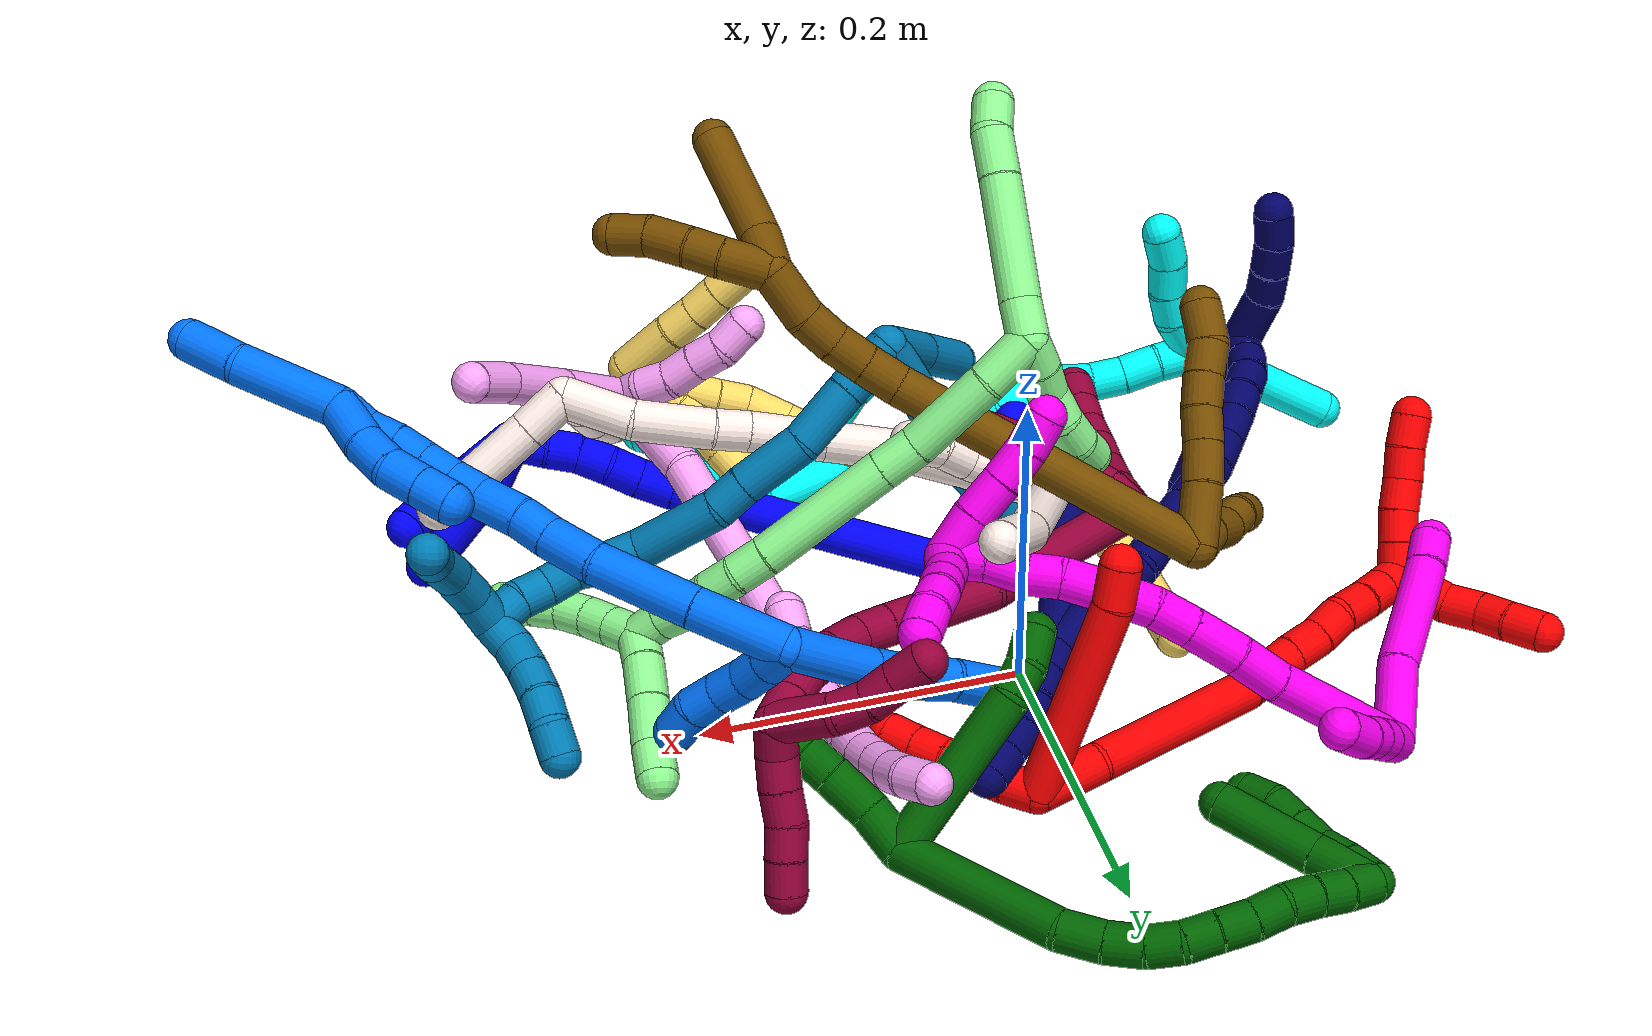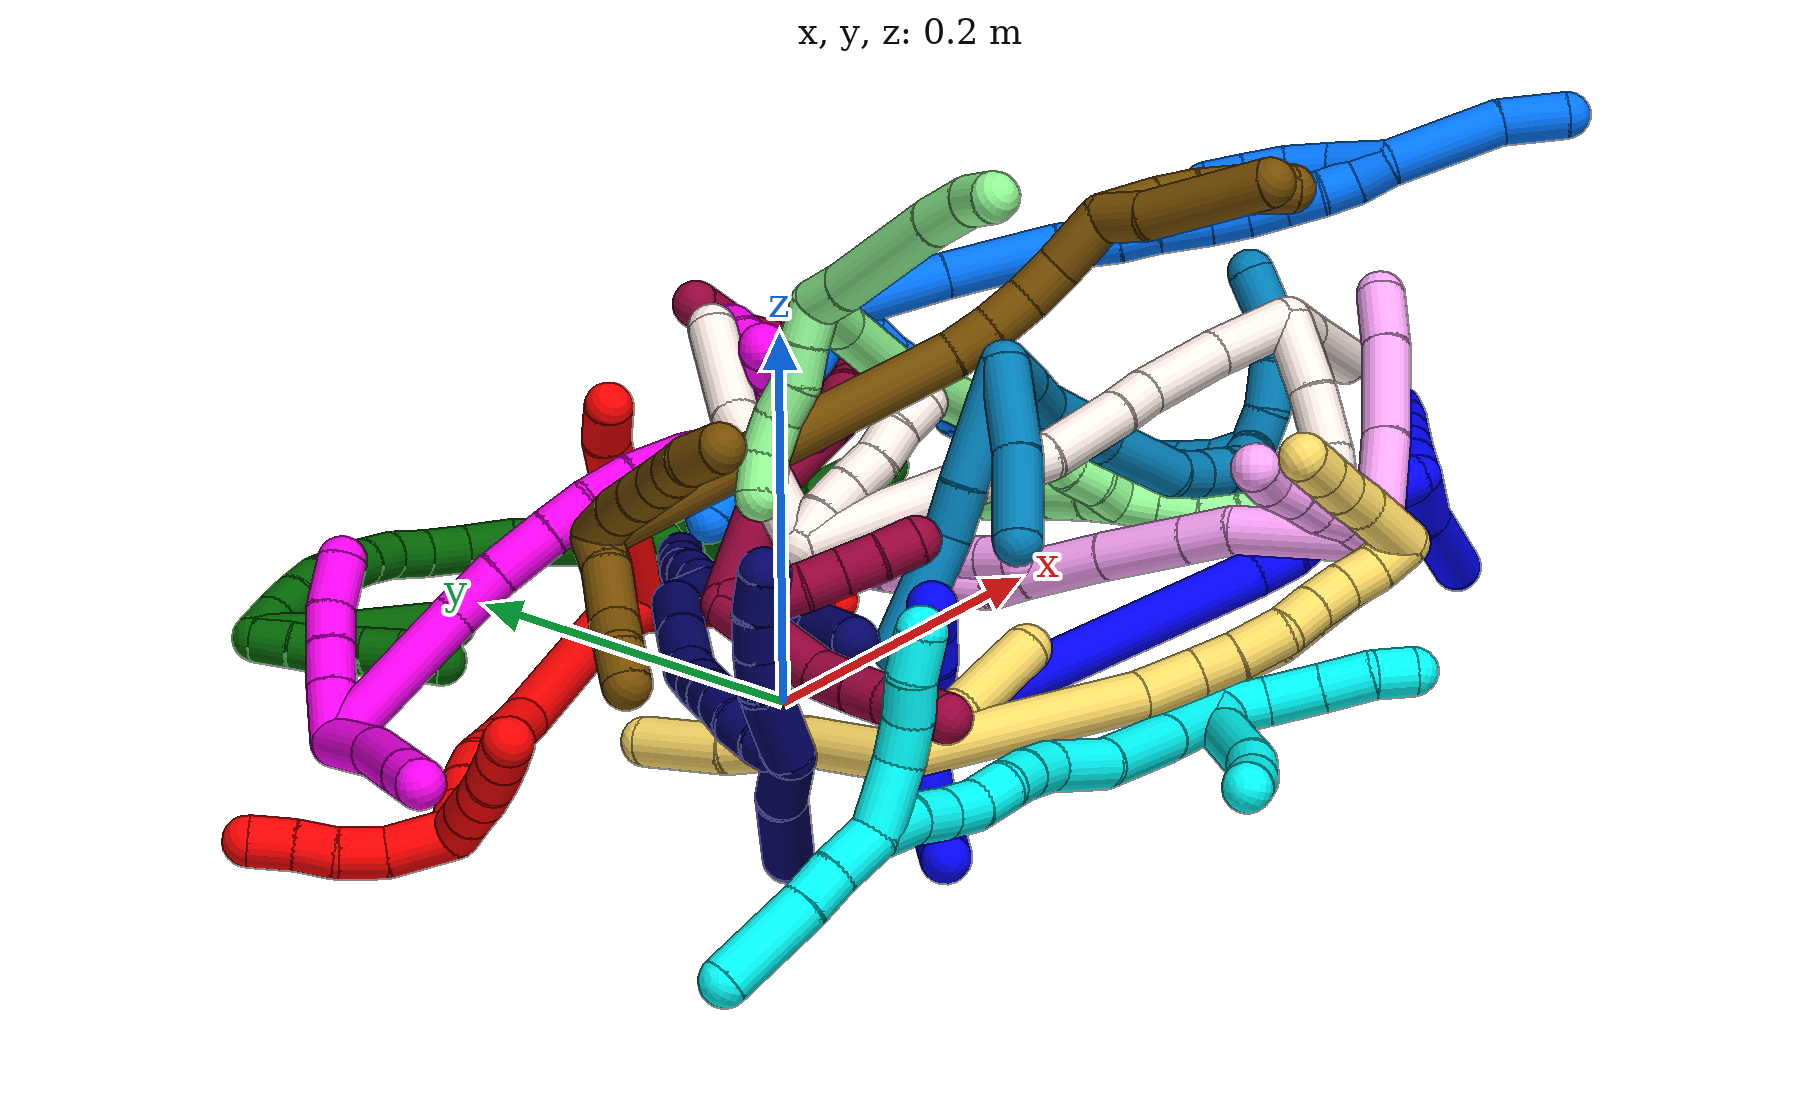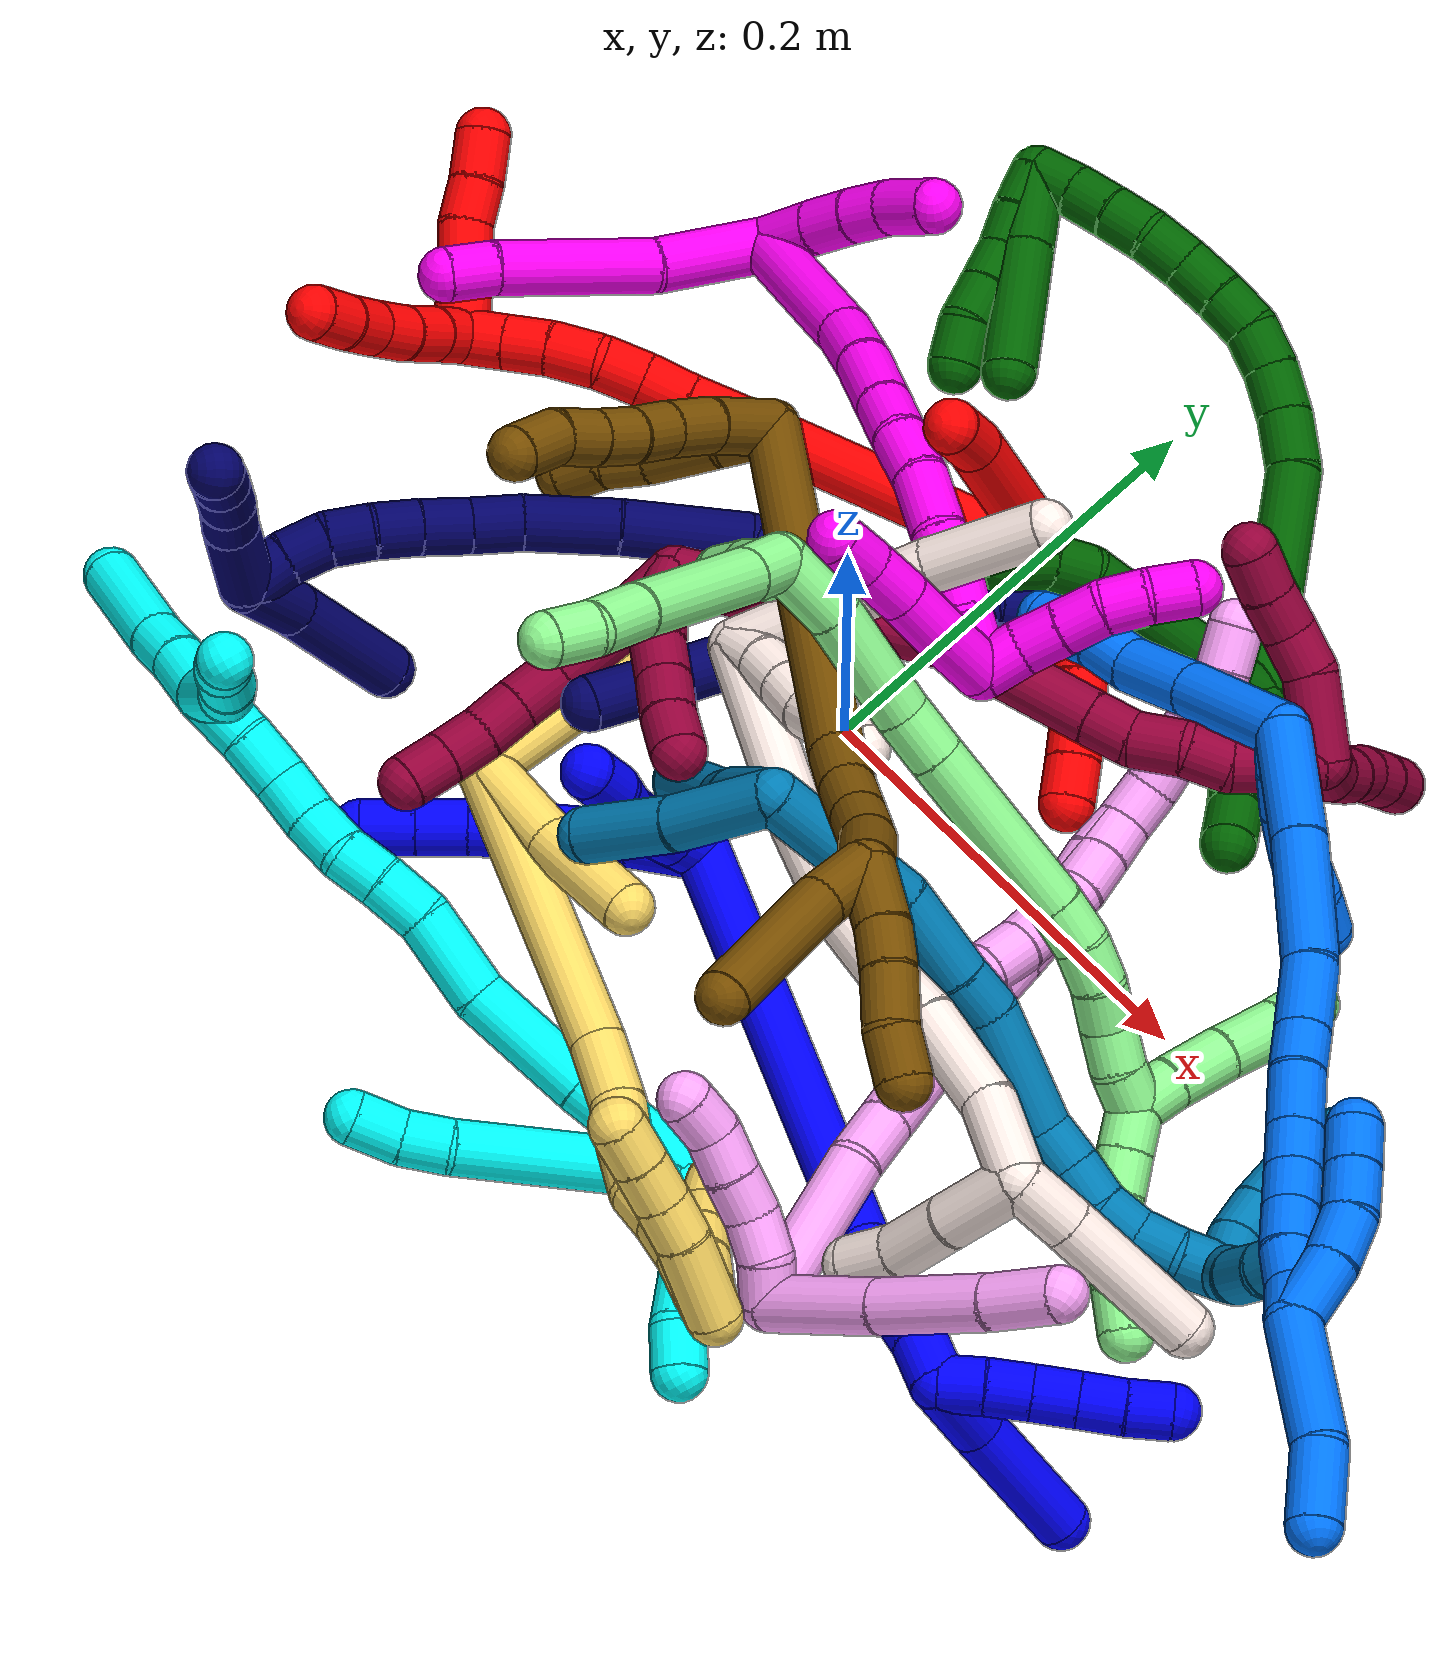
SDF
<sdf version="1.7">
 <world name="default">
  <plugin name="TubeGeneratorPlugin" filename="libtube_generator_plugin.so"/>
  <model name="photoneo_s_sensor">
   <static>1</static>
   <pose>0 0 2 1.57079 1.57079 3.14159</pose>
   <link name="link">
    <inertial><mass>0.1</mass></inertial>
    <sensor name="sensor" type="depth">
     <update_rate>30</update_rate>
     <camera>
      <horizontal_fov>1.22</horizontal_fov>
      <image><width>1920</width><height>1200</height><format>B8G8R8</format></image>
      <clip><near>0.1</near><far>4</far></clip>
      <depth_camera><output>points</output></depth_camera>
     </camera>
     <plugin name="camera_plugin" filename="libgazebo_ros_depth_camera.so">
      <baseline>0.2</baseline>
      <alwaysOn>1</alwaysOn>
      <updateRate>0.0</updateRate>
      <cameraName>camera_ir</cameraName>
      <imageTopicName>/camera/color/image_raw</imageTopicName>
      <cameraInfoTopicName>/camera/color/camera_info</cameraInfoTopicName>
      <depthImageTopicName>/camera/depth/image_raw</depthImageTopicName>
      <depthImageCameraInfoTopicName>/camera/depth/camera_info</depthImageCameraInfoTopicName>
      <pointCloudTopicName>/camera/depth/points</pointCloudTopicName>
      <frameName>fr_optical</frameName>
      <pointCloudCutoff>0.1</pointCloudCutoff>
      <pointCloudCutoffMax>2.0</pointCloudCutoffMax>
      <distortionK1>0</distortionK1>
      <distortionK2>0</distortionK2>
      <distortionK3>0</distortionK3>
      <distortionT1>0</distortionT1>
      <distortionT2>0</distortionT2>
      <CxPrime>0</CxPrime>
      <Cx>0</Cx>
      <Cy>0</Cy>
      <focalLength>0</focalLength>
      <hackBaseline>0</hackBaseline>
     </plugin>
    </sensor>
   </link>
  </model>
  <gravity>0 0 -9.8</gravity>
  <magnetic_field>6e-06 2.3e-05 -4.2e-05</magnetic_field>
  <atmosphere type="adiabatic"/>
  <physics name="default_physics" default="0" type="ode">
   <max_step_size>0.003</max_step_size>
   <real_time_factor>1</real_time_factor>
   <real_time_update_rate>1000</real_time_update_rate>
   <max_contacts>10000</max_contacts>
   <ode>
    <solver>
     <type>quick</type>
     <iters>100</iters>
     <sor>1.3</sor>
     <use_dynamic_moi_rescaling>0</use_dynamic_moi_rescaling>
    </solver>
    <constraints>
     <contact_max_correcting_vel>0</contact_max_correcting_vel>
     <contact_surface_layer>0.001</contact_surface_layer>
     <cfm>0</cfm>
     <erp>0.2</erp>
    </constraints>
   </ode>
  </physics>
  <scene><ambient>0.4 0.4 0.4 1</ambient><background>0.7 0.7 0.7 1</background><shadows>0</shadows></scene>
  <audio><device>default</device></audio>
  <spherical_coordinates>
   <surface_model>EARTH_WGS84</surface_model>
   <latitude_deg>0</latitude_deg>
   <longitude_deg>0</longitude_deg>
   <elevation>0</elevation>
   <heading_deg>0</heading_deg>
  </spherical_coordinates>
  <model name="bin">
   <static>1</static>
   <link name="bottom">
    <collision name="collision-bottom">
     <pose>0 0 -0.01 0 -0 0</pose>
     <geometry><box><size>0.8 0.6 0.02</size></box></geometry>
     <surface>
      <friction><ode><mu>100</mu><mu2>100</mu2></ode></friction>
      <contact><collide_bitmask>65535</collide_bitmask></contact>
     </surface>
    </collision>
   </link>
   <link name="west_wall">
    <collision name="collision-west_wall">
     <pose>-0.41 0 0.1 0 -0 0</pose>
     <geometry><box><size>0.02 0.6 0.2</size></box></geometry>
     <surface>
      <friction><ode><mu>100</mu><mu2>100</mu2></ode></friction>
      <contact><collide_bitmask>65535</collide_bitmask></contact>
     </surface>
    </collision>
   </link>
   <link name="east_wall">
    <collision name="collision-east_wall">
     <pose>0.41 0 0.1 0 -0 0</pose>
     <geometry><box><size>0.02 0.6 0.2</size></box></geometry>
     <surface>
      <friction><ode><mu>100</mu><mu2>100</mu2></ode></friction>
      <contact><collide_bitmask>65535</collide_bitmask></contact>
     </surface>
    </collision>
   </link>
   <link name="south_wall">
    <collision name="collision-south_wall">
     <pose>0 -0.31 0.1 0 -0 0</pose>
     <geometry><box><size>0.8 0.02 0.2</size></box></geometry>
     <surface>
      <friction><ode><mu>100</mu><mu2>100</mu2></ode></friction>
      <contact><collide_bitmask>65535</collide_bitmask></contact>
     </surface>
    </collision>
   </link>
   <link name="north_wall">
    <collision name="collision-north_wall">
     <pose>0 0.31 0.1 0 -0 0</pose>
     <geometry><box><size>0.8 0.02 0.2</size></box></geometry>
     <surface>
      <friction><ode><mu>100</mu><mu2>100</mu2></ode></friction>
      <contact><collide_bitmask>65535</collide_bitmask></contact>
     </surface>
    </collision>
   </link>
  </model>
  <model name="1">
   <static>0</static>
   <link name="1">
    <collision name="collision-cylinder-e_1_2_8">
     <pose>-0.005497 -0.004464 0.015262 0.284575 -0.332811 -0.048113</pose>
     <geometry><cylinder><radius>0.0125</radius><length>0.033649</length></cylinder></geometry>
     <surface>
      <friction><ode><mu>1.16</mu><mu2>1.16</mu2><slip1>0</slip1><slip2>0</slip2></ode></friction>
      <contact><ode><kp>1e+06</kp><kd>1</kd><max_vel>0</max_vel><min_depth>0.001</min_depth></ode></contact>
     </surface>
    </collision>
    <visual name="visual-cylinder-e_1_2_8">
     <pose>-0.005497 -0.004464 0.015262 0.284575 -0.332811 -0.048113</pose>
     <geometry><cylinder><radius>0.0125</radius><length>0.033649</length></cylinder></geometry>
     <material><ambient>0 0 1 1</ambient></material>
    </visual>
    <collision name="collision-cylinder-e_2_8_9">
     <pose>-0.015209 -0.014167 0.045218 0.342435 -0.263956 -0.045899</pose>
     <geometry><cylinder><radius>0.0125</radius><length>0.032321</length></cylinder></geometry>
     <surface>
      <friction><ode><mu>1.16</mu><mu2>1.16</mu2><slip1>0</slip1><slip2>0</slip2></ode></friction>
      <contact><ode><kp>1e+06</kp><kd>1</kd><max_vel>0</max_vel><min_depth>0.001</min_depth></ode></contact>
     </surface>
    </collision>
    <visual name="visual-cylinder-e_2_8_9">
     <pose>-0.015209 -0.014167 0.045218 0.342435 -0.263956 -0.045899</pose>
     <geometry><cylinder><radius>0.0125</radius><length>0.032321</length></cylinder></geometry>
     <material><ambient>0 0 1 1</ambient></material>
    </visual>
    <collision name="collision-cylinder-e_3_9_10">
     <pose>-0.024936 -0.026271 0.075903 0.405572 -0.30664 -0.063526</pose>
     <geometry><cylinder><radius>0.0125</radius><length>0.036506</length></cylinder></geometry>
     <surface>
      <friction><ode><mu>1.16</mu><mu2>1.16</mu2><slip1>0</slip1><slip2>0</slip2></ode></friction>
      <contact><ode><kp>1e+06</kp><kd>1</kd><max_vel>0</max_vel><min_depth>0.001</min_depth></ode></contact>
     </surface>
    </collision>
    <visual name="visual-cylinder-e_3_9_10">
     <pose>-0.024936 -0.026271 0.075903 0.405572 -0.30664 -0.063526</pose>
     <geometry><cylinder><radius>0.0125</radius><length>0.036506</length></cylinder></geometry>
     <material><ambient>0 0 1 1</ambient></material>
    </visual>
    <collision name="collision-cylinder-e_4_10_11">
     <pose>-0.033392 -0.037988 0.101984 0.448121 -0.257351 -0.058956</pose>
     <geometry><cylinder><radius>0.0125</radius><length>0.023154</length></cylinder></geometry>
     <surface>
      <friction><ode><mu>1.16</mu><mu2>1.16</mu2><slip1>0</slip1><slip2>0</slip2></ode></friction>
      <contact><ode><kp>1e+06</kp><kd>1</kd><max_vel>0</max_vel><min_depth>0.001</min_depth></ode></contact>
     </surface>
    </collision>
    <visual name="visual-cylinder-e_4_10_11">
     <pose>-0.033392 -0.037988 0.101984 0.448121 -0.257351 -0.058956</pose>
     <geometry><cylinder><radius>0.0125</radius><length>0.023154</length></cylinder></geometry>
     <material><ambient>0 0 1 1</ambient></material>
    </visual>
    <collision name="collision-cylinder-e_5_11_6">
     <pose>-0.039578 -0.047903 0.122672 0.445814 -0.269063 -0.061341</pose>
     <geometry><cylinder><radius>0.0125</radius><length>0.02437</length></cylinder></geometry>
     <surface>
      <friction><ode><mu>1.16</mu><mu2>1.16</mu2><slip1>0</slip1><slip2>0</slip2></ode></friction>
      <contact><ode><kp>1e+06</kp><kd>1</kd><max_vel>0</max_vel><min_depth>0.001</min_depth></ode></contact>
     </surface>
    </collision>
    <visual name="visual-cylinder-e_5_11_6">
     <pose>-0.039578 -0.047903 0.122672 0.445814 -0.269063 -0.061341</pose>
     <geometry><cylinder><radius>0.0125</radius><length>0.02437</length></cylinder></geometry>
     <material><ambient>0 0 1 1</ambient></material>
    </visual>
    <collision name="collision-cylinder-e_1_2_12">
     <pose>0.00298 0.002521 0.009207 -0.267306 0.302568 -0.040989</pose>
     <geometry><cylinder><radius>0.0125</radius><length>0.02</length></cylinder></geometry>
     <surface>
      <friction><ode><mu>1.16</mu><mu2>1.16</mu2><slip1>0</slip1><slip2>0</slip2></ode></friction>
      <contact><ode><kp>1e+06</kp><kd>1</kd><max_vel>0</max_vel><min_depth>0.001</min_depth></ode></contact>
     </surface>
    </collision>
    <visual name="visual-cylinder-e_1_2_12">
     <pose>0.00298 0.002521 0.009207 -0.267306 0.302568 -0.040989</pose>
     <geometry><cylinder><radius>0.0125</radius><length>0.02</length></cylinder></geometry>
     <material><ambient>0 0 1 1</ambient></material>
    </visual>
    <collision name="collision-cylinder-e_2_12_13">
     <pose>0.009118 0.007787 0.027496 -0.293376 0.321313 -0.047877</pose>
     <geometry><cylinder><radius>0.0125</radius><length>0.02</length></cylinder></geometry>
     <surface>
      <friction><ode><mu>1.16</mu><mu2>1.16</mu2><slip1>0</slip1><slip2>0</slip2></ode></friction>
      <contact><ode><kp>1e+06</kp><kd>1</kd><max_vel>0</max_vel><min_depth>0.001</min_depth></ode></contact>
     </surface>
    </collision>
    <visual name="visual-cylinder-e_2_12_13">
     <pose>0.009118 0.007787 0.027496 -0.293376 0.321313 -0.047877</pose>
     <geometry><cylinder><radius>0.0125</radius><length>0.02</length></cylinder></geometry>
     <material><ambient>0 0 1 1</ambient></material>
    </visual>
    <collision name="collision-cylinder-e_3_13_14">
     <pose>0.017424 0.014557 0.044148 -0.488901 0.540851 -0.138077</pose>
     <geometry><cylinder><radius>0.0125</radius><length>0.02</length></cylinder></geometry>
     <surface>
      <friction><ode><mu>1.16</mu><mu2>1.16</mu2><slip1>0</slip1><slip2>0</slip2></ode></friction>
      <contact><ode><kp>1e+06</kp><kd>1</kd><max_vel>0</max_vel><min_depth>0.001</min_depth></ode></contact>
     </surface>
    </collision>
    <visual name="visual-cylinder-e_3_13_14">
     <pose>0.017424 0.014557 0.044148 -0.488901 0.540851 -0.138077</pose>
     <geometry><cylinder><radius>0.0125</radius><length>0.02</length></cylinder></geometry>
     <material><ambient>0 0 1 1</ambient></material>
    </visual>
    <collision name="collision-cylinder-e_4_14_15">
     <pose>0.027348 0.02423 0.058448 -0.697977 0.497756 -0.184435</pose>
     <geometry><cylinder><radius>0.0125</radius><length>0.02</length></cylinder></geometry>
     <surface>
      <friction><ode><mu>1.16</mu><mu2>1.16</mu2><slip1>0</slip1><slip2>0</slip2></ode></friction>
      <contact><ode><kp>1e+06</kp><kd>1</kd><max_vel>0</max_vel><min_depth>0.001</min_depth></ode></contact>
     </surface>
    </collision>
    <visual name="visual-cylinder-e_4_14_15">
     <pose>0.027348 0.02423 0.058448 -0.697977 0.497756 -0.184435</pose>
     <geometry><cylinder><radius>0.0125</radius><length>0.02</length></cylinder></geometry>
     <material><ambient>0 0 1 1</ambient></material>
    </visual>
    <collision name="collision-cylinder-e_5_15_5">
     <pose>0.035671 0.03378 0.073675 -0.430733 0.362813 -0.080208</pose>
     <geometry><cylinder><radius>0.0125</radius><length>0.02</length></cylinder></geometry>
     <surface>
      <friction><ode><mu>1.16</mu><mu2>1.16</mu2><slip1>0</slip1><slip2>0</slip2></ode></friction>
      <contact><ode><kp>1e+06</kp><kd>1</kd><max_vel>0</max_vel><min_depth>0.001</min_depth></ode></contact>
     </surface>
    </collision>
    <visual name="visual-cylinder-e_5_15_5">
     <pose>0.035671 0.03378 0.073675 -0.430733 0.362813 -0.080208</pose>
     <geometry><cylinder><radius>0.0125</radius><length>0.02</length></cylinder></geometry>
     <material><ambient>0 0 1 1</ambient></material>
    </visual>
    <collision name="collision-cylinder-e_1_2_16">
     <pose>0.087661 -0.031214 -0.026922 2.28251 1.13126 1.89148</pose>
     <geometry><cylinder><radius>0.0125</radius><length>0.193738</length></cylinder></geometry>
     <surface>
      <friction><ode><mu>1.16</mu><mu2>1.16</mu2><slip1>0</slip1><slip2>0</slip2></ode></friction>
      <contact><ode><kp>1e+06</kp><kd>1</kd><max_vel>0</max_vel><min_depth>0.001</min_depth></ode></contact>
     </surface>
    </collision>
    <visual name="visual-cylinder-e_1_2_16">
     <pose>0.087661 -0.031214 -0.026922 2.28251 1.13126 1.89148</pose>
     <geometry><cylinder><radius>0.0125</radius><length>0.193738</length></cylinder></geometry>
     <material><ambient>0 0 1 1</ambient></material>
    </visual>
    <collision name="collision-cylinder-e_2_16_17">
     <pose>0.186256 -0.065619 -0.056468 2.25879 1.20945 1.94221</pose>
     <geometry><cylinder><radius>0.0125</radius><length>0.023376</length></cylinder></geometry>
     <surface>
      <friction><ode><mu>1.16</mu><mu2>1.16</mu2><slip1>0</slip1><slip2>0</slip2></ode></friction>
      <contact><ode><kp>1e+06</kp><kd>1</kd><max_vel>0</max_vel><min_depth>0.001</min_depth></ode></contact>
     </surface>
    </collision>
    <visual name="visual-cylinder-e_2_16_17">
     <pose>0.186256 -0.065619 -0.056468 2.25879 1.20945 1.94221</pose>
     <geometry><cylinder><radius>0.0125</radius><length>0.023376</length></cylinder></geometry>
     <material><ambient>0 0 1 1</ambient></material>
    </visual>
    <collision name="collision-cylinder-e_3_17_18">
     <pose>0.207276 -0.069162 -0.061241 2.97998 1.35818 2.94159</pose>
     <geometry><cylinder><radius>0.0125</radius><length>0.020637</length></cylinder></geometry>
     <surface>
      <friction><ode><mu>1.16</mu><mu2>1.16</mu2><slip1>0</slip1><slip2>0</slip2></ode></friction>
      <contact><ode><kp>1e+06</kp><kd>1</kd><max_vel>0</max_vel><min_depth>0.001</min_depth></ode></contact>
     </surface>
    </collision>
    <visual name="visual-cylinder-e_3_17_18">
     <pose>0.207276 -0.069162 -0.061241 2.97998 1.35818 2.94159</pose>
     <geometry><cylinder><radius>0.0125</radius><length>0.020637</length></cylinder></geometry>
     <material><ambient>0 0 1 1</ambient></material>
    </visual>
    <collision name="collision-cylinder-e_4_18_19">
     <pose>0.226873 -0.071998 -0.065333 2.23442 1.25049 1.95365</pose>
     <geometry><cylinder><radius>0.0125</radius><length>0.02004</length></cylinder></geometry>
     <surface>
      <friction><ode><mu>1.16</mu><mu2>1.16</mu2><slip1>0</slip1><slip2>0</slip2></ode></friction>
      <contact><ode><kp>1e+06</kp><kd>1</kd><max_vel>0</max_vel><min_depth>0.001</min_depth></ode></contact>
     </surface>
    </collision>
    <visual name="visual-cylinder-e_4_18_19">
     <pose>0.226873 -0.071998 -0.065333 2.23442 1.25049 1.95365</pose>
     <geometry><cylinder><radius>0.0125</radius><length>0.02004</length></cylinder></geometry>
     <material><ambient>0 0 1 1</ambient></material>
    </visual>
    <collision name="collision-cylinder-e_5_19_20">
     <pose>0.245297 -0.076546 -0.071328 2.67068 1.09915 2.39497</pose>
     <geometry><cylinder><radius>0.0125</radius><length>0.020012</length></cylinder></geometry>
     <surface>
      <friction><ode><mu>1.16</mu><mu2>1.16</mu2><slip1>0</slip1><slip2>0</slip2></ode></friction>
      <contact><ode><kp>1e+06</kp><kd>1</kd><max_vel>0</max_vel><min_depth>0.001</min_depth></ode></contact>
     </surface>
    </collision>
    <visual name="visual-cylinder-e_5_19_20">
     <pose>0.245297 -0.076546 -0.071328 2.67068 1.09915 2.39497</pose>
     <geometry><cylinder><radius>0.0125</radius><length>0.020012</length></cylinder></geometry>
     <material><ambient>0 0 1 1</ambient></material>
    </visual>
    <collision name="collision-cylinder-e_6_20_1">
     <pose>0.264009 -0.08238 -0.078974 2.33206 1.08212 1.90279</pose>
     <geometry><cylinder><radius>0.0125</radius><length>0.022196</length></cylinder></geometry>
     <surface>
      <friction><ode><mu>1.16</mu><mu2>1.16</mu2><slip1>0</slip1><slip2>0</slip2></ode></friction>
      <contact><ode><kp>1e+06</kp><kd>1</kd><max_vel>0</max_vel><min_depth>0.001</min_depth></ode></contact>
     </surface>
    </collision>
    <visual name="visual-cylinder-e_6_20_1">
     <pose>0.264009 -0.08238 -0.078974 2.33206 1.08212 1.90279</pose>
     <geometry><cylinder><radius>0.0125</radius><length>0.022196</length></cylinder></geometry>
     <material><ambient>0 0 1 1</ambient></material>
    </visual>
    <collision name="collision-cylinder-e_1_1_21">
     <pose>0.276844 -0.082427 -0.091338 -2.73991 0.308406 -1.30417</pose>
     <geometry><cylinder><radius>0.0125</radius><length>0.02</length></cylinder></geometry>
     <surface>
      <friction><ode><mu>1.16</mu><mu2>1.16</mu2><slip1>0</slip1><slip2>0</slip2></ode></friction>
      <contact><ode><kp>1e+06</kp><kd>1</kd><max_vel>0</max_vel><min_depth>0.001</min_depth></ode></contact>
     </surface>
    </collision>
    <visual name="visual-cylinder-e_1_1_21">
     <pose>0.276844 -0.082427 -0.091338 -2.73991 0.308406 -1.30417</pose>
     <geometry><cylinder><radius>0.0125</radius><length>0.02</length></cylinder></geometry>
     <material><ambient>0 0 1 1</ambient></material>
    </visual>
    <collision name="collision-cylinder-e_2_21_22">
     <pose>0.282878 -0.075813 -0.109199 -2.83392 0.304588 -1.56057</pose>
     <geometry><cylinder><radius>0.0125</radius><length>0.02</length></cylinder></geometry>
     <surface>
      <friction><ode><mu>1.16</mu><mu2>1.16</mu2><slip1>0</slip1><slip2>0</slip2></ode></friction>
      <contact><ode><kp>1e+06</kp><kd>1</kd><max_vel>0</max_vel><min_depth>0.001</min_depth></ode></contact>
     </surface>
    </collision>
    <visual name="visual-cylinder-e_2_21_22">
     <pose>0.282878 -0.075813 -0.109199 -2.83392 0.304588 -1.56057</pose>
     <geometry><cylinder><radius>0.0125</radius><length>0.02</length></cylinder></geometry>
     <material><ambient>0 0 1 1</ambient></material>
    </visual>
    <collision name="collision-cylinder-e_3_22_23">
     <pose>0.289033 -0.070089 -0.127346 -2.83818 0.321114 -1.62841</pose>
     <geometry><cylinder><radius>0.0125</radius><length>0.02</length></cylinder></geometry>
     <surface>
      <friction><ode><mu>1.16</mu><mu2>1.16</mu2><slip1>0</slip1><slip2>0</slip2></ode></friction>
      <contact><ode><kp>1e+06</kp><kd>1</kd><max_vel>0</max_vel><min_depth>0.001</min_depth></ode></contact>
     </surface>
    </collision>
    <visual name="visual-cylinder-e_3_22_23">
     <pose>0.289033 -0.070089 -0.127346 -2.83818 0.321114 -1.62841</pose>
     <geometry><cylinder><radius>0.0125</radius><length>0.02</length></cylinder></geometry>
     <material><ambient>0 0 1 1</ambient></material>
    </visual>
    <collision name="collision-cylinder-e_4_23_24">
     <pose>0.29537 -0.064499 -0.145473 -2.84674 0.323683 -1.66544</pose>
     <geometry><cylinder><radius>0.0125</radius><length>0.02</length></cylinder></geometry>
     <surface>
      <friction><ode><mu>1.16</mu><mu2>1.16</mu2><slip1>0</slip1><slip2>0</slip2></ode></friction>
      <contact><ode><kp>1e+06</kp><kd>1</kd><max_vel>0</max_vel><min_depth>0.001</min_depth></ode></contact>
     </surface>
    </collision>
    <visual name="visual-cylinder-e_4_23_24">
     <pose>0.29537 -0.064499 -0.145473 -2.84674 0.323683 -1.66544</pose>
     <geometry><cylinder><radius>0.0125</radius><length>0.02</length></cylinder></geometry>
     <material><ambient>0 0 1 1</ambient></material>
    </visual>
    <collision name="collision-cylinder-e_5_24_4">
     <pose>0.300997 -0.058549 -0.1637 -2.80591 0.247162 -1.2652</pose>
     <geometry><cylinder><radius>0.0125</radius><length>0.02</length></cylinder></geometry>
     <surface>
      <friction><ode><mu>1.16</mu><mu2>1.16</mu2><slip1>0</slip1><slip2>0</slip2></ode></friction>
      <contact><ode><kp>1e+06</kp><kd>1</kd><max_vel>0</max_vel><min_depth>0.001</min_depth></ode></contact>
     </surface>
    </collision>
    <visual name="visual-cylinder-e_5_24_4">
     <pose>0.300997 -0.058549 -0.1637 -2.80591 0.247162 -1.2652</pose>
     <geometry><cylinder><radius>0.0125</radius><length>0.02</length></cylinder></geometry>
     <material><ambient>0 0 1 1</ambient></material>
    </visual>
    <collision name="collision-cylinder-e_1_1_25">
     <pose>0.2699 -0.095566 -0.097321 2.57363 -0.219729 -0.722684</pose>
     <geometry><cylinder><radius>0.0125</radius><length>0.035864</length></cylinder></geometry>
     <surface>
      <friction><ode><mu>1.16</mu><mu2>1.16</mu2><slip1>0</slip1><slip2>0</slip2></ode></friction>
      <contact><ode><kp>1e+06</kp><kd>1</kd><max_vel>0</max_vel><min_depth>0.001</min_depth></ode></contact>
     </surface>
    </collision>
    <visual name="visual-cylinder-e_1_1_25">
     <pose>0.2699 -0.095566 -0.097321 2.57363 -0.219729 -0.722684</pose>
     <geometry><cylinder><radius>0.0125</radius><length>0.035864</length></cylinder></geometry>
     <material><ambient>0 0 1 1</ambient></material>
    </visual>
    <collision name="collision-cylinder-e_2_25_3">
     <pose>0.266159 -0.120857 -0.139936 2.62365 0.005245 0.019796</pose>
     <geometry><cylinder><radius>0.0125</radius><length>0.064136</length></cylinder></geometry>
     <surface>
      <friction><ode><mu>1.16</mu><mu2>1.16</mu2><slip1>0</slip1><slip2>0</slip2></ode></friction>
      <contact><ode><kp>1e+06</kp><kd>1</kd><max_vel>0</max_vel><min_depth>0.001</min_depth></ode></contact>
     </surface>
    </collision>
    <visual name="visual-cylinder-e_2_25_3">
     <pose>0.266159 -0.120857 -0.139936 2.62365 0.005245 0.019796</pose>
     <geometry><cylinder><radius>0.0125</radius><length>0.064136</length></cylinder></geometry>
     <material><ambient>0 0 1 1</ambient></material>
    </visual>
    <collision name="collision-sphere-3">
     <pose>0.266328 -0.136733 -0.167797 0 -0 0</pose>
     <geometry><sphere><radius>0.0125</radius></sphere></geometry>
     <surface>
      <friction><ode><mu>1.16</mu><mu2>1.16</mu2><slip1>0</slip1><slip2>0</slip2></ode></friction>
      <contact><ode><kp>1e+06</kp><kd>1</kd><max_vel>0</max_vel><min_depth>0.001</min_depth></ode></contact>
     </surface>
    </collision>
    <visual name="visual-sphere-3">
     <pose>0.266328 -0.136733 -0.167797 0 -0 0</pose>
     <geometry><sphere><radius>0.0125</radius></sphere></geometry>
     <material><ambient>0 0 1 1</ambient></material>
    </visual>
    <collision name="collision-sphere-25">
     <pose>0.265991 -0.10498 -0.112074 0 -0 0</pose>
     <geometry><sphere><radius>0.0125</radius></sphere></geometry>
     <surface>
      <friction><ode><mu>1.16</mu><mu2>1.16</mu2><slip1>0</slip1><slip2>0</slip2></ode></friction>
      <contact><ode><kp>1e+06</kp><kd>1</kd><max_vel>0</max_vel><min_depth>0.001</min_depth></ode></contact>
     </surface>
    </collision>
    <visual name="visual-sphere-25">
     <pose>0.265991 -0.10498 -0.112074 0 -0 0</pose>
     <geometry><sphere><radius>0.0125</radius></sphere></geometry>
     <material><ambient>0 0 1 1</ambient></material>
    </visual>
    <collision name="collision-sphere-4">
     <pose>0.303444 -0.055355 -0.172855 0 -0 0</pose>
     <geometry><sphere><radius>0.0125</radius></sphere></geometry>
     <surface>
      <friction><ode><mu>1.16</mu><mu2>1.16</mu2><slip1>0</slip1><slip2>0</slip2></ode></friction>
      <contact><ode><kp>1e+06</kp><kd>1</kd><max_vel>0</max_vel><min_depth>0.001</min_depth></ode></contact>
     </surface>
    </collision>
    <visual name="visual-sphere-4">
     <pose>0.303444 -0.055355 -0.172855 0 -0 0</pose>
     <geometry><sphere><radius>0.0125</radius></sphere></geometry>
     <material><ambient>0 0 1 1</ambient></material>
    </visual>
    <collision name="collision-sphere-24">
     <pose>0.298551 -0.061743 -0.154545 0 -0 0</pose>
     <geometry><sphere><radius>0.0125</radius></sphere></geometry>
     <surface>
      <friction><ode><mu>1.16</mu><mu2>1.16</mu2><slip1>0</slip1><slip2>0</slip2></ode></friction>
      <contact><ode><kp>1e+06</kp><kd>1</kd><max_vel>0</max_vel><min_depth>0.001</min_depth></ode></contact>
     </surface>
    </collision>
    <visual name="visual-sphere-24">
     <pose>0.298551 -0.061743 -0.154545 0 -0 0</pose>
     <geometry><sphere><radius>0.0125</radius></sphere></geometry>
     <material><ambient>0 0 1 1</ambient></material>
    </visual>
    <collision name="collision-sphere-23">
     <pose>0.29219 -0.067254 -0.136402 0 -0 0</pose>
     <geometry><sphere><radius>0.0125</radius></sphere></geometry>
     <surface>
      <friction><ode><mu>1.16</mu><mu2>1.16</mu2><slip1>0</slip1><slip2>0</slip2></ode></friction>
      <contact><ode><kp>1e+06</kp><kd>1</kd><max_vel>0</max_vel><min_depth>0.001</min_depth></ode></contact>
     </surface>
    </collision>
    <visual name="visual-sphere-23">
     <pose>0.29219 -0.067254 -0.136402 0 -0 0</pose>
     <geometry><sphere><radius>0.0125</radius></sphere></geometry>
     <material><ambient>0 0 1 1</ambient></material>
    </visual>
    <collision name="collision-sphere-22">
     <pose>0.285877 -0.072924 -0.118291 0 -0 0</pose>
     <geometry><sphere><radius>0.0125</radius></sphere></geometry>
     <surface>
      <friction><ode><mu>1.16</mu><mu2>1.16</mu2><slip1>0</slip1><slip2>0</slip2></ode></friction>
      <contact><ode><kp>1e+06</kp><kd>1</kd><max_vel>0</max_vel><min_depth>0.001</min_depth></ode></contact>
     </surface>
    </collision>
    <visual name="visual-sphere-22">
     <pose>0.285877 -0.072924 -0.118291 0 -0 0</pose>
     <geometry><sphere><radius>0.0125</radius></sphere></geometry>
     <material><ambient>0 0 1 1</ambient></material>
    </visual>
    <collision name="collision-sphere-21">
     <pose>0.279879 -0.078702 -0.100107 0 -0 0</pose>
     <geometry><sphere><radius>0.0125</radius></sphere></geometry>
     <surface>
      <friction><ode><mu>1.16</mu><mu2>1.16</mu2><slip1>0</slip1><slip2>0</slip2></ode></friction>
      <contact><ode><kp>1e+06</kp><kd>1</kd><max_vel>0</max_vel><min_depth>0.001</min_depth></ode></contact>
     </surface>
    </collision>
    <visual name="visual-sphere-21">
     <pose>0.279879 -0.078702 -0.100107 0 -0 0</pose>
     <geometry><sphere><radius>0.0125</radius></sphere></geometry>
     <material><ambient>0 0 1 1</ambient></material>
    </visual>
    <collision name="collision-sphere-1">
     <pose>0.273808 -0.086152 -0.082568 0 -0 0</pose>
     <geometry><sphere><radius>0.0125</radius></sphere></geometry>
     <surface>
      <friction><ode><mu>1.16</mu><mu2>1.16</mu2><slip1>0</slip1><slip2>0</slip2></ode></friction>
      <contact><ode><kp>1e+06</kp><kd>1</kd><max_vel>0</max_vel><min_depth>0.001</min_depth></ode></contact>
     </surface>
    </collision>
    <visual name="visual-sphere-1">
     <pose>0.273808 -0.086152 -0.082568 0 -0 0</pose>
     <geometry><sphere><radius>0.0125</radius></sphere></geometry>
     <material><ambient>0 0 1 1</ambient></material>
    </visual>
    <collision name="collision-sphere-6">
     <pose>-0.042817 -0.052969 0.133271 0 -0 0</pose>
     <geometry><sphere><radius>0.0125</radius></sphere></geometry>
     <surface>
      <friction><ode><mu>1.16</mu><mu2>1.16</mu2><slip1>0</slip1><slip2>0</slip2></ode></friction>
      <contact><ode><kp>1e+06</kp><kd>1</kd><max_vel>0</max_vel><min_depth>0.001</min_depth></ode></contact>
     </surface>
    </collision>
    <visual name="visual-sphere-6">
     <pose>-0.042817 -0.052969 0.133271 0 -0 0</pose>
     <geometry><sphere><radius>0.0125</radius></sphere></geometry>
     <material><ambient>0 0 1 1</ambient></material>
    </visual>
    <collision name="collision-sphere-11">
     <pose>-0.036338 -0.042838 0.112074 0 -0 0</pose>
     <geometry><sphere><radius>0.0125</radius></sphere></geometry>
     <surface>
      <friction><ode><mu>1.16</mu><mu2>1.16</mu2><slip1>0</slip1><slip2>0</slip2></ode></friction>
      <contact><ode><kp>1e+06</kp><kd>1</kd><max_vel>0</max_vel><min_depth>0.001</min_depth></ode></contact>
     </surface>
    </collision>
    <visual name="visual-sphere-11">
     <pose>-0.036338 -0.042838 0.112074 0 -0 0</pose>
     <geometry><sphere><radius>0.0125</radius></sphere></geometry>
     <material><ambient>0 0 1 1</ambient></material>
    </visual>
    <collision name="collision-sphere-10">
     <pose>-0.030445 -0.033137 0.091893 0 -0 0</pose>
     <geometry><sphere><radius>0.0125</radius></sphere></geometry>
     <surface>
      <friction><ode><mu>1.16</mu><mu2>1.16</mu2><slip1>0</slip1><slip2>0</slip2></ode></friction>
      <contact><ode><kp>1e+06</kp><kd>1</kd><max_vel>0</max_vel><min_depth>0.001</min_depth></ode></contact>
     </surface>
    </collision>
    <visual name="visual-sphere-10">
     <pose>-0.030445 -0.033137 0.091893 0 -0 0</pose>
     <geometry><sphere><radius>0.0125</radius></sphere></geometry>
     <material><ambient>0 0 1 1</ambient></material>
    </visual>
    <collision name="collision-sphere-9">
     <pose>-0.019426 -0.019406 0.059914 0 -0 0</pose>
     <geometry><sphere><radius>0.0125</radius></sphere></geometry>
     <surface>
      <friction><ode><mu>1.16</mu><mu2>1.16</mu2><slip1>0</slip1><slip2>0</slip2></ode></friction>
      <contact><ode><kp>1e+06</kp><kd>1</kd><max_vel>0</max_vel><min_depth>0.001</min_depth></ode></contact>
     </surface>
    </collision>
    <visual name="visual-sphere-9">
     <pose>-0.019426 -0.019406 0.059914 0 -0 0</pose>
     <geometry><sphere><radius>0.0125</radius></sphere></geometry>
     <material><ambient>0 0 1 1</ambient></material>
    </visual>
    <collision name="collision-sphere-2">
     <geometry><sphere><radius>0.0125</radius></sphere></geometry>
     <surface>
      <friction><ode><mu>1.16</mu><mu2>1.16</mu2><slip1>0</slip1><slip2>0</slip2></ode></friction>
      <contact><ode><kp>1e+06</kp><kd>1</kd><max_vel>0</max_vel><min_depth>0.001</min_depth></ode></contact>
     </surface>
    </collision>
    <visual name="visual-sphere-2">
     <geometry><sphere><radius>0.0125</radius></sphere></geometry>
     <material><ambient>0 0 1 1</ambient></material>
    </visual>
    <collision name="collision-sphere-19">
     <pose>0.236383 -0.074483 -0.067277 0 -0 0</pose>
     <geometry><sphere><radius>0.0125</radius></sphere></geometry>
     <surface>
      <friction><ode><mu>1.16</mu><mu2>1.16</mu2><slip1>0</slip1><slip2>0</slip2></ode></friction>
      <contact><ode><kp>1e+06</kp><kd>1</kd><max_vel>0</max_vel><min_depth>0.001</min_depth></ode></contact>
     </surface>
    </collision>
    <visual name="visual-sphere-19">
     <pose>0.236383 -0.074483 -0.067277 0 -0 0</pose>
     <geometry><sphere><radius>0.0125</radius></sphere></geometry>
     <material><ambient>0 0 1 1</ambient></material>
    </visual>
    <collision name="collision-sphere-8">
     <pose>-0.010993 -0.008928 0.030523 0 -0 0</pose>
     <geometry><sphere><radius>0.0125</radius></sphere></geometry>
     <surface>
      <friction><ode><mu>1.16</mu><mu2>1.16</mu2><slip1>0</slip1><slip2>0</slip2></ode></friction>
      <contact><ode><kp>1e+06</kp><kd>1</kd><max_vel>0</max_vel><min_depth>0.001</min_depth></ode></contact>
     </surface>
    </collision>
    <visual name="visual-sphere-8">
     <pose>-0.010993 -0.008928 0.030523 0 -0 0</pose>
     <geometry><sphere><radius>0.0125</radius></sphere></geometry>
     <material><ambient>0 0 1 1</ambient></material>
    </visual>
    <collision name="collision-sphere-12">
     <pose>0.005959 0.005043 0.018413 0 -0 0</pose>
     <geometry><sphere><radius>0.0125</radius></sphere></geometry>
     <surface>
      <friction><ode><mu>1.16</mu><mu2>1.16</mu2><slip1>0</slip1><slip2>0</slip2></ode></friction>
      <contact><ode><kp>1e+06</kp><kd>1</kd><max_vel>0</max_vel><min_depth>0.001</min_depth></ode></contact>
     </surface>
    </collision>
    <visual name="visual-sphere-12">
     <pose>0.005959 0.005043 0.018413 0 -0 0</pose>
     <geometry><sphere><radius>0.0125</radius></sphere></geometry>
     <material><ambient>0 0 1 1</ambient></material>
    </visual>
    <collision name="collision-sphere-13">
     <pose>0.012276 0.01053 0.036579 0 -0 0</pose>
     <geometry><sphere><radius>0.0125</radius></sphere></geometry>
     <surface>
      <friction><ode><mu>1.16</mu><mu2>1.16</mu2><slip1>0</slip1><slip2>0</slip2></ode></friction>
      <contact><ode><kp>1e+06</kp><kd>1</kd><max_vel>0</max_vel><min_depth>0.001</min_depth></ode></contact>
     </surface>
    </collision>
    <visual name="visual-sphere-13">
     <pose>0.012276 0.01053 0.036579 0 -0 0</pose>
     <geometry><sphere><radius>0.0125</radius></sphere></geometry>
     <material><ambient>0 0 1 1</ambient></material>
    </visual>
    <collision name="collision-sphere-14">
     <pose>0.022573 0.018583 0.051716 0 -0 0</pose>
     <geometry><sphere><radius>0.0125</radius></sphere></geometry>
     <surface>
      <friction><ode><mu>1.16</mu><mu2>1.16</mu2><slip1>0</slip1><slip2>0</slip2></ode></friction>
      <contact><ode><kp>1e+06</kp><kd>1</kd><max_vel>0</max_vel><min_depth>0.001</min_depth></ode></contact>
     </surface>
    </collision>
    <visual name="visual-sphere-14">
     <pose>0.022573 0.018583 0.051716 0 -0 0</pose>
     <geometry><sphere><radius>0.0125</radius></sphere></geometry>
     <material><ambient>0 0 1 1</ambient></material>
    </visual>
    <collision name="collision-sphere-15">
     <pose>0.032122 0.029877 0.065179 0 -0 0</pose>
     <geometry><sphere><radius>0.0125</radius></sphere></geometry>
     <surface>
      <friction><ode><mu>1.16</mu><mu2>1.16</mu2><slip1>0</slip1><slip2>0</slip2></ode></friction>
      <contact><ode><kp>1e+06</kp><kd>1</kd><max_vel>0</max_vel><min_depth>0.001</min_depth></ode></contact>
     </surface>
    </collision>
    <visual name="visual-sphere-15">
     <pose>0.032122 0.029877 0.065179 0 -0 0</pose>
     <geometry><sphere><radius>0.0125</radius></sphere></geometry>
     <material><ambient>0 0 1 1</ambient></material>
    </visual>
    <collision name="collision-sphere-5">
     <pose>0.03922 0.037684 0.08217 0 -0 0</pose>
     <geometry><sphere><radius>0.0125</radius></sphere></geometry>
     <surface>
      <friction><ode><mu>1.16</mu><mu2>1.16</mu2><slip1>0</slip1><slip2>0</slip2></ode></friction>
      <contact><ode><kp>1e+06</kp><kd>1</kd><max_vel>0</max_vel><min_depth>0.001</min_depth></ode></contact>
     </surface>
    </collision>
    <visual name="visual-sphere-5">
     <pose>0.03922 0.037684 0.08217 0 -0 0</pose>
     <geometry><sphere><radius>0.0125</radius></sphere></geometry>
     <material><ambient>0 0 1 1</ambient></material>
    </visual>
    <collision name="collision-sphere-16">
     <pose>0.175323 -0.062427 -0.053844 0 -0 0</pose>
     <geometry><sphere><radius>0.0125</radius></sphere></geometry>
     <surface>
      <friction><ode><mu>1.16</mu><mu2>1.16</mu2><slip1>0</slip1><slip2>0</slip2></ode></friction>
      <contact><ode><kp>1e+06</kp><kd>1</kd><max_vel>0</max_vel><min_depth>0.001</min_depth></ode></contact>
     </surface>
    </collision>
    <visual name="visual-sphere-16">
     <pose>0.175323 -0.062427 -0.053844 0 -0 0</pose>
     <geometry><sphere><radius>0.0125</radius></sphere></geometry>
     <material><ambient>0 0 1 1</ambient></material>
    </visual>
    <collision name="collision-sphere-17">
     <pose>0.19719 -0.068811 -0.059092 0 -0 0</pose>
     <geometry><sphere><radius>0.0125</radius></sphere></geometry>
     <surface>
      <friction><ode><mu>1.16</mu><mu2>1.16</mu2><slip1>0</slip1><slip2>0</slip2></ode></friction>
      <contact><ode><kp>1e+06</kp><kd>1</kd><max_vel>0</max_vel><min_depth>0.001</min_depth></ode></contact>
     </surface>
    </collision>
    <visual name="visual-sphere-17">
     <pose>0.19719 -0.068811 -0.059092 0 -0 0</pose>
     <geometry><sphere><radius>0.0125</radius></sphere></geometry>
     <material><ambient>0 0 1 1</ambient></material>
    </visual>
    <collision name="collision-sphere-18">
     <pose>0.217362 -0.069512 -0.06339 0 -0 0</pose>
     <geometry><sphere><radius>0.0125</radius></sphere></geometry>
     <surface>
      <friction><ode><mu>1.16</mu><mu2>1.16</mu2><slip1>0</slip1><slip2>0</slip2></ode></friction>
      <contact><ode><kp>1e+06</kp><kd>1</kd><max_vel>0</max_vel><min_depth>0.001</min_depth></ode></contact>
     </surface>
    </collision>
    <visual name="visual-sphere-18">
     <pose>0.217362 -0.069512 -0.06339 0 -0 0</pose>
     <geometry><sphere><radius>0.0125</radius></sphere></geometry>
     <material><ambient>0 0 1 1</ambient></material>
    </visual>
    <collision name="collision-sphere-20">
     <pose>0.25421 -0.078608 -0.075379 0 -0 0</pose>
     <geometry><sphere><radius>0.0125</radius></sphere></geometry>
     <surface>
      <friction><ode><mu>1.16</mu><mu2>1.16</mu2><slip1>0</slip1><slip2>0</slip2></ode></friction>
      <contact><ode><kp>1e+06</kp><kd>1</kd><max_vel>0</max_vel><min_depth>0.001</min_depth></ode></contact>
     </surface>
    </collision>
    <visual name="visual-sphere-20">
     <pose>0.25421 -0.078608 -0.075379 0 -0 0</pose>
     <geometry><sphere><radius>0.0125</radius></sphere></geometry>
     <material><ambient>0 0 1 1</ambient></material>
    </visual>
    <inertial>
     <pose>0.126812 -0.045299 -0.030852 0 -0 0</pose>
     <mass>0.75</mass>
     <inertia>
      <ixx>0.000231</ixx>
      <ixy>0</ixy>
      <ixz>0</ixz>
      <iyy>0.000762</iyy>
      <iyz>0</iyz>
      <izz>-0.000349</izz>
     </inertia>
    </inertial>
   </link>
   <pose>0.001813 -0.087737 0.012233 0.961923 -0.661164 -0.472876</pose>
  </model>
  <model name="2">
   <static>0</static>
   <link name="2">
    <collision name="collision-cylinder-e_1_2_8">
     <pose>-0.009837 0.02602 0.056606 -0.430858 -0.156611 0.034337</pose>
     <geometry><cylinder><radius>0.0125</radius><length>0.126144</length></cylinder></geometry>
     <surface>
      <friction><ode><mu>1.16</mu><mu2>1.16</mu2><slip1>0</slip1><slip2>0</slip2></ode></friction>
      <contact><ode><kp>1e+06</kp><kd>1</kd><max_vel>0</max_vel><min_depth>0.001</min_depth></ode></contact>
     </surface>
    </collision>
    <visual name="visual-cylinder-e_1_2_8">
     <pose>-0.009837 0.02602 0.056606 -0.430858 -0.156611 0.034337</pose>
     <geometry><cylinder><radius>0.0125</radius><length>0.126144</length></cylinder></geometry>
     <material><ambient>1 0 0 1</ambient></material>
    </visual>
    <collision name="collision-cylinder-e_2_8_6">
     <pose>-0.019848 0.055347 0.124672 -0.281022 -0.014543 0.002057</pose>
     <geometry><cylinder><radius>0.0125</radius><length>0.023856</length></cylinder></geometry>
     <surface>
      <friction><ode><mu>1.16</mu><mu2>1.16</mu2><slip1>0</slip1><slip2>0</slip2></ode></friction>
      <contact><ode><kp>1e+06</kp><kd>1</kd><max_vel>0</max_vel><min_depth>0.001</min_depth></ode></contact>
     </surface>
    </collision>
    <visual name="visual-cylinder-e_2_8_6">
     <pose>-0.019848 0.055347 0.124672 -0.281022 -0.014543 0.002057</pose>
     <geometry><cylinder><radius>0.0125</radius><length>0.023856</length></cylinder></geometry>
     <material><ambient>1 0 0 1</ambient></material>
    </visual>
    <collision name="collision-cylinder-e_1_2_9">
     <pose>0.008411 -0.005132 0.001706 1.24997 0.999369 0.750371</pose>
     <geometry><cylinder><radius>0.0125</radius><length>0.02</length></cylinder></geometry>
     <surface>
      <friction><ode><mu>1.16</mu><mu2>1.16</mu2><slip1>0</slip1><slip2>0</slip2></ode></friction>
      <contact><ode><kp>1e+06</kp><kd>1</kd><max_vel>0</max_vel><min_depth>0.001</min_depth></ode></contact>
     </surface>
    </collision>
    <visual name="visual-cylinder-e_1_2_9">
     <pose>0.008411 -0.005132 0.001706 1.24997 0.999369 0.750371</pose>
     <geometry><cylinder><radius>0.0125</radius><length>0.02</length></cylinder></geometry>
     <material><ambient>1 0 0 1</ambient></material>
    </visual>
    <collision name="collision-cylinder-e_2_9_10">
     <pose>0.024857 -0.015643 0.005965 1.12737 0.933055 0.61637</pose>
     <geometry><cylinder><radius>0.0125</radius><length>0.02</length></cylinder></geometry>
     <surface>
      <friction><ode><mu>1.16</mu><mu2>1.16</mu2><slip1>0</slip1><slip2>0</slip2></ode></friction>
      <contact><ode><kp>1e+06</kp><kd>1</kd><max_vel>0</max_vel><min_depth>0.001</min_depth></ode></contact>
     </surface>
    </collision>
    <visual name="visual-cylinder-e_2_9_10">
     <pose>0.024857 -0.015643 0.005965 1.12737 0.933055 0.61637</pose>
     <geometry><cylinder><radius>0.0125</radius><length>0.02</length></cylinder></geometry>
     <material><ambient>1 0 0 1</ambient></material>
    </visual>
    <collision name="collision-cylinder-e_3_10_11">
     <pose>0.040855 -0.026544 0.010983 1.15133 0.921288 0.623147</pose>
     <geometry><cylinder><radius>0.0125</radius><length>0.02</length></cylinder></geometry>
     <surface>
      <friction><ode><mu>1.16</mu><mu2>1.16</mu2><slip1>0</slip1><slip2>0</slip2></ode></friction>
      <contact><ode><kp>1e+06</kp><kd>1</kd><max_vel>0</max_vel><min_depth>0.001</min_depth></ode></contact>
     </surface>
    </collision>
    <visual name="visual-cylinder-e_3_10_11">
     <pose>0.040855 -0.026544 0.010983 1.15133 0.921288 0.623147</pose>
     <geometry><cylinder><radius>0.0125</radius><length>0.02</length></cylinder></geometry>
     <material><ambient>1 0 0 1</ambient></material>
    </visual>
    <collision name="collision-cylinder-e_4_11_12">
     <pose>0.056141 -0.03841 0.015931 1.19734 0.821486 0.577593</pose>
     <geometry><cylinder><radius>0.0125</radius><length>0.02</length></cylinder></geometry>
     <surface>
      <friction><ode><mu>1.16</mu><mu2>1.16</mu2><slip1>0</slip1><slip2>0</slip2></ode></friction>
      <contact><ode><kp>1e+06</kp><kd>1</kd><max_vel>0</max_vel><min_depth>0.001</min_depth></ode></contact>
     </surface>
    </collision>
    <visual name="visual-cylinder-e_4_11_12">
     <pose>0.056141 -0.03841 0.015931 1.19734 0.821486 0.577593</pose>
     <geometry><cylinder><radius>0.0125</radius><length>0.02</length></cylinder></geometry>
     <material><ambient>1 0 0 1</ambient></material>
    </visual>
    <collision name="collision-cylinder-e_5_12_5">
     <pose>0.070667 -0.051093 0.021223 1.15408 0.804473 0.540324</pose>
     <geometry><cylinder><radius>0.0125</radius><length>0.02</length></cylinder></geometry>
     <surface>
      <friction><ode><mu>1.16</mu><mu2>1.16</mu2><slip1>0</slip1><slip2>0</slip2></ode></friction>
      <contact><ode><kp>1e+06</kp><kd>1</kd><max_vel>0</max_vel><min_depth>0.001</min_depth></ode></contact>
     </surface>
    </collision>
    <visual name="visual-cylinder-e_5_12_5">
     <pose>0.070667 -0.051093 0.021223 1.15408 0.804473 0.540324</pose>
     <geometry><cylinder><radius>0.0125</radius><length>0.02</length></cylinder></geometry>
     <material><ambient>1 0 0 1</ambient></material>
    </visual>
    <collision name="collision-cylinder-e_1_2_13">
     <pose>-0.01817 -0.00167 0.010114 0.163604 -1.05717 -0.095689</pose>
     <geometry><cylinder><radius>0.0125</radius><length>0.041724</length></cylinder></geometry>
     <surface>
      <friction><ode><mu>1.16</mu><mu2>1.16</mu2><slip1>0</slip1><slip2>0</slip2></ode></friction>
      <contact><ode><kp>1e+06</kp><kd>1</kd><max_vel>0</max_vel><min_depth>0.001</min_depth></ode></contact>
     </surface>
    </collision>
    <visual name="visual-cylinder-e_1_2_13">
     <pose>-0.01817 -0.00167 0.010114 0.163604 -1.05717 -0.095689</pose>
     <geometry><cylinder><radius>0.0125</radius><length>0.041724</length></cylinder></geometry>
     <material><ambient>1 0 0 1</ambient></material>
    </visual>
    <collision name="collision-cylinder-e_2_13_14">
     <pose>-0.085301 -0.020482 0.044188 0.621013 -1.02909 -0.358917</pose>
     <geometry><cylinder><radius>0.0125</radius><length>0.114282</length></cylinder></geometry>
     <surface>
      <friction><ode><mu>1.16</mu><mu2>1.16</mu2><slip1>0</slip1><slip2>0</slip2></ode></friction>
      <contact><ode><kp>1e+06</kp><kd>1</kd><max_vel>0</max_vel><min_depth>0.001</min_depth></ode></contact>
     </surface>
    </collision>
    <visual name="visual-cylinder-e_2_13_14">
     <pose>-0.085301 -0.020482 0.044188 0.621013 -1.02909 -0.358917</pose>
     <geometry><cylinder><radius>0.0125</radius><length>0.114282</length></cylinder></geometry>
     <material><ambient>1 0 0 1</ambient></material>
    </visual>
    <collision name="collision-cylinder-e_3_14_15">
     <pose>-0.148565 -0.042466 0.079372 0.407267 -0.863716 -0.189765</pose>
     <geometry><cylinder><radius>0.0125</radius><length>0.037631</length></cylinder></geometry>
     <surface>
      <friction><ode><mu>1.16</mu><mu2>1.16</mu2><slip1>0</slip1><slip2>0</slip2></ode></friction>
      <contact><ode><kp>1e+06</kp><kd>1</kd><max_vel>0</max_vel><min_depth>0.001</min_depth></ode></contact>
     </surface>
    </collision>
    <visual name="visual-cylinder-e_3_14_15">
     <pose>-0.148565 -0.042466 0.079372 0.407267 -0.863716 -0.189765</pose>
     <geometry><cylinder><radius>0.0125</radius><length>0.037631</length></cylinder></geometry>
     <material><ambient>1 0 0 1</ambient></material>
    </visual>
    <collision name="collision-cylinder-e_4_15_16">
     <pose>-0.171825 -0.049826 0.096632 0.395266 -0.939914 -0.202718</pose>
     <geometry><cylinder><radius>0.0125</radius><length>0.022181</length></cylinder></geometry>
     <surface>
      <friction><ode><mu>1.16</mu><mu2>1.16</mu2><slip1>0</slip1><slip2>0</slip2></ode></friction>
      <contact><ode><kp>1e+06</kp><kd>1</kd><max_vel>0</max_vel><min_depth>0.001</min_depth></ode></contact>
     </surface>
    </collision>
    <visual name="visual-cylinder-e_4_15_16">
     <pose>-0.171825 -0.049826 0.096632 0.395266 -0.939914 -0.202718</pose>
     <geometry><cylinder><radius>0.0125</radius><length>0.022181</length></cylinder></geometry>
     <material><ambient>1 0 0 1</ambient></material>
    </visual>
    <collision name="collision-cylinder-e_5_16_17">
     <pose>-0.187913 -0.054777 0.109536 0.340397 -0.774845 -0.140025</pose>
     <geometry><cylinder><radius>0.0125</radius><length>0.020389</length></cylinder></geometry>
     <surface>
      <friction><ode><mu>1.16</mu><mu2>1.16</mu2><slip1>0</slip1><slip2>0</slip2></ode></friction>
      <contact><ode><kp>1e+06</kp><kd>1</kd><max_vel>0</max_vel><min_depth>0.001</min_depth></ode></contact>
     </surface>
    </collision>
    <visual name="visual-cylinder-e_5_16_17">
     <pose>-0.187913 -0.054777 0.109536 0.340397 -0.774845 -0.140025</pose>
     <geometry><cylinder><radius>0.0125</radius><length>0.020389</length></cylinder></geometry>
     <material><ambient>1 0 0 1</ambient></material>
    </visual>
    <collision name="collision-cylinder-e_6_17_18">
     <pose>-0.204163 -0.062238 0.121283 0.800319 -0.91546 -0.410863</pose>
     <geometry><cylinder><radius>0.0125</radius><length>0.023001</length></cylinder></geometry>
     <surface>
      <friction><ode><mu>1.16</mu><mu2>1.16</mu2><slip1>0</slip1><slip2>0</slip2></ode></friction>
      <contact><ode><kp>1e+06</kp><kd>1</kd><max_vel>0</max_vel><min_depth>0.001</min_depth></ode></contact>
     </surface>
    </collision>
    <visual name="visual-cylinder-e_6_17_18">
     <pose>-0.204163 -0.062238 0.121283 0.800319 -0.91546 -0.410863</pose>
     <geometry><cylinder><radius>0.0125</radius><length>0.023001</length></cylinder></geometry>
     <material><ambient>1 0 0 1</ambient></material>
    </visual>
    <collision name="collision-cylinder-e_7_18_19">
     <pose>-0.220617 -0.072718 0.130439 0.905736 -0.814041 -0.413542</pose>
     <geometry><cylinder><radius>0.0125</radius><length>0.02018</length></cylinder></geometry>
     <surface>
      <friction><ode><mu>1.16</mu><mu2>1.16</mu2><slip1>0</slip1><slip2>0</slip2></ode></friction>
      <contact><ode><kp>1e+06</kp><kd>1</kd><max_vel>0</max_vel><min_depth>0.001</min_depth></ode></contact>
     </surface>
    </collision>
    <visual name="visual-cylinder-e_7_18_19">
     <pose>-0.220617 -0.072718 0.130439 0.905736 -0.814041 -0.413542</pose>
     <geometry><cylinder><radius>0.0125</radius><length>0.02018</length></cylinder></geometry>
     <material><ambient>1 0 0 1</ambient></material>
    </visual>
    <collision name="collision-cylinder-e_8_19_1">
     <pose>-0.23539 -0.083685 0.139241 0.883582 -0.806058 -0.397982</pose>
     <geometry><cylinder><radius>0.0125</radius><length>0.020614</length></cylinder></geometry>
     <surface>
      <friction><ode><mu>1.16</mu><mu2>1.16</mu2><slip1>0</slip1><slip2>0</slip2></ode></friction>
      <contact><ode><kp>1e+06</kp><kd>1</kd><max_vel>0</max_vel><min_depth>0.001</min_depth></ode></contact>
     </surface>
    </collision>
    <visual name="visual-cylinder-e_8_19_1">
     <pose>-0.23539 -0.083685 0.139241 0.883582 -0.806058 -0.397982</pose>
     <geometry><cylinder><radius>0.0125</radius><length>0.020614</length></cylinder></geometry>
     <material><ambient>1 0 0 1</ambient></material>
    </visual>
    <collision name="collision-cylinder-e_1_1_20">
     <pose>-0.24224 -0.089874 0.153728 0.067425 0.058689 0.00198</pose>
     <geometry><cylinder><radius>0.0125</radius><length>0.02</length></cylinder></geometry>
     <surface>
      <friction><ode><mu>1.16</mu><mu2>1.16</mu2><slip1>0</slip1><slip2>0</slip2></ode></friction>
      <contact><ode><kp>1e+06</kp><kd>1</kd><max_vel>0</max_vel><min_depth>0.001</min_depth></ode></contact>
     </surface>
    </collision>
    <visual name="visual-cylinder-e_1_1_20">
     <pose>-0.24224 -0.089874 0.153728 0.067425 0.058689 0.00198</pose>
     <geometry><cylinder><radius>0.0125</radius><length>0.02</length></cylinder></geometry>
     <material><ambient>1 0 0 1</ambient></material>
    </visual>
    <collision name="collision-cylinder-e_2_20_21">
     <pose>-0.241279 -0.091655 0.17362 0.111102 0.037503 0.002086</pose>
     <geometry><cylinder><radius>0.0125</radius><length>0.02</length></cylinder></geometry>
     <surface>
      <friction><ode><mu>1.16</mu><mu2>1.16</mu2><slip1>0</slip1><slip2>0</slip2></ode></friction>
      <contact><ode><kp>1e+06</kp><kd>1</kd><max_vel>0</max_vel><min_depth>0.001</min_depth></ode></contact>
     </surface>
    </collision>
    <visual name="visual-cylinder-e_2_20_21">
     <pose>-0.241279 -0.091655 0.17362 0.111102 0.037503 0.002086</pose>
     <geometry><cylinder><radius>0.0125</radius><length>0.02</length></cylinder></geometry>
     <material><ambient>1 0 0 1</ambient></material>
    </visual>
    <collision name="collision-cylinder-e_3_21_22">
     <pose>-0.241691 -0.093568 0.193487 0.080887 -0.078824 -0.003191</pose>
     <geometry><cylinder><radius>0.0125</radius><length>0.02</length></cylinder></geometry>
     <surface>
      <friction><ode><mu>1.16</mu><mu2>1.16</mu2><slip1>0</slip1><slip2>0</slip2></ode></friction>
      <contact><ode><kp>1e+06</kp><kd>1</kd><max_vel>0</max_vel><min_depth>0.001</min_depth></ode></contact>
     </surface>
    </collision>
    <visual name="visual-cylinder-e_3_21_22">
     <pose>-0.241691 -0.093568 0.193487 0.080887 -0.078824 -0.003191</pose>
     <geometry><cylinder><radius>0.0125</radius><length>0.02</length></cylinder></geometry>
     <material><ambient>1 0 0 1</ambient></material>
    </visual>
    <collision name="collision-cylinder-e_4_22_23">
     <pose>-0.242235 -0.094121 0.213418 -0.025283 0.024401 -0.000308</pose>
     <geometry><cylinder><radius>0.0125</radius><length>0.02</length></cylinder></geometry>
     <surface>
      <friction><ode><mu>1.16</mu><mu2>1.16</mu2><slip1>0</slip1><slip2>0</slip2></ode></friction>
      <contact><ode><kp>1e+06</kp><kd>1</kd><max_vel>0</max_vel><min_depth>0.001</min_depth></ode></contact>
     </surface>
    </collision>
    <visual name="visual-cylinder-e_4_22_23">
     <pose>-0.242235 -0.094121 0.213418 -0.025283 0.024401 -0.000308</pose>
     <geometry><cylinder><radius>0.0125</radius><length>0.02</length></cylinder></geometry>
     <material><ambient>1 0 0 1</ambient></material>
    </visual>
    <collision name="collision-cylinder-e_5_23_4">
     <pose>-0.243051 -0.093788 0.233355 -0.008043 -0.106259 0.000428</pose>
     <geometry><cylinder><radius>0.0125</radius><length>0.02</length></cylinder></geometry>
     <surface>
      <friction><ode><mu>1.16</mu><mu2>1.16</mu2><slip1>0</slip1><slip2>0</slip2></ode></friction>
      <contact><ode><kp>1e+06</kp><kd>1</kd><max_vel>0</max_vel><min_depth>0.001</min_depth></ode></contact>
     </surface>
    </collision>
    <visual name="visual-cylinder-e_5_23_4">
     <pose>-0.243051 -0.093788 0.233355 -0.008043 -0.106259 0.000428</pose>
     <geometry><cylinder><radius>0.0125</radius><length>0.02</length></cylinder></geometry>
     <material><ambient>1 0 0 1</ambient></material>
    </visual>
    <collision name="collision-cylinder-e_1_1_24">
     <pose>-0.256531 -0.082328 0.136682 -2.37142 -0.946534 1.80249</pose>
     <geometry><cylinder><radius>0.0125</radius><length>0.03378</length></cylinder></geometry>
     <surface>
      <friction><ode><mu>1.16</mu><mu2>1.16</mu2><slip1>0</slip1><slip2>0</slip2></ode></friction>
      <contact><ode><kp>1e+06</kp><kd>1</kd><max_vel>0</max_vel><min_depth>0.001</min_depth></ode></contact>
     </surface>
    </collision>
    <visual name="visual-cylinder-e_1_1_24">
     <pose>-0.256531 -0.082328 0.136682 -2.37142 -0.946534 1.80249</pose>
     <geometry><cylinder><radius>0.0125</radius><length>0.03378</length></cylinder></geometry>
     <material><ambient>1 0 0 1</ambient></material>
    </visual>
    <collision name="collision-cylinder-e_2_24_25">
     <pose>-0.279669 -0.068594 0.127794 -1.82766 -0.92609 1.14897</pose>
     <geometry><cylinder><radius>0.0125</radius><length>0.023606</length></cylinder></geometry>
     <surface>
      <friction><ode><mu>1.16</mu><mu2>1.16</mu2><slip1>0</slip1><slip2>0</slip2></ode></friction>
      <contact><ode><kp>1e+06</kp><kd>1</kd><max_vel>0</max_vel><min_depth>0.001</min_depth></ode></contact>
     </surface>
    </collision>
    <visual name="visual-cylinder-e_2_24_25">
     <pose>-0.279669 -0.068594 0.127794 -1.82766 -0.92609 1.14897</pose>
     <geometry><cylinder><radius>0.0125</radius><length>0.023606</length></cylinder></geometry>
     <material><ambient>1 0 0 1</ambient></material>
    </visual>
    <collision name="collision-cylinder-e_3_25_26">
     <pose>-0.295225 -0.054033 0.123991 -1.82498 -0.655847 0.828823</pose>
     <geometry><cylinder><radius>0.0125</radius><length>0.020077</length></cylinder></geometry>
     <surface>
      <friction><ode><mu>1.16</mu><mu2>1.16</mu2><slip1>0</slip1><slip2>0</slip2></ode></friction>
      <contact><ode><kp>1e+06</kp><kd>1</kd><max_vel>0</max_vel><min_depth>0.001</min_depth></ode></contact>
     </surface>
    </collision>
    <visual name="visual-cylinder-e_3_25_26">
     <pose>-0.295225 -0.054033 0.123991 -1.82498 -0.655847 0.828823</pose>
     <geometry><cylinder><radius>0.0125</radius><length>0.020077</length></cylinder></geometry>
     <material><ambient>1 0 0 1</ambient></material>
    </visual>
    <collision name="collision-cylinder-e_4_26_3">
     <pose>-0.309349 -0.03871 0.11979 -1.85187 -0.789693 1.01192</pose>
     <geometry><cylinder><radius>0.0125</radius><length>0.022536</length></cylinder></geometry>
     <surface>
      <friction><ode><mu>1.16</mu><mu2>1.16</mu2><slip1>0</slip1><slip2>0</slip2></ode></friction>
      <contact><ode><kp>1e+06</kp><kd>1</kd><max_vel>0</max_vel><min_depth>0.001</min_depth></ode></contact>
     </surface>
    </collision>
    <visual name="visual-cylinder-e_4_26_3">
     <pose>-0.309349 -0.03871 0.11979 -1.85187 -0.789693 1.01192</pose>
     <geometry><cylinder><radius>0.0125</radius><length>0.022536</length></cylinder></geometry>
     <material><ambient>1 0 0 1</ambient></material>
    </visual>
    <collision name="collision-sphere-3">
     <pose>-0.317351 -0.031088 0.11759 0 -0 0</pose>
     <geometry><sphere><radius>0.0125</radius></sphere></geometry>
     <surface>
      <friction><ode><mu>1.16</mu><mu2>1.16</mu2><slip1>0</slip1><slip2>0</slip2></ode></friction>
      <contact><ode><kp>1e+06</kp><kd>1</kd><max_vel>0</max_vel><min_depth>0.001</min_depth></ode></contact>
     </surface>
    </collision>
    <visual name="visual-sphere-3">
     <pose>-0.317351 -0.031088 0.11759 0 -0 0</pose>
     <geometry><sphere><radius>0.0125</radius></sphere></geometry>
     <material><ambient>1 0 0 1</ambient></material>
    </visual>
    <collision name="collision-sphere-26">
     <pose>-0.301347 -0.046333 0.121991 0 -0 0</pose>
     <geometry><sphere><radius>0.0125</radius></sphere></geometry>
     <surface>
      <friction><ode><mu>1.16</mu><mu2>1.16</mu2><slip1>0</slip1><slip2>0</slip2></ode></friction>
      <contact><ode><kp>1e+06</kp><kd>1</kd><max_vel>0</max_vel><min_depth>0.001</min_depth></ode></contact>
     </surface>
    </collision>
    <visual name="visual-sphere-26">
     <pose>-0.301347 -0.046333 0.121991 0 -0 0</pose>
     <geometry><sphere><radius>0.0125</radius></sphere></geometry>
     <material><ambient>1 0 0 1</ambient></material>
    </visual>
    <collision name="collision-sphere-25">
     <pose>-0.289103 -0.061733 0.125992 0 -0 0</pose>
     <geometry><sphere><radius>0.0125</radius></sphere></geometry>
     <surface>
      <friction><ode><mu>1.16</mu><mu2>1.16</mu2><slip1>0</slip1><slip2>0</slip2></ode></friction>
      <contact><ode><kp>1e+06</kp><kd>1</kd><max_vel>0</max_vel><min_depth>0.001</min_depth></ode></contact>
     </surface>
    </collision>
    <visual name="visual-sphere-25">
     <pose>-0.289103 -0.061733 0.125992 0 -0 0</pose>
     <geometry><sphere><radius>0.0125</radius></sphere></geometry>
     <material><ambient>1 0 0 1</ambient></material>
    </visual>
    <collision name="collision-sphere-24">
     <pose>-0.270235 -0.075454 0.129596 0 -0 0</pose>
     <geometry><sphere><radius>0.0125</radius></sphere></geometry>
     <surface>
      <friction><ode><mu>1.16</mu><mu2>1.16</mu2><slip1>0</slip1><slip2>0</slip2></ode></friction>
      <contact><ode><kp>1e+06</kp><kd>1</kd><max_vel>0</max_vel><min_depth>0.001</min_depth></ode></contact>
     </surface>
    </collision>
    <visual name="visual-sphere-24">
     <pose>-0.270235 -0.075454 0.129596 0 -0 0</pose>
     <geometry><sphere><radius>0.0125</radius></sphere></geometry>
     <material><ambient>1 0 0 1</ambient></material>
    </visual>
    <collision name="collision-sphere-4">
     <pose>-0.244112 -0.093708 0.243298 0 -0 0</pose>
     <geometry><sphere><radius>0.0125</radius></sphere></geometry>
     <surface>
      <friction><ode><mu>1.16</mu><mu2>1.16</mu2><slip1>0</slip1><slip2>0</slip2></ode></friction>
      <contact><ode><kp>1e+06</kp><kd>1</kd><max_vel>0</max_vel><min_depth>0.001</min_depth></ode></contact>
     </surface>
    </collision>
    <visual name="visual-sphere-4">
     <pose>-0.244112 -0.093708 0.243298 0 -0 0</pose>
     <geometry><sphere><radius>0.0125</radius></sphere></geometry>
     <material><ambient>1 0 0 1</ambient></material>
    </visual>
    <collision name="collision-sphere-23">
     <pose>-0.241991 -0.093868 0.223411 0 -0 0</pose>
     <geometry><sphere><radius>0.0125</radius></sphere></geometry>
     <surface>
      <friction><ode><mu>1.16</mu><mu2>1.16</mu2><slip1>0</slip1><slip2>0</slip2></ode></friction>
      <contact><ode><kp>1e+06</kp><kd>1</kd><max_vel>0</max_vel><min_depth>0.001</min_depth></ode></contact>
     </surface>
    </collision>
    <visual name="visual-sphere-23">
     <pose>-0.241991 -0.093868 0.223411 0 -0 0</pose>
     <geometry><sphere><radius>0.0125</radius></sphere></geometry>
     <material><ambient>1 0 0 1</ambient></material>
    </visual>
    <collision name="collision-sphere-22">
     <pose>-0.242479 -0.094374 0.203424 0 -0 0</pose>
     <geometry><sphere><radius>0.0125</radius></sphere></geometry>
     <surface>
      <friction><ode><mu>1.16</mu><mu2>1.16</mu2><slip1>0</slip1><slip2>0</slip2></ode></friction>
      <contact><ode><kp>1e+06</kp><kd>1</kd><max_vel>0</max_vel><min_depth>0.001</min_depth></ode></contact>
     </surface>
    </collision>
    <visual name="visual-sphere-22">
     <pose>-0.242479 -0.094374 0.203424 0 -0 0</pose>
     <geometry><sphere><radius>0.0125</radius></sphere></geometry>
     <material><ambient>1 0 0 1</ambient></material>
    </visual>
    <collision name="collision-sphere-21">
     <pose>-0.240904 -0.092763 0.183551 0 -0 0</pose>
     <geometry><sphere><radius>0.0125</radius></sphere></geometry>
     <surface>
      <friction><ode><mu>1.16</mu><mu2>1.16</mu2><slip1>0</slip1><slip2>0</slip2></ode></friction>
      <contact><ode><kp>1e+06</kp><kd>1</kd><max_vel>0</max_vel><min_depth>0.001</min_depth></ode></contact>
     </surface>
    </collision>
    <visual name="visual-sphere-21">
     <pose>-0.240904 -0.092763 0.183551 0 -0 0</pose>
     <geometry><sphere><radius>0.0125</radius></sphere></geometry>
     <material><ambient>1 0 0 1</ambient></material>
    </visual>
    <collision name="collision-sphere-20">
     <pose>-0.241654 -0.090547 0.163688 0 -0 0</pose>
     <geometry><sphere><radius>0.0125</radius></sphere></geometry>
     <surface>
      <friction><ode><mu>1.16</mu><mu2>1.16</mu2><slip1>0</slip1><slip2>0</slip2></ode></friction>
      <contact><ode><kp>1e+06</kp><kd>1</kd><max_vel>0</max_vel><min_depth>0.001</min_depth></ode></contact>
     </surface>
    </collision>
    <visual name="visual-sphere-20">
     <pose>-0.241654 -0.090547 0.163688 0 -0 0</pose>
     <geometry><sphere><radius>0.0125</radius></sphere></geometry>
     <material><ambient>1 0 0 1</ambient></material>
    </visual>
    <collision name="collision-sphere-11">
     <pose>0.048819 -0.032068 0.013446 0 -0 0</pose>
     <geometry><sphere><radius>0.0125</radius></sphere></geometry>
     <surface>
      <friction><ode><mu>1.16</mu><mu2>1.16</mu2><slip1>0</slip1><slip2>0</slip2></ode></friction>
      <contact><ode><kp>1e+06</kp><kd>1</kd><max_vel>0</max_vel><min_depth>0.001</min_depth></ode></contact>
     </surface>
    </collision>
    <visual name="visual-sphere-11">
     <pose>0.048819 -0.032068 0.013446 0 -0 0</pose>
     <geometry><sphere><radius>0.0125</radius></sphere></geometry>
     <material><ambient>1 0 0 1</ambient></material>
    </visual>
    <collision name="collision-sphere-10">
     <pose>0.032891 -0.021021 0.00852 0 -0 0</pose>
     <geometry><sphere><radius>0.0125</radius></sphere></geometry>
     <surface>
      <friction><ode><mu>1.16</mu><mu2>1.16</mu2><slip1>0</slip1><slip2>0</slip2></ode></friction>
      <contact><ode><kp>1e+06</kp><kd>1</kd><max_vel>0</max_vel><min_depth>0.001</min_depth></ode></contact>
     </surface>
    </collision>
    <visual name="visual-sphere-10">
     <pose>0.032891 -0.021021 0.00852 0 -0 0</pose>
     <geometry><sphere><radius>0.0125</radius></sphere></geometry>
     <material><ambient>1 0 0 1</ambient></material>
    </visual>
    <collision name="collision-sphere-6">
     <pose>-0.020022 0.058655 0.13613 0 -0 0</pose>
     <geometry><sphere><radius>0.0125</radius></sphere></geometry>
     <surface>
      <friction><ode><mu>1.16</mu><mu2>1.16</mu2><slip1>0</slip1><slip2>0</slip2></ode></friction>
      <contact><ode><kp>1e+06</kp><kd>1</kd><max_vel>0</max_vel><min_depth>0.001</min_depth></ode></contact>
     </surface>
    </collision>
    <visual name="visual-sphere-6">
     <pose>-0.020022 0.058655 0.13613 0 -0 0</pose>
     <geometry><sphere><radius>0.0125</radius></sphere></geometry>
     <material><ambient>1 0 0 1</ambient></material>
    </visual>
    <collision name="collision-sphere-9">
     <pose>0.016823 -0.010265 0.003411 0 -0 0</pose>
     <geometry><sphere><radius>0.0125</radius></sphere></geometry>
     <surface>
      <friction><ode><mu>1.16</mu><mu2>1.16</mu2><slip1>0</slip1><slip2>0</slip2></ode></friction>
      <contact><ode><kp>1e+06</kp><kd>1</kd><max_vel>0</max_vel><min_depth>0.001</min_depth></ode></contact>
     </surface>
    </collision>
    <visual name="visual-sphere-9">
     <pose>0.016823 -0.010265 0.003411 0 -0 0</pose>
     <geometry><sphere><radius>0.0125</radius></sphere></geometry>
     <material><ambient>1 0 0 1</ambient></material>
    </visual>
    <collision name="collision-sphere-2">
     <geometry><sphere><radius>0.0125</radius></sphere></geometry>
     <surface>
      <friction><ode><mu>1.16</mu><mu2>1.16</mu2><slip1>0</slip1><slip2>0</slip2></ode></friction>
      <contact><ode><kp>1e+06</kp><kd>1</kd><max_vel>0</max_vel><min_depth>0.001</min_depth></ode></contact>
     </surface>
    </collision>
    <visual name="visual-sphere-2">
     <geometry><sphere><radius>0.0125</radius></sphere></geometry>
     <material><ambient>1 0 0 1</ambient></material>
    </visual>
    <collision name="collision-sphere-19">
     <pose>-0.227953 -0.078169 0.134714 0 -0 0</pose>
     <geometry><sphere><radius>0.0125</radius></sphere></geometry>
     <surface>
      <friction><ode><mu>1.16</mu><mu2>1.16</mu2><slip1>0</slip1><slip2>0</slip2></ode></friction>
      <contact><ode><kp>1e+06</kp><kd>1</kd><max_vel>0</max_vel><min_depth>0.001</min_depth></ode></contact>
     </surface>
    </collision>
    <visual name="visual-sphere-19">
     <pose>-0.227953 -0.078169 0.134714 0 -0 0</pose>
     <geometry><sphere><radius>0.0125</radius></sphere></geometry>
     <material><ambient>1 0 0 1</ambient></material>
    </visual>
    <collision name="collision-sphere-8">
     <pose>-0.019675 0.052039 0.113213 0 -0 0</pose>
     <geometry><sphere><radius>0.0125</radius></sphere></geometry>
     <surface>
      <friction><ode><mu>1.16</mu><mu2>1.16</mu2><slip1>0</slip1><slip2>0</slip2></ode></friction>
      <contact><ode><kp>1e+06</kp><kd>1</kd><max_vel>0</max_vel><min_depth>0.001</min_depth></ode></contact>
     </surface>
    </collision>
    <visual name="visual-sphere-8">
     <pose>-0.019675 0.052039 0.113213 0 -0 0</pose>
     <geometry><sphere><radius>0.0125</radius></sphere></geometry>
     <material><ambient>1 0 0 1</ambient></material>
    </visual>
    <collision name="collision-sphere-12">
     <pose>0.063462 -0.044752 0.018416 0 -0 0</pose>
     <geometry><sphere><radius>0.0125</radius></sphere></geometry>
     <surface>
      <friction><ode><mu>1.16</mu><mu2>1.16</mu2><slip1>0</slip1><slip2>0</slip2></ode></friction>
      <contact><ode><kp>1e+06</kp><kd>1</kd><max_vel>0</max_vel><min_depth>0.001</min_depth></ode></contact>
     </surface>
    </collision>
    <visual name="visual-sphere-12">
     <pose>0.063462 -0.044752 0.018416 0 -0 0</pose>
     <geometry><sphere><radius>0.0125</radius></sphere></geometry>
     <material><ambient>1 0 0 1</ambient></material>
    </visual>
    <collision name="collision-sphere-5">
     <pose>0.077872 -0.057435 0.02403 0 -0 0</pose>
     <geometry><sphere><radius>0.0125</radius></sphere></geometry>
     <surface>
      <friction><ode><mu>1.16</mu><mu2>1.16</mu2><slip1>0</slip1><slip2>0</slip2></ode></friction>
      <contact><ode><kp>1e+06</kp><kd>1</kd><max_vel>0</max_vel><min_depth>0.001</min_depth></ode></contact>
     </surface>
    </collision>
    <visual name="visual-sphere-5">
     <pose>0.077872 -0.057435 0.02403 0 -0 0</pose>
     <geometry><sphere><radius>0.0125</radius></sphere></geometry>
     <material><ambient>1 0 0 1</ambient></material>
    </visual>
    <collision name="collision-sphere-13">
     <pose>-0.036341 -0.003339 0.020227 0 -0 0</pose>
     <geometry><sphere><radius>0.0125</radius></sphere></geometry>
     <surface>
      <friction><ode><mu>1.16</mu><mu2>1.16</mu2><slip1>0</slip1><slip2>0</slip2></ode></friction>
      <contact><ode><kp>1e+06</kp><kd>1</kd><max_vel>0</max_vel><min_depth>0.001</min_depth></ode></contact>
     </surface>
    </collision>
    <visual name="visual-sphere-13">
     <pose>-0.036341 -0.003339 0.020227 0 -0 0</pose>
     <geometry><sphere><radius>0.0125</radius></sphere></geometry>
     <material><ambient>1 0 0 1</ambient></material>
    </visual>
    <collision name="collision-sphere-14">
     <pose>-0.134261 -0.037624 0.068149 0 -0 0</pose>
     <geometry><sphere><radius>0.0125</radius></sphere></geometry>
     <surface>
      <friction><ode><mu>1.16</mu><mu2>1.16</mu2><slip1>0</slip1><slip2>0</slip2></ode></friction>
      <contact><ode><kp>1e+06</kp><kd>1</kd><max_vel>0</max_vel><min_depth>0.001</min_depth></ode></contact>
     </surface>
    </collision>
    <visual name="visual-sphere-14">
     <pose>-0.134261 -0.037624 0.068149 0 -0 0</pose>
     <geometry><sphere><radius>0.0125</radius></sphere></geometry>
     <material><ambient>1 0 0 1</ambient></material>
    </visual>
    <collision name="collision-sphere-15">
     <pose>-0.16287 -0.047307 0.090595 0 -0 0</pose>
     <geometry><sphere><radius>0.0125</radius></sphere></geometry>
     <surface>
      <friction><ode><mu>1.16</mu><mu2>1.16</mu2><slip1>0</slip1><slip2>0</slip2></ode></friction>
      <contact><ode><kp>1e+06</kp><kd>1</kd><max_vel>0</max_vel><min_depth>0.001</min_depth></ode></contact>
     </surface>
    </collision>
    <visual name="visual-sphere-15">
     <pose>-0.16287 -0.047307 0.090595 0 -0 0</pose>
     <geometry><sphere><radius>0.0125</radius></sphere></geometry>
     <material><ambient>1 0 0 1</ambient></material>
    </visual>
    <collision name="collision-sphere-16">
     <pose>-0.180781 -0.052345 0.102669 0 -0 0</pose>
     <geometry><sphere><radius>0.0125</radius></sphere></geometry>
     <surface>
      <friction><ode><mu>1.16</mu><mu2>1.16</mu2><slip1>0</slip1><slip2>0</slip2></ode></friction>
      <contact><ode><kp>1e+06</kp><kd>1</kd><max_vel>0</max_vel><min_depth>0.001</min_depth></ode></contact>
     </surface>
    </collision>
    <visual name="visual-sphere-16">
     <pose>-0.180781 -0.052345 0.102669 0 -0 0</pose>
     <geometry><sphere><radius>0.0125</radius></sphere></geometry>
     <material><ambient>1 0 0 1</ambient></material>
    </visual>
    <collision name="collision-sphere-17">
     <pose>-0.195044 -0.057209 0.116402 0 -0 0</pose>
     <geometry><sphere><radius>0.0125</radius></sphere></geometry>
     <surface>
      <friction><ode><mu>1.16</mu><mu2>1.16</mu2><slip1>0</slip1><slip2>0</slip2></ode></friction>
      <contact><ode><kp>1e+06</kp><kd>1</kd><max_vel>0</max_vel><min_depth>0.001</min_depth></ode></contact>
     </surface>
    </collision>
    <visual name="visual-sphere-17">
     <pose>-0.195044 -0.057209 0.116402 0 -0 0</pose>
     <geometry><sphere><radius>0.0125</radius></sphere></geometry>
     <material><ambient>1 0 0 1</ambient></material>
    </visual>
    <collision name="collision-sphere-18">
     <pose>-0.213281 -0.067267 0.126164 0 -0 0</pose>
     <geometry><sphere><radius>0.0125</radius></sphere></geometry>
     <surface>
      <friction><ode><mu>1.16</mu><mu2>1.16</mu2><slip1>0</slip1><slip2>0</slip2></ode></friction>
      <contact><ode><kp>1e+06</kp><kd>1</kd><max_vel>0</max_vel><min_depth>0.001</min_depth></ode></contact>
     </surface>
    </collision>
    <visual name="visual-sphere-18">
     <pose>-0.213281 -0.067267 0.126164 0 -0 0</pose>
     <geometry><sphere><radius>0.0125</radius></sphere></geometry>
     <material><ambient>1 0 0 1</ambient></material>
    </visual>
    <collision name="collision-sphere-1">
     <pose>-0.242827 -0.089202 0.143768 0 -0 0</pose>
     <geometry><sphere><radius>0.0125</radius></sphere></geometry>
     <surface>
      <friction><ode><mu>1.16</mu><mu2>1.16</mu2><slip1>0</slip1><slip2>0</slip2></ode></friction>
      <contact><ode><kp>1e+06</kp><kd>1</kd><max_vel>0</max_vel><min_depth>0.001</min_depth></ode></contact>
     </surface>
    </collision>
    <visual name="visual-sphere-1">
     <pose>-0.242827 -0.089202 0.143768 0 -0 0</pose>
     <geometry><sphere><radius>0.0125</radius></sphere></geometry>
     <material><ambient>1 0 0 1</ambient></material>
    </visual>
    <inertial>
     <pose>-0.117083 -0.032808 0.086044 0 -0 0</pose>
     <mass>0.75</mass>
     <inertia>
      <ixx>0.000227</ixx>
      <ixy>0</ixy>
      <ixz>0</ixz>
      <iyy>0.000303</iyy>
      <iyz>0</iyz>
      <izz>0.000158</izz>
     </inertia>
    </inertial>
   </link>
   <pose>0.026696 0.115242 0.01128 0.648212 -0.205748 -0.168268</pose>
  </model>
  <model name="3">
   <static>0</static>
   <link name="3">
    <collision name="collision-cylinder-e_1_2_8">
     <pose>-0.006609 0.007973 -0.007244 -2.30833 -0.550318 1.13572</pose>
     <geometry><cylinder><radius>0.0125</radius><length>0.025277</length></cylinder></geometry>
     <surface>
      <friction><ode><mu>1.16</mu><mu2>1.16</mu2><slip1>0</slip1><slip2>0</slip2></ode></friction>
      <contact><ode><kp>1e+06</kp><kd>1</kd><max_vel>0</max_vel><min_depth>0.001</min_depth></ode></contact>
     </surface>
    </collision>
    <visual name="visual-cylinder-e_1_2_8">
     <pose>-0.006609 0.007973 -0.007244 -2.30833 -0.550318 1.13572</pose>
     <geometry><cylinder><radius>0.0125</radius><length>0.025277</length></cylinder></geometry>
     <material><ambient>0.003922 1 0.996078 1</ambient></material>
    </visual>
    <collision name="collision-cylinder-e_2_8_9">
     <pose>-0.025797 0.046115 -0.037785 -2.22837 -0.318727 0.632417</pose>
     <geometry><cylinder><radius>0.0125</radius><length>0.080277</length></cylinder></geometry>
     <surface>
      <friction><ode><mu>1.16</mu><mu2>1.16</mu2><slip1>0</slip1><slip2>0</slip2></ode></friction>
      <contact><ode><kp>1e+06</kp><kd>1</kd><max_vel>0</max_vel><min_depth>0.001</min_depth></ode></contact>
     </surface>
    </collision>
    <visual name="visual-cylinder-e_2_8_9">
     <pose>-0.025797 0.046115 -0.037785 -2.22837 -0.318727 0.632417</pose>
     <geometry><cylinder><radius>0.0125</radius><length>0.080277</length></cylinder></geometry>
     <material><ambient>0.003922 1 0.996078 1</ambient></material>
    </visual>
    <collision name="collision-cylinder-e_3_9_10">
     <pose>-0.043332 0.082918 -0.06807 -2.38215 -0.47523 1.09089</pose>
     <geometry><cylinder><radius>0.0125</radius><length>0.021672</length></cylinder></geometry>
     <surface>
      <friction><ode><mu>1.16</mu><mu2>1.16</mu2><slip1>0</slip1><slip2>0</slip2></ode></friction>
      <contact><ode><kp>1e+06</kp><kd>1</kd><max_vel>0</max_vel><min_depth>0.001</min_depth></ode></contact>
     </surface>
    </collision>
    <visual name="visual-cylinder-e_3_9_10">
     <pose>-0.043332 0.082918 -0.06807 -2.38215 -0.47523 1.09089</pose>
     <geometry><cylinder><radius>0.0125</radius><length>0.021672</length></cylinder></geometry>
     <material><ambient>0.003922 1 0.996078 1</ambient></material>
    </visual>
    <collision name="collision-cylinder-e_4_10_6">
     <pose>-0.051584 0.095881 -0.083932 -2.52212 -0.293426 0.865149</pose>
     <geometry><cylinder><radius>0.0125</radius><length>0.022774</length></cylinder></geometry>
     <surface>
      <friction><ode><mu>1.16</mu><mu2>1.16</mu2><slip1>0</slip1><slip2>0</slip2></ode></friction>
      <contact><ode><kp>1e+06</kp><kd>1</kd><max_vel>0</max_vel><min_depth>0.001</min_depth></ode></contact>
     </surface>
    </collision>
    <visual name="visual-cylinder-e_4_10_6">
     <pose>-0.051584 0.095881 -0.083932 -2.52212 -0.293426 0.865149</pose>
     <geometry><cylinder><radius>0.0125</radius><length>0.022774</length></cylinder></geometry>
     <material><ambient>0.003922 1 0.996078 1</ambient></material>
    </visual>
    <collision name="collision-cylinder-e_1_2_11">
     <pose>0.002379 0.007322 0.009361 -0.663735 0.197558 -0.068277</pose>
     <geometry><cylinder><radius>0.0125</radius><length>0.02424</length></cylinder></geometry>
     <surface>
      <friction><ode><mu>1.16</mu><mu2>1.16</mu2><slip1>0</slip1><slip2>0</slip2></ode></friction>
      <contact><ode><kp>1e+06</kp><kd>1</kd><max_vel>0</max_vel><min_depth>0.001</min_depth></ode></contact>
     </surface>
    </collision>
    <visual name="visual-cylinder-e_1_2_11">
     <pose>0.002379 0.007322 0.009361 -0.663735 0.197558 -0.068277</pose>
     <geometry><cylinder><radius>0.0125</radius><length>0.02424</length></cylinder></geometry>
     <material><ambient>0.003922 1 0.996078 1</ambient></material>
    </visual>
    <collision name="collision-cylinder-e_2_11_12">
     <pose>0.007788 0.025454 0.027699 -0.877891 0.212373 -0.100001</pose>
     <geometry><cylinder><radius>0.0125</radius><length>0.02875</length></cylinder></geometry>
     <surface>
      <friction><ode><mu>1.16</mu><mu2>1.16</mu2><slip1>0</slip1><slip2>0</slip2></ode></friction>
      <contact><ode><kp>1e+06</kp><kd>1</kd><max_vel>0</max_vel><min_depth>0.001</min_depth></ode></contact>
     </surface>
    </collision>
    <visual name="visual-cylinder-e_2_11_12">
     <pose>0.007788 0.025454 0.027699 -0.877891 0.212373 -0.100001</pose>
     <geometry><cylinder><radius>0.0125</radius><length>0.02875</length></cylinder></geometry>
     <material><ambient>0.003922 1 0.996078 1</ambient></material>
    </visual>
    <collision name="collision-cylinder-e_3_12_13">
     <pose>0.013771 0.046483 0.044359 -0.925931 0.227055 -0.113701</pose>
     <geometry><cylinder><radius>0.0125</radius><length>0.026242</length></cylinder></geometry>
     <surface>
      <friction><ode><mu>1.16</mu><mu2>1.16</mu2><slip1>0</slip1><slip2>0</slip2></ode></friction>
      <contact><ode><kp>1e+06</kp><kd>1</kd><max_vel>0</max_vel><min_depth>0.001</min_depth></ode></contact>
     </surface>
    </collision>
    <visual name="visual-cylinder-e_3_12_13">
     <pose>0.013771 0.046483 0.044359 -0.925931 0.227055 -0.113701</pose>
     <geometry><cylinder><radius>0.0125</radius><length>0.026242</length></cylinder></geometry>
     <material><ambient>0.003922 1 0.996078 1</ambient></material>
    </visual>
    <collision name="collision-cylinder-e_4_13_5">
     <pose>0.017594 0.062745 0.060442 -0.623853 0.083767 -0.027025</pose>
     <geometry><cylinder><radius>0.0125</radius><length>0.020768</length></cylinder></geometry>
     <surface>
      <friction><ode><mu>1.16</mu><mu2>1.16</mu2><slip1>0</slip1><slip2>0</slip2></ode></friction>
      <contact><ode><kp>1e+06</kp><kd>1</kd><max_vel>0</max_vel><min_depth>0.001</min_depth></ode></contact>
     </surface>
    </collision>
    <visual name="visual-cylinder-e_4_13_5">
     <pose>0.017594 0.062745 0.060442 -0.623853 0.083767 -0.027025</pose>
     <geometry><cylinder><radius>0.0125</radius><length>0.020768</length></cylinder></geometry>
     <material><ambient>0.003922 1 0.996078 1</ambient></material>
    </visual>
    <collision name="collision-cylinder-e_1_2_14">
     <pose>-0.009963 0.007303 -0.027995 -2.8864 -0.331655 1.83358</pose>
     <geometry><cylinder><radius>0.0125</radius><length>0.061199</length></cylinder></geometry>
     <surface>
      <friction><ode><mu>1.16</mu><mu2>1.16</mu2><slip1>0</slip1><slip2>0</slip2></ode></friction>
      <contact><ode><kp>1e+06</kp><kd>1</kd><max_vel>0</max_vel><min_depth>0.001</min_depth></ode></contact>
     </surface>
    </collision>
    <visual name="visual-cylinder-e_1_2_14">
     <pose>-0.009963 0.007303 -0.027995 -2.8864 -0.331655 1.83358</pose>
     <geometry><cylinder><radius>0.0125</radius><length>0.061199</length></cylinder></geometry>
     <material><ambient>0.003922 1 0.996078 1</ambient></material>
    </visual>
    <collision name="collision-cylinder-e_2_14_15">
     <pose>-0.028705 0.020057 -0.083361 -2.94502 -0.304737 1.99997</pose>
     <geometry><cylinder><radius>0.0125</radius><length>0.058513</length></cylinder></geometry>
     <surface>
      <friction><ode><mu>1.16</mu><mu2>1.16</mu2><slip1>0</slip1><slip2>0</slip2></ode></friction>
      <contact><ode><kp>1e+06</kp><kd>1</kd><max_vel>0</max_vel><min_depth>0.001</min_depth></ode></contact>
     </surface>
    </collision>
    <visual name="visual-cylinder-e_2_14_15">
     <pose>-0.028705 0.020057 -0.083361 -2.94502 -0.304737 1.99997</pose>
     <geometry><cylinder><radius>0.0125</radius><length>0.058513</length></cylinder></geometry>
     <material><ambient>0.003922 1 0.996078 1</ambient></material>
    </visual>
    <collision name="collision-cylinder-e_3_15_16">
     <pose>-0.039766 0.026509 -0.13119 -3.09268 -0.110992 2.31201</pose>
     <geometry><cylinder><radius>0.0125</radius><length>0.041217</length></cylinder></geometry>
     <surface>
      <friction><ode><mu>1.16</mu><mu2>1.16</mu2><slip1>0</slip1><slip2>0</slip2></ode></friction>
      <contact><ode><kp>1e+06</kp><kd>1</kd><max_vel>0</max_vel><min_depth>0.001</min_depth></ode></contact>
     </surface>
    </collision>
    <visual name="visual-cylinder-e_3_15_16">
     <pose>-0.039766 0.026509 -0.13119 -3.09268 -0.110992 2.31201</pose>
     <geometry><cylinder><radius>0.0125</radius><length>0.041217</length></cylinder></geometry>
     <material><ambient>0.003922 1 0.996078 1</ambient></material>
    </visual>
    <collision name="collision-cylinder-e_4_16_17">
     <pose>-0.045205 0.03055 -0.16302 -2.8805 -0.261927 1.57403</pose>
     <geometry><cylinder><radius>0.0125</radius><length>0.024374</length></cylinder></geometry>
     <surface>
      <friction><ode><mu>1.16</mu><mu2>1.16</mu2><slip1>0</slip1><slip2>0</slip2></ode></friction>
      <contact><ode><kp>1e+06</kp><kd>1</kd><max_vel>0</max_vel><min_depth>0.001</min_depth></ode></contact>
     </surface>
    </collision>
    <visual name="visual-cylinder-e_4_16_17">
     <pose>-0.045205 0.03055 -0.16302 -2.8805 -0.261927 1.57403</pose>
     <geometry><cylinder><radius>0.0125</radius><length>0.024374</length></cylinder></geometry>
     <material><ambient>0.003922 1 0.996078 1</ambient></material>
    </visual>
    <collision name="collision-cylinder-e_5_17_18">
     <pose>-0.052059 0.036181 -0.183721 -2.87046 -0.36491 1.86836</pose>
     <geometry><cylinder><radius>0.0125</radius><length>0.02073</length></cylinder></geometry>
     <surface>
      <friction><ode><mu>1.16</mu><mu2>1.16</mu2><slip1>0</slip1><slip2>0</slip2></ode></friction>
      <contact><ode><kp>1e+06</kp><kd>1</kd><max_vel>0</max_vel><min_depth>0.001</min_depth></ode></contact>
     </surface>
    </collision>
    <visual name="visual-cylinder-e_5_17_18">
     <pose>-0.052059 0.036181 -0.183721 -2.87046 -0.36491 1.86836</pose>
     <geometry><cylinder><radius>0.0125</radius><length>0.02073</length></cylinder></geometry>
     <material><ambient>0.003922 1 0.996078 1</ambient></material>
    </visual>
    <collision name="collision-cylinder-e_6_18_19">
     <pose>-0.060925 0.038229 -0.202687 3.08504 -0.491477 -2.917</pose>
     <geometry><cylinder><radius>0.0125</radius><length>0.021896</length></cylinder></geometry>
     <surface>
      <friction><ode><mu>1.16</mu><mu2>1.16</mu2><slip1>0</slip1><slip2>0</slip2></ode></friction>
      <contact><ode><kp>1e+06</kp><kd>1</kd><max_vel>0</max_vel><min_depth>0.001</min_depth></ode></contact>
     </surface>
    </collision>
    <visual name="visual-cylinder-e_6_18_19">
     <pose>-0.060925 0.038229 -0.202687 3.08504 -0.491477 -2.917</pose>
     <geometry><cylinder><radius>0.0125</radius><length>0.021896</length></cylinder></geometry>
     <material><ambient>0.003922 1 0.996078 1</ambient></material>
    </visual>
    <collision name="collision-cylinder-e_7_19_20">
     <pose>-0.068959 0.03764 -0.222864 3.13749 -0.265613 -3.11091</pose>
     <geometry><cylinder><radius>0.0125</radius><length>0.021848</length></cylinder></geometry>
     <surface>
      <friction><ode><mu>1.16</mu><mu2>1.16</mu2><slip1>0</slip1><slip2>0</slip2></ode></friction>
      <contact><ode><kp>1e+06</kp><kd>1</kd><max_vel>0</max_vel><min_depth>0.001</min_depth></ode></contact>
     </surface>
    </collision>
    <visual name="visual-cylinder-e_7_19_20">
     <pose>-0.068959 0.03764 -0.222864 3.13749 -0.265613 -3.11091</pose>
     <geometry><cylinder><radius>0.0125</radius><length>0.021848</length></cylinder></geometry>
     <material><ambient>0.003922 1 0.996078 1</ambient></material>
    </visual>
    <collision name="collision-cylinder-e_8_20_21">
     <pose>-0.073979 0.038815 -0.245114 -3.03798 -0.18085 2.10262</pose>
     <geometry><cylinder><radius>0.0125</radius><length>0.023935</length></cylinder></geometry>
     <surface>
      <friction><ode><mu>1.16</mu><mu2>1.16</mu2><slip1>0</slip1><slip2>0</slip2></ode></friction>
      <contact><ode><kp>1e+06</kp><kd>1</kd><max_vel>0</max_vel><min_depth>0.001</min_depth></ode></contact>
     </surface>
    </collision>
    <visual name="visual-cylinder-e_8_20_21">
     <pose>-0.073979 0.038815 -0.245114 -3.03798 -0.18085 2.10262</pose>
     <geometry><cylinder><radius>0.0125</radius><length>0.023935</length></cylinder></geometry>
     <material><ambient>0.003922 1 0.996078 1</ambient></material>
    </visual>
    <collision name="collision-cylinder-e_9_21_1">
     <pose>-0.080393 0.041157 -0.269206 -3.05102 -0.330163 2.6104</pose>
     <geometry><cylinder><radius>0.0125</radius><length>0.026287</length></cylinder></geometry>
     <surface>
      <friction><ode><mu>1.16</mu><mu2>1.16</mu2><slip1>0</slip1><slip2>0</slip2></ode></friction>
      <contact><ode><kp>1e+06</kp><kd>1</kd><max_vel>0</max_vel><min_depth>0.001</min_depth></ode></contact>
     </surface>
    </collision>
    <visual name="visual-cylinder-e_9_21_1">
     <pose>-0.080393 0.041157 -0.269206 -3.05102 -0.330163 2.6104</pose>
     <geometry><cylinder><radius>0.0125</radius><length>0.026287</length></cylinder></geometry>
     <material><ambient>0.003922 1 0.996078 1</ambient></material>
    </visual>
    <collision name="collision-cylinder-e_1_1_22">
     <pose>-0.068252 0.048252 -0.279663 -1.25883 1.20548 -0.929107</pose>
     <geometry><cylinder><radius>0.0125</radius><length>0.035122</length></cylinder></geometry>
     <surface>
      <friction><ode><mu>1.16</mu><mu2>1.16</mu2><slip1>0</slip1><slip2>0</slip2></ode></friction>
      <contact><ode><kp>1e+06</kp><kd>1</kd><max_vel>0</max_vel><min_depth>0.001</min_depth></ode></contact>
     </surface>
    </collision>
    <visual name="visual-cylinder-e_1_1_22">
     <pose>-0.068252 0.048252 -0.279663 -1.25883 1.20548 -0.929107</pose>
     <geometry><cylinder><radius>0.0125</radius><length>0.035122</length></cylinder></geometry>
     <material><ambient>0.003922 1 0.996078 1</ambient></material>
    </visual>
    <collision name="collision-cylinder-e_2_22_23">
     <pose>-0.042576 0.059123 -0.27941 -1.89979 1.06165 -1.37448</pose>
     <geometry><cylinder><radius>0.0125</radius><length>0.021242</length></cylinder></geometry>
     <surface>
      <friction><ode><mu>1.16</mu><mu2>1.16</mu2><slip1>0</slip1><slip2>0</slip2></ode></friction>
      <contact><ode><kp>1e+06</kp><kd>1</kd><max_vel>0</max_vel><min_depth>0.001</min_depth></ode></contact>
     </surface>
    </collision>
    <visual name="visual-cylinder-e_2_22_23">
     <pose>-0.042576 0.059123 -0.27941 -1.89979 1.06165 -1.37448</pose>
     <geometry><cylinder><radius>0.0125</radius><length>0.021242</length></cylinder></geometry>
     <material><ambient>0.003922 1 0.996078 1</ambient></material>
    </visual>
    <collision name="collision-cylinder-e_3_23_24">
     <pose>-0.024574 0.069046 -0.284947 -2.22649 0.942695 -1.60524</pose>
     <geometry><cylinder><radius>0.0125</radius><length>0.021573</length></cylinder></geometry>
     <surface>
      <friction><ode><mu>1.16</mu><mu2>1.16</mu2><slip1>0</slip1><slip2>0</slip2></ode></friction>
      <contact><ode><kp>1e+06</kp><kd>1</kd><max_vel>0</max_vel><min_depth>0.001</min_depth></ode></contact>
     </surface>
    </collision>
    <visual name="visual-cylinder-e_3_23_24">
     <pose>-0.024574 0.069046 -0.284947 -2.22649 0.942695 -1.60524</pose>
     <geometry><cylinder><radius>0.0125</radius><length>0.021573</length></cylinder></geometry>
     <material><ambient>0.003922 1 0.996078 1</ambient></material>
    </visual>
    <collision name="collision-cylinder-e_4_24_4">
     <pose>-0.006169 0.079143 -0.290326 -1.86074 1.07019 -1.34393</pose>
     <geometry><cylinder><radius>0.0125</radius><length>0.022064</length></cylinder></geometry>
     <surface>
      <friction><ode><mu>1.16</mu><mu2>1.16</mu2><slip1>0</slip1><slip2>0</slip2></ode></friction>
      <contact><ode><kp>1e+06</kp><kd>1</kd><max_vel>0</max_vel><min_depth>0.001</min_depth></ode></contact>
     </surface>
    </collision>
    <visual name="visual-cylinder-e_4_24_4">
     <pose>-0.006169 0.079143 -0.290326 -1.86074 1.07019 -1.34393</pose>
     <geometry><cylinder><radius>0.0125</radius><length>0.022064</length></cylinder></geometry>
     <material><ambient>0.003922 1 0.996078 1</ambient></material>
    </visual>
    <collision name="collision-cylinder-e_1_1_25">
     <pose>-0.093659 0.037501 -0.29035 2.64206 -0.734071 -1.96996</pose>
     <geometry><cylinder><radius>0.0125</radius><length>0.026886</length></cylinder></geometry>
     <surface>
      <friction><ode><mu>1.16</mu><mu2>1.16</mu2><slip1>0</slip1><slip2>0</slip2></ode></friction>
      <contact><ode><kp>1e+06</kp><kd>1</kd><max_vel>0</max_vel><min_depth>0.001</min_depth></ode></contact>
     </surface>
    </collision>
    <visual name="visual-cylinder-e_1_1_25">
     <pose>-0.093659 0.037501 -0.29035 2.64206 -0.734071 -1.96996</pose>
     <geometry><cylinder><radius>0.0125</radius><length>0.026886</length></cylinder></geometry>
     <material><ambient>0.003922 1 0.996078 1</ambient></material>
    </visual>
    <collision name="collision-cylinder-e_2_25_26">
     <pose>-0.110546 0.029525 -0.305717 2.69112 -0.821111 -2.17255</pose>
     <geometry><cylinder><radius>0.0125</radius><length>0.021537</length></cylinder></geometry>
     <surface>
      <friction><ode><mu>1.16</mu><mu2>1.16</mu2><slip1>0</slip1><slip2>0</slip2></ode></friction>
      <contact><ode><kp>1e+06</kp><kd>1</kd><max_vel>0</max_vel><min_depth>0.001</min_depth></ode></contact>
     </surface>
    </collision>
    <visual name="visual-cylinder-e_2_25_26">
     <pose>-0.110546 0.029525 -0.305717 2.69112 -0.821111 -2.17255</pose>
     <geometry><cylinder><radius>0.0125</radius><length>0.021537</length></cylinder></geometry>
     <material><ambient>0.003922 1 0.996078 1</ambient></material>
    </visual>
    <collision name="collision-cylinder-e_3_26_3">
     <pose>-0.135961 0.016901 -0.328715 2.61959 -0.747637 -1.946</pose>
     <geometry><cylinder><radius>0.0125</radius><length>0.051577</length></cylinder></geometry>
     <surface>
      <friction><ode><mu>1.16</mu><mu2>1.16</mu2><slip1>0</slip1><slip2>0</slip2></ode></friction>
      <contact><ode><kp>1e+06</kp><kd>1</kd><max_vel>0</max_vel><min_depth>0.001</min_depth></ode></contact>
     </surface>
    </collision>
    <visual name="visual-cylinder-e_3_26_3">
     <pose>-0.135961 0.016901 -0.328715 2.61959 -0.747637 -1.946</pose>
     <geometry><cylinder><radius>0.0125</radius><length>0.051577</length></cylinder></geometry>
     <material><ambient>0.003922 1 0.996078 1</ambient></material>
    </visual>
    <collision name="collision-sphere-3">
     <pose>-0.153495 0.007472 -0.345107 0 -0 0</pose>
     <geometry><sphere><radius>0.0125</radius></sphere></geometry>
     <surface>
      <friction><ode><mu>1.16</mu><mu2>1.16</mu2><slip1>0</slip1><slip2>0</slip2></ode></friction>
      <contact><ode><kp>1e+06</kp><kd>1</kd><max_vel>0</max_vel><min_depth>0.001</min_depth></ode></contact>
     </surface>
    </collision>
    <visual name="visual-sphere-3">
     <pose>-0.153495 0.007472 -0.345107 0 -0 0</pose>
     <geometry><sphere><radius>0.0125</radius></sphere></geometry>
     <material><ambient>0.003922 1 0.996078 1</ambient></material>
    </visual>
    <collision name="collision-sphere-26">
     <pose>-0.118428 0.02633 -0.312322 0 -0 0</pose>
     <geometry><sphere><radius>0.0125</radius></sphere></geometry>
     <surface>
      <friction><ode><mu>1.16</mu><mu2>1.16</mu2><slip1>0</slip1><slip2>0</slip2></ode></friction>
      <contact><ode><kp>1e+06</kp><kd>1</kd><max_vel>0</max_vel><min_depth>0.001</min_depth></ode></contact>
     </surface>
    </collision>
    <visual name="visual-sphere-26">
     <pose>-0.118428 0.02633 -0.312322 0 -0 0</pose>
     <geometry><sphere><radius>0.0125</radius></sphere></geometry>
     <material><ambient>0.003922 1 0.996078 1</ambient></material>
    </visual>
    <collision name="collision-sphere-25">
     <pose>-0.102665 0.03272 -0.299111 0 -0 0</pose>
     <geometry><sphere><radius>0.0125</radius></sphere></geometry>
     <surface>
      <friction><ode><mu>1.16</mu><mu2>1.16</mu2><slip1>0</slip1><slip2>0</slip2></ode></friction>
      <contact><ode><kp>1e+06</kp><kd>1</kd><max_vel>0</max_vel><min_depth>0.001</min_depth></ode></contact>
     </surface>
    </collision>
    <visual name="visual-sphere-25">
     <pose>-0.102665 0.03272 -0.299111 0 -0 0</pose>
     <geometry><sphere><radius>0.0125</radius></sphere></geometry>
     <material><ambient>0.003922 1 0.996078 1</ambient></material>
    </visual>
    <collision name="collision-sphere-4">
     <pose>0.003509 0.084217 -0.291839 0 -0 0</pose>
     <geometry><sphere><radius>0.0125</radius></sphere></geometry>
     <surface>
      <friction><ode><mu>1.16</mu><mu2>1.16</mu2><slip1>0</slip1><slip2>0</slip2></ode></friction>
      <contact><ode><kp>1e+06</kp><kd>1</kd><max_vel>0</max_vel><min_depth>0.001</min_depth></ode></contact>
     </surface>
    </collision>
    <visual name="visual-sphere-4">
     <pose>0.003509 0.084217 -0.291839 0 -0 0</pose>
     <geometry><sphere><radius>0.0125</radius></sphere></geometry>
     <material><ambient>0.003922 1 0.996078 1</ambient></material>
    </visual>
    <collision name="collision-sphere-24">
     <pose>-0.015847 0.074069 -0.288812 0 -0 0</pose>
     <geometry><sphere><radius>0.0125</radius></sphere></geometry>
     <surface>
      <friction><ode><mu>1.16</mu><mu2>1.16</mu2><slip1>0</slip1><slip2>0</slip2></ode></friction>
      <contact><ode><kp>1e+06</kp><kd>1</kd><max_vel>0</max_vel><min_depth>0.001</min_depth></ode></contact>
     </surface>
    </collision>
    <visual name="visual-sphere-24">
     <pose>-0.015847 0.074069 -0.288812 0 -0 0</pose>
     <geometry><sphere><radius>0.0125</radius></sphere></geometry>
     <material><ambient>0.003922 1 0.996078 1</ambient></material>
    </visual>
    <collision name="collision-sphere-23">
     <pose>-0.033302 0.064022 -0.281083 0 -0 0</pose>
     <geometry><sphere><radius>0.0125</radius></sphere></geometry>
     <surface>
      <friction><ode><mu>1.16</mu><mu2>1.16</mu2><slip1>0</slip1><slip2>0</slip2></ode></friction>
      <contact><ode><kp>1e+06</kp><kd>1</kd><max_vel>0</max_vel><min_depth>0.001</min_depth></ode></contact>
     </surface>
    </collision>
    <visual name="visual-sphere-23">
     <pose>-0.033302 0.064022 -0.281083 0 -0 0</pose>
     <geometry><sphere><radius>0.0125</radius></sphere></geometry>
     <material><ambient>0.003922 1 0.996078 1</ambient></material>
    </visual>
    <collision name="collision-sphere-22">
     <pose>-0.05185 0.054223 -0.277738 0 -0 0</pose>
     <geometry><sphere><radius>0.0125</radius></sphere></geometry>
     <surface>
      <friction><ode><mu>1.16</mu><mu2>1.16</mu2><slip1>0</slip1><slip2>0</slip2></ode></friction>
      <contact><ode><kp>1e+06</kp><kd>1</kd><max_vel>0</max_vel><min_depth>0.001</min_depth></ode></contact>
     </surface>
    </collision>
    <visual name="visual-sphere-22">
     <pose>-0.05185 0.054223 -0.277738 0 -0 0</pose>
     <geometry><sphere><radius>0.0125</radius></sphere></geometry>
     <material><ambient>0.003922 1 0.996078 1</ambient></material>
    </visual>
    <collision name="collision-sphere-1">
     <pose>-0.084654 0.042282 -0.281589 0 -0 0</pose>
     <geometry><sphere><radius>0.0125</radius></sphere></geometry>
     <surface>
      <friction><ode><mu>1.16</mu><mu2>1.16</mu2><slip1>0</slip1><slip2>0</slip2></ode></friction>
      <contact><ode><kp>1e+06</kp><kd>1</kd><max_vel>0</max_vel><min_depth>0.001</min_depth></ode></contact>
     </surface>
    </collision>
    <visual name="visual-sphere-1">
     <pose>-0.084654 0.042282 -0.281589 0 -0 0</pose>
     <geometry><sphere><radius>0.0125</radius></sphere></geometry>
     <material><ambient>0.003922 1 0.996078 1</ambient></material>
    </visual>
    <collision name="collision-sphere-21">
     <pose>-0.076132 0.040032 -0.256824 0 -0 0</pose>
     <geometry><sphere><radius>0.0125</radius></sphere></geometry>
     <surface>
      <friction><ode><mu>1.16</mu><mu2>1.16</mu2><slip1>0</slip1><slip2>0</slip2></ode></friction>
      <contact><ode><kp>1e+06</kp><kd>1</kd><max_vel>0</max_vel><min_depth>0.001</min_depth></ode></contact>
     </surface>
    </collision>
    <visual name="visual-sphere-21">
     <pose>-0.076132 0.040032 -0.256824 0 -0 0</pose>
     <geometry><sphere><radius>0.0125</radius></sphere></geometry>
     <material><ambient>0.003922 1 0.996078 1</ambient></material>
    </visual>
    <collision name="collision-sphere-11">
     <pose>0.004758 0.014643 0.018723 0 -0 0</pose>
     <geometry><sphere><radius>0.0125</radius></sphere></geometry>
     <surface>
      <friction><ode><mu>1.16</mu><mu2>1.16</mu2><slip1>0</slip1><slip2>0</slip2></ode></friction>
      <contact><ode><kp>1e+06</kp><kd>1</kd><max_vel>0</max_vel><min_depth>0.001</min_depth></ode></contact>
     </surface>
    </collision>
    <visual name="visual-sphere-11">
     <pose>0.004758 0.014643 0.018723 0 -0 0</pose>
     <geometry><sphere><radius>0.0125</radius></sphere></geometry>
     <material><ambient>0.003922 1 0.996078 1</ambient></material>
    </visual>
    <collision name="collision-sphere-6">
     <pose>-0.054877 0.102209 -0.092807 0 -0 0</pose>
     <geometry><sphere><radius>0.0125</radius></sphere></geometry>
     <surface>
      <friction><ode><mu>1.16</mu><mu2>1.16</mu2><slip1>0</slip1><slip2>0</slip2></ode></friction>
      <contact><ode><kp>1e+06</kp><kd>1</kd><max_vel>0</max_vel><min_depth>0.001</min_depth></ode></contact>
     </surface>
    </collision>
    <visual name="visual-sphere-6">
     <pose>-0.054877 0.102209 -0.092807 0 -0 0</pose>
     <geometry><sphere><radius>0.0125</radius></sphere></geometry>
     <material><ambient>0.003922 1 0.996078 1</ambient></material>
    </visual>
    <collision name="collision-sphere-10">
     <pose>-0.04829 0.089552 -0.075058 0 -0 0</pose>
     <geometry><sphere><radius>0.0125</radius></sphere></geometry>
     <surface>
      <friction><ode><mu>1.16</mu><mu2>1.16</mu2><slip1>0</slip1><slip2>0</slip2></ode></friction>
      <contact><ode><kp>1e+06</kp><kd>1</kd><max_vel>0</max_vel><min_depth>0.001</min_depth></ode></contact>
     </surface>
    </collision>
    <visual name="visual-sphere-10">
     <pose>-0.04829 0.089552 -0.075058 0 -0 0</pose>
     <geometry><sphere><radius>0.0125</radius></sphere></geometry>
     <material><ambient>0.003922 1 0.996078 1</ambient></material>
    </visual>
    <collision name="collision-sphere-9">
     <pose>-0.038374 0.076284 -0.061082 0 -0 0</pose>
     <geometry><sphere><radius>0.0125</radius></sphere></geometry>
     <surface>
      <friction><ode><mu>1.16</mu><mu2>1.16</mu2><slip1>0</slip1><slip2>0</slip2></ode></friction>
      <contact><ode><kp>1e+06</kp><kd>1</kd><max_vel>0</max_vel><min_depth>0.001</min_depth></ode></contact>
     </surface>
    </collision>
    <visual name="visual-sphere-9">
     <pose>-0.038374 0.076284 -0.061082 0 -0 0</pose>
     <geometry><sphere><radius>0.0125</radius></sphere></geometry>
     <material><ambient>0.003922 1 0.996078 1</ambient></material>
    </visual>
    <collision name="collision-sphere-2">
     <geometry><sphere><radius>0.0125</radius></sphere></geometry>
     <surface>
      <friction><ode><mu>1.16</mu><mu2>1.16</mu2><slip1>0</slip1><slip2>0</slip2></ode></friction>
      <contact><ode><kp>1e+06</kp><kd>1</kd><max_vel>0</max_vel><min_depth>0.001</min_depth></ode></contact>
     </surface>
    </collision>
    <visual name="visual-sphere-2">
     <geometry><sphere><radius>0.0125</radius></sphere></geometry>
     <material><ambient>0.003922 1 0.996078 1</ambient></material>
    </visual>
    <collision name="collision-sphere-19">
     <pose>-0.066092 0.037684 -0.212324 0 -0 0</pose>
     <geometry><sphere><radius>0.0125</radius></sphere></geometry>
     <surface>
      <friction><ode><mu>1.16</mu><mu2>1.16</mu2><slip1>0</slip1><slip2>0</slip2></ode></friction>
      <contact><ode><kp>1e+06</kp><kd>1</kd><max_vel>0</max_vel><min_depth>0.001</min_depth></ode></contact>
     </surface>
    </collision>
    <visual name="visual-sphere-19">
     <pose>-0.066092 0.037684 -0.212324 0 -0 0</pose>
     <geometry><sphere><radius>0.0125</radius></sphere></geometry>
     <material><ambient>0.003922 1 0.996078 1</ambient></material>
    </visual>
    <collision name="collision-sphere-8">
     <pose>-0.013219 0.015946 -0.014488 0 -0 0</pose>
     <geometry><sphere><radius>0.0125</radius></sphere></geometry>
     <surface>
      <friction><ode><mu>1.16</mu><mu2>1.16</mu2><slip1>0</slip1><slip2>0</slip2></ode></friction>
      <contact><ode><kp>1e+06</kp><kd>1</kd><max_vel>0</max_vel><min_depth>0.001</min_depth></ode></contact>
     </surface>
    </collision>
    <visual name="visual-sphere-8">
     <pose>-0.013219 0.015946 -0.014488 0 -0 0</pose>
     <geometry><sphere><radius>0.0125</radius></sphere></geometry>
     <material><ambient>0.003922 1 0.996078 1</ambient></material>
    </visual>
    <collision name="collision-sphere-12">
     <pose>0.010818 0.036266 0.036675 0 -0 0</pose>
     <geometry><sphere><radius>0.0125</radius></sphere></geometry>
     <surface>
      <friction><ode><mu>1.16</mu><mu2>1.16</mu2><slip1>0</slip1><slip2>0</slip2></ode></friction>
      <contact><ode><kp>1e+06</kp><kd>1</kd><max_vel>0</max_vel><min_depth>0.001</min_depth></ode></contact>
     </surface>
    </collision>
    <visual name="visual-sphere-12">
     <pose>0.010818 0.036266 0.036675 0 -0 0</pose>
     <geometry><sphere><radius>0.0125</radius></sphere></geometry>
     <material><ambient>0.003922 1 0.996078 1</ambient></material>
    </visual>
    <collision name="collision-sphere-13">
     <pose>0.016725 0.0567 0.052044 0 -0 0</pose>
     <geometry><sphere><radius>0.0125</radius></sphere></geometry>
     <surface>
      <friction><ode><mu>1.16</mu><mu2>1.16</mu2><slip1>0</slip1><slip2>0</slip2></ode></friction>
      <contact><ode><kp>1e+06</kp><kd>1</kd><max_vel>0</max_vel><min_depth>0.001</min_depth></ode></contact>
     </surface>
    </collision>
    <visual name="visual-sphere-13">
     <pose>0.016725 0.0567 0.052044 0 -0 0</pose>
     <geometry><sphere><radius>0.0125</radius></sphere></geometry>
     <material><ambient>0.003922 1 0.996078 1</ambient></material>
    </visual>
    <collision name="collision-sphere-5">
     <pose>0.018463 0.068789 0.06884 0 -0 0</pose>
     <geometry><sphere><radius>0.0125</radius></sphere></geometry>
     <surface>
      <friction><ode><mu>1.16</mu><mu2>1.16</mu2><slip1>0</slip1><slip2>0</slip2></ode></friction>
      <contact><ode><kp>1e+06</kp><kd>1</kd><max_vel>0</max_vel><min_depth>0.001</min_depth></ode></contact>
     </surface>
    </collision>
    <visual name="visual-sphere-5">
     <pose>0.018463 0.068789 0.06884 0 -0 0</pose>
     <geometry><sphere><radius>0.0125</radius></sphere></geometry>
     <material><ambient>0.003922 1 0.996078 1</ambient></material>
    </visual>
    <collision name="collision-sphere-14">
     <pose>-0.019927 0.014607 -0.05599 0 -0 0</pose>
     <geometry><sphere><radius>0.0125</radius></sphere></geometry>
     <surface>
      <friction><ode><mu>1.16</mu><mu2>1.16</mu2><slip1>0</slip1><slip2>0</slip2></ode></friction>
      <contact><ode><kp>1e+06</kp><kd>1</kd><max_vel>0</max_vel><min_depth>0.001</min_depth></ode></contact>
     </surface>
    </collision>
    <visual name="visual-sphere-14">
     <pose>-0.019927 0.014607 -0.05599 0 -0 0</pose>
     <geometry><sphere><radius>0.0125</radius></sphere></geometry>
     <material><ambient>0.003922 1 0.996078 1</ambient></material>
    </visual>
    <collision name="collision-sphere-15">
     <pose>-0.037483 0.025508 -0.110732 0 -0 0</pose>
     <geometry><sphere><radius>0.0125</radius></sphere></geometry>
     <surface>
      <friction><ode><mu>1.16</mu><mu2>1.16</mu2><slip1>0</slip1><slip2>0</slip2></ode></friction>
      <contact><ode><kp>1e+06</kp><kd>1</kd><max_vel>0</max_vel><min_depth>0.001</min_depth></ode></contact>
     </surface>
    </collision>
    <visual name="visual-sphere-15">
     <pose>-0.037483 0.025508 -0.110732 0 -0 0</pose>
     <geometry><sphere><radius>0.0125</radius></sphere></geometry>
     <material><ambient>0.003922 1 0.996078 1</ambient></material>
    </visual>
    <collision name="collision-sphere-16">
     <pose>-0.042049 0.027511 -0.151647 0 -0 0</pose>
     <geometry><sphere><radius>0.0125</radius></sphere></geometry>
     <surface>
      <friction><ode><mu>1.16</mu><mu2>1.16</mu2><slip1>0</slip1><slip2>0</slip2></ode></friction>
      <contact><ode><kp>1e+06</kp><kd>1</kd><max_vel>0</max_vel><min_depth>0.001</min_depth></ode></contact>
     </surface>
    </collision>
    <visual name="visual-sphere-16">
     <pose>-0.042049 0.027511 -0.151647 0 -0 0</pose>
     <geometry><sphere><radius>0.0125</radius></sphere></geometry>
     <material><ambient>0.003922 1 0.996078 1</ambient></material>
    </visual>
    <collision name="collision-sphere-17">
     <pose>-0.04836 0.033588 -0.174392 0 -0 0</pose>
     <geometry><sphere><radius>0.0125</radius></sphere></geometry>
     <surface>
      <friction><ode><mu>1.16</mu><mu2>1.16</mu2><slip1>0</slip1><slip2>0</slip2></ode></friction>
      <contact><ode><kp>1e+06</kp><kd>1</kd><max_vel>0</max_vel><min_depth>0.001</min_depth></ode></contact>
     </surface>
    </collision>
    <visual name="visual-sphere-17">
     <pose>-0.04836 0.033588 -0.174392 0 -0 0</pose>
     <geometry><sphere><radius>0.0125</radius></sphere></geometry>
     <material><ambient>0.003922 1 0.996078 1</ambient></material>
    </visual>
    <collision name="collision-sphere-18">
     <pose>-0.055758 0.038775 -0.19305 0 -0 0</pose>
     <geometry><sphere><radius>0.0125</radius></sphere></geometry>
     <surface>
      <friction><ode><mu>1.16</mu><mu2>1.16</mu2><slip1>0</slip1><slip2>0</slip2></ode></friction>
      <contact><ode><kp>1e+06</kp><kd>1</kd><max_vel>0</max_vel><min_depth>0.001</min_depth></ode></contact>
     </surface>
    </collision>
    <visual name="visual-sphere-18">
     <pose>-0.055758 0.038775 -0.19305 0 -0 0</pose>
     <geometry><sphere><radius>0.0125</radius></sphere></geometry>
     <material><ambient>0.003922 1 0.996078 1</ambient></material>
    </visual>
    <collision name="collision-sphere-20">
     <pose>-0.071827 0.037597 -0.233405 0 -0 0</pose>
     <geometry><sphere><radius>0.0125</radius></sphere></geometry>
     <surface>
      <friction><ode><mu>1.16</mu><mu2>1.16</mu2><slip1>0</slip1><slip2>0</slip2></ode></friction>
      <contact><ode><kp>1e+06</kp><kd>1</kd><max_vel>0</max_vel><min_depth>0.001</min_depth></ode></contact>
     </surface>
    </collision>
    <visual name="visual-sphere-20">
     <pose>-0.071827 0.037597 -0.233405 0 -0 0</pose>
     <geometry><sphere><radius>0.0125</radius></sphere></geometry>
     <material><ambient>0.003922 1 0.996078 1</ambient></material>
    </visual>
    <inertial>
     <pose>-0.042742 0.037195 -0.139795 0 -0 0</pose>
     <mass>0.75</mass>
     <inertia>
      <ixx>7.2e-05</ixx>
      <ixy>0</ixy>
      <ixz>0</ixz>
      <iyy>0.000116</iyy>
      <iyz>0</iyz>
      <izz>-4.7e-05</izz>
     </inertia>
    </inertial>
   </link>
   <pose>0.105768 -0.194091 0.011789 2.3284 -1.00765 0.683706</pose>
  </model>
  <model name="4">
   <static>0</static>
   <link name="4">
    <collision name="collision-cylinder-e_1_2_8">
     <pose>0.021326 0.02083 -0.000878 -1.61292 0.796719 -0.827293</pose>
     <geometry><cylinder><radius>0.0125</radius><length>0.059648</length></cylinder></geometry>
     <surface>
      <friction><ode><mu>1.16</mu><mu2>1.16</mu2><slip1>0</slip1><slip2>0</slip2></ode></friction>
      <contact><ode><kp>1e+06</kp><kd>1</kd><max_vel>0</max_vel><min_depth>0.001</min_depth></ode></contact>
     </surface>
    </collision>
    <visual name="visual-cylinder-e_1_2_8">
     <pose>0.021326 0.02083 -0.000878 -1.61292 0.796719 -0.827293</pose>
     <geometry><cylinder><radius>0.0125</radius><length>0.059648</length></cylinder></geometry>
     <material><ambient>1 0.65098 0.996078 1</ambient></material>
    </visual>
    <collision name="collision-cylinder-e_2_8_9">
     <pose>0.062749 0.061359 -0.004457 -1.70706 0.790748 -0.89257</pose>
     <geometry><cylinder><radius>0.0125</radius><length>0.05654</length></cylinder></geometry>
     <surface>
      <friction><ode><mu>1.16</mu><mu2>1.16</mu2><slip1>0</slip1><slip2>0</slip2></ode></friction>
      <contact><ode><kp>1e+06</kp><kd>1</kd><max_vel>0</max_vel><min_depth>0.001</min_depth></ode></contact>
     </surface>
    </collision>
    <visual name="visual-cylinder-e_2_8_9">
     <pose>0.062749 0.061359 -0.004457 -1.70706 0.790748 -0.89257</pose>
     <geometry><cylinder><radius>0.0125</radius><length>0.05654</length></cylinder></geometry>
     <material><ambient>1 0.65098 0.996078 1</ambient></material>
    </visual>
    <collision name="collision-cylinder-e_3_9_6">
     <pose>0.094886 0.092508 -0.010275 -1.8366 0.792619 -1.002</pose>
     <geometry><cylinder><radius>0.0125</radius><length>0.033812</length></cylinder></geometry>
     <surface>
      <friction><ode><mu>1.16</mu><mu2>1.16</mu2><slip1>0</slip1><slip2>0</slip2></ode></friction>
      <contact><ode><kp>1e+06</kp><kd>1</kd><max_vel>0</max_vel><min_depth>0.001</min_depth></ode></contact>
     </surface>
    </collision>
    <visual name="visual-cylinder-e_3_9_6">
     <pose>0.094886 0.092508 -0.010275 -1.8366 0.792619 -1.002</pose>
     <geometry><cylinder><radius>0.0125</radius><length>0.033812</length></cylinder></geometry>
     <material><ambient>1 0.65098 0.996078 1</ambient></material>
    </visual>
    <collision name="collision-cylinder-e_1_2_10">
     <pose>-0.004619 0.006398 -0.006142 -2.33578 -0.480185 1.04273</pose>
     <geometry><cylinder><radius>0.0125</radius><length>0.02</length></cylinder></geometry>
     <surface>
      <friction><ode><mu>1.16</mu><mu2>1.16</mu2><slip1>0</slip1><slip2>0</slip2></ode></friction>
      <contact><ode><kp>1e+06</kp><kd>1</kd><max_vel>0</max_vel><min_depth>0.001</min_depth></ode></contact>
     </surface>
    </collision>
    <visual name="visual-cylinder-e_1_2_10">
     <pose>-0.004619 0.006398 -0.006142 -2.33578 -0.480185 1.04273</pose>
     <geometry><cylinder><radius>0.0125</radius><length>0.02</length></cylinder></geometry>
     <material><ambient>1 0.65098 0.996078 1</ambient></material>
    </visual>
    <collision name="collision-cylinder-e_2_10_11">
     <pose>-0.016079 0.016745 -0.018418 -2.56961 -0.753262 1.86298</pose>
     <geometry><cylinder><radius>0.0125</radius><length>0.02</length></cylinder></geometry>
     <surface>
      <friction><ode><mu>1.16</mu><mu2>1.16</mu2><slip1>0</slip1><slip2>0</slip2></ode></friction>
      <contact><ode><kp>1e+06</kp><kd>1</kd><max_vel>0</max_vel><min_depth>0.001</min_depth></ode></contact>
     </surface>
    </collision>
    <visual name="visual-cylinder-e_2_10_11">
     <pose>-0.016079 0.016745 -0.018418 -2.56961 -0.753262 1.86298</pose>
     <geometry><cylinder><radius>0.0125</radius><length>0.02</length></cylinder></geometry>
     <material><ambient>1 0.65098 0.996078 1</ambient></material>
    </visual>
    <collision name="collision-cylinder-e_3_11_12">
     <pose>-0.030464 0.02601 -0.028398 -2.19718 -0.854901 1.45666</pose>
     <geometry><cylinder><radius>0.0125</radius><length>0.02</length></cylinder></geometry>
     <surface>
      <friction><ode><mu>1.16</mu><mu2>1.16</mu2><slip1>0</slip1><slip2>0</slip2></ode></friction>
      <contact><ode><kp>1e+06</kp><kd>1</kd><max_vel>0</max_vel><min_depth>0.001</min_depth></ode></contact>
     </surface>
    </collision>
    <visual name="visual-cylinder-e_3_11_12">
     <pose>-0.030464 0.02601 -0.028398 -2.19718 -0.854901 1.45666</pose>
     <geometry><cylinder><radius>0.0125</radius><length>0.02</length></cylinder></geometry>
     <material><ambient>1 0.65098 0.996078 1</ambient></material>
    </visual>
    <collision name="collision-cylinder-e_4_12_13">
     <pose>-0.045416 0.03622 -0.036851 -2.32596 -0.834072 1.5959</pose>
     <geometry><cylinder><radius>0.0125</radius><length>0.02</length></cylinder></geometry>
     <surface>
      <friction><ode><mu>1.16</mu><mu2>1.16</mu2><slip1>0</slip1><slip2>0</slip2></ode></friction>
      <contact><ode><kp>1e+06</kp><kd>1</kd><max_vel>0</max_vel><min_depth>0.001</min_depth></ode></contact>
     </surface>
    </collision>
    <visual name="visual-cylinder-e_4_12_13">
     <pose>-0.045416 0.03622 -0.036851 -2.32596 -0.834072 1.5959</pose>
     <geometry><cylinder><radius>0.0125</radius><length>0.02</length></cylinder></geometry>
     <material><ambient>1 0.65098 0.996078 1</ambient></material>
    </visual>
    <collision name="collision-cylinder-e_5_13_5">
     <pose>-0.061015 0.046686 -0.042809 -1.80888 -0.959959 1.16958</pose>
     <geometry><cylinder><radius>0.0125</radius><length>0.02</length></cylinder></geometry>
     <surface>
      <friction><ode><mu>1.16</mu><mu2>1.16</mu2><slip1>0</slip1><slip2>0</slip2></ode></friction>
      <contact><ode><kp>1e+06</kp><kd>1</kd><max_vel>0</max_vel><min_depth>0.001</min_depth></ode></contact>
     </surface>
    </collision>
    <visual name="visual-cylinder-e_5_13_5">
     <pose>-0.061015 0.046686 -0.042809 -1.80888 -0.959959 1.16958</pose>
     <geometry><cylinder><radius>0.0125</radius><length>0.02</length></cylinder></geometry>
     <material><ambient>1 0.65098 0.996078 1</ambient></material>
    </visual>
    <collision name="collision-cylinder-e_1_2_14">
     <pose>0.003912 0.001909 -0.037693 -3.09098 0.103288 -2.2309</pose>
     <geometry><cylinder><radius>0.0125</radius><length>0.075887</length></cylinder></geometry>
     <surface>
      <friction><ode><mu>1.16</mu><mu2>1.16</mu2><slip1>0</slip1><slip2>0</slip2></ode></friction>
      <contact><ode><kp>1e+06</kp><kd>1</kd><max_vel>0</max_vel><min_depth>0.001</min_depth></ode></contact>
     </surface>
    </collision>
    <visual name="visual-cylinder-e_1_2_14">
     <pose>0.003912 0.001909 -0.037693 -3.09098 0.103288 -2.2309</pose>
     <geometry><cylinder><radius>0.0125</radius><length>0.075887</length></cylinder></geometry>
     <material><ambient>1 0.65098 0.996078 1</ambient></material>
    </visual>
    <collision name="collision-cylinder-e_2_14_15">
     <pose>0.010019 0.001027 -0.088143 2.92613 0.166499 1.31429</pose>
     <geometry><cylinder><radius>0.0125</radius><length>0.026484</length></cylinder></geometry>
     <surface>
      <friction><ode><mu>1.16</mu><mu2>1.16</mu2><slip1>0</slip1><slip2>0</slip2></ode></friction>
      <contact><ode><kp>1e+06</kp><kd>1</kd><max_vel>0</max_vel><min_depth>0.001</min_depth></ode></contact>
     </surface>
    </collision>
    <visual name="visual-cylinder-e_2_14_15">
     <pose>0.010019 0.001027 -0.088143 2.92613 0.166499 1.31429</pose>
     <geometry><cylinder><radius>0.0125</radius><length>0.026484</length></cylinder></geometry>
     <material><ambient>1 0.65098 0.996078 1</ambient></material>
    </visual>
    <collision name="collision-cylinder-e_3_15_16">
     <pose>0.016262 -0.00672 -0.123797 2.92848 0.171133 1.35185</pose>
     <geometry><cylinder><radius>0.0125</radius><length>0.047548</length></cylinder></geometry>
     <surface>
      <friction><ode><mu>1.16</mu><mu2>1.16</mu2><slip1>0</slip1><slip2>0</slip2></ode></friction>
      <contact><ode><kp>1e+06</kp><kd>1</kd><max_vel>0</max_vel><min_depth>0.001</min_depth></ode></contact>
     </surface>
    </collision>
    <visual name="visual-cylinder-e_3_15_16">
     <pose>0.016262 -0.00672 -0.123797 2.92848 0.171133 1.35185</pose>
     <geometry><cylinder><radius>0.0125</radius><length>0.047548</length></cylinder></geometry>
     <material><ambient>1 0.65098 0.996078 1</ambient></material>
    </visual>
    <collision name="collision-cylinder-e_4_16_17">
     <pose>0.024514 -0.017264 -0.16863 2.89214 0.183566 1.2665</pose>
     <geometry><cylinder><radius>0.0125</radius><length>0.046049</length></cylinder></geometry>
     <surface>
      <friction><ode><mu>1.16</mu><mu2>1.16</mu2><slip1>0</slip1><slip2>0</slip2></ode></friction>
      <contact><ode><kp>1e+06</kp><kd>1</kd><max_vel>0</max_vel><min_depth>0.001</min_depth></ode></contact>
     </surface>
    </collision>
    <visual name="visual-cylinder-e_4_16_17">
     <pose>0.024514 -0.017264 -0.16863 2.89214 0.183566 1.2665</pose>
     <geometry><cylinder><radius>0.0125</radius><length>0.046049</length></cylinder></geometry>
     <material><ambient>1 0.65098 0.996078 1</ambient></material>
    </visual>
    <collision name="collision-cylinder-e_5_17_18">
     <pose>0.031296 -0.026205 -0.201356 2.84032 0.224488 1.27752</pose>
     <geometry><cylinder><radius>0.0125</radius><length>0.023175</length></cylinder></geometry>
     <surface>
      <friction><ode><mu>1.16</mu><mu2>1.16</mu2><slip1>0</slip1><slip2>0</slip2></ode></friction>
      <contact><ode><kp>1e+06</kp><kd>1</kd><max_vel>0</max_vel><min_depth>0.001</min_depth></ode></contact>
     </surface>
    </collision>
    <visual name="visual-cylinder-e_5_17_18">
     <pose>0.031296 -0.026205 -0.201356 2.84032 0.224488 1.27752</pose>
     <geometry><cylinder><radius>0.0125</radius><length>0.023175</length></cylinder></geometry>
     <material><ambient>1 0.65098 0.996078 1</ambient></material>
    </visual>
    <collision name="collision-cylinder-e_6_18_19">
     <pose>0.036336 -0.029286 -0.222036 -3.11422 0.243722 -2.919</pose>
     <geometry><cylinder><radius>0.0125</radius><length>0.020394</length></cylinder></geometry>
     <surface>
      <friction><ode><mu>1.16</mu><mu2>1.16</mu2><slip1>0</slip1><slip2>0</slip2></ode></friction>
      <contact><ode><kp>1e+06</kp><kd>1</kd><max_vel>0</max_vel><min_depth>0.001</min_depth></ode></contact>
     </surface>
    </collision>
    <visual name="visual-cylinder-e_6_18_19">
     <pose>0.036336 -0.029286 -0.222036 -3.11422 0.243722 -2.919</pose>
     <geometry><cylinder><radius>0.0125</radius><length>0.020394</length></cylinder></geometry>
     <material><ambient>1 0.65098 0.996078 1</ambient></material>
    </visual>
    <collision name="collision-cylinder-e_7_19_20">
     <pose>0.040852 -0.026422 -0.241437 -2.87531 0.205594 -1.31266</pose>
     <geometry><cylinder><radius>0.0125</radius><length>0.020137</length></cylinder></geometry>
     <surface>
      <friction><ode><mu>1.16</mu><mu2>1.16</mu2><slip1>0</slip1><slip2>0</slip2></ode></friction>
      <contact><ode><kp>1e+06</kp><kd>1</kd><max_vel>0</max_vel><min_depth>0.001</min_depth></ode></contact>
     </surface>
    </collision>
    <visual name="visual-cylinder-e_7_19_20">
     <pose>0.040852 -0.026422 -0.241437 -2.87531 0.205594 -1.31266</pose>
     <geometry><cylinder><radius>0.0125</radius><length>0.020137</length></cylinder></geometry>
     <material><ambient>1 0.65098 0.996078 1</ambient></material>
    </visual>
    <collision name="collision-cylinder-e_8_20_21">
     <pose>0.044299 -0.022848 -0.260832 -3.04279 0.1391 -1.90714</pose>
     <geometry><cylinder><radius>0.0125</radius><length>0.020063</length></cylinder></geometry>
     <surface>
      <friction><ode><mu>1.16</mu><mu2>1.16</mu2><slip1>0</slip1><slip2>0</slip2></ode></friction>
      <contact><ode><kp>1e+06</kp><kd>1</kd><max_vel>0</max_vel><min_depth>0.001</min_depth></ode></contact>
     </surface>
    </collision>
    <visual name="visual-cylinder-e_8_20_21">
     <pose>0.044299 -0.022848 -0.260832 -3.04279 0.1391 -1.90714</pose>
     <geometry><cylinder><radius>0.0125</radius><length>0.020063</length></cylinder></geometry>
     <material><ambient>1 0.65098 0.996078 1</ambient></material>
    </visual>
    <collision name="collision-cylinder-e_9_21_1">
     <pose>0.048541 -0.020663 -0.280365 -3.01737 0.285264 -2.32425</pose>
     <geometry><cylinder><radius>0.0125</radius><length>0.020263</length></cylinder></geometry>
     <surface>
      <friction><ode><mu>1.16</mu><mu2>1.16</mu2><slip1>0</slip1><slip2>0</slip2></ode></friction>
      <contact><ode><kp>1e+06</kp><kd>1</kd><max_vel>0</max_vel><min_depth>0.001</min_depth></ode></contact>
     </surface>
    </collision>
    <visual name="visual-cylinder-e_9_21_1">
     <pose>0.048541 -0.020663 -0.280365 -3.01737 0.285264 -2.32425</pose>
     <geometry><cylinder><radius>0.0125</radius><length>0.020263</length></cylinder></geometry>
     <material><ambient>1 0.65098 0.996078 1</ambient></material>
    </visual>
    <collision name="collision-cylinder-e_1_1_22">
     <pose>0.053459 -0.015995 -0.299162 -2.7797 0.208217 -1.03785</pose>
     <geometry><cylinder><radius>0.0125</radius><length>0.02</length></cylinder></geometry>
     <surface>
      <friction><ode><mu>1.16</mu><mu2>1.16</mu2><slip1>0</slip1><slip2>0</slip2></ode></friction>
      <contact><ode><kp>1e+06</kp><kd>1</kd><max_vel>0</max_vel><min_depth>0.001</min_depth></ode></contact>
     </surface>
    </collision>
    <visual name="visual-cylinder-e_1_1_22">
     <pose>0.053459 -0.015995 -0.299162 -2.7797 0.208217 -1.03785</pose>
     <geometry><cylinder><radius>0.0125</radius><length>0.02</length></cylinder></geometry>
     <material><ambient>1 0.65098 0.996078 1</ambient></material>
    </visual>
    <collision name="collision-cylinder-e_2_22_23">
     <pose>0.056766 -0.007417 -0.316816 -2.60016 0.124352 -0.441339</pose>
     <geometry><cylinder><radius>0.0125</radius><length>0.02</length></cylinder></geometry>
     <surface>
      <friction><ode><mu>1.16</mu><mu2>1.16</mu2><slip1>0</slip1><slip2>0</slip2></ode></friction>
      <contact><ode><kp>1e+06</kp><kd>1</kd><max_vel>0</max_vel><min_depth>0.001</min_depth></ode></contact>
     </surface>
    </collision>
    <visual name="visual-cylinder-e_2_22_23">
     <pose>0.056766 -0.007417 -0.316816 -2.60016 0.124352 -0.441339</pose>
     <geometry><cylinder><radius>0.0125</radius><length>0.02</length></cylinder></geometry>
     <material><ambient>1 0.65098 0.996078 1</ambient></material>
    </visual>
    <collision name="collision-cylinder-e_3_23_24">
     <pose>0.059269 0.003067 -0.33366 -2.56949 0.126562 -0.4244</pose>
     <geometry><cylinder><radius>0.0125</radius><length>0.02</length></cylinder></geometry>
     <surface>
      <friction><ode><mu>1.16</mu><mu2>1.16</mu2><slip1>0</slip1><slip2>0</slip2></ode></friction>
      <contact><ode><kp>1e+06</kp><kd>1</kd><max_vel>0</max_vel><min_depth>0.001</min_depth></ode></contact>
     </surface>
    </collision>
    <visual name="visual-cylinder-e_3_23_24">
     <pose>0.059269 0.003067 -0.33366 -2.56949 0.126562 -0.4244</pose>
     <geometry><cylinder><radius>0.0125</radius><length>0.02</length></cylinder></geometry>
     <material><ambient>1 0.65098 0.996078 1</ambient></material>
    </visual>
    <collision name="collision-cylinder-e_4_24_25">
     <pose>0.061053 0.014452 -0.349973 -2.49531 0.052244 -0.15573</pose>
     <geometry><cylinder><radius>0.0125</radius><length>0.02</length></cylinder></geometry>
     <surface>
      <friction><ode><mu>1.16</mu><mu2>1.16</mu2><slip1>0</slip1><slip2>0</slip2></ode></friction>
      <contact><ode><kp>1e+06</kp><kd>1</kd><max_vel>0</max_vel><min_depth>0.001</min_depth></ode></contact>
     </surface>
    </collision>
    <visual name="visual-cylinder-e_4_24_25">
     <pose>0.061053 0.014452 -0.349973 -2.49531 0.052244 -0.15573</pose>
     <geometry><cylinder><radius>0.0125</radius><length>0.02</length></cylinder></geometry>
     <material><ambient>1 0.65098 0.996078 1</ambient></material>
    </visual>
    <collision name="collision-cylinder-e_5_25_4">
     <pose>0.059924 0.024892 -0.366759 -2.67626 -0.16596 0.675116</pose>
     <geometry><cylinder><radius>0.0125</radius><length>0.02</length></cylinder></geometry>
     <surface>
      <friction><ode><mu>1.16</mu><mu2>1.16</mu2><slip1>0</slip1><slip2>0</slip2></ode></friction>
      <contact><ode><kp>1e+06</kp><kd>1</kd><max_vel>0</max_vel><min_depth>0.001</min_depth></ode></contact>
     </surface>
    </collision>
    <visual name="visual-cylinder-e_5_25_4">
     <pose>0.059924 0.024892 -0.366759 -2.67626 -0.16596 0.675116</pose>
     <geometry><cylinder><radius>0.0125</radius><length>0.02</length></cylinder></geometry>
     <material><ambient>1 0.65098 0.996078 1</ambient></material>
    </visual>
    <collision name="collision-cylinder-e_1_1_26">
     <pose>0.050011 -0.019049 -0.280116 -0.041437 -0.138535 0.002875</pose>
     <geometry><cylinder><radius>0.0125</radius><length>0.02</length></cylinder></geometry>
     <surface>
      <friction><ode><mu>1.16</mu><mu2>1.16</mu2><slip1>0</slip1><slip2>0</slip2></ode></friction>
      <contact><ode><kp>1e+06</kp><kd>1</kd><max_vel>0</max_vel><min_depth>0.001</min_depth></ode></contact>
     </surface>
    </collision>
    <visual name="visual-cylinder-e_1_1_26">
     <pose>0.050011 -0.019049 -0.280116 -0.041437 -0.138535 0.002875</pose>
     <geometry><cylinder><radius>0.0125</radius><length>0.02</length></cylinder></geometry>
     <material><ambient>1 0.65098 0.996078 1</ambient></material>
    </visual>
    <collision name="collision-cylinder-e_2_26_27">
     <pose>0.047104 -0.018461 -0.260339 -0.017983 -0.153225 0.00138</pose>
     <geometry><cylinder><radius>0.0125</radius><length>0.02</length></cylinder></geometry>
     <surface>
      <friction><ode><mu>1.16</mu><mu2>1.16</mu2><slip1>0</slip1><slip2>0</slip2></ode></friction>
      <contact><ode><kp>1e+06</kp><kd>1</kd><max_vel>0</max_vel><min_depth>0.001</min_depth></ode></contact>
     </surface>
    </collision>
    <visual name="visual-cylinder-e_2_26_27">
     <pose>0.047104 -0.018461 -0.260339 -0.017983 -0.153225 0.00138</pose>
     <geometry><cylinder><radius>0.0125</radius><length>0.02</length></cylinder></geometry>
     <material><ambient>1 0.65098 0.996078 1</ambient></material>
    </visual>
    <collision name="collision-cylinder-e_3_27_28">
     <pose>0.042612 -0.017785 -0.240921 -0.052138 -0.301036 0.007909</pose>
     <geometry><cylinder><radius>0.0125</radius><length>0.02</length></cylinder></geometry>
     <surface>
      <friction><ode><mu>1.16</mu><mu2>1.16</mu2><slip1>0</slip1><slip2>0</slip2></ode></friction>
      <contact><ode><kp>1e+06</kp><kd>1</kd><max_vel>0</max_vel><min_depth>0.001</min_depth></ode></contact>
     </surface>
    </collision>
    <visual name="visual-cylinder-e_3_27_28">
     <pose>0.042612 -0.017785 -0.240921 -0.052138 -0.301036 0.007909</pose>
     <geometry><cylinder><radius>0.0125</radius><length>0.02</length></cylinder></geometry>
     <material><ambient>1 0.65098 0.996078 1</ambient></material>
    </visual>
    <collision name="collision-cylinder-e_4_28_29">
     <pose>0.036192 -0.016493 -0.222033 -0.084813 -0.352752 0.015125</pose>
     <geometry><cylinder><radius>0.0125</radius><length>0.02</length></cylinder></geometry>
     <surface>
      <friction><ode><mu>1.16</mu><mu2>1.16</mu2><slip1>0</slip1><slip2>0</slip2></ode></friction>
      <contact><ode><kp>1e+06</kp><kd>1</kd><max_vel>0</max_vel><min_depth>0.001</min_depth></ode></contact>
     </surface>
    </collision>
    <visual name="visual-cylinder-e_4_28_29">
     <pose>0.036192 -0.016493 -0.222033 -0.084813 -0.352752 0.015125</pose>
     <geometry><cylinder><radius>0.0125</radius><length>0.02</length></cylinder></geometry>
     <material><ambient>1 0.65098 0.996078 1</ambient></material>
    </visual>
    <collision name="collision-cylinder-e_5_29_3">
     <pose>0.028354 -0.014807 -0.203739 -0.09924 -0.453812 0.022931</pose>
     <geometry><cylinder><radius>0.0125</radius><length>0.02</length></cylinder></geometry>
     <surface>
      <friction><ode><mu>1.16</mu><mu2>1.16</mu2><slip1>0</slip1><slip2>0</slip2></ode></friction>
      <contact><ode><kp>1e+06</kp><kd>1</kd><max_vel>0</max_vel><min_depth>0.001</min_depth></ode></contact>
     </surface>
    </collision>
    <visual name="visual-cylinder-e_5_29_3">
     <pose>0.028354 -0.014807 -0.203739 -0.09924 -0.453812 0.022931</pose>
     <geometry><cylinder><radius>0.0125</radius><length>0.02</length></cylinder></geometry>
     <material><ambient>1 0.65098 0.996078 1</ambient></material>
    </visual>
    <collision name="collision-sphere-3">
     <pose>0.02397 -0.013917 -0.194795 0 -0 0</pose>
     <geometry><sphere><radius>0.0125</radius></sphere></geometry>
     <surface>
      <friction><ode><mu>1.16</mu><mu2>1.16</mu2><slip1>0</slip1><slip2>0</slip2></ode></friction>
      <contact><ode><kp>1e+06</kp><kd>1</kd><max_vel>0</max_vel><min_depth>0.001</min_depth></ode></contact>
     </surface>
    </collision>
    <visual name="visual-sphere-3">
     <pose>0.02397 -0.013917 -0.194795 0 -0 0</pose>
     <geometry><sphere><radius>0.0125</radius></sphere></geometry>
     <material><ambient>1 0.65098 0.996078 1</ambient></material>
    </visual>
    <collision name="collision-sphere-29">
     <pose>0.032738 -0.015698 -0.212682 0 -0 0</pose>
     <geometry><sphere><radius>0.0125</radius></sphere></geometry>
     <surface>
      <friction><ode><mu>1.16</mu><mu2>1.16</mu2><slip1>0</slip1><slip2>0</slip2></ode></friction>
      <contact><ode><kp>1e+06</kp><kd>1</kd><max_vel>0</max_vel><min_depth>0.001</min_depth></ode></contact>
     </surface>
    </collision>
    <visual name="visual-sphere-29">
     <pose>0.032738 -0.015698 -0.212682 0 -0 0</pose>
     <geometry><sphere><radius>0.0125</radius></sphere></geometry>
     <material><ambient>1 0.65098 0.996078 1</ambient></material>
    </visual>
    <collision name="collision-sphere-28">
     <pose>0.039647 -0.017287 -0.231383 0 -0 0</pose>
     <geometry><sphere><radius>0.0125</radius></sphere></geometry>
     <surface>
      <friction><ode><mu>1.16</mu><mu2>1.16</mu2><slip1>0</slip1><slip2>0</slip2></ode></friction>
      <contact><ode><kp>1e+06</kp><kd>1</kd><max_vel>0</max_vel><min_depth>0.001</min_depth></ode></contact>
     </surface>
    </collision>
    <visual name="visual-sphere-28">
     <pose>0.039647 -0.017287 -0.231383 0 -0 0</pose>
     <geometry><sphere><radius>0.0125</radius></sphere></geometry>
     <material><ambient>1 0.65098 0.996078 1</ambient></material>
    </visual>
    <collision name="collision-sphere-27">
     <pose>0.045577 -0.018283 -0.250458 0 -0 0</pose>
     <geometry><sphere><radius>0.0125</radius></sphere></geometry>
     <surface>
      <friction><ode><mu>1.16</mu><mu2>1.16</mu2><slip1>0</slip1><slip2>0</slip2></ode></friction>
      <contact><ode><kp>1e+06</kp><kd>1</kd><max_vel>0</max_vel><min_depth>0.001</min_depth></ode></contact>
     </surface>
    </collision>
    <visual name="visual-sphere-27">
     <pose>0.045577 -0.018283 -0.250458 0 -0 0</pose>
     <geometry><sphere><radius>0.0125</radius></sphere></geometry>
     <material><ambient>1 0.65098 0.996078 1</ambient></material>
    </visual>
    <collision name="collision-sphere-26">
     <pose>0.04863 -0.018638 -0.27022 0 -0 0</pose>
     <geometry><sphere><radius>0.0125</radius></sphere></geometry>
     <surface>
      <friction><ode><mu>1.16</mu><mu2>1.16</mu2><slip1>0</slip1><slip2>0</slip2></ode></friction>
      <contact><ode><kp>1e+06</kp><kd>1</kd><max_vel>0</max_vel><min_depth>0.001</min_depth></ode></contact>
     </surface>
    </collision>
    <visual name="visual-sphere-26">
     <pose>0.04863 -0.018638 -0.27022 0 -0 0</pose>
     <geometry><sphere><radius>0.0125</radius></sphere></geometry>
     <material><ambient>1 0.65098 0.996078 1</ambient></material>
    </visual>
    <collision name="collision-sphere-4">
     <pose>0.058272 0.029317 -0.375573 0 -0 0</pose>
     <geometry><sphere><radius>0.0125</radius></sphere></geometry>
     <surface>
      <friction><ode><mu>1.16</mu><mu2>1.16</mu2><slip1>0</slip1><slip2>0</slip2></ode></friction>
      <contact><ode><kp>1e+06</kp><kd>1</kd><max_vel>0</max_vel><min_depth>0.001</min_depth></ode></contact>
     </surface>
    </collision>
    <visual name="visual-sphere-4">
     <pose>0.058272 0.029317 -0.375573 0 -0 0</pose>
     <geometry><sphere><radius>0.0125</radius></sphere></geometry>
     <material><ambient>1 0.65098 0.996078 1</ambient></material>
    </visual>
    <collision name="collision-sphere-25">
     <pose>0.061576 0.020466 -0.357945 0 -0 0</pose>
     <geometry><sphere><radius>0.0125</radius></sphere></geometry>
     <surface>
      <friction><ode><mu>1.16</mu><mu2>1.16</mu2><slip1>0</slip1><slip2>0</slip2></ode></friction>
      <contact><ode><kp>1e+06</kp><kd>1</kd><max_vel>0</max_vel><min_depth>0.001</min_depth></ode></contact>
     </surface>
    </collision>
    <visual name="visual-sphere-25">
     <pose>0.061576 0.020466 -0.357945 0 -0 0</pose>
     <geometry><sphere><radius>0.0125</radius></sphere></geometry>
     <material><ambient>1 0.65098 0.996078 1</ambient></material>
    </visual>
    <collision name="collision-sphere-24">
     <pose>0.060531 0.008438 -0.342 0 -0 0</pose>
     <geometry><sphere><radius>0.0125</radius></sphere></geometry>
     <surface>
      <friction><ode><mu>1.16</mu><mu2>1.16</mu2><slip1>0</slip1><slip2>0</slip2></ode></friction>
      <contact><ode><kp>1e+06</kp><kd>1</kd><max_vel>0</max_vel><min_depth>0.001</min_depth></ode></contact>
     </surface>
    </collision>
    <visual name="visual-sphere-24">
     <pose>0.060531 0.008438 -0.342 0 -0 0</pose>
     <geometry><sphere><radius>0.0125</radius></sphere></geometry>
     <material><ambient>1 0.65098 0.996078 1</ambient></material>
    </visual>
    <collision name="collision-sphere-23">
     <pose>0.058007 -0.002303 -0.325319 0 -0 0</pose>
     <geometry><sphere><radius>0.0125</radius></sphere></geometry>
     <surface>
      <friction><ode><mu>1.16</mu><mu2>1.16</mu2><slip1>0</slip1><slip2>0</slip2></ode></friction>
      <contact><ode><kp>1e+06</kp><kd>1</kd><max_vel>0</max_vel><min_depth>0.001</min_depth></ode></contact>
     </surface>
    </collision>
    <visual name="visual-sphere-23">
     <pose>0.058007 -0.002303 -0.325319 0 -0 0</pose>
     <geometry><sphere><radius>0.0125</radius></sphere></geometry>
     <material><ambient>1 0.65098 0.996078 1</ambient></material>
    </visual>
    <collision name="collision-sphere-22">
     <pose>0.055526 -0.012531 -0.308312 0 -0 0</pose>
     <geometry><sphere><radius>0.0125</radius></sphere></geometry>
     <surface>
      <friction><ode><mu>1.16</mu><mu2>1.16</mu2><slip1>0</slip1><slip2>0</slip2></ode></friction>
      <contact><ode><kp>1e+06</kp><kd>1</kd><max_vel>0</max_vel><min_depth>0.001</min_depth></ode></contact>
     </surface>
    </collision>
    <visual name="visual-sphere-22">
     <pose>0.055526 -0.012531 -0.308312 0 -0 0</pose>
     <geometry><sphere><radius>0.0125</radius></sphere></geometry>
     <material><ambient>1 0.65098 0.996078 1</ambient></material>
    </visual>
    <collision name="collision-sphere-1">
     <pose>0.051392 -0.019459 -0.290012 0 -0 0</pose>
     <geometry><sphere><radius>0.0125</radius></sphere></geometry>
     <surface>
      <friction><ode><mu>1.16</mu><mu2>1.16</mu2><slip1>0</slip1><slip2>0</slip2></ode></friction>
      <contact><ode><kp>1e+06</kp><kd>1</kd><max_vel>0</max_vel><min_depth>0.001</min_depth></ode></contact>
     </surface>
    </collision>
    <visual name="visual-sphere-1">
     <pose>0.051392 -0.019459 -0.290012 0 -0 0</pose>
     <geometry><sphere><radius>0.0125</radius></sphere></geometry>
     <material><ambient>1 0.65098 0.996078 1</ambient></material>
    </visual>
    <collision name="collision-sphere-21">
     <pose>0.04569 -0.021868 -0.270717 0 -0 0</pose>
     <geometry><sphere><radius>0.0125</radius></sphere></geometry>
     <surface>
      <friction><ode><mu>1.16</mu><mu2>1.16</mu2><slip1>0</slip1><slip2>0</slip2></ode></friction>
      <contact><ode><kp>1e+06</kp><kd>1</kd><max_vel>0</max_vel><min_depth>0.001</min_depth></ode></contact>
     </surface>
    </collision>
    <visual name="visual-sphere-21">
     <pose>0.04569 -0.021868 -0.270717 0 -0 0</pose>
     <geometry><sphere><radius>0.0125</radius></sphere></geometry>
     <material><ambient>1 0.65098 0.996078 1</ambient></material>
    </visual>
    <collision name="collision-sphere-11">
     <pose>-0.022919 0.020693 -0.024551 0 -0 0</pose>
     <geometry><sphere><radius>0.0125</radius></sphere></geometry>
     <surface>
      <friction><ode><mu>1.16</mu><mu2>1.16</mu2><slip1>0</slip1><slip2>0</slip2></ode></friction>
      <contact><ode><kp>1e+06</kp><kd>1</kd><max_vel>0</max_vel><min_depth>0.001</min_depth></ode></contact>
     </surface>
    </collision>
    <visual name="visual-sphere-11">
     <pose>-0.022919 0.020693 -0.024551 0 -0 0</pose>
     <geometry><sphere><radius>0.0125</radius></sphere></geometry>
     <material><ambient>1 0.65098 0.996078 1</ambient></material>
    </visual>
    <collision name="collision-sphere-10">
     <pose>-0.009239 0.012796 -0.012284 0 -0 0</pose>
     <geometry><sphere><radius>0.0125</radius></sphere></geometry>
     <surface>
      <friction><ode><mu>1.16</mu><mu2>1.16</mu2><slip1>0</slip1><slip2>0</slip2></ode></friction>
      <contact><ode><kp>1e+06</kp><kd>1</kd><max_vel>0</max_vel><min_depth>0.001</min_depth></ode></contact>
     </surface>
    </collision>
    <visual name="visual-sphere-10">
     <pose>-0.009239 0.012796 -0.012284 0 -0 0</pose>
     <geometry><sphere><radius>0.0125</radius></sphere></geometry>
     <material><ambient>1 0.65098 0.996078 1</ambient></material>
    </visual>
    <collision name="collision-sphere-6">
     <pose>0.106926 0.103959 -0.013393 0 -0 0</pose>
     <geometry><sphere><radius>0.0125</radius></sphere></geometry>
     <surface>
      <friction><ode><mu>1.16</mu><mu2>1.16</mu2><slip1>0</slip1><slip2>0</slip2></ode></friction>
      <contact><ode><kp>1e+06</kp><kd>1</kd><max_vel>0</max_vel><min_depth>0.001</min_depth></ode></contact>
     </surface>
    </collision>
    <visual name="visual-sphere-6">
     <pose>0.106926 0.103959 -0.013393 0 -0 0</pose>
     <geometry><sphere><radius>0.0125</radius></sphere></geometry>
     <material><ambient>1 0.65098 0.996078 1</ambient></material>
    </visual>
    <collision name="collision-sphere-9">
     <pose>0.082845 0.081057 -0.007158 0 -0 0</pose>
     <geometry><sphere><radius>0.0125</radius></sphere></geometry>
     <surface>
      <friction><ode><mu>1.16</mu><mu2>1.16</mu2><slip1>0</slip1><slip2>0</slip2></ode></friction>
      <contact><ode><kp>1e+06</kp><kd>1</kd><max_vel>0</max_vel><min_depth>0.001</min_depth></ode></contact>
     </surface>
    </collision>
    <visual name="visual-sphere-9">
     <pose>0.082845 0.081057 -0.007158 0 -0 0</pose>
     <geometry><sphere><radius>0.0125</radius></sphere></geometry>
     <material><ambient>1 0.65098 0.996078 1</ambient></material>
    </visual>
    <collision name="collision-sphere-2">
     <geometry><sphere><radius>0.0125</radius></sphere></geometry>
     <surface>
      <friction><ode><mu>1.16</mu><mu2>1.16</mu2><slip1>0</slip1><slip2>0</slip2></ode></friction>
      <contact><ode><kp>1e+06</kp><kd>1</kd><max_vel>0</max_vel><min_depth>0.001</min_depth></ode></contact>
     </surface>
    </collision>
    <visual name="visual-sphere-2">
     <geometry><sphere><radius>0.0125</radius></sphere></geometry>
     <material><ambient>1 0.65098 0.996078 1</ambient></material>
    </visual>
    <collision name="collision-sphere-19">
     <pose>0.038797 -0.029015 -0.231928 0 -0 0</pose>
     <geometry><sphere><radius>0.0125</radius></sphere></geometry>
     <surface>
      <friction><ode><mu>1.16</mu><mu2>1.16</mu2><slip1>0</slip1><slip2>0</slip2></ode></friction>
      <contact><ode><kp>1e+06</kp><kd>1</kd><max_vel>0</max_vel><min_depth>0.001</min_depth></ode></contact>
     </surface>
    </collision>
    <visual name="visual-sphere-19">
     <pose>0.038797 -0.029015 -0.231928 0 -0 0</pose>
     <geometry><sphere><radius>0.0125</radius></sphere></geometry>
     <material><ambient>1 0.65098 0.996078 1</ambient></material>
    </visual>
    <collision name="collision-sphere-8">
     <pose>0.042653 0.041661 -0.001756 0 -0 0</pose>
     <geometry><sphere><radius>0.0125</radius></sphere></geometry>
     <surface>
      <friction><ode><mu>1.16</mu><mu2>1.16</mu2><slip1>0</slip1><slip2>0</slip2></ode></friction>
      <contact><ode><kp>1e+06</kp><kd>1</kd><max_vel>0</max_vel><min_depth>0.001</min_depth></ode></contact>
     </surface>
    </collision>
    <visual name="visual-sphere-8">
     <pose>0.042653 0.041661 -0.001756 0 -0 0</pose>
     <geometry><sphere><radius>0.0125</radius></sphere></geometry>
     <material><ambient>1 0.65098 0.996078 1</ambient></material>
    </visual>
    <collision name="collision-sphere-12">
     <pose>-0.038009 0.031327 -0.032246 0 -0 0</pose>
     <geometry><sphere><radius>0.0125</radius></sphere></geometry>
     <surface>
      <friction><ode><mu>1.16</mu><mu2>1.16</mu2><slip1>0</slip1><slip2>0</slip2></ode></friction>
      <contact><ode><kp>1e+06</kp><kd>1</kd><max_vel>0</max_vel><min_depth>0.001</min_depth></ode></contact>
     </surface>
    </collision>
    <visual name="visual-sphere-12">
     <pose>-0.038009 0.031327 -0.032246 0 -0 0</pose>
     <geometry><sphere><radius>0.0125</radius></sphere></geometry>
     <material><ambient>1 0.65098 0.996078 1</ambient></material>
    </visual>
    <collision name="collision-sphere-13">
     <pose>-0.052823 0.041112 -0.041456 0 -0 0</pose>
     <geometry><sphere><radius>0.0125</radius></sphere></geometry>
     <surface>
      <friction><ode><mu>1.16</mu><mu2>1.16</mu2><slip1>0</slip1><slip2>0</slip2></ode></friction>
      <contact><ode><kp>1e+06</kp><kd>1</kd><max_vel>0</max_vel><min_depth>0.001</min_depth></ode></contact>
     </surface>
    </collision>
    <visual name="visual-sphere-13">
     <pose>-0.052823 0.041112 -0.041456 0 -0 0</pose>
     <geometry><sphere><radius>0.0125</radius></sphere></geometry>
     <material><ambient>1 0.65098 0.996078 1</ambient></material>
    </visual>
    <collision name="collision-sphere-5">
     <pose>-0.069206 0.052259 -0.044161 0 -0 0</pose>
     <geometry><sphere><radius>0.0125</radius></sphere></geometry>
     <surface>
      <friction><ode><mu>1.16</mu><mu2>1.16</mu2><slip1>0</slip1><slip2>0</slip2></ode></friction>
      <contact><ode><kp>1e+06</kp><kd>1</kd><max_vel>0</max_vel><min_depth>0.001</min_depth></ode></contact>
     </surface>
    </collision>
    <visual name="visual-sphere-5">
     <pose>-0.069206 0.052259 -0.044161 0 -0 0</pose>
     <geometry><sphere><radius>0.0125</radius></sphere></geometry>
     <material><ambient>1 0.65098 0.996078 1</ambient></material>
    </visual>
    <collision name="collision-sphere-14">
     <pose>0.007824 0.003819 -0.075386 0 -0 0</pose>
     <geometry><sphere><radius>0.0125</radius></sphere></geometry>
     <surface>
      <friction><ode><mu>1.16</mu><mu2>1.16</mu2><slip1>0</slip1><slip2>0</slip2></ode></friction>
      <contact><ode><kp>1e+06</kp><kd>1</kd><max_vel>0</max_vel><min_depth>0.001</min_depth></ode></contact>
     </surface>
    </collision>
    <visual name="visual-sphere-14">
     <pose>0.007824 0.003819 -0.075386 0 -0 0</pose>
     <geometry><sphere><radius>0.0125</radius></sphere></geometry>
     <material><ambient>1 0.65098 0.996078 1</ambient></material>
    </visual>
    <collision name="collision-sphere-15">
     <pose>0.012214 -0.001766 -0.1009 0 -0 0</pose>
     <geometry><sphere><radius>0.0125</radius></sphere></geometry>
     <surface>
      <friction><ode><mu>1.16</mu><mu2>1.16</mu2><slip1>0</slip1><slip2>0</slip2></ode></friction>
      <contact><ode><kp>1e+06</kp><kd>1</kd><max_vel>0</max_vel><min_depth>0.001</min_depth></ode></contact>
     </surface>
    </collision>
    <visual name="visual-sphere-15">
     <pose>0.012214 -0.001766 -0.1009 0 -0 0</pose>
     <geometry><sphere><radius>0.0125</radius></sphere></geometry>
     <material><ambient>1 0.65098 0.996078 1</ambient></material>
    </visual>
    <collision name="collision-sphere-16">
     <pose>0.020311 -0.011675 -0.146693 0 -0 0</pose>
     <geometry><sphere><radius>0.0125</radius></sphere></geometry>
     <surface>
      <friction><ode><mu>1.16</mu><mu2>1.16</mu2><slip1>0</slip1><slip2>0</slip2></ode></friction>
      <contact><ode><kp>1e+06</kp><kd>1</kd><max_vel>0</max_vel><min_depth>0.001</min_depth></ode></contact>
     </surface>
    </collision>
    <visual name="visual-sphere-16">
     <pose>0.020311 -0.011675 -0.146693 0 -0 0</pose>
     <geometry><sphere><radius>0.0125</radius></sphere></geometry>
     <material><ambient>1 0.65098 0.996078 1</ambient></material>
    </visual>
    <collision name="collision-sphere-17">
     <pose>0.028717 -0.022853 -0.190567 0 -0 0</pose>
     <geometry><sphere><radius>0.0125</radius></sphere></geometry>
     <surface>
      <friction><ode><mu>1.16</mu><mu2>1.16</mu2><slip1>0</slip1><slip2>0</slip2></ode></friction>
      <contact><ode><kp>1e+06</kp><kd>1</kd><max_vel>0</max_vel><min_depth>0.001</min_depth></ode></contact>
     </surface>
    </collision>
    <visual name="visual-sphere-17">
     <pose>0.028717 -0.022853 -0.190567 0 -0 0</pose>
     <geometry><sphere><radius>0.0125</radius></sphere></geometry>
     <material><ambient>1 0.65098 0.996078 1</ambient></material>
    </visual>
    <collision name="collision-sphere-18">
     <pose>0.033876 -0.029557 -0.212144 0 -0 0</pose>
     <geometry><sphere><radius>0.0125</radius></sphere></geometry>
     <surface>
      <friction><ode><mu>1.16</mu><mu2>1.16</mu2><slip1>0</slip1><slip2>0</slip2></ode></friction>
      <contact><ode><kp>1e+06</kp><kd>1</kd><max_vel>0</max_vel><min_depth>0.001</min_depth></ode></contact>
     </surface>
    </collision>
    <visual name="visual-sphere-18">
     <pose>0.033876 -0.029557 -0.212144 0 -0 0</pose>
     <geometry><sphere><radius>0.0125</radius></sphere></geometry>
     <material><ambient>1 0.65098 0.996078 1</ambient></material>
    </visual>
    <collision name="collision-sphere-20">
     <pose>0.042908 -0.023828 -0.250946 0 -0 0</pose>
     <geometry><sphere><radius>0.0125</radius></sphere></geometry>
     <surface>
      <friction><ode><mu>1.16</mu><mu2>1.16</mu2><slip1>0</slip1><slip2>0</slip2></ode></friction>
      <contact><ode><kp>1e+06</kp><kd>1</kd><max_vel>0</max_vel><min_depth>0.001</min_depth></ode></contact>
     </surface>
    </collision>
    <visual name="visual-sphere-20">
     <pose>0.042908 -0.023828 -0.250946 0 -0 0</pose>
     <geometry><sphere><radius>0.0125</radius></sphere></geometry>
     <material><ambient>1 0.65098 0.996078 1</ambient></material>
    </visual>
    <inertial>
     <pose>0.028529 0.00743 -0.139455 0 -0 0</pose>
     <mass>0.75</mass>
     <inertia>
      <ixx>-1.3e-05</ixx>
      <ixy>0</ixy>
      <ixz>0</ixz>
      <iyy>3.2e-05</iyy>
      <iyz>0</iyz>
      <izz>-9.3e-05</izz>
     </inertia>
    </inertial>
   </link>
   <pose>0.191055 -0.229383 0.085702 1.44729 0.162215 0.389162</pose>
  </model>
  <model name="5">
   <static>0</static>
   <link name="5">
    <collision name="collision-cylinder-e_1_2_8">
     <pose>0.011069 0.02208 -0.013457 -2.11815 0.404474 -0.700104</pose>
     <geometry><cylinder><radius>0.0125</radius><length>0.056255</length></cylinder></geometry>
     <surface>
      <friction><ode><mu>1.16</mu><mu2>1.16</mu2><slip1>0</slip1><slip2>0</slip2></ode></friction>
      <contact><ode><kp>1e+06</kp><kd>1</kd><max_vel>0</max_vel><min_depth>0.001</min_depth></ode></contact>
     </surface>
    </collision>
    <visual name="visual-cylinder-e_1_2_8">
     <pose>0.011069 0.02208 -0.013457 -2.11815 0.404474 -0.700104</pose>
     <geometry><cylinder><radius>0.0125</radius><length>0.056255</length></cylinder></geometry>
     <material><ambient>1 0.858824 0.4 1</ambient></material>
    </visual>
    <collision name="collision-cylinder-e_2_8_9">
     <pose>0.028841 0.057886 -0.043318 -2.44482 0.303682 -0.797476</pose>
     <geometry><cylinder><radius>0.0125</radius><length>0.044828</length></cylinder></geometry>
     <surface>
      <friction><ode><mu>1.16</mu><mu2>1.16</mu2><slip1>0</slip1><slip2>0</slip2></ode></friction>
      <contact><ode><kp>1e+06</kp><kd>1</kd><max_vel>0</max_vel><min_depth>0.001</min_depth></ode></contact>
     </surface>
    </collision>
    <visual name="visual-cylinder-e_2_8_9">
     <pose>0.028841 0.057886 -0.043318 -2.44482 0.303682 -0.797476</pose>
     <geometry><cylinder><radius>0.0125</radius><length>0.044828</length></cylinder></geometry>
     <material><ambient>1 0.858824 0.4 1</ambient></material>
    </visual>
    <collision name="collision-cylinder-e_3_9_6">
     <pose>0.042903 0.089809 -0.074313 -2.24669 0.305615 -0.621047</pose>
     <geometry><cylinder><radius>0.0125</radius><length>0.048917</length></cylinder></geometry>
     <surface>
      <friction><ode><mu>1.16</mu><mu2>1.16</mu2><slip1>0</slip1><slip2>0</slip2></ode></friction>
      <contact><ode><kp>1e+06</kp><kd>1</kd><max_vel>0</max_vel><min_depth>0.001</min_depth></ode></contact>
     </surface>
    </collision>
    <visual name="visual-cylinder-e_3_9_6">
     <pose>0.042903 0.089809 -0.074313 -2.24669 0.305615 -0.621047</pose>
     <geometry><cylinder><radius>0.0125</radius><length>0.048917</length></cylinder></geometry>
     <material><ambient>1 0.858824 0.4 1</ambient></material>
    </visual>
    <collision name="collision-cylinder-e_1_2_10">
     <pose>0.009176 0.005943 0.021311 -0.271944 0.393172 -0.054483</pose>
     <geometry><cylinder><radius>0.0125</radius><length>0.047904</length></cylinder></geometry>
     <surface>
      <friction><ode><mu>1.16</mu><mu2>1.16</mu2><slip1>0</slip1><slip2>0</slip2></ode></friction>
      <contact><ode><kp>1e+06</kp><kd>1</kd><max_vel>0</max_vel><min_depth>0.001</min_depth></ode></contact>
     </surface>
    </collision>
    <visual name="visual-cylinder-e_1_2_10">
     <pose>0.009176 0.005943 0.021311 -0.271944 0.393172 -0.054483</pose>
     <geometry><cylinder><radius>0.0125</radius><length>0.047904</length></cylinder></geometry>
     <material><ambient>1 0.858824 0.4 1</ambient></material>
    </visual>
    <collision name="collision-cylinder-e_2_10_5">
     <pose>0.026022 0.021133 0.065735 -0.380598 0.298837 -0.057981</pose>
     <geometry><cylinder><radius>0.0125</radius><length>0.052096</length></cylinder></geometry>
     <surface>
      <friction><ode><mu>1.16</mu><mu2>1.16</mu2><slip1>0</slip1><slip2>0</slip2></ode></friction>
      <contact><ode><kp>1e+06</kp><kd>1</kd><max_vel>0</max_vel><min_depth>0.001</min_depth></ode></contact>
     </surface>
    </collision>
    <visual name="visual-cylinder-e_2_10_5">
     <pose>0.026022 0.021133 0.065735 -0.380598 0.298837 -0.057981</pose>
     <geometry><cylinder><radius>0.0125</radius><length>0.052096</length></cylinder></geometry>
     <material><ambient>1 0.858824 0.4 1</ambient></material>
    </visual>
    <collision name="collision-cylinder-e_1_2_11">
     <pose>0.029044 -0.005736 0.06193 0.092358 0.43688 0.020516</pose>
     <geometry><cylinder><radius>0.0125</radius><length>0.137285</length></cylinder></geometry>
     <surface>
      <friction><ode><mu>1.16</mu><mu2>1.16</mu2><slip1>0</slip1><slip2>0</slip2></ode></friction>
      <contact><ode><kp>1e+06</kp><kd>1</kd><max_vel>0</max_vel><min_depth>0.001</min_depth></ode></contact>
     </surface>
    </collision>
    <visual name="visual-cylinder-e_1_2_11">
     <pose>0.029044 -0.005736 0.06193 0.092358 0.43688 0.020516</pose>
     <geometry><cylinder><radius>0.0125</radius><length>0.137285</length></cylinder></geometry>
     <material><ambient>1 0.858824 0.4 1</ambient></material>
    </visual>
    <collision name="collision-cylinder-e_2_11_12">
     <pose>0.06174 -0.012631 0.139774 0.072682 0.225074 0.008218</pose>
     <geometry><cylinder><radius>0.0125</radius><length>0.032737</length></cylinder></geometry>
     <surface>
      <friction><ode><mu>1.16</mu><mu2>1.16</mu2><slip1>0</slip1><slip2>0</slip2></ode></friction>
      <contact><ode><kp>1e+06</kp><kd>1</kd><max_vel>0</max_vel><min_depth>0.001</min_depth></ode></contact>
     </surface>
    </collision>
    <visual name="visual-cylinder-e_2_11_12">
     <pose>0.06174 -0.012631 0.139774 0.072682 0.225074 0.008218</pose>
     <geometry><cylinder><radius>0.0125</radius><length>0.032737</length></cylinder></geometry>
     <material><ambient>1 0.858824 0.4 1</ambient></material>
    </visual>
    <collision name="collision-cylinder-e_3_12_13">
     <pose>0.066059 -0.015373 0.166343 0.147545 0.061674 0.00456</pose>
     <geometry><cylinder><radius>0.0125</radius><length>0.021588</length></cylinder></geometry>
     <surface>
      <friction><ode><mu>1.16</mu><mu2>1.16</mu2><slip1>0</slip1><slip2>0</slip2></ode></friction>
      <contact><ode><kp>1e+06</kp><kd>1</kd><max_vel>0</max_vel><min_depth>0.001</min_depth></ode></contact>
     </surface>
    </collision>
    <visual name="visual-cylinder-e_3_12_13">
     <pose>0.066059 -0.015373 0.166343 0.147545 0.061674 0.00456</pose>
     <geometry><cylinder><radius>0.0125</radius><length>0.021588</length></cylinder></geometry>
     <material><ambient>1 0.858824 0.4 1</ambient></material>
    </visual>
    <collision name="collision-cylinder-e_4_13_14">
     <pose>0.067526 -0.017587 0.190795 0.045631 0.058049 0.001325</pose>
     <geometry><cylinder><radius>0.0125</radius><length>0.027667</length></cylinder></geometry>
     <surface>
      <friction><ode><mu>1.16</mu><mu2>1.16</mu2><slip1>0</slip1><slip2>0</slip2></ode></friction>
      <contact><ode><kp>1e+06</kp><kd>1</kd><max_vel>0</max_vel><min_depth>0.001</min_depth></ode></contact>
     </surface>
    </collision>
    <visual name="visual-cylinder-e_4_13_14">
     <pose>0.067526 -0.017587 0.190795 0.045631 0.058049 0.001325</pose>
     <geometry><cylinder><radius>0.0125</radius><length>0.027667</length></cylinder></geometry>
     <material><ambient>1 0.858824 0.4 1</ambient></material>
    </visual>
    <collision name="collision-cylinder-e_5_14_15">
     <pose>0.070704 -0.015749 0.214209 -0.251205 0.234747 -0.029775</pose>
     <geometry><cylinder><radius>0.0125</radius><length>0.02042</length></cylinder></geometry>
     <surface>
      <friction><ode><mu>1.16</mu><mu2>1.16</mu2><slip1>0</slip1><slip2>0</slip2></ode></friction>
      <contact><ode><kp>1e+06</kp><kd>1</kd><max_vel>0</max_vel><min_depth>0.001</min_depth></ode></contact>
     </surface>
    </collision>
    <visual name="visual-cylinder-e_5_14_15">
     <pose>0.070704 -0.015749 0.214209 -0.251205 0.234747 -0.029775</pose>
     <geometry><cylinder><radius>0.0125</radius><length>0.02042</length></cylinder></geometry>
     <material><ambient>1 0.858824 0.4 1</ambient></material>
    </visual>
    <collision name="collision-cylinder-e_6_15_16">
     <pose>0.075223 -0.011627 0.233597 -0.167693 0.21314 -0.017981</pose>
     <geometry><cylinder><radius>0.0125</radius><length>0.020275</length></cylinder></geometry>
     <surface>
      <friction><ode><mu>1.16</mu><mu2>1.16</mu2><slip1>0</slip1><slip2>0</slip2></ode></friction>
      <contact><ode><kp>1e+06</kp><kd>1</kd><max_vel>0</max_vel><min_depth>0.001</min_depth></ode></contact>
     </surface>
    </collision>
    <visual name="visual-cylinder-e_6_15_16">
     <pose>0.075223 -0.011627 0.233597 -0.167693 0.21314 -0.017981</pose>
     <geometry><cylinder><radius>0.0125</radius><length>0.020275</length></cylinder></geometry>
     <material><ambient>1 0.858824 0.4 1</ambient></material>
    </visual>
    <collision name="collision-cylinder-e_7_16_17">
     <pose>0.079116 -0.009454 0.253204 -0.052672 0.175726 -0.004641</pose>
     <geometry><cylinder><radius>0.0125</radius><length>0.020011</length></cylinder></geometry>
     <surface>
      <friction><ode><mu>1.16</mu><mu2>1.16</mu2><slip1>0</slip1><slip2>0</slip2></ode></friction>
      <contact><ode><kp>1e+06</kp><kd>1</kd><max_vel>0</max_vel><min_depth>0.001</min_depth></ode></contact>
     </surface>
    </collision>
    <visual name="visual-cylinder-e_7_16_17">
     <pose>0.079116 -0.009454 0.253204 -0.052672 0.175726 -0.004641</pose>
     <geometry><cylinder><radius>0.0125</radius><length>0.020011</length></cylinder></geometry>
     <material><ambient>1 0.858824 0.4 1</ambient></material>
    </visual>
    <collision name="collision-cylinder-e_8_17_1">
     <pose>0.080689 -0.007489 0.272944 -0.145091 -0.017678 0.001285</pose>
     <geometry><cylinder><radius>0.0125</radius><length>0.020018</length></cylinder></geometry>
     <surface>
      <friction><ode><mu>1.16</mu><mu2>1.16</mu2><slip1>0</slip1><slip2>0</slip2></ode></friction>
      <contact><ode><kp>1e+06</kp><kd>1</kd><max_vel>0</max_vel><min_depth>0.001</min_depth></ode></contact>
     </surface>
    </collision>
    <visual name="visual-cylinder-e_8_17_1">
     <pose>0.080689 -0.007489 0.272944 -0.145091 -0.017678 0.001285</pose>
     <geometry><cylinder><radius>0.0125</radius><length>0.020018</length></cylinder></geometry>
     <material><ambient>1 0.858824 0.4 1</ambient></material>
    </visual>
    <collision name="collision-cylinder-e_1_1_18">
     <pose>0.081633 -0.006604 0.272925 3.08495 0.112326 2.20815</pose>
     <geometry><cylinder><radius>0.0125</radius><length>0.02</length></cylinder></geometry>
     <surface>
      <friction><ode><mu>1.16</mu><mu2>1.16</mu2><slip1>0</slip1><slip2>0</slip2></ode></friction>
      <contact><ode><kp>1e+06</kp><kd>1</kd><max_vel>0</max_vel><min_depth>0.001</min_depth></ode></contact>
     </surface>
    </collision>
    <visual name="visual-cylinder-e_1_1_18">
     <pose>0.081633 -0.006604 0.272925 3.08495 0.112326 2.20815</pose>
     <geometry><cylinder><radius>0.0125</radius><length>0.02</length></cylinder></geometry>
     <material><ambient>1 0.858824 0.4 1</ambient></material>
    </visual>
    <collision name="collision-cylinder-e_2_18_19">
     <pose>0.084395 -0.00675 0.253148 -3.09937 0.164861 -2.64122</pose>
     <geometry><cylinder><radius>0.0125</radius><length>0.02</length></cylinder></geometry>
     <surface>
      <friction><ode><mu>1.16</mu><mu2>1.16</mu2><slip1>0</slip1><slip2>0</slip2></ode></friction>
      <contact><ode><kp>1e+06</kp><kd>1</kd><max_vel>0</max_vel><min_depth>0.001</min_depth></ode></contact>
     </surface>
    </collision>
    <visual name="visual-cylinder-e_2_18_19">
     <pose>0.084395 -0.00675 0.253148 -3.09937 0.164861 -2.64122</pose>
     <geometry><cylinder><radius>0.0125</radius><length>0.02</length></cylinder></geometry>
     <material><ambient>1 0.858824 0.4 1</ambient></material>
    </visual>
    <collision name="collision-cylinder-e_3_19_20">
     <pose>0.088804 -0.006125 0.233686 -3.11982 0.280517 -2.98769</pose>
     <geometry><cylinder><radius>0.0125</radius><length>0.02</length></cylinder></geometry>
     <surface>
      <friction><ode><mu>1.16</mu><mu2>1.16</mu2><slip1>0</slip1><slip2>0</slip2></ode></friction>
      <contact><ode><kp>1e+06</kp><kd>1</kd><max_vel>0</max_vel><min_depth>0.001</min_depth></ode></contact>
     </surface>
    </collision>
    <visual name="visual-cylinder-e_3_19_20">
     <pose>0.088804 -0.006125 0.233686 -3.11982 0.280517 -2.98769</pose>
     <geometry><cylinder><radius>0.0125</radius><length>0.02</length></cylinder></geometry>
     <material><ambient>1 0.858824 0.4 1</ambient></material>
    </visual>
    <collision name="collision-cylinder-e_4_20_21">
     <pose>0.095556 -0.005128 0.21494 -3.05564 0.409621 -2.73333</pose>
     <geometry><cylinder><radius>0.0125</radius><length>0.02</length></cylinder></geometry>
     <surface>
      <friction><ode><mu>1.16</mu><mu2>1.16</mu2><slip1>0</slip1><slip2>0</slip2></ode></friction>
      <contact><ode><kp>1e+06</kp><kd>1</kd><max_vel>0</max_vel><min_depth>0.001</min_depth></ode></contact>
     </surface>
    </collision>
    <visual name="visual-cylinder-e_4_20_21">
     <pose>0.095556 -0.005128 0.21494 -3.05564 0.409621 -2.73333</pose>
     <geometry><cylinder><radius>0.0125</radius><length>0.02</length></cylinder></geometry>
     <material><ambient>1 0.858824 0.4 1</ambient></material>
    </visual>
    <collision name="collision-cylinder-e_5_21_4">
     <pose>0.102418 -0.001487 0.19666 -2.83896 0.292152 -1.53503</pose>
     <geometry><cylinder><radius>0.0125</radius><length>0.02</length></cylinder></geometry>
     <surface>
      <friction><ode><mu>1.16</mu><mu2>1.16</mu2><slip1>0</slip1><slip2>0</slip2></ode></friction>
      <contact><ode><kp>1e+06</kp><kd>1</kd><max_vel>0</max_vel><min_depth>0.001</min_depth></ode></contact>
     </surface>
    </collision>
    <visual name="visual-cylinder-e_5_21_4">
     <pose>0.102418 -0.001487 0.19666 -2.83896 0.292152 -1.53503</pose>
     <geometry><cylinder><radius>0.0125</radius><length>0.02</length></cylinder></geometry>
     <material><ambient>1 0.858824 0.4 1</ambient></material>
    </visual>
    <collision name="collision-cylinder-e_1_1_22">
     <pose>0.062938 -0.000277 0.27596 -2.4446 -1.09838 2.07008</pose>
     <geometry><cylinder><radius>0.0125</radius><length>0.03947</length></cylinder></geometry>
     <surface>
      <friction><ode><mu>1.16</mu><mu2>1.16</mu2><slip1>0</slip1><slip2>0</slip2></ode></friction>
      <contact><ode><kp>1e+06</kp><kd>1</kd><max_vel>0</max_vel><min_depth>0.001</min_depth></ode></contact>
     </surface>
    </collision>
    <visual name="visual-cylinder-e_1_1_22">
     <pose>0.062938 -0.000277 0.27596 -2.4446 -1.09838 2.07008</pose>
     <geometry><cylinder><radius>0.0125</radius><length>0.03947</length></cylinder></geometry>
     <material><ambient>1 0.858824 0.4 1</ambient></material>
    </visual>
    <collision name="collision-cylinder-e_2_22_23">
     <pose>0.036116 0.007308 0.265028 -2.71884 -1.12346 2.48441</pose>
     <geometry><cylinder><radius>0.0125</radius><length>0.020516</length></cylinder></geometry>
     <surface>
      <friction><ode><mu>1.16</mu><mu2>1.16</mu2><slip1>0</slip1><slip2>0</slip2></ode></friction>
      <contact><ode><kp>1e+06</kp><kd>1</kd><max_vel>0</max_vel><min_depth>0.001</min_depth></ode></contact>
     </surface>
    </collision>
    <visual name="visual-cylinder-e_2_22_23">
     <pose>0.036116 0.007308 0.265028 -2.71884 -1.12346 2.48441</pose>
     <geometry><cylinder><radius>0.0125</radius><length>0.020516</length></cylinder></geometry>
     <material><ambient>1 0.858824 0.4 1</ambient></material>
    </visual>
    <collision name="collision-cylinder-e_3_23_24">
     <pose>0.017613 0.010879 0.257614 -2.66217 -1.18166 2.44274</pose>
     <geometry><cylinder><radius>0.0125</radius><length>0.020004</length></cylinder></geometry>
     <surface>
      <friction><ode><mu>1.16</mu><mu2>1.16</mu2><slip1>0</slip1><slip2>0</slip2></ode></friction>
      <contact><ode><kp>1e+06</kp><kd>1</kd><max_vel>0</max_vel><min_depth>0.001</min_depth></ode></contact>
     </surface>
    </collision>
    <visual name="visual-cylinder-e_3_23_24">
     <pose>0.017613 0.010879 0.257614 -2.66217 -1.18166 2.44274</pose>
     <geometry><cylinder><radius>0.0125</radius><length>0.020004</length></cylinder></geometry>
     <material><ambient>1 0.858824 0.4 1</ambient></material>
    </visual>
    <collision name="collision-cylinder-e_4_24_3">
     <pose>-0.000883 0.014201 0.250752 -2.71892 -1.17762 2.51992</pose>
     <geometry><cylinder><radius>0.0125</radius><length>0.02001</length></cylinder></geometry>
     <surface>
      <friction><ode><mu>1.16</mu><mu2>1.16</mu2><slip1>0</slip1><slip2>0</slip2></ode></friction>
      <contact><ode><kp>1e+06</kp><kd>1</kd><max_vel>0</max_vel><min_depth>0.001</min_depth></ode></contact>
     </surface>
    </collision>
    <visual name="visual-cylinder-e_4_24_3">
     <pose>-0.000883 0.014201 0.250752 -2.71892 -1.17762 2.51992</pose>
     <geometry><cylinder><radius>0.0125</radius><length>0.02001</length></cylinder></geometry>
     <material><ambient>1 0.858824 0.4 1</ambient></material>
    </visual>
    <collision name="collision-sphere-3">
     <pose>-0.010124 0.015774 0.247256 0 -0 0</pose>
     <geometry><sphere><radius>0.0125</radius></sphere></geometry>
     <surface>
      <friction><ode><mu>1.16</mu><mu2>1.16</mu2><slip1>0</slip1><slip2>0</slip2></ode></friction>
      <contact><ode><kp>1e+06</kp><kd>1</kd><max_vel>0</max_vel><min_depth>0.001</min_depth></ode></contact>
     </surface>
    </collision>
    <visual name="visual-sphere-3">
     <pose>-0.010124 0.015774 0.247256 0 -0 0</pose>
     <geometry><sphere><radius>0.0125</radius></sphere></geometry>
     <material><ambient>1 0.858824 0.4 1</ambient></material>
    </visual>
    <collision name="collision-sphere-24">
     <pose>0.008359 0.012629 0.254247 0 -0 0</pose>
     <geometry><sphere><radius>0.0125</radius></sphere></geometry>
     <surface>
      <friction><ode><mu>1.16</mu><mu2>1.16</mu2><slip1>0</slip1><slip2>0</slip2></ode></friction>
      <contact><ode><kp>1e+06</kp><kd>1</kd><max_vel>0</max_vel><min_depth>0.001</min_depth></ode></contact>
     </surface>
    </collision>
    <visual name="visual-sphere-24">
     <pose>0.008359 0.012629 0.254247 0 -0 0</pose>
     <geometry><sphere><radius>0.0125</radius></sphere></geometry>
     <material><ambient>1 0.858824 0.4 1</ambient></material>
    </visual>
    <collision name="collision-sphere-23">
     <pose>0.026868 0.009128 0.260981 0 -0 0</pose>
     <geometry><sphere><radius>0.0125</radius></sphere></geometry>
     <surface>
      <friction><ode><mu>1.16</mu><mu2>1.16</mu2><slip1>0</slip1><slip2>0</slip2></ode></friction>
      <contact><ode><kp>1e+06</kp><kd>1</kd><max_vel>0</max_vel><min_depth>0.001</min_depth></ode></contact>
     </surface>
    </collision>
    <visual name="visual-sphere-23">
     <pose>0.026868 0.009128 0.260981 0 -0 0</pose>
     <geometry><sphere><radius>0.0125</radius></sphere></geometry>
     <material><ambient>1 0.858824 0.4 1</ambient></material>
    </visual>
    <collision name="collision-sphere-22">
     <pose>0.045365 0.005487 0.269074 0 -0 0</pose>
     <geometry><sphere><radius>0.0125</radius></sphere></geometry>
     <surface>
      <friction><ode><mu>1.16</mu><mu2>1.16</mu2><slip1>0</slip1><slip2>0</slip2></ode></friction>
      <contact><ode><kp>1e+06</kp><kd>1</kd><max_vel>0</max_vel><min_depth>0.001</min_depth></ode></contact>
     </surface>
    </collision>
    <visual name="visual-sphere-22">
     <pose>0.045365 0.005487 0.269074 0 -0 0</pose>
     <geometry><sphere><radius>0.0125</radius></sphere></geometry>
     <material><ambient>1 0.858824 0.4 1</ambient></material>
    </visual>
    <collision name="collision-sphere-4">
     <pose>0.105298 0.001367 0.187519 0 -0 0</pose>
     <geometry><sphere><radius>0.0125</radius></sphere></geometry>
     <surface>
      <friction><ode><mu>1.16</mu><mu2>1.16</mu2><slip1>0</slip1><slip2>0</slip2></ode></friction>
      <contact><ode><kp>1e+06</kp><kd>1</kd><max_vel>0</max_vel><min_depth>0.001</min_depth></ode></contact>
     </surface>
    </collision>
    <visual name="visual-sphere-4">
     <pose>0.105298 0.001367 0.187519 0 -0 0</pose>
     <geometry><sphere><radius>0.0125</radius></sphere></geometry>
     <material><ambient>1 0.858824 0.4 1</ambient></material>
    </visual>
    <collision name="collision-sphere-21">
     <pose>0.099538 -0.004341 0.205801 0 -0 0</pose>
     <geometry><sphere><radius>0.0125</radius></sphere></geometry>
     <surface>
      <friction><ode><mu>1.16</mu><mu2>1.16</mu2><slip1>0</slip1><slip2>0</slip2></ode></friction>
      <contact><ode><kp>1e+06</kp><kd>1</kd><max_vel>0</max_vel><min_depth>0.001</min_depth></ode></contact>
     </surface>
    </collision>
    <visual name="visual-sphere-21">
     <pose>0.099538 -0.004341 0.205801 0 -0 0</pose>
     <geometry><sphere><radius>0.0125</radius></sphere></geometry>
     <material><ambient>1 0.858824 0.4 1</ambient></material>
    </visual>
    <collision name="collision-sphere-20">
     <pose>0.091573 -0.005916 0.224079 0 -0 0</pose>
     <geometry><sphere><radius>0.0125</radius></sphere></geometry>
     <surface>
      <friction><ode><mu>1.16</mu><mu2>1.16</mu2><slip1>0</slip1><slip2>0</slip2></ode></friction>
      <contact><ode><kp>1e+06</kp><kd>1</kd><max_vel>0</max_vel><min_depth>0.001</min_depth></ode></contact>
     </surface>
    </collision>
    <visual name="visual-sphere-20">
     <pose>0.091573 -0.005916 0.224079 0 -0 0</pose>
     <geometry><sphere><radius>0.0125</radius></sphere></geometry>
     <material><ambient>1 0.858824 0.4 1</ambient></material>
    </visual>
    <collision name="collision-sphere-5">
     <pose>0.033691 0.03038 0.088847 0 -0 0</pose>
     <geometry><sphere><radius>0.0125</radius></sphere></geometry>
     <surface>
      <friction><ode><mu>1.16</mu><mu2>1.16</mu2><slip1>0</slip1><slip2>0</slip2></ode></friction>
      <contact><ode><kp>1e+06</kp><kd>1</kd><max_vel>0</max_vel><min_depth>0.001</min_depth></ode></contact>
     </surface>
    </collision>
    <visual name="visual-sphere-5">
     <pose>0.033691 0.03038 0.088847 0 -0 0</pose>
     <geometry><sphere><radius>0.0125</radius></sphere></geometry>
     <material><ambient>1 0.858824 0.4 1</ambient></material>
    </visual>
    <collision name="collision-sphere-10">
     <pose>0.018353 0.011885 0.042623 0 -0 0</pose>
     <geometry><sphere><radius>0.0125</radius></sphere></geometry>
     <surface>
      <friction><ode><mu>1.16</mu><mu2>1.16</mu2><slip1>0</slip1><slip2>0</slip2></ode></friction>
      <contact><ode><kp>1e+06</kp><kd>1</kd><max_vel>0</max_vel><min_depth>0.001</min_depth></ode></contact>
     </surface>
    </collision>
    <visual name="visual-sphere-10">
     <pose>0.018353 0.011885 0.042623 0 -0 0</pose>
     <geometry><sphere><radius>0.0125</radius></sphere></geometry>
     <material><ambient>1 0.858824 0.4 1</ambient></material>
    </visual>
    <collision name="collision-sphere-6">
     <pose>0.050262 0.108006 -0.088905 0 -0 0</pose>
     <geometry><sphere><radius>0.0125</radius></sphere></geometry>
     <surface>
      <friction><ode><mu>1.16</mu><mu2>1.16</mu2><slip1>0</slip1><slip2>0</slip2></ode></friction>
      <contact><ode><kp>1e+06</kp><kd>1</kd><max_vel>0</max_vel><min_depth>0.001</min_depth></ode></contact>
     </surface>
    </collision>
    <visual name="visual-sphere-6">
     <pose>0.050262 0.108006 -0.088905 0 -0 0</pose>
     <geometry><sphere><radius>0.0125</radius></sphere></geometry>
     <material><ambient>1 0.858824 0.4 1</ambient></material>
    </visual>
    <collision name="collision-sphere-9">
     <pose>0.035543 0.071612 -0.059721 0 -0 0</pose>
     <geometry><sphere><radius>0.0125</radius></sphere></geometry>
     <surface>
      <friction><ode><mu>1.16</mu><mu2>1.16</mu2><slip1>0</slip1><slip2>0</slip2></ode></friction>
      <contact><ode><kp>1e+06</kp><kd>1</kd><max_vel>0</max_vel><min_depth>0.001</min_depth></ode></contact>
     </surface>
    </collision>
    <visual name="visual-sphere-9">
     <pose>0.035543 0.071612 -0.059721 0 -0 0</pose>
     <geometry><sphere><radius>0.0125</radius></sphere></geometry>
     <material><ambient>1 0.858824 0.4 1</ambient></material>
    </visual>
    <collision name="collision-sphere-2">
     <geometry><sphere><radius>0.0125</radius></sphere></geometry>
     <surface>
      <friction><ode><mu>1.16</mu><mu2>1.16</mu2><slip1>0</slip1><slip2>0</slip2></ode></friction>
      <contact><ode><kp>1e+06</kp><kd>1</kd><max_vel>0</max_vel><min_depth>0.001</min_depth></ode></contact>
     </surface>
    </collision>
    <visual name="visual-sphere-2">
     <geometry><sphere><radius>0.0125</radius></sphere></geometry>
     <material><ambient>1 0.858824 0.4 1</ambient></material>
    </visual>
    <collision name="collision-sphere-19">
     <pose>0.086036 -0.006334 0.243293 0 -0 0</pose>
     <geometry><sphere><radius>0.0125</radius></sphere></geometry>
     <surface>
      <friction><ode><mu>1.16</mu><mu2>1.16</mu2><slip1>0</slip1><slip2>0</slip2></ode></friction>
      <contact><ode><kp>1e+06</kp><kd>1</kd><max_vel>0</max_vel><min_depth>0.001</min_depth></ode></contact>
     </surface>
    </collision>
    <visual name="visual-sphere-19">
     <pose>0.086036 -0.006334 0.243293 0 -0 0</pose>
     <geometry><sphere><radius>0.0125</radius></sphere></geometry>
     <material><ambient>1 0.858824 0.4 1</ambient></material>
    </visual>
    <collision name="collision-sphere-8">
     <pose>0.022138 0.04416 -0.026914 0 -0 0</pose>
     <geometry><sphere><radius>0.0125</radius></sphere></geometry>
     <surface>
      <friction><ode><mu>1.16</mu><mu2>1.16</mu2><slip1>0</slip1><slip2>0</slip2></ode></friction>
      <contact><ode><kp>1e+06</kp><kd>1</kd><max_vel>0</max_vel><min_depth>0.001</min_depth></ode></contact>
     </surface>
    </collision>
    <visual name="visual-sphere-8">
     <pose>0.022138 0.04416 -0.026914 0 -0 0</pose>
     <geometry><sphere><radius>0.0125</radius></sphere></geometry>
     <material><ambient>1 0.858824 0.4 1</ambient></material>
    </visual>
    <collision name="collision-sphere-11">
     <pose>0.058087 -0.011472 0.12386 0 -0 0</pose>
     <geometry><sphere><radius>0.0125</radius></sphere></geometry>
     <surface>
      <friction><ode><mu>1.16</mu><mu2>1.16</mu2><slip1>0</slip1><slip2>0</slip2></ode></friction>
      <contact><ode><kp>1e+06</kp><kd>1</kd><max_vel>0</max_vel><min_depth>0.001</min_depth></ode></contact>
     </surface>
    </collision>
    <visual name="visual-sphere-11">
     <pose>0.058087 -0.011472 0.12386 0 -0 0</pose>
     <geometry><sphere><radius>0.0125</radius></sphere></geometry>
     <material><ambient>1 0.858824 0.4 1</ambient></material>
    </visual>
    <collision name="collision-sphere-12">
     <pose>0.065393 -0.013789 0.155687 0 -0 0</pose>
     <geometry><sphere><radius>0.0125</radius></sphere></geometry>
     <surface>
      <friction><ode><mu>1.16</mu><mu2>1.16</mu2><slip1>0</slip1><slip2>0</slip2></ode></friction>
      <contact><ode><kp>1e+06</kp><kd>1</kd><max_vel>0</max_vel><min_depth>0.001</min_depth></ode></contact>
     </surface>
    </collision>
    <visual name="visual-sphere-12">
     <pose>0.065393 -0.013789 0.155687 0 -0 0</pose>
     <geometry><sphere><radius>0.0125</radius></sphere></geometry>
     <material><ambient>1 0.858824 0.4 1</ambient></material>
    </visual>
    <collision name="collision-sphere-13">
     <pose>0.066724 -0.016957 0.177 0 -0 0</pose>
     <geometry><sphere><radius>0.0125</radius></sphere></geometry>
     <surface>
      <friction><ode><mu>1.16</mu><mu2>1.16</mu2><slip1>0</slip1><slip2>0</slip2></ode></friction>
      <contact><ode><kp>1e+06</kp><kd>1</kd><max_vel>0</max_vel><min_depth>0.001</min_depth></ode></contact>
     </surface>
    </collision>
    <visual name="visual-sphere-13">
     <pose>0.066724 -0.016957 0.177 0 -0 0</pose>
     <geometry><sphere><radius>0.0125</radius></sphere></geometry>
     <material><ambient>1 0.858824 0.4 1</ambient></material>
    </visual>
    <collision name="collision-sphere-14">
     <pose>0.068329 -0.018217 0.204591 0 -0 0</pose>
     <geometry><sphere><radius>0.0125</radius></sphere></geometry>
     <surface>
      <friction><ode><mu>1.16</mu><mu2>1.16</mu2><slip1>0</slip1><slip2>0</slip2></ode></friction>
      <contact><ode><kp>1e+06</kp><kd>1</kd><max_vel>0</max_vel><min_depth>0.001</min_depth></ode></contact>
     </surface>
    </collision>
    <visual name="visual-sphere-14">
     <pose>0.068329 -0.018217 0.204591 0 -0 0</pose>
     <geometry><sphere><radius>0.0125</radius></sphere></geometry>
     <material><ambient>1 0.858824 0.4 1</ambient></material>
    </visual>
    <collision name="collision-sphere-15">
     <pose>0.073079 -0.01328 0.223828 0 -0 0</pose>
     <geometry><sphere><radius>0.0125</radius></sphere></geometry>
     <surface>
      <friction><ode><mu>1.16</mu><mu2>1.16</mu2><slip1>0</slip1><slip2>0</slip2></ode></friction>
      <contact><ode><kp>1e+06</kp><kd>1</kd><max_vel>0</max_vel><min_depth>0.001</min_depth></ode></contact>
     </surface>
    </collision>
    <visual name="visual-sphere-15">
     <pose>0.073079 -0.01328 0.223828 0 -0 0</pose>
     <geometry><sphere><radius>0.0125</radius></sphere></geometry>
     <material><ambient>1 0.858824 0.4 1</ambient></material>
    </visual>
    <collision name="collision-sphere-16">
     <pose>0.077367 -0.009973 0.243366 0 -0 0</pose>
     <geometry><sphere><radius>0.0125</radius></sphere></geometry>
     <surface>
      <friction><ode><mu>1.16</mu><mu2>1.16</mu2><slip1>0</slip1><slip2>0</slip2></ode></friction>
      <contact><ode><kp>1e+06</kp><kd>1</kd><max_vel>0</max_vel><min_depth>0.001</min_depth></ode></contact>
     </surface>
    </collision>
    <visual name="visual-sphere-16">
     <pose>0.077367 -0.009973 0.243366 0 -0 0</pose>
     <geometry><sphere><radius>0.0125</radius></sphere></geometry>
     <material><ambient>1 0.858824 0.4 1</ambient></material>
    </visual>
    <collision name="collision-sphere-17">
     <pose>0.080866 -0.008936 0.263041 0 -0 0</pose>
     <geometry><sphere><radius>0.0125</radius></sphere></geometry>
     <surface>
      <friction><ode><mu>1.16</mu><mu2>1.16</mu2><slip1>0</slip1><slip2>0</slip2></ode></friction>
      <contact><ode><kp>1e+06</kp><kd>1</kd><max_vel>0</max_vel><min_depth>0.001</min_depth></ode></contact>
     </surface>
    </collision>
    <visual name="visual-sphere-17">
     <pose>0.080866 -0.008936 0.263041 0 -0 0</pose>
     <geometry><sphere><radius>0.0125</radius></sphere></geometry>
     <material><ambient>1 0.858824 0.4 1</ambient></material>
    </visual>
    <collision name="collision-sphere-1">
     <pose>0.080512 -0.006042 0.282846 0 -0 0</pose>
     <geometry><sphere><radius>0.0125</radius></sphere></geometry>
     <surface>
      <friction><ode><mu>1.16</mu><mu2>1.16</mu2><slip1>0</slip1><slip2>0</slip2></ode></friction>
      <contact><ode><kp>1e+06</kp><kd>1</kd><max_vel>0</max_vel><min_depth>0.001</min_depth></ode></contact>
     </surface>
    </collision>
    <visual name="visual-sphere-1">
     <pose>0.080512 -0.006042 0.282846 0 -0 0</pose>
     <geometry><sphere><radius>0.0125</radius></sphere></geometry>
     <material><ambient>1 0.858824 0.4 1</ambient></material>
    </visual>
    <collision name="collision-sphere-18">
     <pose>0.082754 -0.007167 0.263004 0 -0 0</pose>
     <geometry><sphere><radius>0.0125</radius></sphere></geometry>
     <surface>
      <friction><ode><mu>1.16</mu><mu2>1.16</mu2><slip1>0</slip1><slip2>0</slip2></ode></friction>
      <contact><ode><kp>1e+06</kp><kd>1</kd><max_vel>0</max_vel><min_depth>0.001</min_depth></ode></contact>
     </surface>
    </collision>
    <visual name="visual-sphere-18">
     <pose>0.082754 -0.007167 0.263004 0 -0 0</pose>
     <geometry><sphere><radius>0.0125</radius></sphere></geometry>
     <material><ambient>1 0.858824 0.4 1</ambient></material>
    </visual>
    <inertial>
     <pose>0.045194 0.009092 0.119503 0 -0 0</pose>
     <mass>0.75</mass>
     <inertia>
      <ixx>0.000247</ixx>
      <ixy>0</ixy>
      <ixz>0</ixz>
      <iyy>0.000257</iyy>
      <iyz>0</iyz>
      <izz>-0.000117</izz>
     </inertia>
    </inertial>
   </link>
   <pose>-0.084138 -0.13681 0.040909 0.820868 0.914397 0.408293</pose>
  </model>
  <model name="6">
   <static>0</static>
   <link name="6">
    <collision name="collision-cylinder-e_1_2_8">
     <pose>-0.052342 -0.002921 0.009094 0.310812 -1.3903 -0.259862</pose>
     <geometry><cylinder><radius>0.0125</radius><length>0.106413</length></cylinder></geometry>
     <surface>
      <friction><ode><mu>1.16</mu><mu2>1.16</mu2><slip1>0</slip1><slip2>0</slip2></ode></friction>
      <contact><ode><kp>1e+06</kp><kd>1</kd><max_vel>0</max_vel><min_depth>0.001</min_depth></ode></contact>
     </surface>
    </collision>
    <visual name="visual-cylinder-e_1_2_8">
     <pose>-0.052342 -0.002921 0.009094 0.310812 -1.3903 -0.259862</pose>
     <geometry><cylinder><radius>0.0125</radius><length>0.106413</length></cylinder></geometry>
     <material><ambient>0 0.392157 0.003922 1</ambient></material>
    </visual>
    <collision name="collision-cylinder-e_2_8_9">
     <pose>-0.114614 -0.004176 0.017561 -1.93065 -1.39344 1.75926</pose>
     <geometry><cylinder><radius>0.0125</radius><length>0.020177</length></cylinder></geometry>
     <surface>
      <friction><ode><mu>1.16</mu><mu2>1.16</mu2><slip1>0</slip1><slip2>0</slip2></ode></friction>
      <contact><ode><kp>1e+06</kp><kd>1</kd><max_vel>0</max_vel><min_depth>0.001</min_depth></ode></contact>
     </surface>
    </collision>
    <visual name="visual-cylinder-e_2_8_9">
     <pose>-0.114614 -0.004176 0.017561 -1.93065 -1.39344 1.75926</pose>
     <geometry><cylinder><radius>0.0125</radius><length>0.020177</length></cylinder></geometry>
     <material><ambient>0 0.392157 0.003922 1</ambient></material>
    </visual>
    <collision name="collision-cylinder-e_3_9_6">
     <pose>-0.135205 0.000387 0.013064 -2.49892 -1.14504 2.18814</pose>
     <geometry><cylinder><radius>0.0125</radius><length>0.02341</length></cylinder></geometry>
     <surface>
      <friction><ode><mu>1.16</mu><mu2>1.16</mu2><slip1>0</slip1><slip2>0</slip2></ode></friction>
      <contact><ode><kp>1e+06</kp><kd>1</kd><max_vel>0</max_vel><min_depth>0.001</min_depth></ode></contact>
     </surface>
    </collision>
    <visual name="visual-cylinder-e_3_9_6">
     <pose>-0.135205 0.000387 0.013064 -2.49892 -1.14504 2.18814</pose>
     <geometry><cylinder><radius>0.0125</radius><length>0.02341</length></cylinder></geometry>
     <material><ambient>0 0.392157 0.003922 1</ambient></material>
    </visual>
    <collision name="collision-cylinder-e_1_2_10">
     <pose>-0.005702 -0.003578 -0.012521 2.86325 -0.412745 -1.96224</pose>
     <geometry><cylinder><radius>0.0125</radius><length>0.028432</length></cylinder></geometry>
     <surface>
      <friction><ode><mu>1.16</mu><mu2>1.16</mu2><slip1>0</slip1><slip2>0</slip2></ode></friction>
      <contact><ode><kp>1e+06</kp><kd>1</kd><max_vel>0</max_vel><min_depth>0.001</min_depth></ode></contact>
     </surface>
    </collision>
    <visual name="visual-cylinder-e_1_2_10">
     <pose>-0.005702 -0.003578 -0.012521 2.86325 -0.412745 -1.96224</pose>
     <geometry><cylinder><radius>0.0125</radius><length>0.028432</length></cylinder></geometry>
     <material><ambient>0 0.392157 0.003922 1</ambient></material>
    </visual>
    <collision name="collision-cylinder-e_2_10_11">
     <pose>-0.015234 -0.013719 -0.038088 2.67546 -0.256416 -0.995023</pose>
     <geometry><cylinder><radius>0.0125</radius><length>0.030194</length></cylinder></geometry>
     <surface>
      <friction><ode><mu>1.16</mu><mu2>1.16</mu2><slip1>0</slip1><slip2>0</slip2></ode></friction>
      <contact><ode><kp>1e+06</kp><kd>1</kd><max_vel>0</max_vel><min_depth>0.001</min_depth></ode></contact>
     </surface>
    </collision>
    <visual name="visual-cylinder-e_2_10_11">
     <pose>-0.015234 -0.013719 -0.038088 2.67546 -0.256416 -0.995023</pose>
     <geometry><cylinder><radius>0.0125</radius><length>0.030194</length></cylinder></geometry>
     <material><ambient>0 0.392157 0.003922 1</ambient></material>
    </visual>
    <collision name="collision-cylinder-e_3_11_12">
     <pose>-0.021387 -0.024024 -0.060126 2.74737 -0.234265 -1.06491</pose>
     <geometry><cylinder><radius>0.0125</radius><length>0.020027</length></cylinder></geometry>
     <surface>
      <friction><ode><mu>1.16</mu><mu2>1.16</mu2><slip1>0</slip1><slip2>0</slip2></ode></friction>
      <contact><ode><kp>1e+06</kp><kd>1</kd><max_vel>0</max_vel><min_depth>0.001</min_depth></ode></contact>
     </surface>
    </collision>
    <visual name="visual-cylinder-e_3_11_12">
     <pose>-0.021387 -0.024024 -0.060126 2.74737 -0.234265 -1.06491</pose>
     <geometry><cylinder><radius>0.0125</radius><length>0.020027</length></cylinder></geometry>
     <material><ambient>0 0.392157 0.003922 1</ambient></material>
    </visual>
    <collision name="collision-cylinder-e_4_12_5">
     <pose>-0.026451 -0.031167 -0.078858 2.80552 -0.259537 -1.31147</pose>
     <geometry><cylinder><radius>0.0125</radius><length>0.021346</length></cylinder></geometry>
     <surface>
      <friction><ode><mu>1.16</mu><mu2>1.16</mu2><slip1>0</slip1><slip2>0</slip2></ode></friction>
      <contact><ode><kp>1e+06</kp><kd>1</kd><max_vel>0</max_vel><min_depth>0.001</min_depth></ode></contact>
     </surface>
    </collision>
    <visual name="visual-cylinder-e_4_12_5">
     <pose>-0.026451 -0.031167 -0.078858 2.80552 -0.259537 -1.31147</pose>
     <geometry><cylinder><radius>0.0125</radius><length>0.021346</length></cylinder></geometry>
     <material><ambient>0 0.392157 0.003922 1</ambient></material>
    </visual>
    <collision name="collision-cylinder-e_1_2_13">
     <pose>-0.000413 -0.000345 0.054215 0.006357 -0.007613 -2.4e-05</pose>
     <geometry><cylinder><radius>0.0125</radius><length>0.108436</length></cylinder></geometry>
     <surface>
      <friction><ode><mu>1.16</mu><mu2>1.16</mu2><slip1>0</slip1><slip2>0</slip2></ode></friction>
      <contact><ode><kp>1e+06</kp><kd>1</kd><max_vel>0</max_vel><min_depth>0.001</min_depth></ode></contact>
     </surface>
    </collision>
    <visual name="visual-cylinder-e_1_2_13">
     <pose>-0.000413 -0.000345 0.054215 0.006357 -0.007613 -2.4e-05</pose>
     <geometry><cylinder><radius>0.0125</radius><length>0.108436</length></cylinder></geometry>
     <material><ambient>0 0.392157 0.003922 1</ambient></material>
    </visual>
    <collision name="collision-cylinder-e_2_13_14">
     <pose>-0.003652 0.001907 0.121077 -0.202449 -0.215537 0.021977</pose>
     <geometry><cylinder><radius>0.0125</radius><length>0.026434</length></cylinder></geometry>
     <surface>
      <friction><ode><mu>1.16</mu><mu2>1.16</mu2><slip1>0</slip1><slip2>0</slip2></ode></friction>
      <contact><ode><kp>1e+06</kp><kd>1</kd><max_vel>0</max_vel><min_depth>0.001</min_depth></ode></contact>
     </surface>
    </collision>
    <visual name="visual-cylinder-e_2_13_14">
     <pose>-0.003652 0.001907 0.121077 -0.202449 -0.215537 0.021977</pose>
     <geometry><cylinder><radius>0.0125</radius><length>0.026434</length></cylinder></geometry>
     <material><ambient>0 0.392157 0.003922 1</ambient></material>
    </visual>
    <collision name="collision-cylinder-e_3_14_15">
     <pose>-0.010584 0.006759 0.144085 -0.214432 -0.369429 0.040214</pose>
     <geometry><cylinder><radius>0.0125</radius><length>0.02274</length></cylinder></geometry>
     <surface>
      <friction><ode><mu>1.16</mu><mu2>1.16</mu2><slip1>0</slip1><slip2>0</slip2></ode></friction>
      <contact><ode><kp>1e+06</kp><kd>1</kd><max_vel>0</max_vel><min_depth>0.001</min_depth></ode></contact>
     </surface>
    </collision>
    <visual name="visual-cylinder-e_3_14_15">
     <pose>-0.010584 0.006759 0.144085 -0.214432 -0.369429 0.040214</pose>
     <geometry><cylinder><radius>0.0125</radius><length>0.02274</length></cylinder></geometry>
     <material><ambient>0 0.392157 0.003922 1</ambient></material>
    </visual>
    <collision name="collision-cylinder-e_4_15_16">
     <pose>-0.020531 0.010882 0.162793 -0.220028 -0.599163 0.068211</pose>
     <geometry><cylinder><radius>0.0125</radius><length>0.020716</length></cylinder></geometry>
     <surface>
      <friction><ode><mu>1.16</mu><mu2>1.16</mu2><slip1>0</slip1><slip2>0</slip2></ode></friction>
      <contact><ode><kp>1e+06</kp><kd>1</kd><max_vel>0</max_vel><min_depth>0.001</min_depth></ode></contact>
     </surface>
    </collision>
    <visual name="visual-cylinder-e_4_15_16">
     <pose>-0.020531 0.010882 0.162793 -0.220028 -0.599163 0.068211</pose>
     <geometry><cylinder><radius>0.0125</radius><length>0.020716</length></cylinder></geometry>
     <material><ambient>0 0.392157 0.003922 1</ambient></material>
    </visual>
    <collision name="collision-cylinder-e_5_16_17">
     <pose>-0.033531 0.016299 0.177234 -0.52744 -0.792855 0.22509</pose>
     <geometry><cylinder><radius>0.0125</radius><length>0.020097</length></cylinder></geometry>
     <surface>
      <friction><ode><mu>1.16</mu><mu2>1.16</mu2><slip1>0</slip1><slip2>0</slip2></ode></friction>
      <contact><ode><kp>1e+06</kp><kd>1</kd><max_vel>0</max_vel><min_depth>0.001</min_depth></ode></contact>
     </surface>
    </collision>
    <visual name="visual-cylinder-e_5_16_17">
     <pose>-0.033531 0.016299 0.177234 -0.52744 -0.792855 0.22509</pose>
     <geometry><cylinder><radius>0.0125</radius><length>0.020097</length></cylinder></geometry>
     <material><ambient>0 0.392157 0.003922 1</ambient></material>
    </visual>
    <collision name="collision-cylinder-e_6_17_18">
     <pose>-0.04811 0.02438 0.189285 -0.650375 -0.781022 0.27582</pose>
     <geometry><cylinder><radius>0.0125</radius><length>0.02108</length></cylinder></geometry>
     <surface>
      <friction><ode><mu>1.16</mu><mu2>1.16</mu2><slip1>0</slip1><slip2>0</slip2></ode></friction>
      <contact><ode><kp>1e+06</kp><kd>1</kd><max_vel>0</max_vel><min_depth>0.001</min_depth></ode></contact>
     </surface>
    </collision>
    <visual name="visual-cylinder-e_6_17_18">
     <pose>-0.04811 0.02438 0.189285 -0.650375 -0.781022 0.27582</pose>
     <geometry><cylinder><radius>0.0125</radius><length>0.02108</length></cylinder></geometry>
     <material><ambient>0 0.392157 0.003922 1</ambient></material>
    </visual>
    <collision name="collision-cylinder-e_7_18_19">
     <pose>-0.063527 0.03294 0.200029 -0.699479 -0.90705 0.351873</pose>
     <geometry><cylinder><radius>0.0125</radius><length>0.020305</length></cylinder></geometry>
     <surface>
      <friction><ode><mu>1.16</mu><mu2>1.16</mu2><slip1>0</slip1><slip2>0</slip2></ode></friction>
      <contact><ode><kp>1e+06</kp><kd>1</kd><max_vel>0</max_vel><min_depth>0.001</min_depth></ode></contact>
     </surface>
    </collision>
    <visual name="visual-cylinder-e_7_18_19">
     <pose>-0.063527 0.03294 0.200029 -0.699479 -0.90705 0.351873</pose>
     <geometry><cylinder><radius>0.0125</radius><length>0.020305</length></cylinder></geometry>
     <material><ambient>0 0.392157 0.003922 1</ambient></material>
    </visual>
    <collision name="collision-cylinder-e_8_19_20">
     <pose>-0.077978 0.043056 0.209428 -0.922436 -0.701438 0.359695</pose>
     <geometry><cylinder><radius>0.0125</radius><length>0.020003</length></cylinder></geometry>
     <surface>
      <friction><ode><mu>1.16</mu><mu2>1.16</mu2><slip1>0</slip1><slip2>0</slip2></ode></friction>
      <contact><ode><kp>1e+06</kp><kd>1</kd><max_vel>0</max_vel><min_depth>0.001</min_depth></ode></contact>
     </surface>
    </collision>
    <visual name="visual-cylinder-e_8_19_20">
     <pose>-0.077978 0.043056 0.209428 -0.922436 -0.701438 0.359695</pose>
     <geometry><cylinder><radius>0.0125</radius><length>0.020003</length></cylinder></geometry>
     <material><ambient>0 0.392157 0.003922 1</ambient></material>
    </visual>
    <collision name="collision-cylinder-e_9_20_21">
     <pose>-0.090162 0.055931 0.218726 -0.966554 -0.607386 0.326002</pose>
     <geometry><cylinder><radius>0.0125</radius><length>0.020079</length></cylinder></geometry>
     <surface>
      <friction><ode><mu>1.16</mu><mu2>1.16</mu2><slip1>0</slip1><slip2>0</slip2></ode></friction>
      <contact><ode><kp>1e+06</kp><kd>1</kd><max_vel>0</max_vel><min_depth>0.001</min_depth></ode></contact>
     </surface>
    </collision>
    <visual name="visual-cylinder-e_9_20_21">
     <pose>-0.090162 0.055931 0.218726 -0.966554 -0.607386 0.326002</pose>
     <geometry><cylinder><radius>0.0125</radius><length>0.020079</length></cylinder></geometry>
     <material><ambient>0 0.392157 0.003922 1</ambient></material>
    </visual>
    <collision name="collision-cylinder-e_10_21_1">
     <pose>-0.102087 0.069593 0.227337 -1.05199 -0.663774 0.394939</pose>
     <geometry><cylinder><radius>0.0125</radius><length>0.02011</length></cylinder></geometry>
     <surface>
      <friction><ode><mu>1.16</mu><mu2>1.16</mu2><slip1>0</slip1><slip2>0</slip2></ode></friction>
      <contact><ode><kp>1e+06</kp><kd>1</kd><max_vel>0</max_vel><min_depth>0.001</min_depth></ode></contact>
     </surface>
    </collision>
    <visual name="visual-cylinder-e_10_21_1">
     <pose>-0.102087 0.069593 0.227337 -1.05199 -0.663774 0.394939</pose>
     <geometry><cylinder><radius>0.0125</radius><length>0.02011</length></cylinder></geometry>
     <material><ambient>0 0.392157 0.003922 1</ambient></material>
    </visual>
    <collision name="collision-cylinder-e_1_1_22">
     <pose>-0.108183 0.07629 0.212695 3.13189 0.005315 1.00199</pose>
     <geometry><cylinder><radius>0.0125</radius><length>0.03714</length></cylinder></geometry>
     <surface>
      <friction><ode><mu>1.16</mu><mu2>1.16</mu2><slip1>0</slip1><slip2>0</slip2></ode></friction>
      <contact><ode><kp>1e+06</kp><kd>1</kd><max_vel>0</max_vel><min_depth>0.001</min_depth></ode></contact>
     </surface>
    </collision>
    <visual name="visual-cylinder-e_1_1_22">
     <pose>-0.108183 0.07629 0.212695 3.13189 0.005315 1.00199</pose>
     <geometry><cylinder><radius>0.0125</radius><length>0.03714</length></cylinder></geometry>
     <material><ambient>0 0.392157 0.003922 1</ambient></material>
    </visual>
    <collision name="collision-cylinder-e_2_22_4">
     <pose>-0.109317 0.073242 0.162852 3.05013 -0.039237 -0.810111</pose>
     <geometry><cylinder><radius>0.0125</radius><length>0.06286</length></cylinder></geometry>
     <surface>
      <friction><ode><mu>1.16</mu><mu2>1.16</mu2><slip1>0</slip1><slip2>0</slip2></ode></friction>
      <contact><ode><kp>1e+06</kp><kd>1</kd><max_vel>0</max_vel><min_depth>0.001</min_depth></ode></contact>
     </surface>
    </collision>
    <visual name="visual-cylinder-e_2_22_4">
     <pose>-0.109317 0.073242 0.162852 3.05013 -0.039237 -0.810111</pose>
     <geometry><cylinder><radius>0.0125</radius><length>0.06286</length></cylinder></geometry>
     <material><ambient>0 0.392157 0.003922 1</ambient></material>
    </visual>
    <collision name="collision-cylinder-e_1_1_23">
     <pose>-0.110108 0.078543 0.221653 -2.92921 -0.18368 1.42517</pose>
     <geometry><cylinder><radius>0.0125</radius><length>0.02</length></cylinder></geometry>
     <surface>
      <friction><ode><mu>1.16</mu><mu2>1.16</mu2><slip1>0</slip1><slip2>0</slip2></ode></friction>
      <contact><ode><kp>1e+06</kp><kd>1</kd><max_vel>0</max_vel><min_depth>0.001</min_depth></ode></contact>
     </surface>
    </collision>
    <visual name="visual-cylinder-e_1_1_23">
     <pose>-0.110108 0.078543 0.221653 -2.92921 -0.18368 1.42517</pose>
     <geometry><cylinder><radius>0.0125</radius><length>0.02</length></cylinder></geometry>
     <material><ambient>0 0.392157 0.003922 1</ambient></material>
    </visual>
    <collision name="collision-cylinder-e_2_23_24">
     <pose>-0.112683 0.082648 0.20228 -2.93632 -0.074942 0.698129</pose>
     <geometry><cylinder><radius>0.0125</radius><length>0.02</length></cylinder></geometry>
     <surface>
      <friction><ode><mu>1.16</mu><mu2>1.16</mu2><slip1>0</slip1><slip2>0</slip2></ode></friction>
      <contact><ode><kp>1e+06</kp><kd>1</kd><max_vel>0</max_vel><min_depth>0.001</min_depth></ode></contact>
     </surface>
    </collision>
    <visual name="visual-cylinder-e_2_23_24">
     <pose>-0.112683 0.082648 0.20228 -2.93632 -0.074942 0.698129</pose>
     <geometry><cylinder><radius>0.0125</radius><length>0.02</length></cylinder></geometry>
     <material><ambient>0 0.392157 0.003922 1</ambient></material>
    </visual>
    <collision name="collision-cylinder-e_3_24_25">
     <pose>-0.116323 0.085454 0.182975 -3.06072 -0.293335 2.60694</pose>
     <geometry><cylinder><radius>0.0125</radius><length>0.02</length></cylinder></geometry>
     <surface>
      <friction><ode><mu>1.16</mu><mu2>1.16</mu2><slip1>0</slip1><slip2>0</slip2></ode></friction>
      <contact><ode><kp>1e+06</kp><kd>1</kd><max_vel>0</max_vel><min_depth>0.001</min_depth></ode></contact>
     </surface>
    </collision>
    <visual name="visual-cylinder-e_3_24_25">
     <pose>-0.116323 0.085454 0.182975 -3.06072 -0.293335 2.60694</pose>
     <geometry><cylinder><radius>0.0125</radius><length>0.02</length></cylinder></geometry>
     <material><ambient>0 0.392157 0.003922 1</ambient></material>
    </visual>
    <collision name="collision-cylinder-e_4_25_26">
     <pose>-0.12201 0.087468 0.163913 -3.01203 -0.283272 2.28764</pose>
     <geometry><cylinder><radius>0.0125</radius><length>0.02</length></cylinder></geometry>
     <surface>
      <friction><ode><mu>1.16</mu><mu2>1.16</mu2><slip1>0</slip1><slip2>0</slip2></ode></friction>
      <contact><ode><kp>1e+06</kp><kd>1</kd><max_vel>0</max_vel><min_depth>0.001</min_depth></ode></contact>
     </surface>
    </collision>
    <visual name="visual-cylinder-e_4_25_26">
     <pose>-0.12201 0.087468 0.163913 -3.01203 -0.283272 2.28764</pose>
     <geometry><cylinder><radius>0.0125</radius><length>0.02</length></cylinder></geometry>
     <material><ambient>0 0.392157 0.003922 1</ambient></material>
    </visual>
    <collision name="collision-cylinder-e_5_26_3">
     <pose>-0.124565 0.090565 0.144569 -2.95478 0.023975 -0.254552</pose>
     <geometry><cylinder><radius>0.0125</radius><length>0.02</length></cylinder></geometry>
     <surface>
      <friction><ode><mu>1.16</mu><mu2>1.16</mu2><slip1>0</slip1><slip2>0</slip2></ode></friction>
      <contact><ode><kp>1e+06</kp><kd>1</kd><max_vel>0</max_vel><min_depth>0.001</min_depth></ode></contact>
     </surface>
    </collision>
    <visual name="visual-cylinder-e_5_26_3">
     <pose>-0.124565 0.090565 0.144569 -2.95478 0.023975 -0.254552</pose>
     <geometry><cylinder><radius>0.0125</radius><length>0.02</length></cylinder></geometry>
     <material><ambient>0 0.392157 0.003922 1</ambient></material>
    </visual>
    <collision name="collision-sphere-3">
     <pose>-0.124325 0.092422 0.134746 0 -0 0</pose>
     <geometry><sphere><radius>0.0125</radius></sphere></geometry>
     <surface>
      <friction><ode><mu>1.16</mu><mu2>1.16</mu2><slip1>0</slip1><slip2>0</slip2></ode></friction>
      <contact><ode><kp>1e+06</kp><kd>1</kd><max_vel>0</max_vel><min_depth>0.001</min_depth></ode></contact>
     </surface>
    </collision>
    <visual name="visual-sphere-3">
     <pose>-0.124325 0.092422 0.134746 0 -0 0</pose>
     <geometry><sphere><radius>0.0125</radius></sphere></geometry>
     <material><ambient>0 0.392157 0.003922 1</ambient></material>
    </visual>
    <collision name="collision-sphere-26">
     <pose>-0.124805 0.088708 0.154392 0 -0 0</pose>
     <geometry><sphere><radius>0.0125</radius></sphere></geometry>
     <surface>
      <friction><ode><mu>1.16</mu><mu2>1.16</mu2><slip1>0</slip1><slip2>0</slip2></ode></friction>
      <contact><ode><kp>1e+06</kp><kd>1</kd><max_vel>0</max_vel><min_depth>0.001</min_depth></ode></contact>
     </surface>
    </collision>
    <visual name="visual-sphere-26">
     <pose>-0.124805 0.088708 0.154392 0 -0 0</pose>
     <geometry><sphere><radius>0.0125</radius></sphere></geometry>
     <material><ambient>0 0.392157 0.003922 1</ambient></material>
    </visual>
    <collision name="collision-sphere-25">
     <pose>-0.119215 0.086227 0.173434 0 -0 0</pose>
     <geometry><sphere><radius>0.0125</radius></sphere></geometry>
     <surface>
      <friction><ode><mu>1.16</mu><mu2>1.16</mu2><slip1>0</slip1><slip2>0</slip2></ode></friction>
      <contact><ode><kp>1e+06</kp><kd>1</kd><max_vel>0</max_vel><min_depth>0.001</min_depth></ode></contact>
     </surface>
    </collision>
    <visual name="visual-sphere-25">
     <pose>-0.119215 0.086227 0.173434 0 -0 0</pose>
     <geometry><sphere><radius>0.0125</radius></sphere></geometry>
     <material><ambient>0 0.392157 0.003922 1</ambient></material>
    </visual>
    <collision name="collision-sphere-24">
     <pose>-0.113432 0.084681 0.192517 0 -0 0</pose>
     <geometry><sphere><radius>0.0125</radius></sphere></geometry>
     <surface>
      <friction><ode><mu>1.16</mu><mu2>1.16</mu2><slip1>0</slip1><slip2>0</slip2></ode></friction>
      <contact><ode><kp>1e+06</kp><kd>1</kd><max_vel>0</max_vel><min_depth>0.001</min_depth></ode></contact>
     </surface>
    </collision>
    <visual name="visual-sphere-24">
     <pose>-0.113432 0.084681 0.192517 0 -0 0</pose>
     <geometry><sphere><radius>0.0125</radius></sphere></geometry>
     <material><ambient>0 0.392157 0.003922 1</ambient></material>
    </visual>
    <collision name="collision-sphere-23">
     <pose>-0.111934 0.080615 0.212042 0 -0 0</pose>
     <geometry><sphere><radius>0.0125</radius></sphere></geometry>
     <surface>
      <friction><ode><mu>1.16</mu><mu2>1.16</mu2><slip1>0</slip1><slip2>0</slip2></ode></friction>
      <contact><ode><kp>1e+06</kp><kd>1</kd><max_vel>0</max_vel><min_depth>0.001</min_depth></ode></contact>
     </surface>
    </collision>
    <visual name="visual-sphere-23">
     <pose>-0.111934 0.080615 0.212042 0 -0 0</pose>
     <geometry><sphere><radius>0.0125</radius></sphere></geometry>
     <material><ambient>0 0.392157 0.003922 1</ambient></material>
    </visual>
    <collision name="collision-sphere-4">
     <pose>-0.11055 0.070373 0.131577 0 -0 0</pose>
     <geometry><sphere><radius>0.0125</radius></sphere></geometry>
     <surface>
      <friction><ode><mu>1.16</mu><mu2>1.16</mu2><slip1>0</slip1><slip2>0</slip2></ode></friction>
      <contact><ode><kp>1e+06</kp><kd>1</kd><max_vel>0</max_vel><min_depth>0.001</min_depth></ode></contact>
     </surface>
    </collision>
    <visual name="visual-sphere-4">
     <pose>-0.11055 0.070373 0.131577 0 -0 0</pose>
     <geometry><sphere><radius>0.0125</radius></sphere></geometry>
     <material><ambient>0 0.392157 0.003922 1</ambient></material>
    </visual>
    <collision name="collision-sphere-22">
     <pose>-0.108084 0.07611 0.194126 0 -0 0</pose>
     <geometry><sphere><radius>0.0125</radius></sphere></geometry>
     <surface>
      <friction><ode><mu>1.16</mu><mu2>1.16</mu2><slip1>0</slip1><slip2>0</slip2></ode></friction>
      <contact><ode><kp>1e+06</kp><kd>1</kd><max_vel>0</max_vel><min_depth>0.001</min_depth></ode></contact>
     </surface>
    </collision>
    <visual name="visual-sphere-22">
     <pose>-0.108084 0.07611 0.194126 0 -0 0</pose>
     <geometry><sphere><radius>0.0125</radius></sphere></geometry>
     <material><ambient>0 0.392157 0.003922 1</ambient></material>
    </visual>
    <collision name="collision-sphere-1">
     <pose>-0.108281 0.07647 0.231264 0 -0 0</pose>
     <geometry><sphere><radius>0.0125</radius></sphere></geometry>
     <surface>
      <friction><ode><mu>1.16</mu><mu2>1.16</mu2><slip1>0</slip1><slip2>0</slip2></ode></friction>
      <contact><ode><kp>1e+06</kp><kd>1</kd><max_vel>0</max_vel><min_depth>0.001</min_depth></ode></contact>
     </surface>
    </collision>
    <visual name="visual-sphere-1">
     <pose>-0.108281 0.07647 0.231264 0 -0 0</pose>
     <geometry><sphere><radius>0.0125</radius></sphere></geometry>
     <material><ambient>0 0.392157 0.003922 1</ambient></material>
    </visual>
    <collision name="collision-sphere-21">
     <pose>-0.095892 0.062715 0.22341 0 -0 0</pose>
     <geometry><sphere><radius>0.0125</radius></sphere></geometry>
     <surface>
      <friction><ode><mu>1.16</mu><mu2>1.16</mu2><slip1>0</slip1><slip2>0</slip2></ode></friction>
      <contact><ode><kp>1e+06</kp><kd>1</kd><max_vel>0</max_vel><min_depth>0.001</min_depth></ode></contact>
     </surface>
    </collision>
    <visual name="visual-sphere-21">
     <pose>-0.095892 0.062715 0.22341 0 -0 0</pose>
     <geometry><sphere><radius>0.0125</radius></sphere></geometry>
     <material><ambient>0 0.392157 0.003922 1</ambient></material>
    </visual>
    <collision name="collision-sphere-11">
     <pose>-0.019063 -0.020283 -0.051134 0 -0 0</pose>
     <geometry><sphere><radius>0.0125</radius></sphere></geometry>
     <surface>
      <friction><ode><mu>1.16</mu><mu2>1.16</mu2><slip1>0</slip1><slip2>0</slip2></ode></friction>
      <contact><ode><kp>1e+06</kp><kd>1</kd><max_vel>0</max_vel><min_depth>0.001</min_depth></ode></contact>
     </surface>
    </collision>
    <visual name="visual-sphere-11">
     <pose>-0.019063 -0.020283 -0.051134 0 -0 0</pose>
     <geometry><sphere><radius>0.0125</radius></sphere></geometry>
     <material><ambient>0 0.392157 0.003922 1</ambient></material>
    </visual>
    <collision name="collision-sphere-10">
     <pose>-0.011405 -0.007156 -0.025042 0 -0 0</pose>
     <geometry><sphere><radius>0.0125</radius></sphere></geometry>
     <surface>
      <friction><ode><mu>1.16</mu><mu2>1.16</mu2><slip1>0</slip1><slip2>0</slip2></ode></friction>
      <contact><ode><kp>1e+06</kp><kd>1</kd><max_vel>0</max_vel><min_depth>0.001</min_depth></ode></contact>
     </surface>
    </collision>
    <visual name="visual-sphere-10">
     <pose>-0.011405 -0.007156 -0.025042 0 -0 0</pose>
     <geometry><sphere><radius>0.0125</radius></sphere></geometry>
     <material><ambient>0 0.392157 0.003922 1</ambient></material>
    </visual>
    <collision name="collision-sphere-6">
     <pose>-0.145865 0.003284 0.009194 0 -0 0</pose>
     <geometry><sphere><radius>0.0125</radius></sphere></geometry>
     <surface>
      <friction><ode><mu>1.16</mu><mu2>1.16</mu2><slip1>0</slip1><slip2>0</slip2></ode></friction>
      <contact><ode><kp>1e+06</kp><kd>1</kd><max_vel>0</max_vel><min_depth>0.001</min_depth></ode></contact>
     </surface>
    </collision>
    <visual name="visual-sphere-6">
     <pose>-0.145865 0.003284 0.009194 0 -0 0</pose>
     <geometry><sphere><radius>0.0125</radius></sphere></geometry>
     <material><ambient>0 0.392157 0.003922 1</ambient></material>
    </visual>
    <collision name="collision-sphere-9">
     <pose>-0.124545 -0.00251 0.016934 0 -0 0</pose>
     <geometry><sphere><radius>0.0125</radius></sphere></geometry>
     <surface>
      <friction><ode><mu>1.16</mu><mu2>1.16</mu2><slip1>0</slip1><slip2>0</slip2></ode></friction>
      <contact><ode><kp>1e+06</kp><kd>1</kd><max_vel>0</max_vel><min_depth>0.001</min_depth></ode></contact>
     </surface>
    </collision>
    <visual name="visual-sphere-9">
     <pose>-0.124545 -0.00251 0.016934 0 -0 0</pose>
     <geometry><sphere><radius>0.0125</radius></sphere></geometry>
     <material><ambient>0 0.392157 0.003922 1</ambient></material>
    </visual>
    <collision name="collision-sphere-2">
     <geometry><sphere><radius>0.0125</radius></sphere></geometry>
     <surface>
      <friction><ode><mu>1.16</mu><mu2>1.16</mu2><slip1>0</slip1><slip2>0</slip2></ode></friction>
      <contact><ode><kp>1e+06</kp><kd>1</kd><max_vel>0</max_vel><min_depth>0.001</min_depth></ode></contact>
     </surface>
    </collision>
    <visual name="visual-sphere-2">
     <geometry><sphere><radius>0.0125</radius></sphere></geometry>
     <material><ambient>0 0.392157 0.003922 1</ambient></material>
    </visual>
    <collision name="collision-sphere-19">
     <pose>-0.071524 0.036967 0.204815 0 -0 0</pose>
     <geometry><sphere><radius>0.0125</radius></sphere></geometry>
     <surface>
      <friction><ode><mu>1.16</mu><mu2>1.16</mu2><slip1>0</slip1><slip2>0</slip2></ode></friction>
      <contact><ode><kp>1e+06</kp><kd>1</kd><max_vel>0</max_vel><min_depth>0.001</min_depth></ode></contact>
     </surface>
    </collision>
    <visual name="visual-sphere-19">
     <pose>-0.071524 0.036967 0.204815 0 -0 0</pose>
     <geometry><sphere><radius>0.0125</radius></sphere></geometry>
     <material><ambient>0 0.392157 0.003922 1</ambient></material>
    </visual>
    <collision name="collision-sphere-8">
     <pose>-0.104684 -0.005842 0.018188 0 -0 0</pose>
     <geometry><sphere><radius>0.0125</radius></sphere></geometry>
     <surface>
      <friction><ode><mu>1.16</mu><mu2>1.16</mu2><slip1>0</slip1><slip2>0</slip2></ode></friction>
      <contact><ode><kp>1e+06</kp><kd>1</kd><max_vel>0</max_vel><min_depth>0.001</min_depth></ode></contact>
     </surface>
    </collision>
    <visual name="visual-sphere-8">
     <pose>-0.104684 -0.005842 0.018188 0 -0 0</pose>
     <geometry><sphere><radius>0.0125</radius></sphere></geometry>
     <material><ambient>0 0.392157 0.003922 1</ambient></material>
    </visual>
    <collision name="collision-sphere-12">
     <pose>-0.023711 -0.027765 -0.069119 0 -0 0</pose>
     <geometry><sphere><radius>0.0125</radius></sphere></geometry>
     <surface>
      <friction><ode><mu>1.16</mu><mu2>1.16</mu2><slip1>0</slip1><slip2>0</slip2></ode></friction>
      <contact><ode><kp>1e+06</kp><kd>1</kd><max_vel>0</max_vel><min_depth>0.001</min_depth></ode></contact>
     </surface>
    </collision>
    <visual name="visual-sphere-12">
     <pose>-0.023711 -0.027765 -0.069119 0 -0 0</pose>
     <geometry><sphere><radius>0.0125</radius></sphere></geometry>
     <material><ambient>0 0.392157 0.003922 1</ambient></material>
    </visual>
    <collision name="collision-sphere-5">
     <pose>-0.02919 -0.034569 -0.088596 0 -0 0</pose>
     <geometry><sphere><radius>0.0125</radius></sphere></geometry>
     <surface>
      <friction><ode><mu>1.16</mu><mu2>1.16</mu2><slip1>0</slip1><slip2>0</slip2></ode></friction>
      <contact><ode><kp>1e+06</kp><kd>1</kd><max_vel>0</max_vel><min_depth>0.001</min_depth></ode></contact>
     </surface>
    </collision>
    <visual name="visual-sphere-5">
     <pose>-0.02919 -0.034569 -0.088596 0 -0 0</pose>
     <geometry><sphere><radius>0.0125</radius></sphere></geometry>
     <material><ambient>0 0.392157 0.003922 1</ambient></material>
    </visual>
    <collision name="collision-sphere-13">
     <pose>-0.000825 -0.000689 0.10843 0 -0 0</pose>
     <geometry><sphere><radius>0.0125</radius></sphere></geometry>
     <surface>
      <friction><ode><mu>1.16</mu><mu2>1.16</mu2><slip1>0</slip1><slip2>0</slip2></ode></friction>
      <contact><ode><kp>1e+06</kp><kd>1</kd><max_vel>0</max_vel><min_depth>0.001</min_depth></ode></contact>
     </surface>
    </collision>
    <visual name="visual-sphere-13">
     <pose>-0.000825 -0.000689 0.10843 0 -0 0</pose>
     <geometry><sphere><radius>0.0125</radius></sphere></geometry>
     <material><ambient>0 0.392157 0.003922 1</ambient></material>
    </visual>
    <collision name="collision-sphere-14">
     <pose>-0.006479 0.004503 0.133725 0 -0 0</pose>
     <geometry><sphere><radius>0.0125</radius></sphere></geometry>
     <surface>
      <friction><ode><mu>1.16</mu><mu2>1.16</mu2><slip1>0</slip1><slip2>0</slip2></ode></friction>
      <contact><ode><kp>1e+06</kp><kd>1</kd><max_vel>0</max_vel><min_depth>0.001</min_depth></ode></contact>
     </surface>
    </collision>
    <visual name="visual-sphere-14">
     <pose>-0.006479 0.004503 0.133725 0 -0 0</pose>
     <geometry><sphere><radius>0.0125</radius></sphere></geometry>
     <material><ambient>0 0.392157 0.003922 1</ambient></material>
    </visual>
    <collision name="collision-sphere-15">
     <pose>-0.01469 0.009015 0.154445 0 -0 0</pose>
     <geometry><sphere><radius>0.0125</radius></sphere></geometry>
     <surface>
      <friction><ode><mu>1.16</mu><mu2>1.16</mu2><slip1>0</slip1><slip2>0</slip2></ode></friction>
      <contact><ode><kp>1e+06</kp><kd>1</kd><max_vel>0</max_vel><min_depth>0.001</min_depth></ode></contact>
     </surface>
    </collision>
    <visual name="visual-sphere-15">
     <pose>-0.01469 0.009015 0.154445 0 -0 0</pose>
     <geometry><sphere><radius>0.0125</radius></sphere></geometry>
     <material><ambient>0 0.392157 0.003922 1</ambient></material>
    </visual>
    <collision name="collision-sphere-16">
     <pose>-0.026373 0.012749 0.17114 0 -0 0</pose>
     <geometry><sphere><radius>0.0125</radius></sphere></geometry>
     <surface>
      <friction><ode><mu>1.16</mu><mu2>1.16</mu2><slip1>0</slip1><slip2>0</slip2></ode></friction>
      <contact><ode><kp>1e+06</kp><kd>1</kd><max_vel>0</max_vel><min_depth>0.001</min_depth></ode></contact>
     </surface>
    </collision>
    <visual name="visual-sphere-16">
     <pose>-0.026373 0.012749 0.17114 0 -0 0</pose>
     <geometry><sphere><radius>0.0125</radius></sphere></geometry>
     <material><ambient>0 0.392157 0.003922 1</ambient></material>
    </visual>
    <collision name="collision-sphere-17">
     <pose>-0.04069 0.019848 0.183328 0 -0 0</pose>
     <geometry><sphere><radius>0.0125</radius></sphere></geometry>
     <surface>
      <friction><ode><mu>1.16</mu><mu2>1.16</mu2><slip1>0</slip1><slip2>0</slip2></ode></friction>
      <contact><ode><kp>1e+06</kp><kd>1</kd><max_vel>0</max_vel><min_depth>0.001</min_depth></ode></contact>
     </surface>
    </collision>
    <visual name="visual-sphere-17">
     <pose>-0.04069 0.019848 0.183328 0 -0 0</pose>
     <geometry><sphere><radius>0.0125</radius></sphere></geometry>
     <material><ambient>0 0.392157 0.003922 1</ambient></material>
    </visual>
    <collision name="collision-sphere-18">
     <pose>-0.05553 0.028913 0.195243 0 -0 0</pose>
     <geometry><sphere><radius>0.0125</radius></sphere></geometry>
     <surface>
      <friction><ode><mu>1.16</mu><mu2>1.16</mu2><slip1>0</slip1><slip2>0</slip2></ode></friction>
      <contact><ode><kp>1e+06</kp><kd>1</kd><max_vel>0</max_vel><min_depth>0.001</min_depth></ode></contact>
     </surface>
    </collision>
    <visual name="visual-sphere-18">
     <pose>-0.05553 0.028913 0.195243 0 -0 0</pose>
     <geometry><sphere><radius>0.0125</radius></sphere></geometry>
     <material><ambient>0 0.392157 0.003922 1</ambient></material>
    </visual>
    <collision name="collision-sphere-20">
     <pose>-0.084432 0.049146 0.214042 0 -0 0</pose>
     <geometry><sphere><radius>0.0125</radius></sphere></geometry>
     <surface>
      <friction><ode><mu>1.16</mu><mu2>1.16</mu2><slip1>0</slip1><slip2>0</slip2></ode></friction>
      <contact><ode><kp>1e+06</kp><kd>1</kd><max_vel>0</max_vel><min_depth>0.001</min_depth></ode></contact>
     </surface>
    </collision>
    <visual name="visual-sphere-20">
     <pose>-0.084432 0.049146 0.214042 0 -0 0</pose>
     <geometry><sphere><radius>0.0125</radius></sphere></geometry>
     <material><ambient>0 0.392157 0.003922 1</ambient></material>
    </visual>
    <inertial>
     <pose>-0.059299 0.025558 0.098898 0 -0 0</pose>
     <mass>0.75</mass>
     <inertia>
      <ixx>0.00012</ixx>
      <ixy>0</ixy>
      <ixz>0</ixz>
      <iyy>0.000197</iyy>
      <iyz>0</iyz>
      <izz>0.000121</izz>
     </inertia>
    </inertial>
   </link>
   <pose>0.116706 0.138479 0.011621 -1.57464 0.650184 0.650521</pose>
  </model>
  <model name="7">
   <static>0</static>
   <link name="7">
    <collision name="collision-cylinder-e_1_2_8">
     <pose>-0.001453 -0.009596 0.035865 0.261427 -0.039122 -0.005144</pose>
     <geometry><cylinder><radius>0.0125</radius><length>0.07431</length></cylinder></geometry>
     <surface>
      <friction><ode><mu>1.16</mu><mu2>1.16</mu2><slip1>0</slip1><slip2>0</slip2></ode></friction>
      <contact><ode><kp>1e+06</kp><kd>1</kd><max_vel>0</max_vel><min_depth>0.001</min_depth></ode></contact>
     </surface>
    </collision>
    <visual name="visual-cylinder-e_1_2_8">
     <pose>-0.001453 -0.009596 0.035865 0.261427 -0.039122 -0.005144</pose>
     <geometry><cylinder><radius>0.0125</radius><length>0.07431</length></cylinder></geometry>
     <material><ambient>0.003922 0 0.403922 1</ambient></material>
    </visual>
    <collision name="collision-cylinder-e_2_8_9">
     <pose>-0.004694 -0.025039 0.091191 0.291919 -0.08776 -0.012909</pose>
     <geometry><cylinder><radius>0.0125</radius><length>0.040798</length></cylinder></geometry>
     <surface>
      <friction><ode><mu>1.16</mu><mu2>1.16</mu2><slip1>0</slip1><slip2>0</slip2></ode></friction>
      <contact><ode><kp>1e+06</kp><kd>1</kd><max_vel>0</max_vel><min_depth>0.001</min_depth></ode></contact>
     </surface>
    </collision>
    <visual name="visual-cylinder-e_2_8_9">
     <pose>-0.004694 -0.025039 0.091191 0.291919 -0.08776 -0.012909</pose>
     <geometry><cylinder><radius>0.0125</radius><length>0.040798</length></cylinder></geometry>
     <material><ambient>0.003922 0 0.403922 1</ambient></material>
    </visual>
    <collision name="collision-cylinder-e_3_9_6">
     <pose>-0.007977 -0.035651 0.127368 0.277582 -0.085755 -0.011986</pose>
     <geometry><cylinder><radius>0.0125</radius><length>0.034892</length></cylinder></geometry>
     <surface>
      <friction><ode><mu>1.16</mu><mu2>1.16</mu2><slip1>0</slip1><slip2>0</slip2></ode></friction>
      <contact><ode><kp>1e+06</kp><kd>1</kd><max_vel>0</max_vel><min_depth>0.001</min_depth></ode></contact>
     </surface>
    </collision>
    <visual name="visual-cylinder-e_3_9_6">
     <pose>-0.007977 -0.035651 0.127368 0.277582 -0.085755 -0.011986</pose>
     <geometry><cylinder><radius>0.0125</radius><length>0.034892</length></cylinder></geometry>
     <material><ambient>0.003922 0 0.403922 1</ambient></material>
    </visual>
    <collision name="collision-cylinder-e_1_2_10">
     <pose>0.001958 0.000144 -0.009805 -3.12692 0.19712 -2.99351</pose>
     <geometry><cylinder><radius>0.0125</radius><length>0.02</length></cylinder></geometry>
     <surface>
      <friction><ode><mu>1.16</mu><mu2>1.16</mu2><slip1>0</slip1><slip2>0</slip2></ode></friction>
      <contact><ode><kp>1e+06</kp><kd>1</kd><max_vel>0</max_vel><min_depth>0.001</min_depth></ode></contact>
     </surface>
    </collision>
    <visual name="visual-cylinder-e_1_2_10">
     <pose>0.001958 0.000144 -0.009805 -3.12692 0.19712 -2.99351</pose>
     <geometry><cylinder><radius>0.0125</radius><length>0.02</length></cylinder></geometry>
     <material><ambient>0.003922 0 0.403922 1</ambient></material>
    </visual>
    <collision name="collision-cylinder-e_2_10_11">
     <pose>0.00577 0.000833 -0.029422 -3.08608 0.186352 -2.56404</pose>
     <geometry><cylinder><radius>0.0125</radius><length>0.02</length></cylinder></geometry>
     <surface>
      <friction><ode><mu>1.16</mu><mu2>1.16</mu2><slip1>0</slip1><slip2>0</slip2></ode></friction>
      <contact><ode><kp>1e+06</kp><kd>1</kd><max_vel>0</max_vel><min_depth>0.001</min_depth></ode></contact>
     </surface>
    </collision>
    <visual name="visual-cylinder-e_2_10_11">
     <pose>0.00577 0.000833 -0.029422 -3.08608 0.186352 -2.56404</pose>
     <geometry><cylinder><radius>0.0125</radius><length>0.02</length></cylinder></geometry>
     <material><ambient>0.003922 0 0.403922 1</ambient></material>
    </visual>
    <collision name="collision-cylinder-e_3_11_12">
     <pose>0.007855 0.000744 -0.049211 3.07814 0.023288 0.703351</pose>
     <geometry><cylinder><radius>0.0125</radius><length>0.02</length></cylinder></geometry>
     <surface>
      <friction><ode><mu>1.16</mu><mu2>1.16</mu2><slip1>0</slip1><slip2>0</slip2></ode></friction>
      <contact><ode><kp>1e+06</kp><kd>1</kd><max_vel>0</max_vel><min_depth>0.001</min_depth></ode></contact>
     </surface>
    </collision>
    <visual name="visual-cylinder-e_3_11_12">
     <pose>0.007855 0.000744 -0.049211 3.07814 0.023288 0.703351</pose>
     <geometry><cylinder><radius>0.0125</radius><length>0.02</length></cylinder></geometry>
     <material><ambient>0.003922 0 0.403922 1</ambient></material>
    </visual>
    <collision name="collision-cylinder-e_4_12_13">
     <pose>0.010255 -0.001447 -0.068826 2.98141 0.218447 1.87793</pose>
     <geometry><cylinder><radius>0.0125</radius><length>0.02</length></cylinder></geometry>
     <surface>
      <friction><ode><mu>1.16</mu><mu2>1.16</mu2><slip1>0</slip1><slip2>0</slip2></ode></friction>
      <contact><ode><kp>1e+06</kp><kd>1</kd><max_vel>0</max_vel><min_depth>0.001</min_depth></ode></contact>
     </surface>
    </collision>
    <visual name="visual-cylinder-e_4_12_13">
     <pose>0.010255 -0.001447 -0.068826 2.98141 0.218447 1.87793</pose>
     <geometry><cylinder><radius>0.0125</radius><length>0.02</length></cylinder></geometry>
     <material><ambient>0.003922 0 0.403922 1</ambient></material>
    </visual>
    <collision name="collision-cylinder-e_5_13_5">
     <pose>0.014652 -0.004693 -0.088064 2.96742 0.224899 1.8253</pose>
     <geometry><cylinder><radius>0.0125</radius><length>0.02</length></cylinder></geometry>
     <surface>
      <friction><ode><mu>1.16</mu><mu2>1.16</mu2><slip1>0</slip1><slip2>0</slip2></ode></friction>
      <contact><ode><kp>1e+06</kp><kd>1</kd><max_vel>0</max_vel><min_depth>0.001</min_depth></ode></contact>
     </surface>
    </collision>
    <visual name="visual-cylinder-e_5_13_5">
     <pose>0.014652 -0.004693 -0.088064 2.96742 0.224899 1.8253</pose>
     <geometry><cylinder><radius>0.0125</radius><length>0.02</length></cylinder></geometry>
     <material><ambient>0.003922 0 0.403922 1</ambient></material>
    </visual>
    <collision name="collision-cylinder-e_1_2_14">
     <pose>-0.006175 0.015286 0.033328 -0.430033 -0.166858 0.036521</pose>
     <geometry><cylinder><radius>0.0125</radius><length>0.074365</length></cylinder></geometry>
     <surface>
      <friction><ode><mu>1.16</mu><mu2>1.16</mu2><slip1>0</slip1><slip2>0</slip2></ode></friction>
      <contact><ode><kp>1e+06</kp><kd>1</kd><max_vel>0</max_vel><min_depth>0.001</min_depth></ode></contact>
     </surface>
    </collision>
    <visual name="visual-cylinder-e_1_2_14">
     <pose>-0.006175 0.015286 0.033328 -0.430033 -0.166858 0.036521</pose>
     <geometry><cylinder><radius>0.0125</radius><length>0.074365</length></cylinder></geometry>
     <material><ambient>0.003922 0 0.403922 1</ambient></material>
    </visual>
    <collision name="collision-cylinder-e_2_14_15">
     <pose>-0.020161 0.03377 0.093782 -0.117346 -0.278506 0.016466</pose>
     <geometry><cylinder><radius>0.0125</radius><length>0.056819</length></cylinder></geometry>
     <surface>
      <friction><ode><mu>1.16</mu><mu2>1.16</mu2><slip1>0</slip1><slip2>0</slip2></ode></friction>
      <contact><ode><kp>1e+06</kp><kd>1</kd><max_vel>0</max_vel><min_depth>0.001</min_depth></ode></contact>
     </surface>
    </collision>
    <visual name="visual-cylinder-e_2_14_15">
     <pose>-0.020161 0.03377 0.093782 -0.117346 -0.278506 0.016466</pose>
     <geometry><cylinder><radius>0.0125</radius><length>0.056819</length></cylinder></geometry>
     <material><ambient>0.003922 0 0.403922 1</ambient></material>
    </visual>
    <collision name="collision-cylinder-e_3_15_16">
     <pose>-0.035613 0.03822 0.140658 -0.063326 -0.368505 0.011806</pose>
     <geometry><cylinder><radius>0.0125</radius><length>0.042425</length></cylinder></geometry>
     <surface>
      <friction><ode><mu>1.16</mu><mu2>1.16</mu2><slip1>0</slip1><slip2>0</slip2></ode></friction>
      <contact><ode><kp>1e+06</kp><kd>1</kd><max_vel>0</max_vel><min_depth>0.001</min_depth></ode></contact>
     </surface>
    </collision>
    <visual name="visual-cylinder-e_3_15_16">
     <pose>-0.035613 0.03822 0.140658 -0.063326 -0.368505 0.011806</pose>
     <geometry><cylinder><radius>0.0125</radius><length>0.042425</length></cylinder></geometry>
     <material><ambient>0.003922 0 0.403922 1</ambient></material>
    </visual>
    <collision name="collision-cylinder-e_4_16_17">
     <pose>-0.045939 0.038788 0.171872 0.059624 -0.229615 -0.006878</pose>
     <geometry><cylinder><radius>0.0125</radius><length>0.023591</length></cylinder></geometry>
     <surface>
      <friction><ode><mu>1.16</mu><mu2>1.16</mu2><slip1>0</slip1><slip2>0</slip2></ode></friction>
      <contact><ode><kp>1e+06</kp><kd>1</kd><max_vel>0</max_vel><min_depth>0.001</min_depth></ode></contact>
     </surface>
    </collision>
    <visual name="visual-cylinder-e_4_16_17">
     <pose>-0.045939 0.038788 0.171872 0.059624 -0.229615 -0.006878</pose>
     <geometry><cylinder><radius>0.0125</radius><length>0.023591</length></cylinder></geometry>
     <material><ambient>0.003922 0 0.403922 1</ambient></material>
    </visual>
    <collision name="collision-cylinder-e_5_17_18">
     <pose>-0.050525 0.037828 0.194224 0.025285 -0.172925 -0.002192</pose>
     <geometry><cylinder><radius>0.0125</radius><length>0.022109</length></cylinder></geometry>
     <surface>
      <friction><ode><mu>1.16</mu><mu2>1.16</mu2><slip1>0</slip1><slip2>0</slip2></ode></friction>
      <contact><ode><kp>1e+06</kp><kd>1</kd><max_vel>0</max_vel><min_depth>0.001</min_depth></ode></contact>
     </surface>
    </collision>
    <visual name="visual-cylinder-e_5_17_18">
     <pose>-0.050525 0.037828 0.194224 0.025285 -0.172925 -0.002192</pose>
     <geometry><cylinder><radius>0.0125</radius><length>0.022109</length></cylinder></geometry>
     <material><ambient>0.003922 0 0.403922 1</ambient></material>
    </visual>
    <collision name="collision-cylinder-e_6_18_19">
     <pose>-0.054147 0.03668 0.215071 0.087409 -0.17031 -0.007466</pose>
     <geometry><cylinder><radius>0.0125</radius><length>0.02029</length></cylinder></geometry>
     <surface>
      <friction><ode><mu>1.16</mu><mu2>1.16</mu2><slip1>0</slip1><slip2>0</slip2></ode></friction>
      <contact><ode><kp>1e+06</kp><kd>1</kd><max_vel>0</max_vel><min_depth>0.001</min_depth></ode></contact>
     </surface>
    </collision>
    <visual name="visual-cylinder-e_6_18_19">
     <pose>-0.054147 0.03668 0.215071 0.087409 -0.17031 -0.007466</pose>
     <geometry><cylinder><radius>0.0125</radius><length>0.02029</length></cylinder></geometry>
     <material><ambient>0.003922 0 0.403922 1</ambient></material>
    </visual>
    <collision name="collision-cylinder-e_7_19_20">
     <pose>-0.058963 0.034159 0.23452 0.17202 -0.311061 -0.027037</pose>
     <geometry><cylinder><radius>0.0125</radius><length>0.020234</length></cylinder></geometry>
     <surface>
      <friction><ode><mu>1.16</mu><mu2>1.16</mu2><slip1>0</slip1><slip2>0</slip2></ode></friction>
      <contact><ode><kp>1e+06</kp><kd>1</kd><max_vel>0</max_vel><min_depth>0.001</min_depth></ode></contact>
     </surface>
    </collision>
    <visual name="visual-cylinder-e_7_19_20">
     <pose>-0.058963 0.034159 0.23452 0.17202 -0.311061 -0.027037</pose>
     <geometry><cylinder><radius>0.0125</radius><length>0.020234</length></cylinder></geometry>
     <material><ambient>0.003922 0 0.403922 1</ambient></material>
    </visual>
    <collision name="collision-cylinder-e_8_20_21">
     <pose>-0.064877 0.028355 0.252692 0.446299 -0.284763 -0.065038</pose>
     <geometry><cylinder><radius>0.0125</radius><length>0.020061</length></cylinder></geometry>
     <surface>
      <friction><ode><mu>1.16</mu><mu2>1.16</mu2><slip1>0</slip1><slip2>0</slip2></ode></friction>
      <contact><ode><kp>1e+06</kp><kd>1</kd><max_vel>0</max_vel><min_depth>0.001</min_depth></ode></contact>
     </surface>
    </collision>
    <visual name="visual-cylinder-e_8_20_21">
     <pose>-0.064877 0.028355 0.252692 0.446299 -0.284763 -0.065038</pose>
     <geometry><cylinder><radius>0.0125</radius><length>0.020061</length></cylinder></geometry>
     <material><ambient>0.003922 0 0.403922 1</ambient></material>
    </visual>
    <collision name="collision-cylinder-e_9_21_1">
     <pose>-0.069789 0.018594 0.269454 0.606692 -0.209846 -0.065901</pose>
     <geometry><cylinder><radius>0.0125</radius><length>0.020106</length></cylinder></geometry>
     <surface>
      <friction><ode><mu>1.16</mu><mu2>1.16</mu2><slip1>0</slip1><slip2>0</slip2></ode></friction>
      <contact><ode><kp>1e+06</kp><kd>1</kd><max_vel>0</max_vel><min_depth>0.001</min_depth></ode></contact>
     </surface>
    </collision>
    <visual name="visual-cylinder-e_9_21_1">
     <pose>-0.069789 0.018594 0.269454 0.606692 -0.209846 -0.065901</pose>
     <geometry><cylinder><radius>0.0125</radius><length>0.020106</length></cylinder></geometry>
     <material><ambient>0.003922 0 0.403922 1</ambient></material>
    </visual>
    <collision name="collision-cylinder-e_1_1_22">
     <pose>-0.08144 0.008583 0.263371 2.84005 -0.572414 -2.18848</pose>
     <geometry><cylinder><radius>0.0125</radius><length>0.035285</length></cylinder></geometry>
     <surface>
      <friction><ode><mu>1.16</mu><mu2>1.16</mu2><slip1>0</slip1><slip2>0</slip2></ode></friction>
      <contact><ode><kp>1e+06</kp><kd>1</kd><max_vel>0</max_vel><min_depth>0.001</min_depth></ode></contact>
     </surface>
    </collision>
    <visual name="visual-cylinder-e_1_1_22">
     <pose>-0.08144 0.008583 0.263371 2.84005 -0.572414 -2.18848</pose>
     <geometry><cylinder><radius>0.0125</radius><length>0.035285</length></cylinder></geometry>
     <material><ambient>0.003922 0 0.403922 1</ambient></material>
    </visual>
    <collision name="collision-cylinder-e_2_22_4">
     <pose>-0.104415 -0.008358 0.222568 2.70174 -0.427634 -1.54171</pose>
     <geometry><cylinder><radius>0.0125</radius><length>0.064715</length></cylinder></geometry>
     <surface>
      <friction><ode><mu>1.16</mu><mu2>1.16</mu2><slip1>0</slip1><slip2>0</slip2></ode></friction>
      <contact><ode><kp>1e+06</kp><kd>1</kd><max_vel>0</max_vel><min_depth>0.001</min_depth></ode></contact>
     </surface>
    </collision>
    <visual name="visual-cylinder-e_2_22_4">
     <pose>-0.104415 -0.008358 0.222568 2.70174 -0.427634 -1.54171</pose>
     <geometry><cylinder><radius>0.0125</radius><length>0.064715</length></cylinder></geometry>
     <material><ambient>0.003922 0 0.403922 1</ambient></material>
    </visual>
    <collision name="collision-cylinder-e_1_1_23">
     <pose>-0.059001 0.024985 0.285968 -0.95796 0.720728 -0.386491</pose>
     <geometry><cylinder><radius>0.0125</radius><length>0.039041</length></cylinder></geometry>
     <surface>
      <friction><ode><mu>1.16</mu><mu2>1.16</mu2><slip1>0</slip1><slip2>0</slip2></ode></friction>
      <contact><ode><kp>1e+06</kp><kd>1</kd><max_vel>0</max_vel><min_depth>0.001</min_depth></ode></contact>
     </surface>
    </collision>
    <visual name="visual-cylinder-e_1_1_23">
     <pose>-0.059001 0.024985 0.285968 -0.95796 0.720728 -0.386491</pose>
     <geometry><cylinder><radius>0.0125</radius><length>0.039041</length></cylinder></geometry>
     <material><ambient>0.003922 0 0.403922 1</ambient></material>
    </visual>
    <collision name="collision-cylinder-e_2_23_24">
     <pose>-0.037708 0.041231 0.298203 -0.841223 0.975257 -0.465843</pose>
     <geometry><cylinder><radius>0.0125</radius><length>0.020321</length></cylinder></geometry>
     <surface>
      <friction><ode><mu>1.16</mu><mu2>1.16</mu2><slip1>0</slip1><slip2>0</slip2></ode></friction>
      <contact><ode><kp>1e+06</kp><kd>1</kd><max_vel>0</max_vel><min_depth>0.001</min_depth></ode></contact>
     </surface>
    </collision>
    <visual name="visual-cylinder-e_2_23_24">
     <pose>-0.037708 0.041231 0.298203 -0.841223 0.975257 -0.465843</pose>
     <geometry><cylinder><radius>0.0125</radius><length>0.020321</length></cylinder></geometry>
     <material><ambient>0.003922 0 0.403922 1</ambient></material>
    </visual>
    <collision name="collision-cylinder-e_3_24_25">
     <pose>-0.021037 0.049202 0.30639 -0.703492 0.962306 -0.378624</pose>
     <geometry><cylinder><radius>0.0125</radius><length>0.020132</length></cylinder></geometry>
     <surface>
      <friction><ode><mu>1.16</mu><mu2>1.16</mu2><slip1>0</slip1><slip2>0</slip2></ode></friction>
      <contact><ode><kp>1e+06</kp><kd>1</kd><max_vel>0</max_vel><min_depth>0.001</min_depth></ode></contact>
     </surface>
    </collision>
    <visual name="visual-cylinder-e_3_24_25">
     <pose>-0.021037 0.049202 0.30639 -0.703492 0.962306 -0.378624</pose>
     <geometry><cylinder><radius>0.0125</radius><length>0.020132</length></cylinder></geometry>
     <material><ambient>0.003922 0 0.403922 1</ambient></material>
    </visual>
    <collision name="collision-cylinder-e_4_25_3">
     <pose>-0.003847 0.05503 0.315353 -0.431262 1.05733 -0.254508</pose>
     <geometry><cylinder><radius>0.0125</radius><length>0.020506</length></cylinder></geometry>
     <surface>
      <friction><ode><mu>1.16</mu><mu2>1.16</mu2><slip1>0</slip1><slip2>0</slip2></ode></friction>
      <contact><ode><kp>1e+06</kp><kd>1</kd><max_vel>0</max_vel><min_depth>0.001</min_depth></ode></contact>
     </surface>
    </collision>
    <visual name="visual-cylinder-e_4_25_3">
     <pose>-0.003847 0.05503 0.315353 -0.431262 1.05733 -0.254508</pose>
     <geometry><cylinder><radius>0.0125</radius><length>0.020506</length></cylinder></geometry>
     <material><ambient>0.003922 0 0.403922 1</ambient></material>
    </visual>
    <collision name="collision-sphere-3">
     <pose>0.005084 0.057135 0.319928 0 -0 0</pose>
     <geometry><sphere><radius>0.0125</radius></sphere></geometry>
     <surface>
      <friction><ode><mu>1.16</mu><mu2>1.16</mu2><slip1>0</slip1><slip2>0</slip2></ode></friction>
      <contact><ode><kp>1e+06</kp><kd>1</kd><max_vel>0</max_vel><min_depth>0.001</min_depth></ode></contact>
     </surface>
    </collision>
    <visual name="visual-sphere-3">
     <pose>0.005084 0.057135 0.319928 0 -0 0</pose>
     <geometry><sphere><radius>0.0125</radius></sphere></geometry>
     <material><ambient>0.003922 0 0.403922 1</ambient></material>
    </visual>
    <collision name="collision-sphere-25">
     <pose>-0.012777 0.052925 0.310778 0 -0 0</pose>
     <geometry><sphere><radius>0.0125</radius></sphere></geometry>
     <surface>
      <friction><ode><mu>1.16</mu><mu2>1.16</mu2><slip1>0</slip1><slip2>0</slip2></ode></friction>
      <contact><ode><kp>1e+06</kp><kd>1</kd><max_vel>0</max_vel><min_depth>0.001</min_depth></ode></contact>
     </surface>
    </collision>
    <visual name="visual-sphere-25">
     <pose>-0.012777 0.052925 0.310778 0 -0 0</pose>
     <geometry><sphere><radius>0.0125</radius></sphere></geometry>
     <material><ambient>0.003922 0 0.403922 1</ambient></material>
    </visual>
    <collision name="collision-sphere-24">
     <pose>-0.029296 0.04548 0.302002 0 -0 0</pose>
     <geometry><sphere><radius>0.0125</radius></sphere></geometry>
     <surface>
      <friction><ode><mu>1.16</mu><mu2>1.16</mu2><slip1>0</slip1><slip2>0</slip2></ode></friction>
      <contact><ode><kp>1e+06</kp><kd>1</kd><max_vel>0</max_vel><min_depth>0.001</min_depth></ode></contact>
     </surface>
    </collision>
    <visual name="visual-sphere-24">
     <pose>-0.029296 0.04548 0.302002 0 -0 0</pose>
     <geometry><sphere><radius>0.0125</radius></sphere></geometry>
     <material><ambient>0.003922 0 0.403922 1</ambient></material>
    </visual>
    <collision name="collision-sphere-23">
     <pose>-0.046119 0.036982 0.294403 0 -0 0</pose>
     <geometry><sphere><radius>0.0125</radius></sphere></geometry>
     <surface>
      <friction><ode><mu>1.16</mu><mu2>1.16</mu2><slip1>0</slip1><slip2>0</slip2></ode></friction>
      <contact><ode><kp>1e+06</kp><kd>1</kd><max_vel>0</max_vel><min_depth>0.001</min_depth></ode></contact>
     </surface>
    </collision>
    <visual name="visual-sphere-23">
     <pose>-0.046119 0.036982 0.294403 0 -0 0</pose>
     <geometry><sphere><radius>0.0125</radius></sphere></geometry>
     <material><ambient>0.003922 0 0.403922 1</ambient></material>
    </visual>
    <collision name="collision-sphere-4">
     <pose>-0.117835 -0.020896 0.195928 0 -0 0</pose>
     <geometry><sphere><radius>0.0125</radius></sphere></geometry>
     <surface>
      <friction><ode><mu>1.16</mu><mu2>1.16</mu2><slip1>0</slip1><slip2>0</slip2></ode></friction>
      <contact><ode><kp>1e+06</kp><kd>1</kd><max_vel>0</max_vel><min_depth>0.001</min_depth></ode></contact>
     </surface>
    </collision>
    <visual name="visual-sphere-4">
     <pose>-0.117835 -0.020896 0.195928 0 -0 0</pose>
     <geometry><sphere><radius>0.0125</radius></sphere></geometry>
     <material><ambient>0.003922 0 0.403922 1</ambient></material>
    </visual>
    <collision name="collision-sphere-22">
     <pose>-0.090996 0.004179 0.249209 0 -0 0</pose>
     <geometry><sphere><radius>0.0125</radius></sphere></geometry>
     <surface>
      <friction><ode><mu>1.16</mu><mu2>1.16</mu2><slip1>0</slip1><slip2>0</slip2></ode></friction>
      <contact><ode><kp>1e+06</kp><kd>1</kd><max_vel>0</max_vel><min_depth>0.001</min_depth></ode></contact>
     </surface>
    </collision>
    <visual name="visual-sphere-22">
     <pose>-0.090996 0.004179 0.249209 0 -0 0</pose>
     <geometry><sphere><radius>0.0125</radius></sphere></geometry>
     <material><ambient>0.003922 0 0.403922 1</ambient></material>
    </visual>
    <collision name="collision-sphere-1">
     <pose>-0.071883 0.012988 0.277532 0 -0 0</pose>
     <geometry><sphere><radius>0.0125</radius></sphere></geometry>
     <surface>
      <friction><ode><mu>1.16</mu><mu2>1.16</mu2><slip1>0</slip1><slip2>0</slip2></ode></friction>
      <contact><ode><kp>1e+06</kp><kd>1</kd><max_vel>0</max_vel><min_depth>0.001</min_depth></ode></contact>
     </surface>
    </collision>
    <visual name="visual-sphere-1">
     <pose>-0.071883 0.012988 0.277532 0 -0 0</pose>
     <geometry><sphere><radius>0.0125</radius></sphere></geometry>
     <material><ambient>0.003922 0 0.403922 1</ambient></material>
    </visual>
    <collision name="collision-sphere-21">
     <pose>-0.067695 0.0242 0.261376 0 -0 0</pose>
     <geometry><sphere><radius>0.0125</radius></sphere></geometry>
     <surface>
      <friction><ode><mu>1.16</mu><mu2>1.16</mu2><slip1>0</slip1><slip2>0</slip2></ode></friction>
      <contact><ode><kp>1e+06</kp><kd>1</kd><max_vel>0</max_vel><min_depth>0.001</min_depth></ode></contact>
     </surface>
    </collision>
    <visual name="visual-sphere-21">
     <pose>-0.067695 0.0242 0.261376 0 -0 0</pose>
     <geometry><sphere><radius>0.0125</radius></sphere></geometry>
     <material><ambient>0.003922 0 0.403922 1</ambient></material>
    </visual>
    <collision name="collision-sphere-11">
     <pose>0.007622 0.001378 -0.039234 0 -0 0</pose>
     <geometry><sphere><radius>0.0125</radius></sphere></geometry>
     <surface>
      <friction><ode><mu>1.16</mu><mu2>1.16</mu2><slip1>0</slip1><slip2>0</slip2></ode></friction>
      <contact><ode><kp>1e+06</kp><kd>1</kd><max_vel>0</max_vel><min_depth>0.001</min_depth></ode></contact>
     </surface>
    </collision>
    <visual name="visual-sphere-11">
     <pose>0.007622 0.001378 -0.039234 0 -0 0</pose>
     <geometry><sphere><radius>0.0125</radius></sphere></geometry>
     <material><ambient>0.003922 0 0.403922 1</ambient></material>
    </visual>
    <collision name="collision-sphere-10">
     <pose>0.003917 0.000288 -0.019611 0 -0 0</pose>
     <geometry><sphere><radius>0.0125</radius></sphere></geometry>
     <surface>
      <friction><ode><mu>1.16</mu><mu2>1.16</mu2><slip1>0</slip1><slip2>0</slip2></ode></friction>
      <contact><ode><kp>1e+06</kp><kd>1</kd><max_vel>0</max_vel><min_depth>0.001</min_depth></ode></contact>
     </surface>
    </collision>
    <visual name="visual-sphere-10">
     <pose>0.003917 0.000288 -0.019611 0 -0 0</pose>
     <geometry><sphere><radius>0.0125</radius></sphere></geometry>
     <material><ambient>0.003922 0 0.403922 1</ambient></material>
    </visual>
    <collision name="collision-sphere-6">
     <pose>-0.009471 -0.040414 0.144085 0 -0 0</pose>
     <geometry><sphere><radius>0.0125</radius></sphere></geometry>
     <surface>
      <friction><ode><mu>1.16</mu><mu2>1.16</mu2><slip1>0</slip1><slip2>0</slip2></ode></friction>
      <contact><ode><kp>1e+06</kp><kd>1</kd><max_vel>0</max_vel><min_depth>0.001</min_depth></ode></contact>
     </surface>
    </collision>
    <visual name="visual-sphere-6">
     <pose>-0.009471 -0.040414 0.144085 0 -0 0</pose>
     <geometry><sphere><radius>0.0125</radius></sphere></geometry>
     <material><ambient>0.003922 0 0.403922 1</ambient></material>
    </visual>
    <collision name="collision-sphere-9">
     <pose>-0.006482 -0.030888 0.110652 0 -0 0</pose>
     <geometry><sphere><radius>0.0125</radius></sphere></geometry>
     <surface>
      <friction><ode><mu>1.16</mu><mu2>1.16</mu2><slip1>0</slip1><slip2>0</slip2></ode></friction>
      <contact><ode><kp>1e+06</kp><kd>1</kd><max_vel>0</max_vel><min_depth>0.001</min_depth></ode></contact>
     </surface>
    </collision>
    <visual name="visual-sphere-9">
     <pose>-0.006482 -0.030888 0.110652 0 -0 0</pose>
     <geometry><sphere><radius>0.0125</radius></sphere></geometry>
     <material><ambient>0.003922 0 0.403922 1</ambient></material>
    </visual>
    <collision name="collision-sphere-2">
     <geometry><sphere><radius>0.0125</radius></sphere></geometry>
     <surface>
      <friction><ode><mu>1.16</mu><mu2>1.16</mu2><slip1>0</slip1><slip2>0</slip2></ode></friction>
      <contact><ode><kp>1e+06</kp><kd>1</kd><max_vel>0</max_vel><min_depth>0.001</min_depth></ode></contact>
     </surface>
    </collision>
    <visual name="visual-sphere-2">
     <geometry><sphere><radius>0.0125</radius></sphere></geometry>
     <material><ambient>0.003922 0 0.403922 1</ambient></material>
    </visual>
    <collision name="collision-sphere-19">
     <pose>-0.055866 0.035807 0.225031 0 -0 0</pose>
     <geometry><sphere><radius>0.0125</radius></sphere></geometry>
     <surface>
      <friction><ode><mu>1.16</mu><mu2>1.16</mu2><slip1>0</slip1><slip2>0</slip2></ode></friction>
      <contact><ode><kp>1e+06</kp><kd>1</kd><max_vel>0</max_vel><min_depth>0.001</min_depth></ode></contact>
     </surface>
    </collision>
    <visual name="visual-sphere-19">
     <pose>-0.055866 0.035807 0.225031 0 -0 0</pose>
     <geometry><sphere><radius>0.0125</radius></sphere></geometry>
     <material><ambient>0.003922 0 0.403922 1</ambient></material>
    </visual>
    <collision name="collision-sphere-8">
     <pose>-0.002906 -0.019191 0.07173 0 -0 0</pose>
     <geometry><sphere><radius>0.0125</radius></sphere></geometry>
     <surface>
      <friction><ode><mu>1.16</mu><mu2>1.16</mu2><slip1>0</slip1><slip2>0</slip2></ode></friction>
      <contact><ode><kp>1e+06</kp><kd>1</kd><max_vel>0</max_vel><min_depth>0.001</min_depth></ode></contact>
     </surface>
    </collision>
    <visual name="visual-sphere-8">
     <pose>-0.002906 -0.019191 0.07173 0 -0 0</pose>
     <geometry><sphere><radius>0.0125</radius></sphere></geometry>
     <material><ambient>0.003922 0 0.403922 1</ambient></material>
    </visual>
    <collision name="collision-sphere-12">
     <pose>0.008088 0.00011 -0.059188 0 -0 0</pose>
     <geometry><sphere><radius>0.0125</radius></sphere></geometry>
     <surface>
      <friction><ode><mu>1.16</mu><mu2>1.16</mu2><slip1>0</slip1><slip2>0</slip2></ode></friction>
      <contact><ode><kp>1e+06</kp><kd>1</kd><max_vel>0</max_vel><min_depth>0.001</min_depth></ode></contact>
     </surface>
    </collision>
    <visual name="visual-sphere-12">
     <pose>0.008088 0.00011 -0.059188 0 -0 0</pose>
     <geometry><sphere><radius>0.0125</radius></sphere></geometry>
     <material><ambient>0.003922 0 0.403922 1</ambient></material>
    </visual>
    <collision name="collision-sphere-13">
     <pose>0.012422 -0.003004 -0.078463 0 -0 0</pose>
     <geometry><sphere><radius>0.0125</radius></sphere></geometry>
     <surface>
      <friction><ode><mu>1.16</mu><mu2>1.16</mu2><slip1>0</slip1><slip2>0</slip2></ode></friction>
      <contact><ode><kp>1e+06</kp><kd>1</kd><max_vel>0</max_vel><min_depth>0.001</min_depth></ode></contact>
     </surface>
    </collision>
    <visual name="visual-sphere-13">
     <pose>0.012422 -0.003004 -0.078463 0 -0 0</pose>
     <geometry><sphere><radius>0.0125</radius></sphere></geometry>
     <material><ambient>0.003922 0 0.403922 1</ambient></material>
    </visual>
    <collision name="collision-sphere-5">
     <pose>0.016883 -0.006382 -0.097665 0 -0 0</pose>
     <geometry><sphere><radius>0.0125</radius></sphere></geometry>
     <surface>
      <friction><ode><mu>1.16</mu><mu2>1.16</mu2><slip1>0</slip1><slip2>0</slip2></ode></friction>
      <contact><ode><kp>1e+06</kp><kd>1</kd><max_vel>0</max_vel><min_depth>0.001</min_depth></ode></contact>
     </surface>
    </collision>
    <visual name="visual-sphere-5">
     <pose>0.016883 -0.006382 -0.097665 0 -0 0</pose>
     <geometry><sphere><radius>0.0125</radius></sphere></geometry>
     <material><ambient>0.003922 0 0.403922 1</ambient></material>
    </visual>
    <collision name="collision-sphere-14">
     <pose>-0.012351 0.030572 0.066655 0 -0 0</pose>
     <geometry><sphere><radius>0.0125</radius></sphere></geometry>
     <surface>
      <friction><ode><mu>1.16</mu><mu2>1.16</mu2><slip1>0</slip1><slip2>0</slip2></ode></friction>
      <contact><ode><kp>1e+06</kp><kd>1</kd><max_vel>0</max_vel><min_depth>0.001</min_depth></ode></contact>
     </surface>
    </collision>
    <visual name="visual-sphere-14">
     <pose>-0.012351 0.030572 0.066655 0 -0 0</pose>
     <geometry><sphere><radius>0.0125</radius></sphere></geometry>
     <material><ambient>0.003922 0 0.403922 1</ambient></material>
    </visual>
    <collision name="collision-sphere-15">
     <pose>-0.027971 0.036968 0.120909 0 -0 0</pose>
     <geometry><sphere><radius>0.0125</radius></sphere></geometry>
     <surface>
      <friction><ode><mu>1.16</mu><mu2>1.16</mu2><slip1>0</slip1><slip2>0</slip2></ode></friction>
      <contact><ode><kp>1e+06</kp><kd>1</kd><max_vel>0</max_vel><min_depth>0.001</min_depth></ode></contact>
     </surface>
    </collision>
    <visual name="visual-sphere-15">
     <pose>-0.027971 0.036968 0.120909 0 -0 0</pose>
     <geometry><sphere><radius>0.0125</radius></sphere></geometry>
     <material><ambient>0.003922 0 0.403922 1</ambient></material>
    </visual>
    <collision name="collision-sphere-16">
     <pose>-0.043254 0.039473 0.160407 0 -0 0</pose>
     <geometry><sphere><radius>0.0125</radius></sphere></geometry>
     <surface>
      <friction><ode><mu>1.16</mu><mu2>1.16</mu2><slip1>0</slip1><slip2>0</slip2></ode></friction>
      <contact><ode><kp>1e+06</kp><kd>1</kd><max_vel>0</max_vel><min_depth>0.001</min_depth></ode></contact>
     </surface>
    </collision>
    <visual name="visual-sphere-16">
     <pose>-0.043254 0.039473 0.160407 0 -0 0</pose>
     <geometry><sphere><radius>0.0125</radius></sphere></geometry>
     <material><ambient>0.003922 0 0.403922 1</ambient></material>
    </visual>
    <collision name="collision-sphere-17">
     <pose>-0.048623 0.038104 0.183338 0 -0 0</pose>
     <geometry><sphere><radius>0.0125</radius></sphere></geometry>
     <surface>
      <friction><ode><mu>1.16</mu><mu2>1.16</mu2><slip1>0</slip1><slip2>0</slip2></ode></friction>
      <contact><ode><kp>1e+06</kp><kd>1</kd><max_vel>0</max_vel><min_depth>0.001</min_depth></ode></contact>
     </surface>
    </collision>
    <visual name="visual-sphere-17">
     <pose>-0.048623 0.038104 0.183338 0 -0 0</pose>
     <geometry><sphere><radius>0.0125</radius></sphere></geometry>
     <material><ambient>0.003922 0 0.403922 1</ambient></material>
    </visual>
    <collision name="collision-sphere-18">
     <pose>-0.052428 0.037553 0.205111 0 -0 0</pose>
     <geometry><sphere><radius>0.0125</radius></sphere></geometry>
     <surface>
      <friction><ode><mu>1.16</mu><mu2>1.16</mu2><slip1>0</slip1><slip2>0</slip2></ode></friction>
      <contact><ode><kp>1e+06</kp><kd>1</kd><max_vel>0</max_vel><min_depth>0.001</min_depth></ode></contact>
     </surface>
    </collision>
    <visual name="visual-sphere-18">
     <pose>-0.052428 0.037553 0.205111 0 -0 0</pose>
     <geometry><sphere><radius>0.0125</radius></sphere></geometry>
     <material><ambient>0.003922 0 0.403922 1</ambient></material>
    </visual>
    <collision name="collision-sphere-20">
     <pose>-0.062059 0.03251 0.244009 0 -0 0</pose>
     <geometry><sphere><radius>0.0125</radius></sphere></geometry>
     <surface>
      <friction><ode><mu>1.16</mu><mu2>1.16</mu2><slip1>0</slip1><slip2>0</slip2></ode></friction>
      <contact><ode><kp>1e+06</kp><kd>1</kd><max_vel>0</max_vel><min_depth>0.001</min_depth></ode></contact>
     </surface>
    </collision>
    <visual name="visual-sphere-20">
     <pose>-0.062059 0.03251 0.244009 0 -0 0</pose>
     <geometry><sphere><radius>0.0125</radius></sphere></geometry>
     <material><ambient>0.003922 0 0.403922 1</ambient></material>
    </visual>
    <inertial>
     <pose>-0.031045 0.012578 0.134931 0 -0 0</pose>
     <mass>0.75</mass>
     <inertia><ixx>9.4e-05</ixx><ixy>0</ixy><ixz>0</ixz><iyy>0.000107</iyy><iyz>0</iyz><izz>4.8e-05</izz></inertia>
    </inertial>
   </link>
   <pose>-0.00792 0.042275 0.053054 0.76218 -1.06068 0.128715</pose>
  </model>
  <model name="8">
   <static>0</static>
   <link name="8">
    <collision name="collision-cylinder-e_1_2_8">
     <pose>-0.002309 -0.001268 -0.016518 3.06499 -0.138485 -2.13197</pose>
     <geometry><cylinder><radius>0.0125</radius><length>0.033453</length></cylinder></geometry>
     <surface>
      <friction><ode><mu>1.16</mu><mu2>1.16</mu2><slip1>0</slip1><slip2>0</slip2></ode></friction>
      <contact><ode><kp>1e+06</kp><kd>1</kd><max_vel>0</max_vel><min_depth>0.001</min_depth></ode></contact>
     </surface>
    </collision>
    <visual name="visual-cylinder-e_1_2_8">
     <pose>-0.002309 -0.001268 -0.016518 3.06499 -0.138485 -2.13197</pose>
     <geometry><cylinder><radius>0.0125</radius><length>0.033453</length></cylinder></geometry>
     <material><ambient>0.584314 0 0.227451 1</ambient></material>
    </visual>
    <collision name="collision-cylinder-e_2_8_9">
     <pose>-0.00717 -0.004872 -0.048738 2.99389 -0.159389 -1.64717</pose>
     <geometry><cylinder><radius>0.0125</radius><length>0.032158</length></cylinder></geometry>
     <surface>
      <friction><ode><mu>1.16</mu><mu2>1.16</mu2><slip1>0</slip1><slip2>0</slip2></ode></friction>
      <contact><ode><kp>1e+06</kp><kd>1</kd><max_vel>0</max_vel><min_depth>0.001</min_depth></ode></contact>
     </surface>
    </collision>
    <visual name="visual-cylinder-e_2_8_9">
     <pose>-0.00717 -0.004872 -0.048738 2.99389 -0.159389 -1.64717</pose>
     <geometry><cylinder><radius>0.0125</radius><length>0.032158</length></cylinder></geometry>
     <material><ambient>0.584314 0 0.227451 1</ambient></material>
    </visual>
    <collision name="collision-cylinder-e_3_9_10">
     <pose>-0.009744 -0.01081 -0.075873 2.83639 -0.001826 -0.01187</pose>
     <geometry><cylinder><radius>0.0125</radius><length>0.023972</length></cylinder></geometry>
     <surface>
      <friction><ode><mu>1.16</mu><mu2>1.16</mu2><slip1>0</slip1><slip2>0</slip2></ode></friction>
      <contact><ode><kp>1e+06</kp><kd>1</kd><max_vel>0</max_vel><min_depth>0.001</min_depth></ode></contact>
     </surface>
    </collision>
    <visual name="visual-cylinder-e_3_9_10">
     <pose>-0.009744 -0.01081 -0.075873 2.83639 -0.001826 -0.01187</pose>
     <geometry><cylinder><radius>0.0125</radius><length>0.023972</length></cylinder></geometry>
     <material><ambient>0.584314 0 0.227451 1</ambient></material>
    </visual>
    <collision name="collision-cylinder-e_4_10_11">
     <pose>-0.009316 -0.017344 -0.097019 2.84844 0.044307 0.297933</pose>
     <geometry><cylinder><radius>0.0125</radius><length>0.020313</length></cylinder></geometry>
     <surface>
      <friction><ode><mu>1.16</mu><mu2>1.16</mu2><slip1>0</slip1><slip2>0</slip2></ode></friction>
      <contact><ode><kp>1e+06</kp><kd>1</kd><max_vel>0</max_vel><min_depth>0.001</min_depth></ode></contact>
     </surface>
    </collision>
    <visual name="visual-cylinder-e_4_10_11">
     <pose>-0.009316 -0.017344 -0.097019 2.84844 0.044307 0.297933</pose>
     <geometry><cylinder><radius>0.0125</radius><length>0.020313</length></cylinder></geometry>
     <material><ambient>0.584314 0 0.227451 1</ambient></material>
    </visual>
    <collision name="collision-cylinder-e_5_11_12">
     <pose>-0.008482 -0.024328 -0.115878 2.72455 0.038365 0.180839</pose>
     <geometry><cylinder><radius>0.0125</radius><length>0.02002</length></cylinder></geometry>
     <surface>
      <friction><ode><mu>1.16</mu><mu2>1.16</mu2><slip1>0</slip1><slip2>0</slip2></ode></friction>
      <contact><ode><kp>1e+06</kp><kd>1</kd><max_vel>0</max_vel><min_depth>0.001</min_depth></ode></contact>
     </surface>
    </collision>
    <visual name="visual-cylinder-e_5_11_12">
     <pose>-0.008482 -0.024328 -0.115878 2.72455 0.038365 0.180839</pose>
     <geometry><cylinder><radius>0.0125</radius><length>0.02002</length></cylinder></geometry>
     <material><ambient>0.584314 0 0.227451 1</ambient></material>
    </visual>
    <collision name="collision-cylinder-e_6_12_6">
     <pose>-0.007858 -0.032582 -0.13414 2.70963 0.02395 0.109057</pose>
     <geometry><cylinder><radius>0.0125</radius><length>0.020083</length></cylinder></geometry>
     <surface>
      <friction><ode><mu>1.16</mu><mu2>1.16</mu2><slip1>0</slip1><slip2>0</slip2></ode></friction>
      <contact><ode><kp>1e+06</kp><kd>1</kd><max_vel>0</max_vel><min_depth>0.001</min_depth></ode></contact>
     </surface>
    </collision>
    <visual name="visual-cylinder-e_6_12_6">
     <pose>-0.007858 -0.032582 -0.13414 2.70963 0.02395 0.109057</pose>
     <geometry><cylinder><radius>0.0125</radius><length>0.020083</length></cylinder></geometry>
     <material><ambient>0.584314 0 0.227451 1</ambient></material>
    </visual>
    <collision name="collision-cylinder-e_1_2_13">
     <pose>0.005415 -0.001722 -0.008228 2.93525 0.572274 2.46482</pose>
     <geometry><cylinder><radius>0.0125</radius><length>0.02</length></cylinder></geometry>
     <surface>
      <friction><ode><mu>1.16</mu><mu2>1.16</mu2><slip1>0</slip1><slip2>0</slip2></ode></friction>
      <contact><ode><kp>1e+06</kp><kd>1</kd><max_vel>0</max_vel><min_depth>0.001</min_depth></ode></contact>
     </surface>
    </collision>
    <visual name="visual-cylinder-e_1_2_13">
     <pose>0.005415 -0.001722 -0.008228 2.93525 0.572274 2.46482</pose>
     <geometry><cylinder><radius>0.0125</radius><length>0.02</length></cylinder></geometry>
     <material><ambient>0.584314 0 0.227451 1</ambient></material>
    </visual>
    <collision name="collision-cylinder-e_2_13_14">
     <pose>0.018553 -0.00362 -0.022808 3.11404 0.882363 3.08325</pose>
     <geometry><cylinder><radius>0.0125</radius><length>0.02</length></cylinder></geometry>
     <surface>
      <friction><ode><mu>1.16</mu><mu2>1.16</mu2><slip1>0</slip1><slip2>0</slip2></ode></friction>
      <contact><ode><kp>1e+06</kp><kd>1</kd><max_vel>0</max_vel><min_depth>0.001</min_depth></ode></contact>
     </surface>
    </collision>
    <visual name="visual-cylinder-e_2_13_14">
     <pose>0.018553 -0.00362 -0.022808 3.11404 0.882363 3.08325</pose>
     <geometry><cylinder><radius>0.0125</radius><length>0.02</length></cylinder></geometry>
     <material><ambient>0.584314 0 0.227451 1</ambient></material>
    </visual>
    <collision name="collision-cylinder-e_3_14_15">
     <pose>0.034729 -0.003154 -0.034463 -3.02133 1.00715 -2.92391</pose>
     <geometry><cylinder><radius>0.0125</radius><length>0.02</length></cylinder></geometry>
     <surface>
      <friction><ode><mu>1.16</mu><mu2>1.16</mu2><slip1>0</slip1><slip2>0</slip2></ode></friction>
      <contact><ode><kp>1e+06</kp><kd>1</kd><max_vel>0</max_vel><min_depth>0.001</min_depth></ode></contact>
     </surface>
    </collision>
    <visual name="visual-cylinder-e_3_14_15">
     <pose>0.034729 -0.003154 -0.034463 -3.02133 1.00715 -2.92391</pose>
     <geometry><cylinder><radius>0.0125</radius><length>0.02</length></cylinder></geometry>
     <material><ambient>0.584314 0 0.227451 1</ambient></material>
    </visual>
    <collision name="collision-cylinder-e_4_15_16">
     <pose>0.051547 -0.002091 -0.045231 -3.06454 0.990806 -2.99916</pose>
     <geometry><cylinder><radius>0.0125</radius><length>0.02</length></cylinder></geometry>
     <surface>
      <friction><ode><mu>1.16</mu><mu2>1.16</mu2><slip1>0</slip1><slip2>0</slip2></ode></friction>
      <contact><ode><kp>1e+06</kp><kd>1</kd><max_vel>0</max_vel><min_depth>0.001</min_depth></ode></contact>
     </surface>
    </collision>
    <visual name="visual-cylinder-e_4_15_16">
     <pose>0.051547 -0.002091 -0.045231 -3.06454 0.990806 -2.99916</pose>
     <geometry><cylinder><radius>0.0125</radius><length>0.02</length></cylinder></geometry>
     <material><ambient>0.584314 0 0.227451 1</ambient></material>
    </visual>
    <collision name="collision-cylinder-e_5_16_5">
     <pose>0.068695 -0.000538 -0.055339 -2.90262 1.07234 -2.74288</pose>
     <geometry><cylinder><radius>0.0125</radius><length>0.02</length></cylinder></geometry>
     <surface>
      <friction><ode><mu>1.16</mu><mu2>1.16</mu2><slip1>0</slip1><slip2>0</slip2></ode></friction>
      <contact><ode><kp>1e+06</kp><kd>1</kd><max_vel>0</max_vel><min_depth>0.001</min_depth></ode></contact>
     </surface>
    </collision>
    <visual name="visual-cylinder-e_5_16_5">
     <pose>0.068695 -0.000538 -0.055339 -2.90262 1.07234 -2.74288</pose>
     <geometry><cylinder><radius>0.0125</radius><length>0.02</length></cylinder></geometry>
     <material><ambient>0.584314 0 0.227451 1</ambient></material>
    </visual>
    <collision name="collision-cylinder-e_1_2_17">
     <pose>0.045202 0.034845 0.02581 -0.933273 0.806158 -0.423188</pose>
     <geometry><cylinder><radius>0.0125</radius><length>0.125277</length></cylinder></geometry>
     <surface>
      <friction><ode><mu>1.16</mu><mu2>1.16</mu2><slip1>0</slip1><slip2>0</slip2></ode></friction>
      <contact><ode><kp>1e+06</kp><kd>1</kd><max_vel>0</max_vel><min_depth>0.001</min_depth></ode></contact>
     </surface>
    </collision>
    <visual name="visual-cylinder-e_1_2_17">
     <pose>0.045202 0.034845 0.02581 -0.933273 0.806158 -0.423188</pose>
     <geometry><cylinder><radius>0.0125</radius><length>0.125277</length></cylinder></geometry>
     <material><ambient>0.584314 0 0.227451 1</ambient></material>
    </visual>
    <collision name="collision-cylinder-e_2_17_18">
     <pose>0.118797 0.089604 0.05768 -1.27537 0.938195 -0.71848</pose>
     <geometry><cylinder><radius>0.0125</radius><length>0.070411</length></cylinder></geometry>
     <surface>
      <friction><ode><mu>1.16</mu><mu2>1.16</mu2><slip1>0</slip1><slip2>0</slip2></ode></friction>
      <contact><ode><kp>1e+06</kp><kd>1</kd><max_vel>0</max_vel><min_depth>0.001</min_depth></ode></contact>
     </surface>
    </collision>
    <visual name="visual-cylinder-e_2_17_18">
     <pose>0.118797 0.089604 0.05768 -1.27537 0.938195 -0.71848</pose>
     <geometry><cylinder><radius>0.0125</radius><length>0.070411</length></cylinder></geometry>
     <material><ambient>0.584314 0 0.227451 1</ambient></material>
    </visual>
    <collision name="collision-cylinder-e_3_18_19">
     <pose>0.155251 0.115418 0.065647 -1.25836 0.915051 -0.688238</pose>
     <geometry><cylinder><radius>0.0125</radius><length>0.020341</length></cylinder></geometry>
     <surface>
      <friction><ode><mu>1.16</mu><mu2>1.16</mu2><slip1>0</slip1><slip2>0</slip2></ode></friction>
      <contact><ode><kp>1e+06</kp><kd>1</kd><max_vel>0</max_vel><min_depth>0.001</min_depth></ode></contact>
     </surface>
    </collision>
    <visual name="visual-cylinder-e_3_18_19">
     <pose>0.155251 0.115418 0.065647 -1.25836 0.915051 -0.688238</pose>
     <geometry><cylinder><radius>0.0125</radius><length>0.020341</length></cylinder></geometry>
     <material><ambient>0.584314 0 0.227451 1</ambient></material>
    </visual>
    <collision name="collision-cylinder-e_4_19_20">
     <pose>0.171782 0.127201 0.072968 -0.826704 0.814274 -0.373879</pose>
     <geometry><cylinder><radius>0.0125</radius><length>0.023294</length></cylinder></geometry>
     <surface>
      <friction><ode><mu>1.16</mu><mu2>1.16</mu2><slip1>0</slip1><slip2>0</slip2></ode></friction>
      <contact><ode><kp>1e+06</kp><kd>1</kd><max_vel>0</max_vel><min_depth>0.001</min_depth></ode></contact>
     </surface>
    </collision>
    <visual name="visual-cylinder-e_4_19_20">
     <pose>0.171782 0.127201 0.072968 -0.826704 0.814274 -0.373879</pose>
     <geometry><cylinder><radius>0.0125</radius><length>0.023294</length></cylinder></geometry>
     <material><ambient>0.584314 0 0.227451 1</ambient></material>
    </visual>
    <collision name="collision-cylinder-e_5_20_21">
     <pose>0.185771 0.140823 0.081686 -1.16737 0.580474 -0.389511</pose>
     <geometry><cylinder><radius>0.0125</radius><length>0.020129</length></cylinder></geometry>
     <surface>
      <friction><ode><mu>1.16</mu><mu2>1.16</mu2><slip1>0</slip1><slip2>0</slip2></ode></friction>
      <contact><ode><kp>1e+06</kp><kd>1</kd><max_vel>0</max_vel><min_depth>0.001</min_depth></ode></contact>
     </surface>
    </collision>
    <visual name="visual-cylinder-e_5_20_21">
     <pose>0.185771 0.140823 0.081686 -1.16737 0.580474 -0.389511</pose>
     <geometry><cylinder><radius>0.0125</radius><length>0.020129</length></cylinder></geometry>
     <material><ambient>0.584314 0 0.227451 1</ambient></material>
    </visual>
    <collision name="collision-cylinder-e_6_21_22">
     <pose>0.195515 0.155115 0.091299 -0.804252 0.434765 -0.187325</pose>
     <geometry><cylinder><radius>0.0125</radius><length>0.020057</length></cylinder></geometry>
     <surface>
      <friction><ode><mu>1.16</mu><mu2>1.16</mu2><slip1>0</slip1><slip2>0</slip2></ode></friction>
      <contact><ode><kp>1e+06</kp><kd>1</kd><max_vel>0</max_vel><min_depth>0.001</min_depth></ode></contact>
     </surface>
    </collision>
    <visual name="visual-cylinder-e_6_21_22">
     <pose>0.195515 0.155115 0.091299 -0.804252 0.434765 -0.187325</pose>
     <geometry><cylinder><radius>0.0125</radius><length>0.020057</length></cylinder></geometry>
     <material><ambient>0.584314 0 0.227451 1</ambient></material>
    </visual>
    <collision name="collision-cylinder-e_7_22_1">
     <pose>0.203745 0.168118 0.104487 -0.753394 0.401667 -0.160719</pose>
     <geometry><cylinder><radius>0.0125</radius><length>0.020491</length></cylinder></geometry>
     <surface>
      <friction><ode><mu>1.16</mu><mu2>1.16</mu2><slip1>0</slip1><slip2>0</slip2></ode></friction>
      <contact><ode><kp>1e+06</kp><kd>1</kd><max_vel>0</max_vel><min_depth>0.001</min_depth></ode></contact>
     </surface>
    </collision>
    <visual name="visual-cylinder-e_7_22_1">
     <pose>0.203745 0.168118 0.104487 -0.753394 0.401667 -0.160719</pose>
     <geometry><cylinder><radius>0.0125</radius><length>0.020491</length></cylinder></geometry>
     <material><ambient>0.584314 0 0.227451 1</ambient></material>
    </visual>
    <collision name="collision-cylinder-e_1_1_23">
     <pose>0.202338 0.182956 0.110755 -1.64331 -0.571914 0.612411</pose>
     <geometry><cylinder><radius>0.0125</radius><length>0.02</length></cylinder></geometry>
     <surface>
      <friction><ode><mu>1.16</mu><mu2>1.16</mu2><slip1>0</slip1><slip2>0</slip2></ode></friction>
      <contact><ode><kp>1e+06</kp><kd>1</kd><max_vel>0</max_vel><min_depth>0.001</min_depth></ode></contact>
     </surface>
    </collision>
    <visual name="visual-cylinder-e_1_1_23">
     <pose>0.202338 0.182956 0.110755 -1.64331 -0.571914 0.612411</pose>
     <geometry><cylinder><radius>0.0125</radius><length>0.02</length></cylinder></geometry>
     <material><ambient>0.584314 0 0.227451 1</ambient></material>
    </visual>
    <collision name="collision-cylinder-e_2_23_24">
     <pose>0.192142 0.199765 0.112633 -1.28368 -0.498726 0.376176</pose>
     <geometry><cylinder><radius>0.0125</radius><length>0.02</length></cylinder></geometry>
     <surface>
      <friction><ode><mu>1.16</mu><mu2>1.16</mu2><slip1>0</slip1><slip2>0</slip2></ode></friction>
      <contact><ode><kp>1e+06</kp><kd>1</kd><max_vel>0</max_vel><min_depth>0.001</min_depth></ode></contact>
     </surface>
    </collision>
    <visual name="visual-cylinder-e_2_23_24">
     <pose>0.192142 0.199765 0.112633 -1.28368 -0.498726 0.376176</pose>
     <geometry><cylinder><radius>0.0125</radius><length>0.02</length></cylinder></geometry>
     <material><ambient>0.584314 0 0.227451 1</ambient></material>
    </visual>
    <collision name="collision-cylinder-e_3_24_25">
     <pose>0.181797 0.216044 0.117827 -1.23902 -0.589871 0.42672</pose>
     <geometry><cylinder><radius>0.0125</radius><length>0.02</length></cylinder></geometry>
     <surface>
      <friction><ode><mu>1.16</mu><mu2>1.16</mu2><slip1>0</slip1><slip2>0</slip2></ode></friction>
      <contact><ode><kp>1e+06</kp><kd>1</kd><max_vel>0</max_vel><min_depth>0.001</min_depth></ode></contact>
     </surface>
    </collision>
    <visual name="visual-cylinder-e_3_24_25">
     <pose>0.181797 0.216044 0.117827 -1.23902 -0.589871 0.42672</pose>
     <geometry><cylinder><radius>0.0125</radius><length>0.02</length></cylinder></geometry>
     <material><ambient>0.584314 0 0.227451 1</ambient></material>
    </visual>
    <collision name="collision-cylinder-e_4_25_26">
     <pose>0.172297 0.232861 0.122591 -1.34512 -0.404691 0.323919</pose>
     <geometry><cylinder><radius>0.0125</radius><length>0.02</length></cylinder></geometry>
     <surface>
      <friction><ode><mu>1.16</mu><mu2>1.16</mu2><slip1>0</slip1><slip2>0</slip2></ode></friction>
      <contact><ode><kp>1e+06</kp><kd>1</kd><max_vel>0</max_vel><min_depth>0.001</min_depth></ode></contact>
     </surface>
    </collision>
    <visual name="visual-cylinder-e_4_25_26">
     <pose>0.172297 0.232861 0.122591 -1.34512 -0.404691 0.323919</pose>
     <geometry><cylinder><radius>0.0125</radius><length>0.02</length></cylinder></geometry>
     <material><ambient>0.584314 0 0.227451 1</ambient></material>
    </visual>
    <collision name="collision-cylinder-e_5_26_4">
     <pose>0.163971 0.250648 0.126324 -1.38311 -0.454247 0.37813</pose>
     <geometry><cylinder><radius>0.0125</radius><length>0.02</length></cylinder></geometry>
     <surface>
      <friction><ode><mu>1.16</mu><mu2>1.16</mu2><slip1>0</slip1><slip2>0</slip2></ode></friction>
      <contact><ode><kp>1e+06</kp><kd>1</kd><max_vel>0</max_vel><min_depth>0.001</min_depth></ode></contact>
     </surface>
    </collision>
    <visual name="visual-cylinder-e_5_26_4">
     <pose>0.163971 0.250648 0.126324 -1.38311 -0.454247 0.37813</pose>
     <geometry><cylinder><radius>0.0125</radius><length>0.02</length></cylinder></geometry>
     <material><ambient>0.584314 0 0.227451 1</ambient></material>
    </visual>
    <collision name="collision-cylinder-e_1_1_27">
     <pose>0.199768 0.162835 0.124468 0.730356 -0.426005 -0.165006</pose>
     <geometry><cylinder><radius>0.0125</radius><length>0.038631</length></cylinder></geometry>
     <surface>
      <friction><ode><mu>1.16</mu><mu2>1.16</mu2><slip1>0</slip1><slip2>0</slip2></ode></friction>
      <contact><ode><kp>1e+06</kp><kd>1</kd><max_vel>0</max_vel><min_depth>0.001</min_depth></ode></contact>
     </surface>
    </collision>
    <visual name="visual-cylinder-e_1_1_27">
     <pose>0.199768 0.162835 0.124468 0.730356 -0.426005 -0.165006</pose>
     <geometry><cylinder><radius>0.0125</radius><length>0.038631</length></cylinder></geometry>
     <material><ambient>0.584314 0 0.227451 1</ambient></material>
    </visual>
    <collision name="collision-cylinder-e_2_27_28">
     <pose>0.186426 0.143381 0.141646 1.0851 -0.550687 -0.337426</pose>
     <geometry><cylinder><radius>0.0125</radius><length>0.020488</length></cylinder></geometry>
     <surface>
      <friction><ode><mu>1.16</mu><mu2>1.16</mu2><slip1>0</slip1><slip2>0</slip2></ode></friction>
      <contact><ode><kp>1e+06</kp><kd>1</kd><max_vel>0</max_vel><min_depth>0.001</min_depth></ode></contact>
     </surface>
    </collision>
    <visual name="visual-cylinder-e_2_27_28">
     <pose>0.186426 0.143381 0.141646 1.0851 -0.550687 -0.337426</pose>
     <geometry><cylinder><radius>0.0125</radius><length>0.020488</length></cylinder></geometry>
     <material><ambient>0.584314 0 0.227451 1</ambient></material>
    </visual>
    <collision name="collision-cylinder-e_3_28_29">
     <pose>0.178243 0.126537 0.149117 1.21448 -0.282141 -0.19671</pose>
     <geometry><cylinder><radius>0.0125</radius><length>0.020273</length></cylinder></geometry>
     <surface>
      <friction><ode><mu>1.16</mu><mu2>1.16</mu2><slip1>0</slip1><slip2>0</slip2></ode></friction>
      <contact><ode><kp>1e+06</kp><kd>1</kd><max_vel>0</max_vel><min_depth>0.001</min_depth></ode></contact>
     </surface>
    </collision>
    <visual name="visual-cylinder-e_3_28_29">
     <pose>0.178243 0.126537 0.149117 1.21448 -0.282141 -0.19671</pose>
     <geometry><cylinder><radius>0.0125</radius><length>0.020273</length></cylinder></geometry>
     <material><ambient>0.584314 0 0.227451 1</ambient></material>
    </visual>
    <collision name="collision-cylinder-e_4_29_3">
     <pose>0.172856 0.108403 0.156806 1.12605 -0.251557 -0.15928</pose>
     <geometry><cylinder><radius>0.0125</radius><length>0.020608</length></cylinder></geometry>
     <surface>
      <friction><ode><mu>1.16</mu><mu2>1.16</mu2><slip1>0</slip1><slip2>0</slip2></ode></friction>
      <contact><ode><kp>1e+06</kp><kd>1</kd><max_vel>0</max_vel><min_depth>0.001</min_depth></ode></contact>
     </surface>
    </collision>
    <visual name="visual-cylinder-e_4_29_3">
     <pose>0.172856 0.108403 0.156806 1.12605 -0.251557 -0.15928</pose>
     <geometry><cylinder><radius>0.0125</radius><length>0.020608</length></cylinder></geometry>
     <material><ambient>0.584314 0 0.227451 1</ambient></material>
    </visual>
    <collision name="collision-sphere-3">
     <pose>0.170292 0.099395 0.1611 0 -0 0</pose>
     <geometry><sphere><radius>0.0125</radius></sphere></geometry>
     <surface>
      <friction><ode><mu>1.16</mu><mu2>1.16</mu2><slip1>0</slip1><slip2>0</slip2></ode></friction>
      <contact><ode><kp>1e+06</kp><kd>1</kd><max_vel>0</max_vel><min_depth>0.001</min_depth></ode></contact>
     </surface>
    </collision>
    <visual name="visual-sphere-3">
     <pose>0.170292 0.099395 0.1611 0 -0 0</pose>
     <geometry><sphere><radius>0.0125</radius></sphere></geometry>
     <material><ambient>0.584314 0 0.227451 1</ambient></material>
    </visual>
    <collision name="collision-sphere-29">
     <pose>0.175421 0.117412 0.152513 0 -0 0</pose>
     <geometry><sphere><radius>0.0125</radius></sphere></geometry>
     <surface>
      <friction><ode><mu>1.16</mu><mu2>1.16</mu2><slip1>0</slip1><slip2>0</slip2></ode></friction>
      <contact><ode><kp>1e+06</kp><kd>1</kd><max_vel>0</max_vel><min_depth>0.001</min_depth></ode></contact>
     </surface>
    </collision>
    <visual name="visual-sphere-29">
     <pose>0.175421 0.117412 0.152513 0 -0 0</pose>
     <geometry><sphere><radius>0.0125</radius></sphere></geometry>
     <material><ambient>0.584314 0 0.227451 1</ambient></material>
    </visual>
    <collision name="collision-sphere-28">
     <pose>0.181066 0.135661 0.145721 0 -0 0</pose>
     <geometry><sphere><radius>0.0125</radius></sphere></geometry>
     <surface>
      <friction><ode><mu>1.16</mu><mu2>1.16</mu2><slip1>0</slip1><slip2>0</slip2></ode></friction>
      <contact><ode><kp>1e+06</kp><kd>1</kd><max_vel>0</max_vel><min_depth>0.001</min_depth></ode></contact>
     </surface>
    </collision>
    <visual name="visual-sphere-28">
     <pose>0.181066 0.135661 0.145721 0 -0 0</pose>
     <geometry><sphere><radius>0.0125</radius></sphere></geometry>
     <material><ambient>0.584314 0 0.227451 1</ambient></material>
    </visual>
    <collision name="collision-sphere-27">
     <pose>0.191786 0.151101 0.137571 0 -0 0</pose>
     <geometry><sphere><radius>0.0125</radius></sphere></geometry>
     <surface>
      <friction><ode><mu>1.16</mu><mu2>1.16</mu2><slip1>0</slip1><slip2>0</slip2></ode></friction>
      <contact><ode><kp>1e+06</kp><kd>1</kd><max_vel>0</max_vel><min_depth>0.001</min_depth></ode></contact>
     </surface>
    </collision>
    <visual name="visual-sphere-27">
     <pose>0.191786 0.151101 0.137571 0 -0 0</pose>
     <geometry><sphere><radius>0.0125</radius></sphere></geometry>
     <material><ambient>0.584314 0 0.227451 1</ambient></material>
    </visual>
    <collision name="collision-sphere-4">
     <pose>0.159584 0.259476 0.128001 0 -0 0</pose>
     <geometry><sphere><radius>0.0125</radius></sphere></geometry>
     <surface>
      <friction><ode><mu>1.16</mu><mu2>1.16</mu2><slip1>0</slip1><slip2>0</slip2></ode></friction>
      <contact><ode><kp>1e+06</kp><kd>1</kd><max_vel>0</max_vel><min_depth>0.001</min_depth></ode></contact>
     </surface>
    </collision>
    <visual name="visual-sphere-4">
     <pose>0.159584 0.259476 0.128001 0 -0 0</pose>
     <geometry><sphere><radius>0.0125</radius></sphere></geometry>
     <material><ambient>0.584314 0 0.227451 1</ambient></material>
    </visual>
    <collision name="collision-sphere-26">
     <pose>0.168359 0.24182 0.124647 0 -0 0</pose>
     <geometry><sphere><radius>0.0125</radius></sphere></geometry>
     <surface>
      <friction><ode><mu>1.16</mu><mu2>1.16</mu2><slip1>0</slip1><slip2>0</slip2></ode></friction>
      <contact><ode><kp>1e+06</kp><kd>1</kd><max_vel>0</max_vel><min_depth>0.001</min_depth></ode></contact>
     </surface>
    </collision>
    <visual name="visual-sphere-26">
     <pose>0.168359 0.24182 0.124647 0 -0 0</pose>
     <geometry><sphere><radius>0.0125</radius></sphere></geometry>
     <material><ambient>0.584314 0 0.227451 1</ambient></material>
    </visual>
    <collision name="collision-sphere-25">
     <pose>0.176234 0.223901 0.120534 0 -0 0</pose>
     <geometry><sphere><radius>0.0125</radius></sphere></geometry>
     <surface>
      <friction><ode><mu>1.16</mu><mu2>1.16</mu2><slip1>0</slip1><slip2>0</slip2></ode></friction>
      <contact><ode><kp>1e+06</kp><kd>1</kd><max_vel>0</max_vel><min_depth>0.001</min_depth></ode></contact>
     </surface>
    </collision>
    <visual name="visual-sphere-25">
     <pose>0.176234 0.223901 0.120534 0 -0 0</pose>
     <geometry><sphere><radius>0.0125</radius></sphere></geometry>
     <material><ambient>0.584314 0 0.227451 1</ambient></material>
    </visual>
    <collision name="collision-sphere-24">
     <pose>0.187359 0.208188 0.11512 0 -0 0</pose>
     <geometry><sphere><radius>0.0125</radius></sphere></geometry>
     <surface>
      <friction><ode><mu>1.16</mu><mu2>1.16</mu2><slip1>0</slip1><slip2>0</slip2></ode></friction>
      <contact><ode><kp>1e+06</kp><kd>1</kd><max_vel>0</max_vel><min_depth>0.001</min_depth></ode></contact>
     </surface>
    </collision>
    <visual name="visual-sphere-24">
     <pose>0.187359 0.208188 0.11512 0 -0 0</pose>
     <geometry><sphere><radius>0.0125</radius></sphere></geometry>
     <material><ambient>0.584314 0 0.227451 1</ambient></material>
    </visual>
    <collision name="collision-sphere-23">
     <pose>0.196925 0.191343 0.110146 0 -0 0</pose>
     <geometry><sphere><radius>0.0125</radius></sphere></geometry>
     <surface>
      <friction><ode><mu>1.16</mu><mu2>1.16</mu2><slip1>0</slip1><slip2>0</slip2></ode></friction>
      <contact><ode><kp>1e+06</kp><kd>1</kd><max_vel>0</max_vel><min_depth>0.001</min_depth></ode></contact>
     </surface>
    </collision>
    <visual name="visual-sphere-23">
     <pose>0.196925 0.191343 0.110146 0 -0 0</pose>
     <geometry><sphere><radius>0.0125</radius></sphere></geometry>
     <material><ambient>0.584314 0 0.227451 1</ambient></material>
    </visual>
    <collision name="collision-sphere-1">
     <pose>0.20775 0.17457 0.111365 0 -0 0</pose>
     <geometry><sphere><radius>0.0125</radius></sphere></geometry>
     <surface>
      <friction><ode><mu>1.16</mu><mu2>1.16</mu2><slip1>0</slip1><slip2>0</slip2></ode></friction>
      <contact><ode><kp>1e+06</kp><kd>1</kd><max_vel>0</max_vel><min_depth>0.001</min_depth></ode></contact>
     </surface>
    </collision>
    <visual name="visual-sphere-1">
     <pose>0.20775 0.17457 0.111365 0 -0 0</pose>
     <geometry><sphere><radius>0.0125</radius></sphere></geometry>
     <material><ambient>0.584314 0 0.227451 1</ambient></material>
    </visual>
    <collision name="collision-sphere-22">
     <pose>0.199739 0.161667 0.097609 0 -0 0</pose>
     <geometry><sphere><radius>0.0125</radius></sphere></geometry>
     <surface>
      <friction><ode><mu>1.16</mu><mu2>1.16</mu2><slip1>0</slip1><slip2>0</slip2></ode></friction>
      <contact><ode><kp>1e+06</kp><kd>1</kd><max_vel>0</max_vel><min_depth>0.001</min_depth></ode></contact>
     </surface>
    </collision>
    <visual name="visual-sphere-22">
     <pose>0.199739 0.161667 0.097609 0 -0 0</pose>
     <geometry><sphere><radius>0.0125</radius></sphere></geometry>
     <material><ambient>0.584314 0 0.227451 1</ambient></material>
    </visual>
    <collision name="collision-sphere-21">
     <pose>0.191291 0.148563 0.08499 0 -0 0</pose>
     <geometry><sphere><radius>0.0125</radius></sphere></geometry>
     <surface>
      <friction><ode><mu>1.16</mu><mu2>1.16</mu2><slip1>0</slip1><slip2>0</slip2></ode></friction>
      <contact><ode><kp>1e+06</kp><kd>1</kd><max_vel>0</max_vel><min_depth>0.001</min_depth></ode></contact>
     </surface>
    </collision>
    <visual name="visual-sphere-21">
     <pose>0.191291 0.148563 0.08499 0 -0 0</pose>
     <geometry><sphere><radius>0.0125</radius></sphere></geometry>
     <material><ambient>0.584314 0 0.227451 1</ambient></material>
    </visual>
    <collision name="collision-sphere-12">
     <pose>-0.008098 -0.028379 -0.125023 0 -0 0</pose>
     <geometry><sphere><radius>0.0125</radius></sphere></geometry>
     <surface>
      <friction><ode><mu>1.16</mu><mu2>1.16</mu2><slip1>0</slip1><slip2>0</slip2></ode></friction>
      <contact><ode><kp>1e+06</kp><kd>1</kd><max_vel>0</max_vel><min_depth>0.001</min_depth></ode></contact>
     </surface>
    </collision>
    <visual name="visual-sphere-12">
     <pose>-0.008098 -0.028379 -0.125023 0 -0 0</pose>
     <geometry><sphere><radius>0.0125</radius></sphere></geometry>
     <material><ambient>0.584314 0 0.227451 1</ambient></material>
    </visual>
    <collision name="collision-sphere-11">
     <pose>-0.008866 -0.020276 -0.106732 0 -0 0</pose>
     <geometry><sphere><radius>0.0125</radius></sphere></geometry>
     <surface>
      <friction><ode><mu>1.16</mu><mu2>1.16</mu2><slip1>0</slip1><slip2>0</slip2></ode></friction>
      <contact><ode><kp>1e+06</kp><kd>1</kd><max_vel>0</max_vel><min_depth>0.001</min_depth></ode></contact>
     </surface>
    </collision>
    <visual name="visual-sphere-11">
     <pose>-0.008866 -0.020276 -0.106732 0 -0 0</pose>
     <geometry><sphere><radius>0.0125</radius></sphere></geometry>
     <material><ambient>0.584314 0 0.227451 1</ambient></material>
    </visual>
    <collision name="collision-sphere-10">
     <pose>-0.009766 -0.014412 -0.087305 0 -0 0</pose>
     <geometry><sphere><radius>0.0125</radius></sphere></geometry>
     <surface>
      <friction><ode><mu>1.16</mu><mu2>1.16</mu2><slip1>0</slip1><slip2>0</slip2></ode></friction>
      <contact><ode><kp>1e+06</kp><kd>1</kd><max_vel>0</max_vel><min_depth>0.001</min_depth></ode></contact>
     </surface>
    </collision>
    <visual name="visual-sphere-10">
     <pose>-0.009766 -0.014412 -0.087305 0 -0 0</pose>
     <geometry><sphere><radius>0.0125</radius></sphere></geometry>
     <material><ambient>0.584314 0 0.227451 1</ambient></material>
    </visual>
    <collision name="collision-sphere-9">
     <pose>-0.009722 -0.007208 -0.06444 0 -0 0</pose>
     <geometry><sphere><radius>0.0125</radius></sphere></geometry>
     <surface>
      <friction><ode><mu>1.16</mu><mu2>1.16</mu2><slip1>0</slip1><slip2>0</slip2></ode></friction>
      <contact><ode><kp>1e+06</kp><kd>1</kd><max_vel>0</max_vel><min_depth>0.001</min_depth></ode></contact>
     </surface>
    </collision>
    <visual name="visual-sphere-9">
     <pose>-0.009722 -0.007208 -0.06444 0 -0 0</pose>
     <geometry><sphere><radius>0.0125</radius></sphere></geometry>
     <material><ambient>0.584314 0 0.227451 1</ambient></material>
    </visual>
    <collision name="collision-sphere-2">
     <geometry><sphere><radius>0.0125</radius></sphere></geometry>
     <surface>
      <friction><ode><mu>1.16</mu><mu2>1.16</mu2><slip1>0</slip1><slip2>0</slip2></ode></friction>
      <contact><ode><kp>1e+06</kp><kd>1</kd><max_vel>0</max_vel><min_depth>0.001</min_depth></ode></contact>
     </surface>
    </collision>
    <visual name="visual-sphere-2">
     <geometry><sphere><radius>0.0125</radius></sphere></geometry>
     <material><ambient>0.584314 0 0.227451 1</ambient></material>
    </visual>
    <collision name="collision-sphere-19">
     <pose>0.163312 0.121319 0.067553 0 -0 0</pose>
     <geometry><sphere><radius>0.0125</radius></sphere></geometry>
     <surface>
      <friction><ode><mu>1.16</mu><mu2>1.16</mu2><slip1>0</slip1><slip2>0</slip2></ode></friction>
      <contact><ode><kp>1e+06</kp><kd>1</kd><max_vel>0</max_vel><min_depth>0.001</min_depth></ode></contact>
     </surface>
    </collision>
    <visual name="visual-sphere-19">
     <pose>0.163312 0.121319 0.067553 0 -0 0</pose>
     <geometry><sphere><radius>0.0125</radius></sphere></geometry>
     <material><ambient>0.584314 0 0.227451 1</ambient></material>
    </visual>
    <collision name="collision-sphere-8">
     <pose>-0.004618 -0.002536 -0.033036 0 -0 0</pose>
     <geometry><sphere><radius>0.0125</radius></sphere></geometry>
     <surface>
      <friction><ode><mu>1.16</mu><mu2>1.16</mu2><slip1>0</slip1><slip2>0</slip2></ode></friction>
      <contact><ode><kp>1e+06</kp><kd>1</kd><max_vel>0</max_vel><min_depth>0.001</min_depth></ode></contact>
     </surface>
    </collision>
    <visual name="visual-sphere-8">
     <pose>-0.004618 -0.002536 -0.033036 0 -0 0</pose>
     <geometry><sphere><radius>0.0125</radius></sphere></geometry>
     <material><ambient>0.584314 0 0.227451 1</ambient></material>
    </visual>
    <collision name="collision-sphere-6">
     <pose>-0.007617 -0.036785 -0.143256 0 -0 0</pose>
     <geometry><sphere><radius>0.0125</radius></sphere></geometry>
     <surface>
      <friction><ode><mu>1.16</mu><mu2>1.16</mu2><slip1>0</slip1><slip2>0</slip2></ode></friction>
      <contact><ode><kp>1e+06</kp><kd>1</kd><max_vel>0</max_vel><min_depth>0.001</min_depth></ode></contact>
     </surface>
    </collision>
    <visual name="visual-sphere-6">
     <pose>-0.007617 -0.036785 -0.143256 0 -0 0</pose>
     <geometry><sphere><radius>0.0125</radius></sphere></geometry>
     <material><ambient>0.584314 0 0.227451 1</ambient></material>
    </visual>
    <collision name="collision-sphere-13">
     <pose>0.010831 -0.003445 -0.016457 0 -0 0</pose>
     <geometry><sphere><radius>0.0125</radius></sphere></geometry>
     <surface>
      <friction><ode><mu>1.16</mu><mu2>1.16</mu2><slip1>0</slip1><slip2>0</slip2></ode></friction>
      <contact><ode><kp>1e+06</kp><kd>1</kd><max_vel>0</max_vel><min_depth>0.001</min_depth></ode></contact>
     </surface>
    </collision>
    <visual name="visual-sphere-13">
     <pose>0.010831 -0.003445 -0.016457 0 -0 0</pose>
     <geometry><sphere><radius>0.0125</radius></sphere></geometry>
     <material><ambient>0.584314 0 0.227451 1</ambient></material>
    </visual>
    <collision name="collision-sphere-14">
     <pose>0.026276 -0.003795 -0.029159 0 -0 0</pose>
     <geometry><sphere><radius>0.0125</radius></sphere></geometry>
     <surface>
      <friction><ode><mu>1.16</mu><mu2>1.16</mu2><slip1>0</slip1><slip2>0</slip2></ode></friction>
      <contact><ode><kp>1e+06</kp><kd>1</kd><max_vel>0</max_vel><min_depth>0.001</min_depth></ode></contact>
     </surface>
    </collision>
    <visual name="visual-sphere-14">
     <pose>0.026276 -0.003795 -0.029159 0 -0 0</pose>
     <geometry><sphere><radius>0.0125</radius></sphere></geometry>
     <material><ambient>0.584314 0 0.227451 1</ambient></material>
    </visual>
    <collision name="collision-sphere-15">
     <pose>0.043182 -0.002513 -0.039767 0 -0 0</pose>
     <geometry><sphere><radius>0.0125</radius></sphere></geometry>
     <surface>
      <friction><ode><mu>1.16</mu><mu2>1.16</mu2><slip1>0</slip1><slip2>0</slip2></ode></friction>
      <contact><ode><kp>1e+06</kp><kd>1</kd><max_vel>0</max_vel><min_depth>0.001</min_depth></ode></contact>
     </surface>
    </collision>
    <visual name="visual-sphere-15">
     <pose>0.043182 -0.002513 -0.039767 0 -0 0</pose>
     <geometry><sphere><radius>0.0125</radius></sphere></geometry>
     <material><ambient>0.584314 0 0.227451 1</ambient></material>
    </visual>
    <collision name="collision-sphere-16">
     <pose>0.059911 -0.001669 -0.050695 0 -0 0</pose>
     <geometry><sphere><radius>0.0125</radius></sphere></geometry>
     <surface>
      <friction><ode><mu>1.16</mu><mu2>1.16</mu2><slip1>0</slip1><slip2>0</slip2></ode></friction>
      <contact><ode><kp>1e+06</kp><kd>1</kd><max_vel>0</max_vel><min_depth>0.001</min_depth></ode></contact>
     </surface>
    </collision>
    <visual name="visual-sphere-16">
     <pose>0.059911 -0.001669 -0.050695 0 -0 0</pose>
     <geometry><sphere><radius>0.0125</radius></sphere></geometry>
     <material><ambient>0.584314 0 0.227451 1</ambient></material>
    </visual>
    <collision name="collision-sphere-5">
     <pose>0.077478 0.000594 -0.059984 0 -0 0</pose>
     <geometry><sphere><radius>0.0125</radius></sphere></geometry>
     <surface>
      <friction><ode><mu>1.16</mu><mu2>1.16</mu2><slip1>0</slip1><slip2>0</slip2></ode></friction>
      <contact><ode><kp>1e+06</kp><kd>1</kd><max_vel>0</max_vel><min_depth>0.001</min_depth></ode></contact>
     </surface>
    </collision>
    <visual name="visual-sphere-5">
     <pose>0.077478 0.000594 -0.059984 0 -0 0</pose>
     <geometry><sphere><radius>0.0125</radius></sphere></geometry>
     <material><ambient>0.584314 0 0.227451 1</ambient></material>
    </visual>
    <collision name="collision-sphere-17">
     <pose>0.090404 0.069691 0.05162 0 -0 0</pose>
     <geometry><sphere><radius>0.0125</radius></sphere></geometry>
     <surface>
      <friction><ode><mu>1.16</mu><mu2>1.16</mu2><slip1>0</slip1><slip2>0</slip2></ode></friction>
      <contact><ode><kp>1e+06</kp><kd>1</kd><max_vel>0</max_vel><min_depth>0.001</min_depth></ode></contact>
     </surface>
    </collision>
    <visual name="visual-sphere-17">
     <pose>0.090404 0.069691 0.05162 0 -0 0</pose>
     <geometry><sphere><radius>0.0125</radius></sphere></geometry>
     <material><ambient>0.584314 0 0.227451 1</ambient></material>
    </visual>
    <collision name="collision-sphere-18">
     <pose>0.14719 0.109517 0.063741 0 -0 0</pose>
     <geometry><sphere><radius>0.0125</radius></sphere></geometry>
     <surface>
      <friction><ode><mu>1.16</mu><mu2>1.16</mu2><slip1>0</slip1><slip2>0</slip2></ode></friction>
      <contact><ode><kp>1e+06</kp><kd>1</kd><max_vel>0</max_vel><min_depth>0.001</min_depth></ode></contact>
     </surface>
    </collision>
    <visual name="visual-sphere-18">
     <pose>0.14719 0.109517 0.063741 0 -0 0</pose>
     <geometry><sphere><radius>0.0125</radius></sphere></geometry>
     <material><ambient>0.584314 0 0.227451 1</ambient></material>
    </visual>
    <collision name="collision-sphere-20">
     <pose>0.180252 0.133083 0.078382 0 -0 0</pose>
     <geometry><sphere><radius>0.0125</radius></sphere></geometry>
     <surface>
      <friction><ode><mu>1.16</mu><mu2>1.16</mu2><slip1>0</slip1><slip2>0</slip2></ode></friction>
      <contact><ode><kp>1e+06</kp><kd>1</kd><max_vel>0</max_vel><min_depth>0.001</min_depth></ode></contact>
     </surface>
    </collision>
    <visual name="visual-sphere-20">
     <pose>0.180252 0.133083 0.078382 0 -0 0</pose>
     <geometry><sphere><radius>0.0125</radius></sphere></geometry>
     <material><ambient>0.584314 0 0.227451 1</ambient></material>
    </visual>
    <inertial>
     <pose>0.096675 0.078499 0.036625 0 -0 0</pose>
     <mass>0.75</mass>
     <inertia>
      <ixx>8.8e-05</ixx>
      <ixy>0</ixy>
      <ixz>0</ixz>
      <iyy>0.000118</iyy>
      <iyz>0</iyz>
      <izz>-0.000263</izz>
     </inertia>
    </inertial>
   </link>
   <pose>-0.078132 -0.027857 0.088932 -1.23717 -0.600887 -0.099011</pose>
  </model>
  <model name="9">
   <static>0</static>
   <link name="9">
    <collision name="collision-cylinder-e_1_2_8">
     <pose>0.007631 0.022655 -0.019933 -2.29237 0.247701 -0.537372</pose>
     <geometry><cylinder><radius>0.0125</radius><length>0.062251</length></cylinder></geometry>
     <surface>
      <friction><ode><mu>1.16</mu><mu2>1.16</mu2><slip1>0</slip1><slip2>0</slip2></ode></friction>
      <contact><ode><kp>1e+06</kp><kd>1</kd><max_vel>0</max_vel><min_depth>0.001</min_depth></ode></contact>
     </surface>
    </collision>
    <visual name="visual-cylinder-e_1_2_8">
     <pose>0.007631 0.022655 -0.019933 -2.29237 0.247701 -0.537372</pose>
     <geometry><cylinder><radius>0.0125</radius><length>0.062251</length></cylinder></geometry>
     <material><ambient>0 0.490196 0.709804 1</ambient></material>
    </visual>
    <collision name="collision-cylinder-e_2_8_9">
     <pose>0.018427 0.055767 -0.047268 -2.18676 0.242155 -0.461988</pose>
     <geometry><cylinder><radius>0.0125</radius><length>0.026395</length></cylinder></geometry>
     <surface>
      <friction><ode><mu>1.16</mu><mu2>1.16</mu2><slip1>0</slip1><slip2>0</slip2></ode></friction>
      <contact><ode><kp>1e+06</kp><kd>1</kd><max_vel>0</max_vel><min_depth>0.001</min_depth></ode></contact>
     </surface>
    </collision>
    <visual name="visual-cylinder-e_2_8_9">
     <pose>0.018427 0.055767 -0.047268 -2.18676 0.242155 -0.461988</pose>
     <geometry><cylinder><radius>0.0125</radius><length>0.026395</length></cylinder></geometry>
     <material><ambient>0 0.490196 0.709804 1</ambient></material>
    </visual>
    <collision name="collision-cylinder-e_3_9_6">
     <pose>0.027656 0.086286 -0.077072 -2.41126 0.199005 -0.510847</pose>
     <geometry><cylinder><radius>0.0125</radius><length>0.061354</length></cylinder></geometry>
     <surface>
      <friction><ode><mu>1.16</mu><mu2>1.16</mu2><slip1>0</slip1><slip2>0</slip2></ode></friction>
      <contact><ode><kp>1e+06</kp><kd>1</kd><max_vel>0</max_vel><min_depth>0.001</min_depth></ode></contact>
     </surface>
    </collision>
    <visual name="visual-cylinder-e_3_9_6">
     <pose>0.027656 0.086286 -0.077072 -2.41126 0.199005 -0.510847</pose>
     <geometry><cylinder><radius>0.0125</radius><length>0.061354</length></cylinder></geometry>
     <material><ambient>0 0.490196 0.709804 1</ambient></material>
    </visual>
    <collision name="collision-cylinder-e_1_2_10">
     <pose>0.018828 0.005016 -0.017168 -2.85736 0.811062 -2.49821</pose>
     <geometry><cylinder><radius>0.0125</radius><length>0.051938</length></cylinder></geometry>
     <surface>
      <friction><ode><mu>1.16</mu><mu2>1.16</mu2><slip1>0</slip1><slip2>0</slip2></ode></friction>
      <contact><ode><kp>1e+06</kp><kd>1</kd><max_vel>0</max_vel><min_depth>0.001</min_depth></ode></contact>
     </surface>
    </collision>
    <visual name="visual-cylinder-e_1_2_10">
     <pose>0.018828 0.005016 -0.017168 -2.85736 0.811062 -2.49821</pose>
     <geometry><cylinder><radius>0.0125</radius><length>0.051938</length></cylinder></geometry>
     <material><ambient>0 0.490196 0.709804 1</ambient></material>
    </visual>
    <collision name="collision-cylinder-e_2_10_5">
     <pose>0.052967 0.014989 -0.052182 -2.87061 0.690772 -2.41724</pose>
     <geometry><cylinder><radius>0.0125</radius><length>0.048062</length></cylinder></geometry>
     <surface>
      <friction><ode><mu>1.16</mu><mu2>1.16</mu2><slip1>0</slip1><slip2>0</slip2></ode></friction>
      <contact><ode><kp>1e+06</kp><kd>1</kd><max_vel>0</max_vel><min_depth>0.001</min_depth></ode></contact>
     </surface>
    </collision>
    <visual name="visual-cylinder-e_2_10_5">
     <pose>0.052967 0.014989 -0.052182 -2.87061 0.690772 -2.41724</pose>
     <geometry><cylinder><radius>0.0125</radius><length>0.048062</length></cylinder></geometry>
     <material><ambient>0 0.490196 0.709804 1</ambient></material>
    </visual>
    <collision name="collision-cylinder-e_1_2_11">
     <pose>0.000357 0.014367 0.011093 -0.913296 0.019659 -0.009658</pose>
     <geometry><cylinder><radius>0.0125</radius><length>0.036308</length></cylinder></geometry>
     <surface>
      <friction><ode><mu>1.16</mu><mu2>1.16</mu2><slip1>0</slip1><slip2>0</slip2></ode></friction>
      <contact><ode><kp>1e+06</kp><kd>1</kd><max_vel>0</max_vel><min_depth>0.001</min_depth></ode></contact>
     </surface>
    </collision>
    <visual name="visual-cylinder-e_1_2_11">
     <pose>0.000357 0.014367 0.011093 -0.913296 0.019659 -0.009658</pose>
     <geometry><cylinder><radius>0.0125</radius><length>0.036308</length></cylinder></geometry>
     <material><ambient>0 0.490196 0.709804 1</ambient></material>
    </visual>
    <collision name="collision-cylinder-e_2_11_12">
     <pose>0.001107 0.045063 0.033897 -0.948614 0.01957 -0.010047</pose>
     <geometry><cylinder><radius>0.0125</radius><length>0.0402</length></cylinder></geometry>
     <surface>
      <friction><ode><mu>1.16</mu><mu2>1.16</mu2><slip1>0</slip1><slip2>0</slip2></ode></friction>
      <contact><ode><kp>1e+06</kp><kd>1</kd><max_vel>0</max_vel><min_depth>0.001</min_depth></ode></contact>
     </surface>
    </collision>
    <visual name="visual-cylinder-e_2_11_12">
     <pose>0.001107 0.045063 0.033897 -0.948614 0.01957 -0.010047</pose>
     <geometry><cylinder><radius>0.0125</radius><length>0.0402</length></cylinder></geometry>
     <material><ambient>0 0.490196 0.709804 1</ambient></material>
    </visual>
    <collision name="collision-cylinder-e_3_12_13">
     <pose>0.007036 0.07604 0.06018 -0.78799 0.261804 -0.109357</pose>
     <geometry><cylinder><radius>0.0125</radius><length>0.042778</length></cylinder></geometry>
     <surface>
      <friction><ode><mu>1.16</mu><mu2>1.16</mu2><slip1>0</slip1><slip2>0</slip2></ode></friction>
      <contact><ode><kp>1e+06</kp><kd>1</kd><max_vel>0</max_vel><min_depth>0.001</min_depth></ode></contact>
     </surface>
    </collision>
    <visual name="visual-cylinder-e_3_12_13">
     <pose>0.007036 0.07604 0.06018 -0.78799 0.261804 -0.109357</pose>
     <geometry><cylinder><radius>0.0125</radius><length>0.042778</length></cylinder></geometry>
     <material><ambient>0 0.490196 0.709804 1</ambient></material>
    </visual>
    <collision name="collision-cylinder-e_4_13_14">
     <pose>0.014802 0.098905 0.081746 -0.86565 0.203729 -0.094389</pose>
     <geometry><cylinder><radius>0.0125</radius><length>0.022041</length></cylinder></geometry>
     <surface>
      <friction><ode><mu>1.16</mu><mu2>1.16</mu2><slip1>0</slip1><slip2>0</slip2></ode></friction>
      <contact><ode><kp>1e+06</kp><kd>1</kd><max_vel>0</max_vel><min_depth>0.001</min_depth></ode></contact>
     </surface>
    </collision>
    <visual name="visual-cylinder-e_4_13_14">
     <pose>0.014802 0.098905 0.081746 -0.86565 0.203729 -0.094389</pose>
     <geometry><cylinder><radius>0.0125</radius><length>0.022041</length></cylinder></geometry>
     <material><ambient>0 0.490196 0.709804 1</ambient></material>
    </visual>
    <collision name="collision-cylinder-e_5_14_15">
     <pose>0.02979 0.123677 0.107496 -0.723142 0.471637 -0.181256</pose>
     <geometry><cylinder><radius>0.0125</radius><length>0.056161</length></cylinder></geometry>
     <surface>
      <friction><ode><mu>1.16</mu><mu2>1.16</mu2><slip1>0</slip1><slip2>0</slip2></ode></friction>
      <contact><ode><kp>1e+06</kp><kd>1</kd><max_vel>0</max_vel><min_depth>0.001</min_depth></ode></contact>
     </surface>
    </collision>
    <visual name="visual-cylinder-e_5_14_15">
     <pose>0.02979 0.123677 0.107496 -0.723142 0.471637 -0.181256</pose>
     <geometry><cylinder><radius>0.0125</radius><length>0.056161</length></cylinder></geometry>
     <material><ambient>0 0.490196 0.709804 1</ambient></material>
    </visual>
    <collision name="collision-cylinder-e_6_15_16">
     <pose>0.044889 0.145113 0.135115 -0.50344 0.227274 -0.058685</pose>
     <geometry><cylinder><radius>0.0125</radius><length>0.020776</length></cylinder></geometry>
     <surface>
      <friction><ode><mu>1.16</mu><mu2>1.16</mu2><slip1>0</slip1><slip2>0</slip2></ode></friction>
      <contact><ode><kp>1e+06</kp><kd>1</kd><max_vel>0</max_vel><min_depth>0.001</min_depth></ode></contact>
     </surface>
    </collision>
    <visual name="visual-cylinder-e_6_15_16">
     <pose>0.044889 0.145113 0.135115 -0.50344 0.227274 -0.058685</pose>
     <geometry><cylinder><radius>0.0125</radius><length>0.020776</length></cylinder></geometry>
     <material><ambient>0 0.490196 0.709804 1</ambient></material>
    </visual>
    <collision name="collision-cylinder-e_7_16_17">
     <pose>0.049873 0.153481 0.153149 -0.363183 0.263251 -0.048608</pose>
     <geometry><cylinder><radius>0.0125</radius><length>0.020318</length></cylinder></geometry>
     <surface>
      <friction><ode><mu>1.16</mu><mu2>1.16</mu2><slip1>0</slip1><slip2>0</slip2></ode></friction>
      <contact><ode><kp>1e+06</kp><kd>1</kd><max_vel>0</max_vel><min_depth>0.001</min_depth></ode></contact>
     </surface>
    </collision>
    <visual name="visual-cylinder-e_7_16_17">
     <pose>0.049873 0.153481 0.153149 -0.363183 0.263251 -0.048608</pose>
     <geometry><cylinder><radius>0.0125</radius><length>0.020318</length></cylinder></geometry>
     <material><ambient>0 0.490196 0.709804 1</ambient></material>
    </visual>
    <collision name="collision-cylinder-e_8_17_18">
     <pose>0.052614 0.162498 0.170687 -0.584151 0.009772 -0.002938</pose>
     <geometry><cylinder><radius>0.0125</radius><length>0.020067</length></cylinder></geometry>
     <surface>
      <friction><ode><mu>1.16</mu><mu2>1.16</mu2><slip1>0</slip1><slip2>0</slip2></ode></friction>
      <contact><ode><kp>1e+06</kp><kd>1</kd><max_vel>0</max_vel><min_depth>0.001</min_depth></ode></contact>
     </surface>
    </collision>
    <visual name="visual-cylinder-e_8_17_18">
     <pose>0.052614 0.162498 0.170687 -0.584151 0.009772 -0.002938</pose>
     <geometry><cylinder><radius>0.0125</radius><length>0.020067</length></cylinder></geometry>
     <material><ambient>0 0.490196 0.709804 1</ambient></material>
    </visual>
    <collision name="collision-cylinder-e_9_18_19">
     <pose>0.050234 0.1717 0.188052 -0.387242 -0.249769 0.04922</pose>
     <geometry><cylinder><radius>0.0125</radius><length>0.020052</length></cylinder></geometry>
     <surface>
      <friction><ode><mu>1.16</mu><mu2>1.16</mu2><slip1>0</slip1><slip2>0</slip2></ode></friction>
      <contact><ode><kp>1e+06</kp><kd>1</kd><max_vel>0</max_vel><min_depth>0.001</min_depth></ode></contact>
     </surface>
    </collision>
    <visual name="visual-cylinder-e_9_18_19">
     <pose>0.050234 0.1717 0.188052 -0.387242 -0.249769 0.04922</pose>
     <geometry><cylinder><radius>0.0125</radius><length>0.020052</length></cylinder></geometry>
     <material><ambient>0 0.490196 0.709804 1</ambient></material>
    </visual>
    <collision name="collision-cylinder-e_10_19_1">
     <pose>0.04447 0.181728 0.204934 -0.678539 -0.313633 0.111487</pose>
     <geometry><cylinder><radius>0.0125</radius><length>0.021301</length></cylinder></geometry>
     <surface>
      <friction><ode><mu>1.16</mu><mu2>1.16</mu2><slip1>0</slip1><slip2>0</slip2></ode></friction>
      <contact><ode><kp>1e+06</kp><kd>1</kd><max_vel>0</max_vel><min_depth>0.001</min_depth></ode></contact>
     </surface>
    </collision>
    <visual name="visual-cylinder-e_10_19_1">
     <pose>0.04447 0.181728 0.204934 -0.678539 -0.313633 0.111487</pose>
     <geometry><cylinder><radius>0.0125</radius><length>0.021301</length></cylinder></geometry>
     <material><ambient>0 0.490196 0.709804 1</ambient></material>
    </visual>
    <collision name="collision-cylinder-e_1_1_20">
     <pose>0.038862 0.179526 0.220172 0.861295 -0.202939 -0.093484</pose>
     <geometry><cylinder><radius>0.0125</radius><length>0.02304</length></cylinder></geometry>
     <surface>
      <friction><ode><mu>1.16</mu><mu2>1.16</mu2><slip1>0</slip1><slip2>0</slip2></ode></friction>
      <contact><ode><kp>1e+06</kp><kd>1</kd><max_vel>0</max_vel><min_depth>0.001</min_depth></ode></contact>
     </surface>
    </collision>
    <visual name="visual-cylinder-e_1_1_20">
     <pose>0.038862 0.179526 0.220172 0.861295 -0.202939 -0.093484</pose>
     <geometry><cylinder><radius>0.0125</radius><length>0.02304</length></cylinder></geometry>
     <material><ambient>0 0.490196 0.709804 1</ambient></material>
    </visual>
    <collision name="collision-cylinder-e_2_20_21">
     <pose>0.030621 0.162993 0.235476 0.786577 -0.483937 -0.204088</pose>
     <geometry><cylinder><radius>0.0125</radius><length>0.025444</length></cylinder></geometry>
     <surface>
      <friction><ode><mu>1.16</mu><mu2>1.16</mu2><slip1>0</slip1><slip2>0</slip2></ode></friction>
      <contact><ode><kp>1e+06</kp><kd>1</kd><max_vel>0</max_vel><min_depth>0.001</min_depth></ode></contact>
     </surface>
    </collision>
    <visual name="visual-cylinder-e_2_20_21">
     <pose>0.030621 0.162993 0.235476 0.786577 -0.483937 -0.204088</pose>
     <geometry><cylinder><radius>0.0125</radius><length>0.025444</length></cylinder></geometry>
     <material><ambient>0 0.490196 0.709804 1</ambient></material>
    </visual>
    <collision name="collision-cylinder-e_3_21_22">
     <pose>0.01481 0.148275 0.25151 0.695632 -0.754383 -0.285309</pose>
     <geometry><cylinder><radius>0.0125</radius><length>0.02889</length></cylinder></geometry>
     <surface>
      <friction><ode><mu>1.16</mu><mu2>1.16</mu2><slip1>0</slip1><slip2>0</slip2></ode></friction>
      <contact><ode><kp>1e+06</kp><kd>1</kd><max_vel>0</max_vel><min_depth>0.001</min_depth></ode></contact>
     </surface>
    </collision>
    <visual name="visual-cylinder-e_3_21_22">
     <pose>0.01481 0.148275 0.25151 0.695632 -0.754383 -0.285309</pose>
     <geometry><cylinder><radius>0.0125</radius><length>0.02889</length></cylinder></geometry>
     <material><ambient>0 0.490196 0.709804 1</ambient></material>
    </visual>
    <collision name="collision-cylinder-e_4_22_4">
     <pose>-0.004684 0.136932 0.26342 0.876117 -1.01348 -0.508752</pose>
     <geometry><cylinder><radius>0.0125</radius><length>0.022626</length></cylinder></geometry>
     <surface>
      <friction><ode><mu>1.16</mu><mu2>1.16</mu2><slip1>0</slip1><slip2>0</slip2></ode></friction>
      <contact><ode><kp>1e+06</kp><kd>1</kd><max_vel>0</max_vel><min_depth>0.001</min_depth></ode></contact>
     </surface>
    </collision>
    <visual name="visual-cylinder-e_4_22_4">
     <pose>-0.004684 0.136932 0.26342 0.876117 -1.01348 -0.508752</pose>
     <geometry><cylinder><radius>0.0125</radius><length>0.022626</length></cylinder></geometry>
     <material><ambient>0 0.490196 0.709804 1</ambient></material>
    </visual>
    <collision name="collision-cylinder-e_1_1_23">
     <pose>0.034931 0.193512 0.207212 -2.37278 -0.675516 1.42993</pose>
     <geometry><cylinder><radius>0.0125</radius><length>0.02</length></cylinder></geometry>
     <surface>
      <friction><ode><mu>1.16</mu><mu2>1.16</mu2><slip1>0</slip1><slip2>0</slip2></ode></friction>
      <contact><ode><kp>1e+06</kp><kd>1</kd><max_vel>0</max_vel><min_depth>0.001</min_depth></ode></contact>
     </surface>
    </collision>
    <visual name="visual-cylinder-e_1_1_23">
     <pose>0.034931 0.193512 0.207212 -2.37278 -0.675516 1.42993</pose>
     <geometry><cylinder><radius>0.0125</radius><length>0.02</length></cylinder></geometry>
     <material><ambient>0 0.490196 0.709804 1</ambient></material>
    </visual>
    <collision name="collision-cylinder-e_2_23_24">
     <pose>0.020576 0.203904 0.198491 -2.1306 -0.94455 1.49073</pose>
     <geometry><cylinder><radius>0.0125</radius><length>0.02</length></cylinder></geometry>
     <surface>
      <friction><ode><mu>1.16</mu><mu2>1.16</mu2><slip1>0</slip1><slip2>0</slip2></ode></friction>
      <contact><ode><kp>1e+06</kp><kd>1</kd><max_vel>0</max_vel><min_depth>0.001</min_depth></ode></contact>
     </surface>
    </collision>
    <visual name="visual-cylinder-e_2_23_24">
     <pose>0.020576 0.203904 0.198491 -2.1306 -0.94455 1.49073</pose>
     <geometry><cylinder><radius>0.0125</radius><length>0.02</length></cylinder></geometry>
     <material><ambient>0 0.490196 0.709804 1</ambient></material>
    </visual>
    <collision name="collision-cylinder-e_3_24_25">
     <pose>0.004117 0.213924 0.193226 -1.97359 -0.989315 1.369</pose>
     <geometry><cylinder><radius>0.0125</radius><length>0.02</length></cylinder></geometry>
     <surface>
      <friction><ode><mu>1.16</mu><mu2>1.16</mu2><slip1>0</slip1><slip2>0</slip2></ode></friction>
      <contact><ode><kp>1e+06</kp><kd>1</kd><max_vel>0</max_vel><min_depth>0.001</min_depth></ode></contact>
     </surface>
    </collision>
    <visual name="visual-cylinder-e_3_24_25">
     <pose>0.004117 0.213924 0.193226 -1.97359 -0.989315 1.369</pose>
     <geometry><cylinder><radius>0.0125</radius><length>0.02</length></cylinder></geometry>
     <material><ambient>0 0.490196 0.709804 1</ambient></material>
    </visual>
    <collision name="collision-cylinder-e_4_25_26">
     <pose>-0.011684 0.225433 0.189371 -1.82854 -0.839758 1.05021</pose>
     <geometry><cylinder><radius>0.0125</radius><length>0.02</length></cylinder></geometry>
     <surface>
      <friction><ode><mu>1.16</mu><mu2>1.16</mu2><slip1>0</slip1><slip2>0</slip2></ode></friction>
      <contact><ode><kp>1e+06</kp><kd>1</kd><max_vel>0</max_vel><min_depth>0.001</min_depth></ode></contact>
     </surface>
    </collision>
    <visual name="visual-cylinder-e_4_25_26">
     <pose>-0.011684 0.225433 0.189371 -1.82854 -0.839758 1.05021</pose>
     <geometry><cylinder><radius>0.0125</radius><length>0.02</length></cylinder></geometry>
     <material><ambient>0 0.490196 0.709804 1</ambient></material>
    </visual>
    <collision name="collision-cylinder-e_5_26_3">
     <pose>-0.02391 0.240181 0.184776 -1.90651 -0.498492 0.68828</pose>
     <geometry><cylinder><radius>0.0125</radius><length>0.02</length></cylinder></geometry>
     <surface>
      <friction><ode><mu>1.16</mu><mu2>1.16</mu2><slip1>0</slip1><slip2>0</slip2></ode></friction>
      <contact><ode><kp>1e+06</kp><kd>1</kd><max_vel>0</max_vel><min_depth>0.001</min_depth></ode></contact>
     </surface>
    </collision>
    <visual name="visual-cylinder-e_5_26_3">
     <pose>-0.02391 0.240181 0.184776 -1.90651 -0.498492 0.68828</pose>
     <geometry><cylinder><radius>0.0125</radius><length>0.02</length></cylinder></geometry>
     <material><ambient>0 0.490196 0.709804 1</ambient></material>
    </visual>
    <collision name="collision-sphere-3">
     <pose>-0.028691 0.248474 0.181882 0 -0 0</pose>
     <geometry><sphere><radius>0.0125</radius></sphere></geometry>
     <surface>
      <friction><ode><mu>1.16</mu><mu2>1.16</mu2><slip1>0</slip1><slip2>0</slip2></ode></friction>
      <contact><ode><kp>1e+06</kp><kd>1</kd><max_vel>0</max_vel><min_depth>0.001</min_depth></ode></contact>
     </surface>
    </collision>
    <visual name="visual-sphere-3">
     <pose>-0.028691 0.248474 0.181882 0 -0 0</pose>
     <geometry><sphere><radius>0.0125</radius></sphere></geometry>
     <material><ambient>0 0.490196 0.709804 1</ambient></material>
    </visual>
    <collision name="collision-sphere-26">
     <pose>-0.019129 0.231889 0.187669 0 -0 0</pose>
     <geometry><sphere><radius>0.0125</radius></sphere></geometry>
     <surface>
      <friction><ode><mu>1.16</mu><mu2>1.16</mu2><slip1>0</slip1><slip2>0</slip2></ode></friction>
      <contact><ode><kp>1e+06</kp><kd>1</kd><max_vel>0</max_vel><min_depth>0.001</min_depth></ode></contact>
     </surface>
    </collision>
    <visual name="visual-sphere-26">
     <pose>-0.019129 0.231889 0.187669 0 -0 0</pose>
     <geometry><sphere><radius>0.0125</radius></sphere></geometry>
     <material><ambient>0 0.490196 0.709804 1</ambient></material>
    </visual>
    <collision name="collision-sphere-25">
     <pose>-0.004239 0.218977 0.191073 0 -0 0</pose>
     <geometry><sphere><radius>0.0125</radius></sphere></geometry>
     <surface>
      <friction><ode><mu>1.16</mu><mu2>1.16</mu2><slip1>0</slip1><slip2>0</slip2></ode></friction>
      <contact><ode><kp>1e+06</kp><kd>1</kd><max_vel>0</max_vel><min_depth>0.001</min_depth></ode></contact>
     </surface>
    </collision>
    <visual name="visual-sphere-25">
     <pose>-0.004239 0.218977 0.191073 0 -0 0</pose>
     <geometry><sphere><radius>0.0125</radius></sphere></geometry>
     <material><ambient>0 0.490196 0.709804 1</ambient></material>
    </visual>
    <collision name="collision-sphere-24">
     <pose>0.012474 0.208871 0.195379 0 -0 0</pose>
     <geometry><sphere><radius>0.0125</radius></sphere></geometry>
     <surface>
      <friction><ode><mu>1.16</mu><mu2>1.16</mu2><slip1>0</slip1><slip2>0</slip2></ode></friction>
      <contact><ode><kp>1e+06</kp><kd>1</kd><max_vel>0</max_vel><min_depth>0.001</min_depth></ode></contact>
     </surface>
    </collision>
    <visual name="visual-sphere-24">
     <pose>0.012474 0.208871 0.195379 0 -0 0</pose>
     <geometry><sphere><radius>0.0125</radius></sphere></geometry>
     <material><ambient>0 0.490196 0.709804 1</ambient></material>
    </visual>
    <collision name="collision-sphere-23">
     <pose>0.028678 0.198938 0.201603 0 -0 0</pose>
     <geometry><sphere><radius>0.0125</radius></sphere></geometry>
     <surface>
      <friction><ode><mu>1.16</mu><mu2>1.16</mu2><slip1>0</slip1><slip2>0</slip2></ode></friction>
      <contact><ode><kp>1e+06</kp><kd>1</kd><max_vel>0</max_vel><min_depth>0.001</min_depth></ode></contact>
     </surface>
    </collision>
    <visual name="visual-sphere-23">
     <pose>0.028678 0.198938 0.201603 0 -0 0</pose>
     <geometry><sphere><radius>0.0125</radius></sphere></geometry>
     <material><ambient>0 0.490196 0.709804 1</ambient></material>
    </visual>
    <collision name="collision-sphere-4">
     <pose>-0.014285 0.132335 0.267251 0 -0 0</pose>
     <geometry><sphere><radius>0.0125</radius></sphere></geometry>
     <surface>
      <friction><ode><mu>1.16</mu><mu2>1.16</mu2><slip1>0</slip1><slip2>0</slip2></ode></friction>
      <contact><ode><kp>1e+06</kp><kd>1</kd><max_vel>0</max_vel><min_depth>0.001</min_depth></ode></contact>
     </surface>
    </collision>
    <visual name="visual-sphere-4">
     <pose>-0.014285 0.132335 0.267251 0 -0 0</pose>
     <geometry><sphere><radius>0.0125</radius></sphere></geometry>
     <material><ambient>0 0.490196 0.709804 1</ambient></material>
    </visual>
    <collision name="collision-sphere-22">
     <pose>0.004917 0.141529 0.25959 0 -0 0</pose>
     <geometry><sphere><radius>0.0125</radius></sphere></geometry>
     <surface>
      <friction><ode><mu>1.16</mu><mu2>1.16</mu2><slip1>0</slip1><slip2>0</slip2></ode></friction>
      <contact><ode><kp>1e+06</kp><kd>1</kd><max_vel>0</max_vel><min_depth>0.001</min_depth></ode></contact>
     </surface>
    </collision>
    <visual name="visual-sphere-22">
     <pose>0.004917 0.141529 0.25959 0 -0 0</pose>
     <geometry><sphere><radius>0.0125</radius></sphere></geometry>
     <material><ambient>0 0.490196 0.709804 1</ambient></material>
    </visual>
    <collision name="collision-sphere-21">
     <pose>0.024702 0.15502 0.24343 0 -0 0</pose>
     <geometry><sphere><radius>0.0125</radius></sphere></geometry>
     <surface>
      <friction><ode><mu>1.16</mu><mu2>1.16</mu2><slip1>0</slip1><slip2>0</slip2></ode></friction>
      <contact><ode><kp>1e+06</kp><kd>1</kd><max_vel>0</max_vel><min_depth>0.001</min_depth></ode></contact>
     </surface>
    </collision>
    <visual name="visual-sphere-21">
     <pose>0.024702 0.15502 0.24343 0 -0 0</pose>
     <geometry><sphere><radius>0.0125</radius></sphere></geometry>
     <material><ambient>0 0.490196 0.709804 1</ambient></material>
    </visual>
    <collision name="collision-sphere-20">
     <pose>0.036541 0.170965 0.227523 0 -0 0</pose>
     <geometry><sphere><radius>0.0125</radius></sphere></geometry>
     <surface>
      <friction><ode><mu>1.16</mu><mu2>1.16</mu2><slip1>0</slip1><slip2>0</slip2></ode></friction>
      <contact><ode><kp>1e+06</kp><kd>1</kd><max_vel>0</max_vel><min_depth>0.001</min_depth></ode></contact>
     </surface>
    </collision>
    <visual name="visual-sphere-20">
     <pose>0.036541 0.170965 0.227523 0 -0 0</pose>
     <geometry><sphere><radius>0.0125</radius></sphere></geometry>
     <material><ambient>0 0.490196 0.709804 1</ambient></material>
    </visual>
    <collision name="collision-sphere-5">
     <pose>0.068278 0.019947 -0.070028 0 -0 0</pose>
     <geometry><sphere><radius>0.0125</radius></sphere></geometry>
     <surface>
      <friction><ode><mu>1.16</mu><mu2>1.16</mu2><slip1>0</slip1><slip2>0</slip2></ode></friction>
      <contact><ode><kp>1e+06</kp><kd>1</kd><max_vel>0</max_vel><min_depth>0.001</min_depth></ode></contact>
     </surface>
    </collision>
    <visual name="visual-sphere-5">
     <pose>0.068278 0.019947 -0.070028 0 -0 0</pose>
     <geometry><sphere><radius>0.0125</radius></sphere></geometry>
     <material><ambient>0 0.490196 0.709804 1</ambient></material>
    </visual>
    <collision name="collision-sphere-10">
     <pose>0.037656 0.010031 -0.034336 0 -0 0</pose>
     <geometry><sphere><radius>0.0125</radius></sphere></geometry>
     <surface>
      <friction><ode><mu>1.16</mu><mu2>1.16</mu2><slip1>0</slip1><slip2>0</slip2></ode></friction>
      <contact><ode><kp>1e+06</kp><kd>1</kd><max_vel>0</max_vel><min_depth>0.001</min_depth></ode></contact>
     </surface>
    </collision>
    <visual name="visual-sphere-10">
     <pose>0.037656 0.010031 -0.034336 0 -0 0</pose>
     <geometry><sphere><radius>0.0125</radius></sphere></geometry>
     <material><ambient>0 0.490196 0.709804 1</ambient></material>
    </visual>
    <collision name="collision-sphere-6">
     <pose>0.033721 0.106348 -0.099474 0 -0 0</pose>
     <geometry><sphere><radius>0.0125</radius></sphere></geometry>
     <surface>
      <friction><ode><mu>1.16</mu><mu2>1.16</mu2><slip1>0</slip1><slip2>0</slip2></ode></friction>
      <contact><ode><kp>1e+06</kp><kd>1</kd><max_vel>0</max_vel><min_depth>0.001</min_depth></ode></contact>
     </surface>
    </collision>
    <visual name="visual-sphere-6">
     <pose>0.033721 0.106348 -0.099474 0 -0 0</pose>
     <geometry><sphere><radius>0.0125</radius></sphere></geometry>
     <material><ambient>0 0.490196 0.709804 1</ambient></material>
    </visual>
    <collision name="collision-sphere-9">
     <pose>0.021592 0.066225 -0.05467 0 -0 0</pose>
     <geometry><sphere><radius>0.0125</radius></sphere></geometry>
     <surface>
      <friction><ode><mu>1.16</mu><mu2>1.16</mu2><slip1>0</slip1><slip2>0</slip2></ode></friction>
      <contact><ode><kp>1e+06</kp><kd>1</kd><max_vel>0</max_vel><min_depth>0.001</min_depth></ode></contact>
     </surface>
    </collision>
    <visual name="visual-sphere-9">
     <pose>0.021592 0.066225 -0.05467 0 -0 0</pose>
     <geometry><sphere><radius>0.0125</radius></sphere></geometry>
     <material><ambient>0 0.490196 0.709804 1</ambient></material>
    </visual>
    <collision name="collision-sphere-2">
     <geometry><sphere><radius>0.0125</radius></sphere></geometry>
     <surface>
      <friction><ode><mu>1.16</mu><mu2>1.16</mu2><slip1>0</slip1><slip2>0</slip2></ode></friction>
      <contact><ode><kp>1e+06</kp><kd>1</kd><max_vel>0</max_vel><min_depth>0.001</min_depth></ode></contact>
     </surface>
    </collision>
    <visual name="visual-sphere-2">
     <geometry><sphere><radius>0.0125</radius></sphere></geometry>
     <material><ambient>0 0.490196 0.709804 1</ambient></material>
    </visual>
    <collision name="collision-sphere-19">
     <pose>0.047756 0.175369 0.197048 0 -0 0</pose>
     <geometry><sphere><radius>0.0125</radius></sphere></geometry>
     <surface>
      <friction><ode><mu>1.16</mu><mu2>1.16</mu2><slip1>0</slip1><slip2>0</slip2></ode></friction>
      <contact><ode><kp>1e+06</kp><kd>1</kd><max_vel>0</max_vel><min_depth>0.001</min_depth></ode></contact>
     </surface>
    </collision>
    <visual name="visual-sphere-19">
     <pose>0.047756 0.175369 0.197048 0 -0 0</pose>
     <geometry><sphere><radius>0.0125</radius></sphere></geometry>
     <material><ambient>0 0.490196 0.709804 1</ambient></material>
    </visual>
    <collision name="collision-sphere-8">
     <pose>0.015262 0.04531 -0.039866 0 -0 0</pose>
     <geometry><sphere><radius>0.0125</radius></sphere></geometry>
     <surface>
      <friction><ode><mu>1.16</mu><mu2>1.16</mu2><slip1>0</slip1><slip2>0</slip2></ode></friction>
      <contact><ode><kp>1e+06</kp><kd>1</kd><max_vel>0</max_vel><min_depth>0.001</min_depth></ode></contact>
     </surface>
    </collision>
    <visual name="visual-sphere-8">
     <pose>0.015262 0.04531 -0.039866 0 -0 0</pose>
     <geometry><sphere><radius>0.0125</radius></sphere></geometry>
     <material><ambient>0 0.490196 0.709804 1</ambient></material>
    </visual>
    <collision name="collision-sphere-11">
     <pose>0.000714 0.028733 0.022185 0 -0 0</pose>
     <geometry><sphere><radius>0.0125</radius></sphere></geometry>
     <surface>
      <friction><ode><mu>1.16</mu><mu2>1.16</mu2><slip1>0</slip1><slip2>0</slip2></ode></friction>
      <contact><ode><kp>1e+06</kp><kd>1</kd><max_vel>0</max_vel><min_depth>0.001</min_depth></ode></contact>
     </surface>
    </collision>
    <visual name="visual-sphere-11">
     <pose>0.000714 0.028733 0.022185 0 -0 0</pose>
     <geometry><sphere><radius>0.0125</radius></sphere></geometry>
     <material><ambient>0 0.490196 0.709804 1</ambient></material>
    </visual>
    <collision name="collision-sphere-12">
     <pose>0.0015 0.061394 0.045609 0 -0 0</pose>
     <geometry><sphere><radius>0.0125</radius></sphere></geometry>
     <surface>
      <friction><ode><mu>1.16</mu><mu2>1.16</mu2><slip1>0</slip1><slip2>0</slip2></ode></friction>
      <contact><ode><kp>1e+06</kp><kd>1</kd><max_vel>0</max_vel><min_depth>0.001</min_depth></ode></contact>
     </surface>
    </collision>
    <visual name="visual-sphere-12">
     <pose>0.0015 0.061394 0.045609 0 -0 0</pose>
     <geometry><sphere><radius>0.0125</radius></sphere></geometry>
     <material><ambient>0 0.490196 0.709804 1</ambient></material>
    </visual>
    <collision name="collision-sphere-13">
     <pose>0.012572 0.090687 0.074751 0 -0 0</pose>
     <geometry><sphere><radius>0.0125</radius></sphere></geometry>
     <surface>
      <friction><ode><mu>1.16</mu><mu2>1.16</mu2><slip1>0</slip1><slip2>0</slip2></ode></friction>
      <contact><ode><kp>1e+06</kp><kd>1</kd><max_vel>0</max_vel><min_depth>0.001</min_depth></ode></contact>
     </surface>
    </collision>
    <visual name="visual-sphere-13">
     <pose>0.012572 0.090687 0.074751 0 -0 0</pose>
     <geometry><sphere><radius>0.0125</radius></sphere></geometry>
     <material><ambient>0 0.490196 0.709804 1</ambient></material>
    </visual>
    <collision name="collision-sphere-14">
     <pose>0.017032 0.107124 0.088741 0 -0 0</pose>
     <geometry><sphere><radius>0.0125</radius></sphere></geometry>
     <surface>
      <friction><ode><mu>1.16</mu><mu2>1.16</mu2><slip1>0</slip1><slip2>0</slip2></ode></friction>
      <contact><ode><kp>1e+06</kp><kd>1</kd><max_vel>0</max_vel><min_depth>0.001</min_depth></ode></contact>
     </surface>
    </collision>
    <visual name="visual-sphere-14">
     <pose>0.017032 0.107124 0.088741 0 -0 0</pose>
     <geometry><sphere><radius>0.0125</radius></sphere></geometry>
     <material><ambient>0 0.490196 0.709804 1</ambient></material>
    </visual>
    <collision name="collision-sphere-15">
     <pose>0.042548 0.140231 0.12625 0 -0 0</pose>
     <geometry><sphere><radius>0.0125</radius></sphere></geometry>
     <surface>
      <friction><ode><mu>1.16</mu><mu2>1.16</mu2><slip1>0</slip1><slip2>0</slip2></ode></friction>
      <contact><ode><kp>1e+06</kp><kd>1</kd><max_vel>0</max_vel><min_depth>0.001</min_depth></ode></contact>
     </surface>
    </collision>
    <visual name="visual-sphere-15">
     <pose>0.042548 0.140231 0.12625 0 -0 0</pose>
     <geometry><sphere><radius>0.0125</radius></sphere></geometry>
     <material><ambient>0 0.490196 0.709804 1</ambient></material>
    </visual>
    <collision name="collision-sphere-16">
     <pose>0.047229 0.149996 0.14398 0 -0 0</pose>
     <geometry><sphere><radius>0.0125</radius></sphere></geometry>
     <surface>
      <friction><ode><mu>1.16</mu><mu2>1.16</mu2><slip1>0</slip1><slip2>0</slip2></ode></friction>
      <contact><ode><kp>1e+06</kp><kd>1</kd><max_vel>0</max_vel><min_depth>0.001</min_depth></ode></contact>
     </surface>
    </collision>
    <visual name="visual-sphere-16">
     <pose>0.047229 0.149996 0.14398 0 -0 0</pose>
     <geometry><sphere><radius>0.0125</radius></sphere></geometry>
     <material><ambient>0 0.490196 0.709804 1</ambient></material>
    </visual>
    <collision name="collision-sphere-17">
     <pose>0.052516 0.156965 0.162318 0 -0 0</pose>
     <geometry><sphere><radius>0.0125</radius></sphere></geometry>
     <surface>
      <friction><ode><mu>1.16</mu><mu2>1.16</mu2><slip1>0</slip1><slip2>0</slip2></ode></friction>
      <contact><ode><kp>1e+06</kp><kd>1</kd><max_vel>0</max_vel><min_depth>0.001</min_depth></ode></contact>
     </surface>
    </collision>
    <visual name="visual-sphere-17">
     <pose>0.052516 0.156965 0.162318 0 -0 0</pose>
     <geometry><sphere><radius>0.0125</radius></sphere></geometry>
     <material><ambient>0 0.490196 0.709804 1</ambient></material>
    </visual>
    <collision name="collision-sphere-18">
     <pose>0.052712 0.168031 0.179056 0 -0 0</pose>
     <geometry><sphere><radius>0.0125</radius></sphere></geometry>
     <surface>
      <friction><ode><mu>1.16</mu><mu2>1.16</mu2><slip1>0</slip1><slip2>0</slip2></ode></friction>
      <contact><ode><kp>1e+06</kp><kd>1</kd><max_vel>0</max_vel><min_depth>0.001</min_depth></ode></contact>
     </surface>
    </collision>
    <visual name="visual-sphere-18">
     <pose>0.052712 0.168031 0.179056 0 -0 0</pose>
     <geometry><sphere><radius>0.0125</radius></sphere></geometry>
     <material><ambient>0 0.490196 0.709804 1</ambient></material>
    </visual>
    <collision name="collision-sphere-1">
     <pose>0.041184 0.188086 0.212821 0 -0 0</pose>
     <geometry><sphere><radius>0.0125</radius></sphere></geometry>
     <surface>
      <friction><ode><mu>1.16</mu><mu2>1.16</mu2><slip1>0</slip1><slip2>0</slip2></ode></friction>
      <contact><ode><kp>1e+06</kp><kd>1</kd><max_vel>0</max_vel><min_depth>0.001</min_depth></ode></contact>
     </surface>
    </collision>
    <visual name="visual-sphere-1">
     <pose>0.041184 0.188086 0.212821 0 -0 0</pose>
     <geometry><sphere><radius>0.0125</radius></sphere></geometry>
     <material><ambient>0 0.490196 0.709804 1</ambient></material>
    </visual>
    <inertial>
     <pose>0.021297 0.103708 0.083725 0 -0 0</pose>
     <mass>0.75</mass>
     <inertia><ixx>4.5e-05</ixx><ixy>0</ixy><ixz>0</ixz><iyy>3.2e-05</iyy><iyz>0</iyz><izz>-8.9e-05</izz></inertia>
    </inertial>
   </link>
   <pose>0.055188 -0.09679 0.189758 -1.31517 0.38189 -1.50915</pose>
  </model>
  <model name="10">
   <static>0</static>
   <link name="10">
    <collision name="collision-cylinder-e_1_2_8">
     <pose>-0.014524 -0.021295 0.007797 1.21983 -0.569651 -0.403622</pose>
     <geometry><cylinder><radius>0.0125</radius><length>0.053859</length></cylinder></geometry>
     <surface>
      <friction><ode><mu>1.16</mu><mu2>1.16</mu2><slip1>0</slip1><slip2>0</slip2></ode></friction>
      <contact><ode><kp>1e+06</kp><kd>1</kd><max_vel>0</max_vel><min_depth>0.001</min_depth></ode></contact>
     </surface>
    </collision>
    <visual name="visual-cylinder-e_1_2_8">
     <pose>-0.014524 -0.021295 0.007797 1.21983 -0.569651 -0.403622</pose>
     <geometry><cylinder><radius>0.0125</radius><length>0.053859</length></cylinder></geometry>
     <material><ambient>1 0 0.964706 1</ambient></material>
    </visual>
    <collision name="collision-cylinder-e_2_8_9">
     <pose>-0.054026 -0.067108 0.027398 1.1221 -0.7426 -0.479928</pose>
     <geometry><cylinder><radius>0.0125</radius><length>0.073874</length></cylinder></geometry>
     <surface>
      <friction><ode><mu>1.16</mu><mu2>1.16</mu2><slip1>0</slip1><slip2>0</slip2></ode></friction>
      <contact><ode><kp>1e+06</kp><kd>1</kd><max_vel>0</max_vel><min_depth>0.001</min_depth></ode></contact>
     </surface>
    </collision>
    <visual name="visual-cylinder-e_2_8_9">
     <pose>-0.054026 -0.067108 0.027398 1.1221 -0.7426 -0.479928</pose>
     <geometry><cylinder><radius>0.0125</radius><length>0.073874</length></cylinder></geometry>
     <material><ambient>1 0 0.964706 1</ambient></material>
    </visual>
    <collision name="collision-cylinder-e_3_9_6">
     <pose>-0.08618 -0.099754 0.041726 1.26975 -0.700618 -0.525821</pose>
     <geometry><cylinder><radius>0.0125</radius><length>0.022266</length></cylinder></geometry>
     <surface>
      <friction><ode><mu>1.16</mu><mu2>1.16</mu2><slip1>0</slip1><slip2>0</slip2></ode></friction>
      <contact><ode><kp>1e+06</kp><kd>1</kd><max_vel>0</max_vel><min_depth>0.001</min_depth></ode></contact>
     </surface>
    </collision>
    <visual name="visual-cylinder-e_3_9_6">
     <pose>-0.08618 -0.099754 0.041726 1.26975 -0.700618 -0.525821</pose>
     <geometry><cylinder><radius>0.0125</radius><length>0.022266</length></cylinder></geometry>
     <material><ambient>1 0 0.964706 1</ambient></material>
    </visual>
    <collision name="collision-cylinder-e_1_2_10">
     <pose>0.011412 0.004472 0.008588 -0.480107 0.867194 -0.225688</pose>
     <geometry><cylinder><radius>0.0125</radius><length>0.029932</length></cylinder></geometry>
     <surface>
      <friction><ode><mu>1.16</mu><mu2>1.16</mu2><slip1>0</slip1><slip2>0</slip2></ode></friction>
      <contact><ode><kp>1e+06</kp><kd>1</kd><max_vel>0</max_vel><min_depth>0.001</min_depth></ode></contact>
     </surface>
    </collision>
    <visual name="visual-cylinder-e_1_2_10">
     <pose>0.011412 0.004472 0.008588 -0.480107 0.867194 -0.225688</pose>
     <geometry><cylinder><radius>0.0125</radius><length>0.029932</length></cylinder></geometry>
     <material><ambient>1 0 0.964706 1</ambient></material>
    </visual>
    <collision name="collision-cylinder-e_2_10_11">
     <pose>0.031583 0.011871 0.023476 -0.434881 0.900286 -0.212718</pose>
     <geometry><cylinder><radius>0.0125</radius><length>0.022361</length></cylinder></geometry>
     <surface>
      <friction><ode><mu>1.16</mu><mu2>1.16</mu2><slip1>0</slip1><slip2>0</slip2></ode></friction>
      <contact><ode><kp>1e+06</kp><kd>1</kd><max_vel>0</max_vel><min_depth>0.001</min_depth></ode></contact>
     </surface>
    </collision>
    <visual name="visual-cylinder-e_2_10_11">
     <pose>0.031583 0.011871 0.023476 -0.434881 0.900286 -0.212718</pose>
     <geometry><cylinder><radius>0.0125</radius><length>0.022361</length></cylinder></geometry>
     <material><ambient>1 0 0.964706 1</ambient></material>
    </visual>
    <collision name="collision-cylinder-e_3_11_12">
     <pose>0.048583 0.017477 0.03487 -0.484222 0.961165 -0.256092</pose>
     <geometry><cylinder><radius>0.0125</radius><length>0.0201</length></cylinder></geometry>
     <surface>
      <friction><ode><mu>1.16</mu><mu2>1.16</mu2><slip1>0</slip1><slip2>0</slip2></ode></friction>
      <contact><ode><kp>1e+06</kp><kd>1</kd><max_vel>0</max_vel><min_depth>0.001</min_depth></ode></contact>
     </surface>
    </collision>
    <visual name="visual-cylinder-e_3_11_12">
     <pose>0.048583 0.017477 0.03487 -0.484222 0.961165 -0.256092</pose>
     <geometry><cylinder><radius>0.0125</radius><length>0.0201</length></cylinder></geometry>
     <material><ambient>1 0 0.964706 1</ambient></material>
    </visual>
    <collision name="collision-cylinder-e_4_12_5">
     <pose>0.068567 0.02067 0.047198 -0.0709 1.01748 -0.039553</pose>
     <geometry><cylinder><radius>0.0125</radius><length>0.027607</length></cylinder></geometry>
     <surface>
      <friction><ode><mu>1.16</mu><mu2>1.16</mu2><slip1>0</slip1><slip2>0</slip2></ode></friction>
      <contact><ode><kp>1e+06</kp><kd>1</kd><max_vel>0</max_vel><min_depth>0.001</min_depth></ode></contact>
     </surface>
    </collision>
    <visual name="visual-cylinder-e_4_12_5">
     <pose>0.068567 0.02067 0.047198 -0.0709 1.01748 -0.039553</pose>
     <geometry><cylinder><radius>0.0125</radius><length>0.027607</length></cylinder></geometry>
     <material><ambient>1 0 0.964706 1</ambient></material>
    </visual>
    <collision name="collision-cylinder-e_1_2_13">
     <pose>0.035505 -0.020808 0.014924 0.94862 0.945976 0.513833</pose>
     <geometry><cylinder><radius>0.0125</radius><length>0.087551</length></cylinder></geometry>
     <surface>
      <friction><ode><mu>1.16</mu><mu2>1.16</mu2><slip1>0</slip1><slip2>0</slip2></ode></friction>
      <contact><ode><kp>1e+06</kp><kd>1</kd><max_vel>0</max_vel><min_depth>0.001</min_depth></ode></contact>
     </surface>
    </collision>
    <visual name="visual-cylinder-e_1_2_13">
     <pose>0.035505 -0.020808 0.014924 0.94862 0.945976 0.513833</pose>
     <geometry><cylinder><radius>0.0125</radius><length>0.087551</length></cylinder></geometry>
     <material><ambient>1 0 0.964706 1</ambient></material>
    </visual>
    <collision name="collision-cylinder-e_2_13_14">
     <pose>0.081885 -0.050085 0.035628 0.971852 0.814814 0.448205</pose>
     <geometry><cylinder><radius>0.0125</radius><length>0.029893</length></cylinder></geometry>
     <surface>
      <friction><ode><mu>1.16</mu><mu2>1.16</mu2><slip1>0</slip1><slip2>0</slip2></ode></friction>
      <contact><ode><kp>1e+06</kp><kd>1</kd><max_vel>0</max_vel><min_depth>0.001</min_depth></ode></contact>
     </surface>
    </collision>
    <visual name="visual-cylinder-e_2_13_14">
     <pose>0.081885 -0.050085 0.035628 0.971852 0.814814 0.448205</pose>
     <geometry><cylinder><radius>0.0125</radius><length>0.029893</length></cylinder></geometry>
     <material><ambient>1 0 0.964706 1</ambient></material>
    </visual>
    <collision name="collision-cylinder-e_3_14_15">
     <pose>0.104797 -0.068772 0.046196 1.13258 0.81768 0.537548</pose>
     <geometry><cylinder><radius>0.0125</radius><length>0.033</length></cylinder></geometry>
     <surface>
      <friction><ode><mu>1.16</mu><mu2>1.16</mu2><slip1>0</slip1><slip2>0</slip2></ode></friction>
      <contact><ode><kp>1e+06</kp><kd>1</kd><max_vel>0</max_vel><min_depth>0.001</min_depth></ode></contact>
     </surface>
    </collision>
    <visual name="visual-cylinder-e_3_14_15">
     <pose>0.104797 -0.068772 0.046196 1.13258 0.81768 0.537548</pose>
     <geometry><cylinder><radius>0.0125</radius><length>0.033</length></cylinder></geometry>
     <material><ambient>1 0 0.964706 1</ambient></material>
    </visual>
    <collision name="collision-cylinder-e_4_15_16">
     <pose>0.126041 -0.086664 0.054146 1.18006 0.837124 0.579004</pose>
     <geometry><cylinder><radius>0.0125</radius><length>0.02479</length></cylinder></geometry>
     <surface>
      <friction><ode><mu>1.16</mu><mu2>1.16</mu2><slip1>0</slip1><slip2>0</slip2></ode></friction>
      <contact><ode><kp>1e+06</kp><kd>1</kd><max_vel>0</max_vel><min_depth>0.001</min_depth></ode></contact>
     </surface>
    </collision>
    <visual name="visual-cylinder-e_4_15_16">
     <pose>0.126041 -0.086664 0.054146 1.18006 0.837124 0.579004</pose>
     <geometry><cylinder><radius>0.0125</radius><length>0.02479</length></cylinder></geometry>
     <material><ambient>1 0 0.964706 1</ambient></material>
    </visual>
    <collision name="collision-cylinder-e_5_16_17">
     <pose>0.145253 -0.101829 0.058478 1.41569 0.92238 0.804199</pose>
     <geometry><cylinder><radius>0.0125</radius><length>0.025108</length></cylinder></geometry>
     <surface>
      <friction><ode><mu>1.16</mu><mu2>1.16</mu2><slip1>0</slip1><slip2>0</slip2></ode></friction>
      <contact><ode><kp>1e+06</kp><kd>1</kd><max_vel>0</max_vel><min_depth>0.001</min_depth></ode></contact>
     </surface>
    </collision>
    <visual name="visual-cylinder-e_5_16_17">
     <pose>0.145253 -0.101829 0.058478 1.41569 0.92238 0.804199</pose>
     <geometry><cylinder><radius>0.0125</radius><length>0.025108</length></cylinder></geometry>
     <material><ambient>1 0 0.964706 1</ambient></material>
    </visual>
    <collision name="collision-cylinder-e_6_17_18">
     <pose>0.166461 -0.119614 0.059098 1.62431 0.826872 0.866981</pose>
     <geometry><cylinder><radius>0.0125</radius><length>0.030445</length></cylinder></geometry>
     <surface>
      <friction><ode><mu>1.16</mu><mu2>1.16</mu2><slip1>0</slip1><slip2>0</slip2></ode></friction>
      <contact><ode><kp>1e+06</kp><kd>1</kd><max_vel>0</max_vel><min_depth>0.001</min_depth></ode></contact>
     </surface>
    </collision>
    <visual name="visual-cylinder-e_6_17_18">
     <pose>0.166461 -0.119614 0.059098 1.62431 0.826872 0.866981</pose>
     <geometry><cylinder><radius>0.0125</radius><length>0.030445</length></cylinder></geometry>
     <material><ambient>1 0 0.964706 1</ambient></material>
    </visual>
    <collision name="collision-cylinder-e_7_18_19">
     <pose>0.185231 -0.136286 0.056243 1.91732 0.840177 1.13323</pose>
     <geometry><cylinder><radius>0.0125</radius><length>0.020326</length></cylinder></geometry>
     <surface>
      <friction><ode><mu>1.16</mu><mu2>1.16</mu2><slip1>0</slip1><slip2>0</slip2></ode></friction>
      <contact><ode><kp>1e+06</kp><kd>1</kd><max_vel>0</max_vel><min_depth>0.001</min_depth></ode></contact>
     </surface>
    </collision>
    <visual name="visual-cylinder-e_7_18_19">
     <pose>0.185231 -0.136286 0.056243 1.91732 0.840177 1.13323</pose>
     <geometry><cylinder><radius>0.0125</radius><length>0.020326</length></cylinder></geometry>
     <material><ambient>1 0 0.964706 1</ambient></material>
    </visual>
    <collision name="collision-cylinder-e_8_19_20">
     <pose>0.201168 -0.151258 0.053322 1.64262 0.770888 0.822269</pose>
     <geometry><cylinder><radius>0.0125</radius><length>0.02402</length></cylinder></geometry>
     <surface>
      <friction><ode><mu>1.16</mu><mu2>1.16</mu2><slip1>0</slip1><slip2>0</slip2></ode></friction>
      <contact><ode><kp>1e+06</kp><kd>1</kd><max_vel>0</max_vel><min_depth>0.001</min_depth></ode></contact>
     </surface>
    </collision>
    <visual name="visual-cylinder-e_8_19_20">
     <pose>0.201168 -0.151258 0.053322 1.64262 0.770888 0.822269</pose>
     <geometry><cylinder><radius>0.0125</radius><length>0.02402</length></cylinder></geometry>
     <material><ambient>1 0 0.964706 1</ambient></material>
    </visual>
    <collision name="collision-cylinder-e_9_20_1">
     <pose>0.218294 -0.167942 0.049183 1.98118 0.781582 1.12227</pose>
     <geometry><cylinder><radius>0.0125</radius><length>0.024867</length></cylinder></geometry>
     <surface>
      <friction><ode><mu>1.16</mu><mu2>1.16</mu2><slip1>0</slip1><slip2>0</slip2></ode></friction>
      <contact><ode><kp>1e+06</kp><kd>1</kd><max_vel>0</max_vel><min_depth>0.001</min_depth></ode></contact>
     </surface>
    </collision>
    <visual name="visual-cylinder-e_9_20_1">
     <pose>0.218294 -0.167942 0.049183 1.98118 0.781582 1.12227</pose>
     <geometry><cylinder><radius>0.0125</radius><length>0.024867</length></cylinder></geometry>
     <material><ambient>1 0 0.964706 1</ambient></material>
    </visual>
    <collision name="collision-cylinder-e_1_1_21">
     <pose>0.219295 -0.178787 0.057838 0.222295 -0.556049 -0.063688</pose>
     <geometry><cylinder><radius>0.0125</radius><length>0.029395</length></cylinder></geometry>
     <surface>
      <friction><ode><mu>1.16</mu><mu2>1.16</mu2><slip1>0</slip1><slip2>0</slip2></ode></friction>
      <contact><ode><kp>1e+06</kp><kd>1</kd><max_vel>0</max_vel><min_depth>0.001</min_depth></ode></contact>
     </surface>
    </collision>
    <visual name="visual-cylinder-e_1_1_21">
     <pose>0.219295 -0.178787 0.057838 0.222295 -0.556049 -0.063688</pose>
     <geometry><cylinder><radius>0.0125</radius><length>0.029395</length></cylinder></geometry>
     <material><ambient>1 0 0.964706 1</ambient></material>
    </visual>
    <collision name="collision-cylinder-e_2_21_22">
     <pose>0.203886 -0.182812 0.080065 0.125997 -0.646824 -0.042281</pose>
     <geometry><cylinder><radius>0.0125</radius><length>0.025392</length></cylinder></geometry>
     <surface>
      <friction><ode><mu>1.16</mu><mu2>1.16</mu2><slip1>0</slip1><slip2>0</slip2></ode></friction>
      <contact><ode><kp>1e+06</kp><kd>1</kd><max_vel>0</max_vel><min_depth>0.001</min_depth></ode></contact>
     </surface>
    </collision>
    <visual name="visual-cylinder-e_2_21_22">
     <pose>0.203886 -0.182812 0.080065 0.125997 -0.646824 -0.042281</pose>
     <geometry><cylinder><radius>0.0125</radius><length>0.025392</length></cylinder></geometry>
     <material><ambient>1 0 0.964706 1</ambient></material>
    </visual>
    <collision name="collision-cylinder-e_3_22_23">
     <pose>0.189265 -0.185941 0.099231 0.200795 -0.643056 -0.067082</pose>
     <geometry><cylinder><radius>0.0125</radius><length>0.023247</length></cylinder></geometry>
     <surface>
      <friction><ode><mu>1.16</mu><mu2>1.16</mu2><slip1>0</slip1><slip2>0</slip2></ode></friction>
      <contact><ode><kp>1e+06</kp><kd>1</kd><max_vel>0</max_vel><min_depth>0.001</min_depth></ode></contact>
     </surface>
    </collision>
    <visual name="visual-cylinder-e_3_22_23">
     <pose>0.189265 -0.185941 0.099231 0.200795 -0.643056 -0.067082</pose>
     <geometry><cylinder><radius>0.0125</radius><length>0.023247</length></cylinder></geometry>
     <material><ambient>1 0 0.964706 1</ambient></material>
    </visual>
    <collision name="collision-cylinder-e_4_23_4">
     <pose>0.176918 -0.190541 0.117521 0.290738 -0.511582 -0.076536</pose>
     <geometry><cylinder><radius>0.0125</radius><length>0.021967</length></cylinder></geometry>
     <surface>
      <friction><ode><mu>1.16</mu><mu2>1.16</mu2><slip1>0</slip1><slip2>0</slip2></ode></friction>
      <contact><ode><kp>1e+06</kp><kd>1</kd><max_vel>0</max_vel><min_depth>0.001</min_depth></ode></contact>
     </surface>
    </collision>
    <visual name="visual-cylinder-e_4_23_4">
     <pose>0.176918 -0.190541 0.117521 0.290738 -0.511582 -0.076536</pose>
     <geometry><cylinder><radius>0.0125</radius><length>0.021967</length></cylinder></geometry>
     <material><ambient>1 0 0.964706 1</ambient></material>
    </visual>
    <collision name="collision-cylinder-e_1_1_24">
     <pose>0.232363 -0.167956 0.048216 -1.26457 0.559818 -0.415127</pose>
     <geometry><cylinder><radius>0.0125</radius><length>0.02</length></cylinder></geometry>
     <surface>
      <friction><ode><mu>1.16</mu><mu2>1.16</mu2><slip1>0</slip1><slip2>0</slip2></ode></friction>
      <contact><ode><kp>1e+06</kp><kd>1</kd><max_vel>0</max_vel><min_depth>0.001</min_depth></ode></contact>
     </surface>
    </collision>
    <visual name="visual-cylinder-e_1_1_24">
     <pose>0.232363 -0.167956 0.048216 -1.26457 0.559818 -0.415127</pose>
     <geometry><cylinder><radius>0.0125</radius><length>0.02</length></cylinder></geometry>
     <material><ambient>1 0 0.964706 1</ambient></material>
    </visual>
    <collision name="collision-cylinder-e_2_24_25">
     <pose>0.244244 -0.153306 0.054466 -1.05844 0.716948 -0.431437</pose>
     <geometry><cylinder><radius>0.0125</radius><length>0.02</length></cylinder></geometry>
     <surface>
      <friction><ode><mu>1.16</mu><mu2>1.16</mu2><slip1>0</slip1><slip2>0</slip2></ode></friction>
      <contact><ode><kp>1e+06</kp><kd>1</kd><max_vel>0</max_vel><min_depth>0.001</min_depth></ode></contact>
     </surface>
    </collision>
    <visual name="visual-cylinder-e_2_24_25">
     <pose>0.244244 -0.153306 0.054466 -1.05844 0.716948 -0.431437</pose>
     <geometry><cylinder><radius>0.0125</radius><length>0.02</length></cylinder></geometry>
     <material><ambient>1 0 0.964706 1</ambient></material>
    </visual>
    <collision name="collision-cylinder-e_3_25_26">
     <pose>0.257269 -0.139966 0.061699 -1.08927 0.701607 -0.436281</pose>
     <geometry><cylinder><radius>0.0125</radius><length>0.02</length></cylinder></geometry>
     <surface>
      <friction><ode><mu>1.16</mu><mu2>1.16</mu2><slip1>0</slip1><slip2>0</slip2></ode></friction>
      <contact><ode><kp>1e+06</kp><kd>1</kd><max_vel>0</max_vel><min_depth>0.001</min_depth></ode></contact>
     </surface>
    </collision>
    <visual name="visual-cylinder-e_3_25_26">
     <pose>0.257269 -0.139966 0.061699 -1.08927 0.701607 -0.436281</pose>
     <geometry><cylinder><radius>0.0125</radius><length>0.02</length></cylinder></geometry>
     <material><ambient>1 0 0.964706 1</ambient></material>
    </visual>
    <collision name="collision-cylinder-e_4_26_27">
     <pose>0.271142 -0.126595 0.066417 -1.39377 0.83572 -0.711616</pose>
     <geometry><cylinder><radius>0.0125</radius><length>0.02</length></cylinder></geometry>
     <surface>
      <friction><ode><mu>1.16</mu><mu2>1.16</mu2><slip1>0</slip1><slip2>0</slip2></ode></friction>
      <contact><ode><kp>1e+06</kp><kd>1</kd><max_vel>0</max_vel><min_depth>0.001</min_depth></ode></contact>
     </surface>
    </collision>
    <visual name="visual-cylinder-e_4_26_27">
     <pose>0.271142 -0.126595 0.066417 -1.39377 0.83572 -0.711616</pose>
     <geometry><cylinder><radius>0.0125</radius><length>0.02</length></cylinder></geometry>
     <material><ambient>1 0 0.964706 1</ambient></material>
    </visual>
    <collision name="collision-cylinder-e_5_27_3">
     <pose>0.285648 -0.113009 0.066617 -1.71033 0.787956 -0.89208</pose>
     <geometry><cylinder><radius>0.0125</radius><length>0.02</length></cylinder></geometry>
     <surface>
      <friction><ode><mu>1.16</mu><mu2>1.16</mu2><slip1>0</slip1><slip2>0</slip2></ode></friction>
      <contact><ode><kp>1e+06</kp><kd>1</kd><max_vel>0</max_vel><min_depth>0.001</min_depth></ode></contact>
     </surface>
    </collision>
    <visual name="visual-cylinder-e_5_27_3">
     <pose>0.285648 -0.113009 0.066617 -1.71033 0.787956 -0.89208</pose>
     <geometry><cylinder><radius>0.0125</radius><length>0.02</length></cylinder></geometry>
     <material><ambient>1 0 0.964706 1</ambient></material>
    </visual>
    <collision name="collision-sphere-3">
     <pose>0.292738 -0.106025 0.065636 0 -0 0</pose>
     <geometry><sphere><radius>0.0125</radius></sphere></geometry>
     <surface>
      <friction><ode><mu>1.16</mu><mu2>1.16</mu2><slip1>0</slip1><slip2>0</slip2></ode></friction>
      <contact><ode><kp>1e+06</kp><kd>1</kd><max_vel>0</max_vel><min_depth>0.001</min_depth></ode></contact>
     </surface>
    </collision>
    <visual name="visual-sphere-3">
     <pose>0.292738 -0.106025 0.065636 0 -0 0</pose>
     <geometry><sphere><radius>0.0125</radius></sphere></geometry>
     <material><ambient>1 0 0.964706 1</ambient></material>
    </visual>
    <collision name="collision-sphere-27">
     <pose>0.278559 -0.119994 0.067598 0 -0 0</pose>
     <geometry><sphere><radius>0.0125</radius></sphere></geometry>
     <surface>
      <friction><ode><mu>1.16</mu><mu2>1.16</mu2><slip1>0</slip1><slip2>0</slip2></ode></friction>
      <contact><ode><kp>1e+06</kp><kd>1</kd><max_vel>0</max_vel><min_depth>0.001</min_depth></ode></contact>
     </surface>
    </collision>
    <visual name="visual-sphere-27">
     <pose>0.278559 -0.119994 0.067598 0 -0 0</pose>
     <geometry><sphere><radius>0.0125</radius></sphere></geometry>
     <material><ambient>1 0 0.964706 1</ambient></material>
    </visual>
    <collision name="collision-sphere-26">
     <pose>0.263724 -0.133197 0.065236 0 -0 0</pose>
     <geometry><sphere><radius>0.0125</radius></sphere></geometry>
     <surface>
      <friction><ode><mu>1.16</mu><mu2>1.16</mu2><slip1>0</slip1><slip2>0</slip2></ode></friction>
      <contact><ode><kp>1e+06</kp><kd>1</kd><max_vel>0</max_vel><min_depth>0.001</min_depth></ode></contact>
     </surface>
    </collision>
    <visual name="visual-sphere-26">
     <pose>0.263724 -0.133197 0.065236 0 -0 0</pose>
     <geometry><sphere><radius>0.0125</radius></sphere></geometry>
     <material><ambient>1 0 0.964706 1</ambient></material>
    </visual>
    <collision name="collision-sphere-25">
     <pose>0.250815 -0.146736 0.058161 0 -0 0</pose>
     <geometry><sphere><radius>0.0125</radius></sphere></geometry>
     <surface>
      <friction><ode><mu>1.16</mu><mu2>1.16</mu2><slip1>0</slip1><slip2>0</slip2></ode></friction>
      <contact><ode><kp>1e+06</kp><kd>1</kd><max_vel>0</max_vel><min_depth>0.001</min_depth></ode></contact>
     </surface>
    </collision>
    <visual name="visual-sphere-25">
     <pose>0.250815 -0.146736 0.058161 0 -0 0</pose>
     <geometry><sphere><radius>0.0125</radius></sphere></geometry>
     <material><ambient>1 0 0.964706 1</ambient></material>
    </visual>
    <collision name="collision-sphere-24">
     <pose>0.237673 -0.159876 0.05077 0 -0 0</pose>
     <geometry><sphere><radius>0.0125</radius></sphere></geometry>
     <surface>
      <friction><ode><mu>1.16</mu><mu2>1.16</mu2><slip1>0</slip1><slip2>0</slip2></ode></friction>
      <contact><ode><kp>1e+06</kp><kd>1</kd><max_vel>0</max_vel><min_depth>0.001</min_depth></ode></contact>
     </surface>
    </collision>
    <visual name="visual-sphere-24">
     <pose>0.237673 -0.159876 0.05077 0 -0 0</pose>
     <geometry><sphere><radius>0.0125</radius></sphere></geometry>
     <material><ambient>1 0 0.964706 1</ambient></material>
    </visual>
    <collision name="collision-sphere-4">
     <pose>0.171541 -0.193287 0.126696 0 -0 0</pose>
     <geometry><sphere><radius>0.0125</radius></sphere></geometry>
     <surface>
      <friction><ode><mu>1.16</mu><mu2>1.16</mu2><slip1>0</slip1><slip2>0</slip2></ode></friction>
      <contact><ode><kp>1e+06</kp><kd>1</kd><max_vel>0</max_vel><min_depth>0.001</min_depth></ode></contact>
     </surface>
    </collision>
    <visual name="visual-sphere-4">
     <pose>0.171541 -0.193287 0.126696 0 -0 0</pose>
     <geometry><sphere><radius>0.0125</radius></sphere></geometry>
     <material><ambient>1 0 0.964706 1</ambient></material>
    </visual>
    <collision name="collision-sphere-23">
     <pose>0.182295 -0.187796 0.108346 0 -0 0</pose>
     <geometry><sphere><radius>0.0125</radius></sphere></geometry>
     <surface>
      <friction><ode><mu>1.16</mu><mu2>1.16</mu2><slip1>0</slip1><slip2>0</slip2></ode></friction>
      <contact><ode><kp>1e+06</kp><kd>1</kd><max_vel>0</max_vel><min_depth>0.001</min_depth></ode></contact>
     </surface>
    </collision>
    <visual name="visual-sphere-23">
     <pose>0.182295 -0.187796 0.108346 0 -0 0</pose>
     <geometry><sphere><radius>0.0125</radius></sphere></geometry>
     <material><ambient>1 0 0.964706 1</ambient></material>
    </visual>
    <collision name="collision-sphere-22">
     <pose>0.196234 -0.184086 0.090116 0 -0 0</pose>
     <geometry><sphere><radius>0.0125</radius></sphere></geometry>
     <surface>
      <friction><ode><mu>1.16</mu><mu2>1.16</mu2><slip1>0</slip1><slip2>0</slip2></ode></friction>
      <contact><ode><kp>1e+06</kp><kd>1</kd><max_vel>0</max_vel><min_depth>0.001</min_depth></ode></contact>
     </surface>
    </collision>
    <visual name="visual-sphere-22">
     <pose>0.196234 -0.184086 0.090116 0 -0 0</pose>
     <geometry><sphere><radius>0.0125</radius></sphere></geometry>
     <material><ambient>1 0 0.964706 1</ambient></material>
    </visual>
    <collision name="collision-sphere-21">
     <pose>0.211537 -0.181539 0.070014 0 -0 0</pose>
     <geometry><sphere><radius>0.0125</radius></sphere></geometry>
     <surface>
      <friction><ode><mu>1.16</mu><mu2>1.16</mu2><slip1>0</slip1><slip2>0</slip2></ode></friction>
      <contact><ode><kp>1e+06</kp><kd>1</kd><max_vel>0</max_vel><min_depth>0.001</min_depth></ode></contact>
     </surface>
    </collision>
    <visual name="visual-sphere-21">
     <pose>0.211537 -0.181539 0.070014 0 -0 0</pose>
     <geometry><sphere><radius>0.0125</radius></sphere></geometry>
     <material><ambient>1 0 0.964706 1</ambient></material>
    </visual>
    <collision name="collision-sphere-1">
     <pose>0.227052 -0.176035 0.045662 0 -0 0</pose>
     <geometry><sphere><radius>0.0125</radius></sphere></geometry>
     <surface>
      <friction><ode><mu>1.16</mu><mu2>1.16</mu2><slip1>0</slip1><slip2>0</slip2></ode></friction>
      <contact><ode><kp>1e+06</kp><kd>1</kd><max_vel>0</max_vel><min_depth>0.001</min_depth></ode></contact>
     </surface>
    </collision>
    <visual name="visual-sphere-1">
     <pose>0.227052 -0.176035 0.045662 0 -0 0</pose>
     <geometry><sphere><radius>0.0125</radius></sphere></geometry>
     <material><ambient>1 0 0.964706 1</ambient></material>
    </visual>
    <collision name="collision-sphere-11">
     <pose>0.040343 0.014798 0.029777 0 -0 0</pose>
     <geometry><sphere><radius>0.0125</radius></sphere></geometry>
     <surface>
      <friction><ode><mu>1.16</mu><mu2>1.16</mu2><slip1>0</slip1><slip2>0</slip2></ode></friction>
      <contact><ode><kp>1e+06</kp><kd>1</kd><max_vel>0</max_vel><min_depth>0.001</min_depth></ode></contact>
     </surface>
    </collision>
    <visual name="visual-sphere-11">
     <pose>0.040343 0.014798 0.029777 0 -0 0</pose>
     <geometry><sphere><radius>0.0125</radius></sphere></geometry>
     <material><ambient>1 0 0.964706 1</ambient></material>
    </visual>
    <collision name="collision-sphere-10">
     <pose>0.022823 0.008944 0.017176 0 -0 0</pose>
     <geometry><sphere><radius>0.0125</radius></sphere></geometry>
     <surface>
      <friction><ode><mu>1.16</mu><mu2>1.16</mu2><slip1>0</slip1><slip2>0</slip2></ode></friction>
      <contact><ode><kp>1e+06</kp><kd>1</kd><max_vel>0</max_vel><min_depth>0.001</min_depth></ode></contact>
     </surface>
    </collision>
    <visual name="visual-sphere-10">
     <pose>0.022823 0.008944 0.017176 0 -0 0</pose>
     <geometry><sphere><radius>0.0125</radius></sphere></geometry>
     <material><ambient>1 0 0.964706 1</ambient></material>
    </visual>
    <collision name="collision-sphere-6">
     <pose>-0.093358 -0.107882 0.044249 0 -0 0</pose>
     <geometry><sphere><radius>0.0125</radius></sphere></geometry>
     <surface>
      <friction><ode><mu>1.16</mu><mu2>1.16</mu2><slip1>0</slip1><slip2>0</slip2></ode></friction>
      <contact><ode><kp>1e+06</kp><kd>1</kd><max_vel>0</max_vel><min_depth>0.001</min_depth></ode></contact>
     </surface>
    </collision>
    <visual name="visual-sphere-6">
     <pose>-0.093358 -0.107882 0.044249 0 -0 0</pose>
     <geometry><sphere><radius>0.0125</radius></sphere></geometry>
     <material><ambient>1 0 0.964706 1</ambient></material>
    </visual>
    <collision name="collision-sphere-9">
     <pose>-0.079003 -0.091627 0.039202 0 -0 0</pose>
     <geometry><sphere><radius>0.0125</radius></sphere></geometry>
     <surface>
      <friction><ode><mu>1.16</mu><mu2>1.16</mu2><slip1>0</slip1><slip2>0</slip2></ode></friction>
      <contact><ode><kp>1e+06</kp><kd>1</kd><max_vel>0</max_vel><min_depth>0.001</min_depth></ode></contact>
     </surface>
    </collision>
    <visual name="visual-sphere-9">
     <pose>-0.079003 -0.091627 0.039202 0 -0 0</pose>
     <geometry><sphere><radius>0.0125</radius></sphere></geometry>
     <material><ambient>1 0 0.964706 1</ambient></material>
    </visual>
    <collision name="collision-sphere-2">
     <geometry><sphere><radius>0.0125</radius></sphere></geometry>
     <surface>
      <friction><ode><mu>1.16</mu><mu2>1.16</mu2><slip1>0</slip1><slip2>0</slip2></ode></friction>
      <contact><ode><kp>1e+06</kp><kd>1</kd><max_vel>0</max_vel><min_depth>0.001</min_depth></ode></contact>
     </surface>
    </collision>
    <visual name="visual-sphere-2">
     <geometry><sphere><radius>0.0125</radius></sphere></geometry>
     <material><ambient>1 0 0.964706 1</ambient></material>
    </visual>
    <collision name="collision-sphere-19">
     <pose>0.1928 -0.142665 0.05394 0 -0 0</pose>
     <geometry><sphere><radius>0.0125</radius></sphere></geometry>
     <surface>
      <friction><ode><mu>1.16</mu><mu2>1.16</mu2><slip1>0</slip1><slip2>0</slip2></ode></friction>
      <contact><ode><kp>1e+06</kp><kd>1</kd><max_vel>0</max_vel><min_depth>0.001</min_depth></ode></contact>
     </surface>
    </collision>
    <visual name="visual-sphere-19">
     <pose>0.1928 -0.142665 0.05394 0 -0 0</pose>
     <geometry><sphere><radius>0.0125</radius></sphere></geometry>
     <material><ambient>1 0 0.964706 1</ambient></material>
    </visual>
    <collision name="collision-sphere-8">
     <pose>-0.029048 -0.04259 0.015593 0 -0 0</pose>
     <geometry><sphere><radius>0.0125</radius></sphere></geometry>
     <surface>
      <friction><ode><mu>1.16</mu><mu2>1.16</mu2><slip1>0</slip1><slip2>0</slip2></ode></friction>
      <contact><ode><kp>1e+06</kp><kd>1</kd><max_vel>0</max_vel><min_depth>0.001</min_depth></ode></contact>
     </surface>
    </collision>
    <visual name="visual-sphere-8">
     <pose>-0.029048 -0.04259 0.015593 0 -0 0</pose>
     <geometry><sphere><radius>0.0125</radius></sphere></geometry>
     <material><ambient>1 0 0.964706 1</ambient></material>
    </visual>
    <collision name="collision-sphere-12">
     <pose>0.056823 0.020156 0.039963 0 -0 0</pose>
     <geometry><sphere><radius>0.0125</radius></sphere></geometry>
     <surface>
      <friction><ode><mu>1.16</mu><mu2>1.16</mu2><slip1>0</slip1><slip2>0</slip2></ode></friction>
      <contact><ode><kp>1e+06</kp><kd>1</kd><max_vel>0</max_vel><min_depth>0.001</min_depth></ode></contact>
     </surface>
    </collision>
    <visual name="visual-sphere-12">
     <pose>0.056823 0.020156 0.039963 0 -0 0</pose>
     <geometry><sphere><radius>0.0125</radius></sphere></geometry>
     <material><ambient>1 0 0.964706 1</ambient></material>
    </visual>
    <collision name="collision-sphere-5">
     <pose>0.08031 0.021183 0.054434 0 -0 0</pose>
     <geometry><sphere><radius>0.0125</radius></sphere></geometry>
     <surface>
      <friction><ode><mu>1.16</mu><mu2>1.16</mu2><slip1>0</slip1><slip2>0</slip2></ode></friction>
      <contact><ode><kp>1e+06</kp><kd>1</kd><max_vel>0</max_vel><min_depth>0.001</min_depth></ode></contact>
     </surface>
    </collision>
    <visual name="visual-sphere-5">
     <pose>0.08031 0.021183 0.054434 0 -0 0</pose>
     <geometry><sphere><radius>0.0125</radius></sphere></geometry>
     <material><ambient>1 0 0.964706 1</ambient></material>
    </visual>
    <collision name="collision-sphere-13">
     <pose>0.07101 -0.041616 0.029847 0 -0 0</pose>
     <geometry><sphere><radius>0.0125</radius></sphere></geometry>
     <surface>
      <friction><ode><mu>1.16</mu><mu2>1.16</mu2><slip1>0</slip1><slip2>0</slip2></ode></friction>
      <contact><ode><kp>1e+06</kp><kd>1</kd><max_vel>0</max_vel><min_depth>0.001</min_depth></ode></contact>
     </surface>
    </collision>
    <visual name="visual-sphere-13">
     <pose>0.07101 -0.041616 0.029847 0 -0 0</pose>
     <geometry><sphere><radius>0.0125</radius></sphere></geometry>
     <material><ambient>1 0 0.964706 1</ambient></material>
    </visual>
    <collision name="collision-sphere-14">
     <pose>0.092759 -0.058553 0.041408 0 -0 0</pose>
     <geometry><sphere><radius>0.0125</radius></sphere></geometry>
     <surface>
      <friction><ode><mu>1.16</mu><mu2>1.16</mu2><slip1>0</slip1><slip2>0</slip2></ode></friction>
      <contact><ode><kp>1e+06</kp><kd>1</kd><max_vel>0</max_vel><min_depth>0.001</min_depth></ode></contact>
     </surface>
    </collision>
    <visual name="visual-sphere-14">
     <pose>0.092759 -0.058553 0.041408 0 -0 0</pose>
     <geometry><sphere><radius>0.0125</radius></sphere></geometry>
     <material><ambient>1 0 0.964706 1</ambient></material>
    </visual>
    <collision name="collision-sphere-15">
     <pose>0.116835 -0.07899 0.050985 0 -0 0</pose>
     <geometry><sphere><radius>0.0125</radius></sphere></geometry>
     <surface>
      <friction><ode><mu>1.16</mu><mu2>1.16</mu2><slip1>0</slip1><slip2>0</slip2></ode></friction>
      <contact><ode><kp>1e+06</kp><kd>1</kd><max_vel>0</max_vel><min_depth>0.001</min_depth></ode></contact>
     </surface>
    </collision>
    <visual name="visual-sphere-15">
     <pose>0.116835 -0.07899 0.050985 0 -0 0</pose>
     <geometry><sphere><radius>0.0125</radius></sphere></geometry>
     <material><ambient>1 0 0.964706 1</ambient></material>
    </visual>
    <collision name="collision-sphere-16">
     <pose>0.135247 -0.094338 0.057307 0 -0 0</pose>
     <geometry><sphere><radius>0.0125</radius></sphere></geometry>
     <surface>
      <friction><ode><mu>1.16</mu><mu2>1.16</mu2><slip1>0</slip1><slip2>0</slip2></ode></friction>
      <contact><ode><kp>1e+06</kp><kd>1</kd><max_vel>0</max_vel><min_depth>0.001</min_depth></ode></contact>
     </surface>
    </collision>
    <visual name="visual-sphere-16">
     <pose>0.135247 -0.094338 0.057307 0 -0 0</pose>
     <geometry><sphere><radius>0.0125</radius></sphere></geometry>
     <material><ambient>1 0 0.964706 1</ambient></material>
    </visual>
    <collision name="collision-sphere-17">
     <pose>0.15526 -0.10932 0.05965 0 -0 0</pose>
     <geometry><sphere><radius>0.0125</radius></sphere></geometry>
     <surface>
      <friction><ode><mu>1.16</mu><mu2>1.16</mu2><slip1>0</slip1><slip2>0</slip2></ode></friction>
      <contact><ode><kp>1e+06</kp><kd>1</kd><max_vel>0</max_vel><min_depth>0.001</min_depth></ode></contact>
     </surface>
    </collision>
    <visual name="visual-sphere-17">
     <pose>0.15526 -0.10932 0.05965 0 -0 0</pose>
     <geometry><sphere><radius>0.0125</radius></sphere></geometry>
     <material><ambient>1 0 0.964706 1</ambient></material>
    </visual>
    <collision name="collision-sphere-18">
     <pose>0.177662 -0.129907 0.058547 0 -0 0</pose>
     <geometry><sphere><radius>0.0125</radius></sphere></geometry>
     <surface>
      <friction><ode><mu>1.16</mu><mu2>1.16</mu2><slip1>0</slip1><slip2>0</slip2></ode></friction>
      <contact><ode><kp>1e+06</kp><kd>1</kd><max_vel>0</max_vel><min_depth>0.001</min_depth></ode></contact>
     </surface>
    </collision>
    <visual name="visual-sphere-18">
     <pose>0.177662 -0.129907 0.058547 0 -0 0</pose>
     <geometry><sphere><radius>0.0125</radius></sphere></geometry>
     <material><ambient>1 0 0.964706 1</ambient></material>
    </visual>
    <collision name="collision-sphere-20">
     <pose>0.209536 -0.15985 0.052704 0 -0 0</pose>
     <geometry><sphere><radius>0.0125</radius></sphere></geometry>
     <surface>
      <friction><ode><mu>1.16</mu><mu2>1.16</mu2><slip1>0</slip1><slip2>0</slip2></ode></friction>
      <contact><ode><kp>1e+06</kp><kd>1</kd><max_vel>0</max_vel><min_depth>0.001</min_depth></ode></contact>
     </surface>
    </collision>
    <visual name="visual-sphere-20">
     <pose>0.209536 -0.15985 0.052704 0 -0 0</pose>
     <geometry><sphere><radius>0.0125</radius></sphere></geometry>
     <material><ambient>1 0 0.964706 1</ambient></material>
    </visual>
    <inertial>
     <pose>0.103769 -0.085255 0.043842 0 -0 0</pose>
     <mass>0.75</mass>
     <inertia>
      <ixx>0.000117</ixx>
      <ixy>0</ixy>
      <ixz>0</ixz>
      <iyy>0.000106</iyy>
      <iyz>0</iyz>
      <izz>5.6e-05</izz>
     </inertia>
    </inertial>
   </link>
   <pose>-0.189165 0.131873 0.010481 -0.150407 -0.194873 0.267044</pose>
  </model>
  <model name="11">
   <static>0</static>
   <link name="11">
    <collision name="collision-cylinder-e_1_2_8">
     <pose>-0.011968 0.03309 0.030706 -0.82276 -0.25916 0.113579</pose>
     <geometry><cylinder><radius>0.0125</radius><length>0.093403</length></cylinder></geometry>
     <surface>
      <friction><ode><mu>1.16</mu><mu2>1.16</mu2><slip1>0</slip1><slip2>0</slip2></ode></friction>
      <contact><ode><kp>1e+06</kp><kd>1</kd><max_vel>0</max_vel><min_depth>0.001</min_depth></ode></contact>
     </surface>
    </collision>
    <visual name="visual-cylinder-e_1_2_8">
     <pose>-0.011968 0.03309 0.030706 -0.82276 -0.25916 0.113579</pose>
     <geometry><cylinder><radius>0.0125</radius><length>0.093403</length></cylinder></geometry>
     <material><ambient>1 0.933333 0.909804 1</ambient></material>
    </visual>
    <collision name="collision-cylinder-e_2_8_6">
     <pose>-0.03186 0.08196 0.083525 -0.619763 -0.283806 0.091425</pose>
     <geometry><cylinder><radius>0.0125</radius><length>0.056597</length></cylinder></geometry>
     <surface>
      <friction><ode><mu>1.16</mu><mu2>1.16</mu2><slip1>0</slip1><slip2>0</slip2></ode></friction>
      <contact><ode><kp>1e+06</kp><kd>1</kd><max_vel>0</max_vel><min_depth>0.001</min_depth></ode></contact>
     </surface>
    </collision>
    <visual name="visual-cylinder-e_2_8_6">
     <pose>-0.03186 0.08196 0.083525 -0.619763 -0.283806 0.091425</pose>
     <geometry><cylinder><radius>0.0125</radius><length>0.056597</length></cylinder></geometry>
     <material><ambient>1 0.933333 0.909804 1</ambient></material>
    </visual>
    <collision name="collision-cylinder-e_1_2_9">
     <pose>0.000116 -0.00106 0.009943 0.106222 0.011649 0.000619</pose>
     <geometry><cylinder><radius>0.0125</radius><length>0.02</length></cylinder></geometry>
     <surface>
      <friction><ode><mu>1.16</mu><mu2>1.16</mu2><slip1>0</slip1><slip2>0</slip2></ode></friction>
      <contact><ode><kp>1e+06</kp><kd>1</kd><max_vel>0</max_vel><min_depth>0.001</min_depth></ode></contact>
     </surface>
    </collision>
    <visual name="visual-cylinder-e_1_2_9">
     <pose>0.000116 -0.00106 0.009943 0.106222 0.011649 0.000619</pose>
     <geometry><cylinder><radius>0.0125</radius><length>0.02</length></cylinder></geometry>
     <material><ambient>1 0.933333 0.909804 1</ambient></material>
    </visual>
    <collision name="collision-cylinder-e_2_9_10">
     <pose>0.001498 -0.004343 0.029553 0.226027 0.126798 0.01441</pose>
     <geometry><cylinder><radius>0.0125</radius><length>0.02</length></cylinder></geometry>
     <surface>
      <friction><ode><mu>1.16</mu><mu2>1.16</mu2><slip1>0</slip1><slip2>0</slip2></ode></friction>
      <contact><ode><kp>1e+06</kp><kd>1</kd><max_vel>0</max_vel><min_depth>0.001</min_depth></ode></contact>
     </surface>
    </collision>
    <visual name="visual-cylinder-e_2_9_10">
     <pose>0.001498 -0.004343 0.029553 0.226027 0.126798 0.01441</pose>
     <geometry><cylinder><radius>0.0125</radius><length>0.02</length></cylinder></geometry>
     <material><ambient>1 0.933333 0.909804 1</ambient></material>
    </visual>
    <collision name="collision-cylinder-e_3_10_11">
     <pose>0.004444 -0.009052 0.04876 0.254922 0.168981 0.021707</pose>
     <geometry><cylinder><radius>0.0125</radius><length>0.02</length></cylinder></geometry>
     <surface>
      <friction><ode><mu>1.16</mu><mu2>1.16</mu2><slip1>0</slip1><slip2>0</slip2></ode></friction>
      <contact><ode><kp>1e+06</kp><kd>1</kd><max_vel>0</max_vel><min_depth>0.001</min_depth></ode></contact>
     </surface>
    </collision>
    <visual name="visual-cylinder-e_3_10_11">
     <pose>0.004444 -0.009052 0.04876 0.254922 0.168981 0.021707</pose>
     <geometry><cylinder><radius>0.0125</radius><length>0.02</length></cylinder></geometry>
     <material><ambient>1 0.933333 0.909804 1</ambient></material>
    </visual>
    <collision name="collision-cylinder-e_4_11_12">
     <pose>0.005914 -0.012829 0.068213 0.129535 -0.021185 -0.001374</pose>
     <geometry><cylinder><radius>0.0125</radius><length>0.02</length></cylinder></geometry>
     <surface>
      <friction><ode><mu>1.16</mu><mu2>1.16</mu2><slip1>0</slip1><slip2>0</slip2></ode></friction>
      <contact><ode><kp>1e+06</kp><kd>1</kd><max_vel>0</max_vel><min_depth>0.001</min_depth></ode></contact>
     </surface>
    </collision>
    <visual name="visual-cylinder-e_4_11_12">
     <pose>0.005914 -0.012829 0.068213 0.129535 -0.021185 -0.001374</pose>
     <geometry><cylinder><radius>0.0125</radius><length>0.02</length></cylinder></geometry>
     <material><ambient>1 0.933333 0.909804 1</ambient></material>
    </visual>
    <collision name="collision-cylinder-e_5_12_5">
     <pose>0.007843 -0.015217 0.087833 0.112437 0.215779 0.012191</pose>
     <geometry><cylinder><radius>0.0125</radius><length>0.02</length></cylinder></geometry>
     <surface>
      <friction><ode><mu>1.16</mu><mu2>1.16</mu2><slip1>0</slip1><slip2>0</slip2></ode></friction>
      <contact><ode><kp>1e+06</kp><kd>1</kd><max_vel>0</max_vel><min_depth>0.001</min_depth></ode></contact>
     </surface>
    </collision>
    <visual name="visual-cylinder-e_5_12_5">
     <pose>0.007843 -0.015217 0.087833 0.112437 0.215779 0.012191</pose>
     <geometry><cylinder><radius>0.0125</radius><length>0.02</length></cylinder></geometry>
     <material><ambient>1 0.933333 0.909804 1</ambient></material>
    </visual>
    <collision name="collision-cylinder-e_1_2_13">
     <pose>0.021223 -0.020729 0.037113 0.509376 0.463037 0.122595</pose>
     <geometry><cylinder><radius>0.0125</radius><length>0.095026</length></cylinder></geometry>
     <surface>
      <friction><ode><mu>1.16</mu><mu2>1.16</mu2><slip1>0</slip1><slip2>0</slip2></ode></friction>
      <contact><ode><kp>1e+06</kp><kd>1</kd><max_vel>0</max_vel><min_depth>0.001</min_depth></ode></contact>
     </surface>
    </collision>
    <visual name="visual-cylinder-e_1_2_13">
     <pose>0.021223 -0.020729 0.037113 0.509376 0.463037 0.122595</pose>
     <geometry><cylinder><radius>0.0125</radius><length>0.095026</length></cylinder></geometry>
     <material><ambient>1 0.933333 0.909804 1</ambient></material>
    </visual>
    <collision name="collision-cylinder-e_2_13_14">
     <pose>0.054063 -0.048578 0.091582 0.389269 0.554508 0.112083</pose>
     <geometry><cylinder><radius>0.0125</radius><length>0.044129</length></cylinder></geometry>
     <surface>
      <friction><ode><mu>1.16</mu><mu2>1.16</mu2><slip1>0</slip1><slip2>0</slip2></ode></friction>
      <contact><ode><kp>1e+06</kp><kd>1</kd><max_vel>0</max_vel><min_depth>0.001</min_depth></ode></contact>
     </surface>
    </collision>
    <visual name="visual-cylinder-e_2_13_14">
     <pose>0.054063 -0.048578 0.091582 0.389269 0.554508 0.112083</pose>
     <geometry><cylinder><radius>0.0125</radius><length>0.044129</length></cylinder></geometry>
     <material><ambient>1 0.933333 0.909804 1</ambient></material>
    </visual>
    <collision name="collision-cylinder-e_3_14_15">
     <pose>0.075079 -0.060211 0.13048 0.206568 0.403574 0.042402</pose>
     <geometry><cylinder><radius>0.0125</radius><length>0.047868</length></cylinder></geometry>
     <surface>
      <friction><ode><mu>1.16</mu><mu2>1.16</mu2><slip1>0</slip1><slip2>0</slip2></ode></friction>
      <contact><ode><kp>1e+06</kp><kd>1</kd><max_vel>0</max_vel><min_depth>0.001</min_depth></ode></contact>
     </surface>
    </collision>
    <visual name="visual-cylinder-e_3_14_15">
     <pose>0.075079 -0.060211 0.13048 0.206568 0.403574 0.042402</pose>
     <geometry><cylinder><radius>0.0125</radius><length>0.047868</length></cylinder></geometry>
     <material><ambient>1 0.933333 0.909804 1</ambient></material>
    </visual>
    <collision name="collision-cylinder-e_4_15_16">
     <pose>0.088568 -0.065681 0.161897 0.096496 0.39108 0.019127</pose>
     <geometry><cylinder><radius>0.0125</radius><length>0.02146</length></cylinder></geometry>
     <surface>
      <friction><ode><mu>1.16</mu><mu2>1.16</mu2><slip1>0</slip1><slip2>0</slip2></ode></friction>
      <contact><ode><kp>1e+06</kp><kd>1</kd><max_vel>0</max_vel><min_depth>0.001</min_depth></ode></contact>
     </surface>
    </collision>
    <visual name="visual-cylinder-e_4_15_16">
     <pose>0.088568 -0.065681 0.161897 0.096496 0.39108 0.019127</pose>
     <geometry><cylinder><radius>0.0125</radius><length>0.02146</length></cylinder></geometry>
     <material><ambient>1 0.933333 0.909804 1</ambient></material>
    </visual>
    <collision name="collision-cylinder-e_5_16_17">
     <pose>0.103075 -0.071655 0.19323 0.22971 0.441545 0.05177</pose>
     <geometry><cylinder><radius>0.0125</radius><length>0.048752</length></cylinder></geometry>
     <surface>
      <friction><ode><mu>1.16</mu><mu2>1.16</mu2><slip1>0</slip1><slip2>0</slip2></ode></friction>
      <contact><ode><kp>1e+06</kp><kd>1</kd><max_vel>0</max_vel><min_depth>0.001</min_depth></ode></contact>
     </surface>
    </collision>
    <visual name="visual-cylinder-e_5_16_17">
     <pose>0.103075 -0.071655 0.19323 0.22971 0.441545 0.05177</pose>
     <geometry><cylinder><radius>0.0125</radius><length>0.048752</length></cylinder></geometry>
     <material><ambient>1 0.933333 0.909804 1</ambient></material>
    </visual>
    <collision name="collision-cylinder-e_6_17_1">
     <pose>0.121428 -0.08618 0.23212 0.499286 0.380267 0.09806</pose>
     <geometry><cylinder><radius>0.0125</radius><length>0.042765</length></cylinder></geometry>
     <surface>
      <friction><ode><mu>1.16</mu><mu2>1.16</mu2><slip1>0</slip1><slip2>0</slip2></ode></friction>
      <contact><ode><kp>1e+06</kp><kd>1</kd><max_vel>0</max_vel><min_depth>0.001</min_depth></ode></contact>
     </surface>
    </collision>
    <visual name="visual-cylinder-e_6_17_1">
     <pose>0.121428 -0.08618 0.23212 0.499286 0.380267 0.09806</pose>
     <geometry><cylinder><radius>0.0125</radius><length>0.042765</length></cylinder></geometry>
     <material><ambient>1 0.933333 0.909804 1</ambient></material>
    </visual>
    <collision name="collision-cylinder-e_1_1_18">
     <pose>0.139724 -0.10501 0.234776 2.57866 0.535202 1.51768</pose>
     <geometry><cylinder><radius>0.0125</radius><length>0.040622</length></cylinder></geometry>
     <surface>
      <friction><ode><mu>1.16</mu><mu2>1.16</mu2><slip1>0</slip1><slip2>0</slip2></ode></friction>
      <contact><ode><kp>1e+06</kp><kd>1</kd><max_vel>0</max_vel><min_depth>0.001</min_depth></ode></contact>
     </surface>
    </collision>
    <visual name="visual-cylinder-e_1_1_18">
     <pose>0.139724 -0.10501 0.234776 2.57866 0.535202 1.51768</pose>
     <geometry><cylinder><radius>0.0125</radius><length>0.040622</length></cylinder></geometry>
     <material><ambient>1 0.933333 0.909804 1</ambient></material>
    </visual>
    <collision name="collision-cylinder-e_2_18_19">
     <pose>0.159223 -0.12051 0.207348 2.68745 0.575778 1.81638</pose>
     <geometry><cylinder><radius>0.0125</radius><length>0.033573</length></cylinder></geometry>
     <surface>
      <friction><ode><mu>1.16</mu><mu2>1.16</mu2><slip1>0</slip1><slip2>0</slip2></ode></friction>
      <contact><ode><kp>1e+06</kp><kd>1</kd><max_vel>0</max_vel><min_depth>0.001</min_depth></ode></contact>
     </surface>
    </collision>
    <visual name="visual-cylinder-e_2_18_19">
     <pose>0.159223 -0.12051 0.207348 2.68745 0.575778 1.81638</pose>
     <geometry><cylinder><radius>0.0125</radius><length>0.033573</length></cylinder></geometry>
     <material><ambient>1 0.933333 0.909804 1</ambient></material>
    </visual>
    <collision name="collision-cylinder-e_3_19_4">
     <pose>0.172801 -0.131634 0.183636 2.72099 0.35114 1.38679</pose>
     <geometry><cylinder><radius>0.0125</radius><length>0.025804</length></cylinder></geometry>
     <surface>
      <friction><ode><mu>1.16</mu><mu2>1.16</mu2><slip1>0</slip1><slip2>0</slip2></ode></friction>
      <contact><ode><kp>1e+06</kp><kd>1</kd><max_vel>0</max_vel><min_depth>0.001</min_depth></ode></contact>
     </surface>
    </collision>
    <visual name="visual-cylinder-e_3_19_4">
     <pose>0.172801 -0.131634 0.183636 2.72099 0.35114 1.38679</pose>
     <geometry><cylinder><radius>0.0125</radius><length>0.025804</length></cylinder></geometry>
     <material><ambient>1 0.933333 0.909804 1</ambient></material>
    </visual>
    <collision name="collision-cylinder-e_1_1_20">
     <pose>0.141453 -0.090274 0.255612 -0.72893 0.978988 -0.401027</pose>
     <geometry><cylinder><radius>0.0125</radius><length>0.029129</length></cylinder></geometry>
     <surface>
      <friction><ode><mu>1.16</mu><mu2>1.16</mu2><slip1>0</slip1><slip2>0</slip2></ode></friction>
      <contact><ode><kp>1e+06</kp><kd>1</kd><max_vel>0</max_vel><min_depth>0.001</min_depth></ode></contact>
     </surface>
    </collision>
    <visual name="visual-cylinder-e_1_1_20">
     <pose>0.141453 -0.090274 0.255612 -0.72893 0.978988 -0.401027</pose>
     <geometry><cylinder><radius>0.0125</radius><length>0.029129</length></cylinder></geometry>
     <material><ambient>1 0.933333 0.909804 1</ambient></material>
    </visual>
    <collision name="collision-cylinder-e_2_20_3">
     <pose>0.183135 -0.072559 0.276786 -0.68322 0.988459 -0.378577</pose>
     <geometry><cylinder><radius>0.0125</radius><length>0.070871</length></cylinder></geometry>
     <surface>
      <friction><ode><mu>1.16</mu><mu2>1.16</mu2><slip1>0</slip1><slip2>0</slip2></ode></friction>
      <contact><ode><kp>1e+06</kp><kd>1</kd><max_vel>0</max_vel><min_depth>0.001</min_depth></ode></contact>
     </surface>
    </collision>
    <visual name="visual-cylinder-e_2_20_3">
     <pose>0.183135 -0.072559 0.276786 -0.68322 0.988459 -0.378577</pose>
     <geometry><cylinder><radius>0.0125</radius><length>0.070871</length></cylinder></geometry>
     <material><ambient>1 0.933333 0.909804 1</ambient></material>
    </visual>
    <collision name="collision-sphere-3">
     <pose>0.21273 -0.060256 0.291901 0 -0 0</pose>
     <geometry><sphere><radius>0.0125</radius></sphere></geometry>
     <surface>
      <friction><ode><mu>1.16</mu><mu2>1.16</mu2><slip1>0</slip1><slip2>0</slip2></ode></friction>
      <contact><ode><kp>1e+06</kp><kd>1</kd><max_vel>0</max_vel><min_depth>0.001</min_depth></ode></contact>
     </surface>
    </collision>
    <visual name="visual-sphere-3">
     <pose>0.21273 -0.060256 0.291901 0 -0 0</pose>
     <geometry><sphere><radius>0.0125</radius></sphere></geometry>
     <material><ambient>1 0.933333 0.909804 1</ambient></material>
    </visual>
    <collision name="collision-sphere-20">
     <pose>0.15354 -0.084863 0.261672 0 -0 0</pose>
     <geometry><sphere><radius>0.0125</radius></sphere></geometry>
     <surface>
      <friction><ode><mu>1.16</mu><mu2>1.16</mu2><slip1>0</slip1><slip2>0</slip2></ode></friction>
      <contact><ode><kp>1e+06</kp><kd>1</kd><max_vel>0</max_vel><min_depth>0.001</min_depth></ode></contact>
     </surface>
    </collision>
    <visual name="visual-sphere-20">
     <pose>0.15354 -0.084863 0.261672 0 -0 0</pose>
     <geometry><sphere><radius>0.0125</radius></sphere></geometry>
     <material><ambient>1 0.933333 0.909804 1</ambient></material>
    </visual>
    <collision name="collision-sphere-4">
     <pose>0.177239 -0.136581 0.172577 0 -0 0</pose>
     <geometry><sphere><radius>0.0125</radius></sphere></geometry>
     <surface>
      <friction><ode><mu>1.16</mu><mu2>1.16</mu2><slip1>0</slip1><slip2>0</slip2></ode></friction>
      <contact><ode><kp>1e+06</kp><kd>1</kd><max_vel>0</max_vel><min_depth>0.001</min_depth></ode></contact>
     </surface>
    </collision>
    <visual name="visual-sphere-4">
     <pose>0.177239 -0.136581 0.172577 0 -0 0</pose>
     <geometry><sphere><radius>0.0125</radius></sphere></geometry>
     <material><ambient>1 0.933333 0.909804 1</ambient></material>
    </visual>
    <collision name="collision-sphere-11">
     <pose>0.006126 -0.011538 0.058299 0 -0 0</pose>
     <geometry><sphere><radius>0.0125</radius></sphere></geometry>
     <surface>
      <friction><ode><mu>1.16</mu><mu2>1.16</mu2><slip1>0</slip1><slip2>0</slip2></ode></friction>
      <contact><ode><kp>1e+06</kp><kd>1</kd><max_vel>0</max_vel><min_depth>0.001</min_depth></ode></contact>
     </surface>
    </collision>
    <visual name="visual-sphere-11">
     <pose>0.006126 -0.011538 0.058299 0 -0 0</pose>
     <geometry><sphere><radius>0.0125</radius></sphere></geometry>
     <material><ambient>1 0.933333 0.909804 1</ambient></material>
    </visual>
    <collision name="collision-sphere-10">
     <pose>0.002762 -0.006566 0.039221 0 -0 0</pose>
     <geometry><sphere><radius>0.0125</radius></sphere></geometry>
     <surface>
      <friction><ode><mu>1.16</mu><mu2>1.16</mu2><slip1>0</slip1><slip2>0</slip2></ode></friction>
      <contact><ode><kp>1e+06</kp><kd>1</kd><max_vel>0</max_vel><min_depth>0.001</min_depth></ode></contact>
     </surface>
    </collision>
    <visual name="visual-sphere-10">
     <pose>0.002762 -0.006566 0.039221 0 -0 0</pose>
     <geometry><sphere><radius>0.0125</radius></sphere></geometry>
     <material><ambient>1 0.933333 0.909804 1</ambient></material>
    </visual>
    <collision name="collision-sphere-6">
     <pose>-0.039784 0.097739 0.105639 0 -0 0</pose>
     <geometry><sphere><radius>0.0125</radius></sphere></geometry>
     <surface>
      <friction><ode><mu>1.16</mu><mu2>1.16</mu2><slip1>0</slip1><slip2>0</slip2></ode></friction>
      <contact><ode><kp>1e+06</kp><kd>1</kd><max_vel>0</max_vel><min_depth>0.001</min_depth></ode></contact>
     </surface>
    </collision>
    <visual name="visual-sphere-6">
     <pose>-0.039784 0.097739 0.105639 0 -0 0</pose>
     <geometry><sphere><radius>0.0125</radius></sphere></geometry>
     <material><ambient>1 0.933333 0.909804 1</ambient></material>
    </visual>
    <collision name="collision-sphere-9">
     <pose>0.000233 -0.00212 0.019886 0 -0 0</pose>
     <geometry><sphere><radius>0.0125</radius></sphere></geometry>
     <surface>
      <friction><ode><mu>1.16</mu><mu2>1.16</mu2><slip1>0</slip1><slip2>0</slip2></ode></friction>
      <contact><ode><kp>1e+06</kp><kd>1</kd><max_vel>0</max_vel><min_depth>0.001</min_depth></ode></contact>
     </surface>
    </collision>
    <visual name="visual-sphere-9">
     <pose>0.000233 -0.00212 0.019886 0 -0 0</pose>
     <geometry><sphere><radius>0.0125</radius></sphere></geometry>
     <material><ambient>1 0.933333 0.909804 1</ambient></material>
    </visual>
    <collision name="collision-sphere-2">
     <geometry><sphere><radius>0.0125</radius></sphere></geometry>
     <surface>
      <friction><ode><mu>1.16</mu><mu2>1.16</mu2><slip1>0</slip1><slip2>0</slip2></ode></friction>
      <contact><ode><kp>1e+06</kp><kd>1</kd><max_vel>0</max_vel><min_depth>0.001</min_depth></ode></contact>
     </surface>
    </collision>
    <visual name="visual-sphere-2">
     <geometry><sphere><radius>0.0125</radius></sphere></geometry>
     <material><ambient>1 0.933333 0.909804 1</ambient></material>
    </visual>
    <collision name="collision-sphere-19">
     <pose>0.168363 -0.126687 0.194695 0 -0 0</pose>
     <geometry><sphere><radius>0.0125</radius></sphere></geometry>
     <surface>
      <friction><ode><mu>1.16</mu><mu2>1.16</mu2><slip1>0</slip1><slip2>0</slip2></ode></friction>
      <contact><ode><kp>1e+06</kp><kd>1</kd><max_vel>0</max_vel><min_depth>0.001</min_depth></ode></contact>
     </surface>
    </collision>
    <visual name="visual-sphere-19">
     <pose>0.168363 -0.126687 0.194695 0 -0 0</pose>
     <geometry><sphere><radius>0.0125</radius></sphere></geometry>
     <material><ambient>1 0.933333 0.909804 1</ambient></material>
    </visual>
    <collision name="collision-sphere-8">
     <pose>-0.023936 0.06618 0.061411 0 -0 0</pose>
     <geometry><sphere><radius>0.0125</radius></sphere></geometry>
     <surface>
      <friction><ode><mu>1.16</mu><mu2>1.16</mu2><slip1>0</slip1><slip2>0</slip2></ode></friction>
      <contact><ode><kp>1e+06</kp><kd>1</kd><max_vel>0</max_vel><min_depth>0.001</min_depth></ode></contact>
     </surface>
    </collision>
    <visual name="visual-sphere-8">
     <pose>-0.023936 0.06618 0.061411 0 -0 0</pose>
     <geometry><sphere><radius>0.0125</radius></sphere></geometry>
     <material><ambient>1 0.933333 0.909804 1</ambient></material>
    </visual>
    <collision name="collision-sphere-12">
     <pose>0.005702 -0.014121 0.078127 0 -0 0</pose>
     <geometry><sphere><radius>0.0125</radius></sphere></geometry>
     <surface>
      <friction><ode><mu>1.16</mu><mu2>1.16</mu2><slip1>0</slip1><slip2>0</slip2></ode></friction>
      <contact><ode><kp>1e+06</kp><kd>1</kd><max_vel>0</max_vel><min_depth>0.001</min_depth></ode></contact>
     </surface>
    </collision>
    <visual name="visual-sphere-12">
     <pose>0.005702 -0.014121 0.078127 0 -0 0</pose>
     <geometry><sphere><radius>0.0125</radius></sphere></geometry>
     <material><ambient>1 0.933333 0.909804 1</ambient></material>
    </visual>
    <collision name="collision-sphere-5">
     <pose>0.009984 -0.016313 0.09754 0 -0 0</pose>
     <geometry><sphere><radius>0.0125</radius></sphere></geometry>
     <surface>
      <friction><ode><mu>1.16</mu><mu2>1.16</mu2><slip1>0</slip1><slip2>0</slip2></ode></friction>
      <contact><ode><kp>1e+06</kp><kd>1</kd><max_vel>0</max_vel><min_depth>0.001</min_depth></ode></contact>
     </surface>
    </collision>
    <visual name="visual-sphere-5">
     <pose>0.009984 -0.016313 0.09754 0 -0 0</pose>
     <geometry><sphere><radius>0.0125</radius></sphere></geometry>
     <material><ambient>1 0.933333 0.909804 1</ambient></material>
    </visual>
    <collision name="collision-sphere-13">
     <pose>0.042445 -0.041459 0.074227 0 -0 0</pose>
     <geometry><sphere><radius>0.0125</radius></sphere></geometry>
     <surface>
      <friction><ode><mu>1.16</mu><mu2>1.16</mu2><slip1>0</slip1><slip2>0</slip2></ode></friction>
      <contact><ode><kp>1e+06</kp><kd>1</kd><max_vel>0</max_vel><min_depth>0.001</min_depth></ode></contact>
     </surface>
    </collision>
    <visual name="visual-sphere-13">
     <pose>0.042445 -0.041459 0.074227 0 -0 0</pose>
     <geometry><sphere><radius>0.0125</radius></sphere></geometry>
     <material><ambient>1 0.933333 0.909804 1</ambient></material>
    </visual>
    <collision name="collision-sphere-14">
     <pose>0.06568 -0.055697 0.108936 0 -0 0</pose>
     <geometry><sphere><radius>0.0125</radius></sphere></geometry>
     <surface>
      <friction><ode><mu>1.16</mu><mu2>1.16</mu2><slip1>0</slip1><slip2>0</slip2></ode></friction>
      <contact><ode><kp>1e+06</kp><kd>1</kd><max_vel>0</max_vel><min_depth>0.001</min_depth></ode></contact>
     </surface>
    </collision>
    <visual name="visual-sphere-14">
     <pose>0.06568 -0.055697 0.108936 0 -0 0</pose>
     <geometry><sphere><radius>0.0125</radius></sphere></geometry>
     <material><ambient>1 0.933333 0.909804 1</ambient></material>
    </visual>
    <collision name="collision-sphere-15">
     <pose>0.084478 -0.064726 0.152023 0 -0 0</pose>
     <geometry><sphere><radius>0.0125</radius></sphere></geometry>
     <surface>
      <friction><ode><mu>1.16</mu><mu2>1.16</mu2><slip1>0</slip1><slip2>0</slip2></ode></friction>
      <contact><ode><kp>1e+06</kp><kd>1</kd><max_vel>0</max_vel><min_depth>0.001</min_depth></ode></contact>
     </surface>
    </collision>
    <visual name="visual-sphere-15">
     <pose>0.084478 -0.064726 0.152023 0 -0 0</pose>
     <geometry><sphere><radius>0.0125</radius></sphere></geometry>
     <material><ambient>1 0.933333 0.909804 1</ambient></material>
    </visual>
    <collision name="collision-sphere-16">
     <pose>0.092658 -0.066637 0.17177 0 -0 0</pose>
     <geometry><sphere><radius>0.0125</radius></sphere></geometry>
     <surface>
      <friction><ode><mu>1.16</mu><mu2>1.16</mu2><slip1>0</slip1><slip2>0</slip2></ode></friction>
      <contact><ode><kp>1e+06</kp><kd>1</kd><max_vel>0</max_vel><min_depth>0.001</min_depth></ode></contact>
     </surface>
    </collision>
    <visual name="visual-sphere-16">
     <pose>0.092658 -0.066637 0.17177 0 -0 0</pose>
     <geometry><sphere><radius>0.0125</radius></sphere></geometry>
     <material><ambient>1 0.933333 0.909804 1</ambient></material>
    </visual>
    <collision name="collision-sphere-17">
     <pose>0.113492 -0.076673 0.214689 0 -0 0</pose>
     <geometry><sphere><radius>0.0125</radius></sphere></geometry>
     <surface>
      <friction><ode><mu>1.16</mu><mu2>1.16</mu2><slip1>0</slip1><slip2>0</slip2></ode></friction>
      <contact><ode><kp>1e+06</kp><kd>1</kd><max_vel>0</max_vel><min_depth>0.001</min_depth></ode></contact>
     </surface>
    </collision>
    <visual name="visual-sphere-17">
     <pose>0.113492 -0.076673 0.214689 0 -0 0</pose>
     <geometry><sphere><radius>0.0125</radius></sphere></geometry>
     <material><ambient>1 0.933333 0.909804 1</ambient></material>
    </visual>
    <collision name="collision-sphere-1">
     <pose>0.129365 -0.095686 0.249551 0 -0 0</pose>
     <geometry><sphere><radius>0.0125</radius></sphere></geometry>
     <surface>
      <friction><ode><mu>1.16</mu><mu2>1.16</mu2><slip1>0</slip1><slip2>0</slip2></ode></friction>
      <contact><ode><kp>1e+06</kp><kd>1</kd><max_vel>0</max_vel><min_depth>0.001</min_depth></ode></contact>
     </surface>
    </collision>
    <visual name="visual-sphere-1">
     <pose>0.129365 -0.095686 0.249551 0 -0 0</pose>
     <geometry><sphere><radius>0.0125</radius></sphere></geometry>
     <material><ambient>1 0.933333 0.909804 1</ambient></material>
    </visual>
    <collision name="collision-sphere-18">
     <pose>0.150083 -0.114334 0.220001 0 -0 0</pose>
     <geometry><sphere><radius>0.0125</radius></sphere></geometry>
     <surface>
      <friction><ode><mu>1.16</mu><mu2>1.16</mu2><slip1>0</slip1><slip2>0</slip2></ode></friction>
      <contact><ode><kp>1e+06</kp><kd>1</kd><max_vel>0</max_vel><min_depth>0.001</min_depth></ode></contact>
     </surface>
    </collision>
    <visual name="visual-sphere-18">
     <pose>0.150083 -0.114334 0.220001 0 -0 0</pose>
     <geometry><sphere><radius>0.0125</radius></sphere></geometry>
     <material><ambient>1 0.933333 0.909804 1</ambient></material>
    </visual>
    <inertial>
     <pose>0.066894 -0.03758 0.129887 0 -0 0</pose>
     <mass>0.75</mass>
     <inertia>
      <ixx>0.000257</ixx>
      <ixy>0</ixy>
      <ixz>0</ixz>
      <iyy>0.000238</iyy>
      <iyz>0</iyz>
      <izz>-5.5e-05</izz>
     </inertia>
    </inertial>
   </link>
   <pose>-0.030015 -0.037024 0.107001 -0.430535 0.925293 -0.403158</pose>
  </model>
  <model name="12">
   <static>0</static>
   <link name="12">
    <collision name="collision-cylinder-e_1_2_8">
     <pose>-0.005442 -0.000972 0.017811 0.054517 -0.296129 -0.008134</pose>
     <geometry><cylinder><radius>0.0125</radius><length>0.037299</length></cylinder></geometry>
     <surface>
      <friction><ode><mu>1.16</mu><mu2>1.16</mu2><slip1>0</slip1><slip2>0</slip2></ode></friction>
      <contact><ode><kp>1e+06</kp><kd>1</kd><max_vel>0</max_vel><min_depth>0.001</min_depth></ode></contact>
     </surface>
    </collision>
    <visual name="visual-cylinder-e_1_2_8">
     <pose>-0.005442 -0.000972 0.017811 0.054517 -0.296129 -0.008134</pose>
     <geometry><cylinder><radius>0.0125</radius><length>0.037299</length></cylinder></geometry>
     <material><ambient>0.466667 0.301961 0 1</ambient></material>
    </visual>
    <collision name="collision-cylinder-e_2_8_9">
     <pose>-0.014445 -0.003933 0.047606 0.164456 -0.285077 -0.023654</pose>
     <geometry><cylinder><radius>0.0125</radius><length>0.025316</length></cylinder></geometry>
     <surface>
      <friction><ode><mu>1.16</mu><mu2>1.16</mu2><slip1>0</slip1><slip2>0</slip2></ode></friction>
      <contact><ode><kp>1e+06</kp><kd>1</kd><max_vel>0</max_vel><min_depth>0.001</min_depth></ode></contact>
     </surface>
    </collision>
    <visual name="visual-cylinder-e_2_8_9">
     <pose>-0.014445 -0.003933 0.047606 0.164456 -0.285077 -0.023654</pose>
     <geometry><cylinder><radius>0.0125</radius><length>0.025316</length></cylinder></geometry>
     <material><ambient>0.466667 0.301961 0 1</ambient></material>
    </visual>
    <collision name="collision-cylinder-e_3_9_10">
     <pose>-0.020049 -0.007757 0.069635 0.180764 -0.197566 -0.017963</pose>
     <geometry><cylinder><radius>0.0125</radius><length>0.020828</length></cylinder></geometry>
     <surface>
      <friction><ode><mu>1.16</mu><mu2>1.16</mu2><slip1>0</slip1><slip2>0</slip2></ode></friction>
      <contact><ode><kp>1e+06</kp><kd>1</kd><max_vel>0</max_vel><min_depth>0.001</min_depth></ode></contact>
     </surface>
    </collision>
    <visual name="visual-cylinder-e_3_9_10">
     <pose>-0.020049 -0.007757 0.069635 0.180764 -0.197566 -0.017963</pose>
     <geometry><cylinder><radius>0.0125</radius><length>0.020828</length></cylinder></geometry>
     <material><ambient>0.466667 0.301961 0 1</ambient></material>
    </visual>
    <collision name="collision-cylinder-e_4_10_11">
     <pose>-0.025448 -0.011088 0.08951 0.150886 -0.325442 -0.024817</pose>
     <geometry><cylinder><radius>0.0125</radius><length>0.020987</length></cylinder></geometry>
     <surface>
      <friction><ode><mu>1.16</mu><mu2>1.16</mu2><slip1>0</slip1><slip2>0</slip2></ode></friction>
      <contact><ode><kp>1e+06</kp><kd>1</kd><max_vel>0</max_vel><min_depth>0.001</min_depth></ode></contact>
     </surface>
    </collision>
    <visual name="visual-cylinder-e_4_10_11">
     <pose>-0.025448 -0.011088 0.08951 0.150886 -0.325442 -0.024817</pose>
     <geometry><cylinder><radius>0.0125</radius><length>0.020987</length></cylinder></geometry>
     <material><ambient>0.466667 0.301961 0 1</ambient></material>
    </visual>
    <collision name="collision-cylinder-e_5_11_12">
     <pose>-0.032681 -0.013499 0.108935 0.095313 -0.382545 -0.01847</pose>
     <geometry><cylinder><radius>0.0125</radius><length>0.02078</length></cylinder></geometry>
     <surface>
      <friction><ode><mu>1.16</mu><mu2>1.16</mu2><slip1>0</slip1><slip2>0</slip2></ode></friction>
      <contact><ode><kp>1e+06</kp><kd>1</kd><max_vel>0</max_vel><min_depth>0.001</min_depth></ode></contact>
     </surface>
    </collision>
    <visual name="visual-cylinder-e_5_11_12">
     <pose>-0.032681 -0.013499 0.108935 0.095313 -0.382545 -0.01847</pose>
     <geometry><cylinder><radius>0.0125</radius><length>0.02078</length></cylinder></geometry>
     <material><ambient>0.466667 0.301961 0 1</ambient></material>
    </visual>
    <collision name="collision-cylinder-e_6_12_6">
     <pose>-0.038323 -0.018508 0.130096 0.340027 -0.142709 -0.024539</pose>
     <geometry><cylinder><radius>0.0125</radius><length>0.024789</length></cylinder></geometry>
     <surface>
      <friction><ode><mu>1.16</mu><mu2>1.16</mu2><slip1>0</slip1><slip2>0</slip2></ode></friction>
      <contact><ode><kp>1e+06</kp><kd>1</kd><max_vel>0</max_vel><min_depth>0.001</min_depth></ode></contact>
     </surface>
    </collision>
    <visual name="visual-cylinder-e_6_12_6">
     <pose>-0.038323 -0.018508 0.130096 0.340027 -0.142709 -0.024539</pose>
     <geometry><cylinder><radius>0.0125</radius><length>0.024789</length></cylinder></geometry>
     <material><ambient>0.466667 0.301961 0 1</ambient></material>
    </visual>
    <collision name="collision-cylinder-e_1_2_13">
     <pose>-0.009833 -0.006918 0.003625 1.08817 -0.899543 -0.568342</pose>
     <geometry><cylinder><radius>0.0125</radius><length>0.025116</length></cylinder></geometry>
     <surface>
      <friction><ode><mu>1.16</mu><mu2>1.16</mu2><slip1>0</slip1><slip2>0</slip2></ode></friction>
      <contact><ode><kp>1e+06</kp><kd>1</kd><max_vel>0</max_vel><min_depth>0.001</min_depth></ode></contact>
     </surface>
    </collision>
    <visual name="visual-cylinder-e_1_2_13">
     <pose>-0.009833 -0.006918 0.003625 1.08817 -0.899543 -0.568342</pose>
     <geometry><cylinder><radius>0.0125</radius><length>0.025116</length></cylinder></geometry>
     <material><ambient>0.466667 0.301961 0 1</ambient></material>
    </visual>
    <collision name="collision-cylinder-e_2_13_14">
     <pose>-0.033928 -0.023563 0.008073 1.48641 -0.970583 -0.902552</pose>
     <geometry><cylinder><radius>0.0125</radius><length>0.034565</length></cylinder></geometry>
     <surface>
      <friction><ode><mu>1.16</mu><mu2>1.16</mu2><slip1>0</slip1><slip2>0</slip2></ode></friction>
      <contact><ode><kp>1e+06</kp><kd>1</kd><max_vel>0</max_vel><min_depth>0.001</min_depth></ode></contact>
     </surface>
    </collision>
    <visual name="visual-cylinder-e_2_13_14">
     <pose>-0.033928 -0.023563 0.008073 1.48641 -0.970583 -0.902552</pose>
     <geometry><cylinder><radius>0.0125</radius><length>0.034565</length></cylinder></geometry>
     <material><ambient>0.466667 0.301961 0 1</ambient></material>
    </visual>
    <collision name="collision-cylinder-e_3_14_15">
     <pose>-0.056609 -0.037813 0.011924 0.980672 -0.996884 -0.565526</pose>
     <geometry><cylinder><radius>0.0125</radius><length>0.020051</length></cylinder></geometry>
     <surface>
      <friction><ode><mu>1.16</mu><mu2>1.16</mu2><slip1>0</slip1><slip2>0</slip2></ode></friction>
      <contact><ode><kp>1e+06</kp><kd>1</kd><max_vel>0</max_vel><min_depth>0.001</min_depth></ode></contact>
     </surface>
    </collision>
    <visual name="visual-cylinder-e_3_14_15">
     <pose>-0.056609 -0.037813 0.011924 0.980672 -0.996884 -0.565526</pose>
     <geometry><cylinder><radius>0.0125</radius><length>0.020051</length></cylinder></geometry>
     <material><ambient>0.466667 0.301961 0 1</ambient></material>
    </visual>
    <collision name="collision-cylinder-e_4_15_5">
     <pose>-0.07291 -0.0487 0.015213 1.53005 -0.891024 -0.859731</pose>
     <geometry><cylinder><radius>0.0125</radius><length>0.020269</length></cylinder></geometry>
     <surface>
      <friction><ode><mu>1.16</mu><mu2>1.16</mu2><slip1>0</slip1><slip2>0</slip2></ode></friction>
      <contact><ode><kp>1e+06</kp><kd>1</kd><max_vel>0</max_vel><min_depth>0.001</min_depth></ode></contact>
     </surface>
    </collision>
    <visual name="visual-cylinder-e_4_15_5">
     <pose>-0.07291 -0.0487 0.015213 1.53005 -0.891024 -0.859731</pose>
     <geometry><cylinder><radius>0.0125</radius><length>0.020269</length></cylinder></geometry>
     <material><ambient>0.466667 0.301961 0 1</ambient></material>
    </visual>
    <collision name="collision-cylinder-e_1_2_16">
     <pose>0.068339 -0.043954 0.056734 0.65915 0.760924 0.271917</pose>
     <geometry><cylinder><radius>0.0125</radius><length>0.1982</length></cylinder></geometry>
     <surface>
      <friction><ode><mu>1.16</mu><mu2>1.16</mu2><slip1>0</slip1><slip2>0</slip2></ode></friction>
      <contact><ode><kp>1e+06</kp><kd>1</kd><max_vel>0</max_vel><min_depth>0.001</min_depth></ode></contact>
     </surface>
    </collision>
    <visual name="visual-cylinder-e_1_2_16">
     <pose>0.068339 -0.043954 0.056734 0.65915 0.760924 0.271917</pose>
     <geometry><cylinder><radius>0.0125</radius><length>0.1982</length></cylinder></geometry>
     <material><ambient>0.466667 0.301961 0 1</ambient></material>
    </visual>
    <collision name="collision-cylinder-e_2_16_17">
     <pose>0.145187 -0.091668 0.120781 0.474887 0.802492 0.204634</pose>
     <geometry><cylinder><radius>0.0125</radius><length>0.023668</length></cylinder></geometry>
     <surface>
      <friction><ode><mu>1.16</mu><mu2>1.16</mu2><slip1>0</slip1><slip2>0</slip2></ode></friction>
      <contact><ode><kp>1e+06</kp><kd>1</kd><max_vel>0</max_vel><min_depth>0.001</min_depth></ode></contact>
     </surface>
    </collision>
    <visual name="visual-cylinder-e_2_16_17">
     <pose>0.145187 -0.091668 0.120781 0.474887 0.802492 0.204634</pose>
     <geometry><cylinder><radius>0.0125</radius><length>0.023668</length></cylinder></geometry>
     <material><ambient>0.466667 0.301961 0 1</ambient></material>
    </visual>
    <collision name="collision-cylinder-e_3_17_18">
     <pose>0.162024 -0.098083 0.135381 0.349408 0.820974 0.153331</pose>
     <geometry><cylinder><radius>0.0125</radius><length>0.022758</length></cylinder></geometry>
     <surface>
      <friction><ode><mu>1.16</mu><mu2>1.16</mu2><slip1>0</slip1><slip2>0</slip2></ode></friction>
      <contact><ode><kp>1e+06</kp><kd>1</kd><max_vel>0</max_vel><min_depth>0.001</min_depth></ode></contact>
     </surface>
    </collision>
    <visual name="visual-cylinder-e_3_17_18">
     <pose>0.162024 -0.098083 0.135381 0.349408 0.820974 0.153331</pose>
     <geometry><cylinder><radius>0.0125</radius><length>0.022758</length></cylinder></geometry>
     <material><ambient>0.466667 0.301961 0 1</ambient></material>
    </visual>
    <collision name="collision-cylinder-e_4_18_19">
     <pose>0.178196 -0.102359 0.150693 0.199307 0.764024 0.080294</pose>
     <geometry><cylinder><radius>0.0125</radius><length>0.02268</length></cylinder></geometry>
     <surface>
      <friction><ode><mu>1.16</mu><mu2>1.16</mu2><slip1>0</slip1><slip2>0</slip2></ode></friction>
      <contact><ode><kp>1e+06</kp><kd>1</kd><max_vel>0</max_vel><min_depth>0.001</min_depth></ode></contact>
     </surface>
    </collision>
    <visual name="visual-cylinder-e_4_18_19">
     <pose>0.178196 -0.102359 0.150693 0.199307 0.764024 0.080294</pose>
     <geometry><cylinder><radius>0.0125</radius><length>0.02268</length></cylinder></geometry>
     <material><ambient>0.466667 0.301961 0 1</ambient></material>
    </visual>
    <collision name="collision-cylinder-e_5_19_1">
     <pose>0.194485 -0.105283 0.172657 0.093185 0.542726 0.025944</pose>
     <geometry><cylinder><radius>0.0125</radius><length>0.032694</length></cylinder></geometry>
     <surface>
      <friction><ode><mu>1.16</mu><mu2>1.16</mu2><slip1>0</slip1><slip2>0</slip2></ode></friction>
      <contact><ode><kp>1e+06</kp><kd>1</kd><max_vel>0</max_vel><min_depth>0.001</min_depth></ode></contact>
     </surface>
    </collision>
    <visual name="visual-cylinder-e_5_19_1">
     <pose>0.194485 -0.105283 0.172657 0.093185 0.542726 0.025944</pose>
     <geometry><cylinder><radius>0.0125</radius><length>0.032694</length></cylinder></geometry>
     <material><ambient>0.466667 0.301961 0 1</ambient></material>
    </visual>
    <collision name="collision-cylinder-e_1_1_20">
     <pose>0.213889 -0.115204 0.192185 0.995285 0.817765 0.462363</pose>
     <geometry><cylinder><radius>0.0125</radius><length>0.030047</length></cylinder></geometry>
     <surface>
      <friction><ode><mu>1.16</mu><mu2>1.16</mu2><slip1>0</slip1><slip2>0</slip2></ode></friction>
      <contact><ode><kp>1e+06</kp><kd>1</kd><max_vel>0</max_vel><min_depth>0.001</min_depth></ode></contact>
     </surface>
    </collision>
    <visual name="visual-cylinder-e_1_1_20">
     <pose>0.213889 -0.115204 0.192185 0.995285 0.817765 0.462363</pose>
     <geometry><cylinder><radius>0.0125</radius><length>0.030047</length></cylinder></geometry>
     <material><ambient>0.466667 0.301961 0 1</ambient></material>
    </visual>
    <collision name="collision-cylinder-e_2_20_21">
     <pose>0.231531 -0.130613 0.202019 1.01241 0.695436 0.396587</pose>
     <geometry><cylinder><radius>0.0125</radius><length>0.020855</length></cylinder></geometry>
     <surface>
      <friction><ode><mu>1.16</mu><mu2>1.16</mu2><slip1>0</slip1><slip2>0</slip2></ode></friction>
      <contact><ode><kp>1e+06</kp><kd>1</kd><max_vel>0</max_vel><min_depth>0.001</min_depth></ode></contact>
     </surface>
    </collision>
    <visual name="visual-cylinder-e_2_20_21">
     <pose>0.231531 -0.130613 0.202019 1.01241 0.695436 0.396587</pose>
     <geometry><cylinder><radius>0.0125</radius><length>0.020855</length></cylinder></geometry>
     <material><ambient>0.466667 0.301961 0 1</ambient></material>
    </visual>
    <collision name="collision-cylinder-e_3_21_22">
     <pose>0.245518 -0.147076 0.211216 1.09733 0.591826 0.368481</pose>
     <geometry><cylinder><radius>0.0125</radius><length>0.026191</length></cylinder></geometry>
     <surface>
      <friction><ode><mu>1.16</mu><mu2>1.16</mu2><slip1>0</slip1><slip2>0</slip2></ode></friction>
      <contact><ode><kp>1e+06</kp><kd>1</kd><max_vel>0</max_vel><min_depth>0.001</min_depth></ode></contact>
     </surface>
    </collision>
    <visual name="visual-cylinder-e_3_21_22">
     <pose>0.245518 -0.147076 0.211216 1.09733 0.591826 0.368481</pose>
     <geometry><cylinder><radius>0.0125</radius><length>0.026191</length></cylinder></geometry>
     <material><ambient>0.466667 0.301961 0 1</ambient></material>
    </visual>
    <collision name="collision-cylinder-e_4_22_4">
     <pose>0.260395 -0.165156 0.217951 1.36229 0.722213 0.594123</pose>
     <geometry><cylinder><radius>0.0125</radius><length>0.022907</length></cylinder></geometry>
     <surface>
      <friction><ode><mu>1.16</mu><mu2>1.16</mu2><slip1>0</slip1><slip2>0</slip2></ode></friction>
      <contact><ode><kp>1e+06</kp><kd>1</kd><max_vel>0</max_vel><min_depth>0.001</min_depth></ode></contact>
     </surface>
    </collision>
    <visual name="visual-cylinder-e_4_22_4">
     <pose>0.260395 -0.165156 0.217951 1.36229 0.722213 0.594123</pose>
     <geometry><cylinder><radius>0.0125</radius><length>0.022907</length></cylinder></geometry>
     <material><ambient>0.466667 0.301961 0 1</ambient></material>
    </visual>
    <collision name="collision-cylinder-e_1_1_23">
     <pose>0.200793 -0.114642 0.197734 0.626147 -0.154035 -0.049953</pose>
     <geometry><cylinder><radius>0.0125</radius><length>0.027826</length></cylinder></geometry>
     <surface>
      <friction><ode><mu>1.16</mu><mu2>1.16</mu2><slip1>0</slip1><slip2>0</slip2></ode></friction>
      <contact><ode><kp>1e+06</kp><kd>1</kd><max_vel>0</max_vel><min_depth>0.001</min_depth></ode></contact>
     </surface>
    </collision>
    <visual name="visual-cylinder-e_1_1_23">
     <pose>0.200793 -0.114642 0.197734 0.626147 -0.154035 -0.049953</pose>
     <geometry><cylinder><radius>0.0125</radius><length>0.027826</length></cylinder></geometry>
     <material><ambient>0.466667 0.301961 0 1</ambient></material>
    </visual>
    <collision name="collision-cylinder-e_2_23_3">
     <pose>0.200231 -0.141068 0.239897 0.534591 0.043596 0.01194</pose>
     <geometry><cylinder><radius>0.0125</radius><length>0.072174</length></cylinder></geometry>
     <surface>
      <friction><ode><mu>1.16</mu><mu2>1.16</mu2><slip1>0</slip1><slip2>0</slip2></ode></friction>
      <contact><ode><kp>1e+06</kp><kd>1</kd><max_vel>0</max_vel><min_depth>0.001</min_depth></ode></contact>
     </surface>
    </collision>
    <visual name="visual-cylinder-e_2_23_3">
     <pose>0.200231 -0.141068 0.239897 0.534591 0.043596 0.01194</pose>
     <geometry><cylinder><radius>0.0125</radius><length>0.072174</length></cylinder></geometry>
     <material><ambient>0.466667 0.301961 0 1</ambient></material>
    </visual>
    <collision name="collision-sphere-3">
     <pose>0.201803 -0.159436 0.270919 0 -0 0</pose>
     <geometry><sphere><radius>0.0125</radius></sphere></geometry>
     <surface>
      <friction><ode><mu>1.16</mu><mu2>1.16</mu2><slip1>0</slip1><slip2>0</slip2></ode></friction>
      <contact><ode><kp>1e+06</kp><kd>1</kd><max_vel>0</max_vel><min_depth>0.001</min_depth></ode></contact>
     </surface>
    </collision>
    <visual name="visual-sphere-3">
     <pose>0.201803 -0.159436 0.270919 0 -0 0</pose>
     <geometry><sphere><radius>0.0125</radius></sphere></geometry>
     <material><ambient>0.466667 0.301961 0 1</ambient></material>
    </visual>
    <collision name="collision-sphere-23">
     <pose>0.198658 -0.122699 0.208874 0 -0 0</pose>
     <geometry><sphere><radius>0.0125</radius></sphere></geometry>
     <surface>
      <friction><ode><mu>1.16</mu><mu2>1.16</mu2><slip1>0</slip1><slip2>0</slip2></ode></friction>
      <contact><ode><kp>1e+06</kp><kd>1</kd><max_vel>0</max_vel><min_depth>0.001</min_depth></ode></contact>
     </surface>
    </collision>
    <visual name="visual-sphere-23">
     <pose>0.198658 -0.122699 0.208874 0 -0 0</pose>
     <geometry><sphere><radius>0.0125</radius></sphere></geometry>
     <material><ambient>0.466667 0.301961 0 1</ambient></material>
    </visual>
    <collision name="collision-sphere-4">
     <pose>0.267966 -0.173564 0.21973 0 -0 0</pose>
     <geometry><sphere><radius>0.0125</radius></sphere></geometry>
     <surface>
      <friction><ode><mu>1.16</mu><mu2>1.16</mu2><slip1>0</slip1><slip2>0</slip2></ode></friction>
      <contact><ode><kp>1e+06</kp><kd>1</kd><max_vel>0</max_vel><min_depth>0.001</min_depth></ode></contact>
     </surface>
    </collision>
    <visual name="visual-sphere-4">
     <pose>0.267966 -0.173564 0.21973 0 -0 0</pose>
     <geometry><sphere><radius>0.0125</radius></sphere></geometry>
     <material><ambient>0.466667 0.301961 0 1</ambient></material>
    </visual>
    <collision name="collision-sphere-22">
     <pose>0.252823 -0.156748 0.216172 0 -0 0</pose>
     <geometry><sphere><radius>0.0125</radius></sphere></geometry>
     <surface>
      <friction><ode><mu>1.16</mu><mu2>1.16</mu2><slip1>0</slip1><slip2>0</slip2></ode></friction>
      <contact><ode><kp>1e+06</kp><kd>1</kd><max_vel>0</max_vel><min_depth>0.001</min_depth></ode></contact>
     </surface>
    </collision>
    <visual name="visual-sphere-22">
     <pose>0.252823 -0.156748 0.216172 0 -0 0</pose>
     <geometry><sphere><radius>0.0125</radius></sphere></geometry>
     <material><ambient>0.466667 0.301961 0 1</ambient></material>
    </visual>
    <collision name="collision-sphere-21">
     <pose>0.238212 -0.137403 0.206261 0 -0 0</pose>
     <geometry><sphere><radius>0.0125</radius></sphere></geometry>
     <surface>
      <friction><ode><mu>1.16</mu><mu2>1.16</mu2><slip1>0</slip1><slip2>0</slip2></ode></friction>
      <contact><ode><kp>1e+06</kp><kd>1</kd><max_vel>0</max_vel><min_depth>0.001</min_depth></ode></contact>
     </surface>
    </collision>
    <visual name="visual-sphere-21">
     <pose>0.238212 -0.137403 0.206261 0 -0 0</pose>
     <geometry><sphere><radius>0.0125</radius></sphere></geometry>
     <material><ambient>0.466667 0.301961 0 1</ambient></material>
    </visual>
    <collision name="collision-sphere-20">
     <pose>0.22485 -0.123823 0.197777 0 -0 0</pose>
     <geometry><sphere><radius>0.0125</radius></sphere></geometry>
     <surface>
      <friction><ode><mu>1.16</mu><mu2>1.16</mu2><slip1>0</slip1><slip2>0</slip2></ode></friction>
      <contact><ode><kp>1e+06</kp><kd>1</kd><max_vel>0</max_vel><min_depth>0.001</min_depth></ode></contact>
     </surface>
    </collision>
    <visual name="visual-sphere-20">
     <pose>0.22485 -0.123823 0.197777 0 -0 0</pose>
     <geometry><sphere><radius>0.0125</radius></sphere></geometry>
     <material><ambient>0.466667 0.301961 0 1</ambient></material>
    </visual>
    <collision name="collision-sphere-12">
     <pose>-0.03656 -0.014417 0.11853 0 -0 0</pose>
     <geometry><sphere><radius>0.0125</radius></sphere></geometry>
     <surface>
      <friction><ode><mu>1.16</mu><mu2>1.16</mu2><slip1>0</slip1><slip2>0</slip2></ode></friction>
      <contact><ode><kp>1e+06</kp><kd>1</kd><max_vel>0</max_vel><min_depth>0.001</min_depth></ode></contact>
     </surface>
    </collision>
    <visual name="visual-sphere-12">
     <pose>-0.03656 -0.014417 0.11853 0 -0 0</pose>
     <geometry><sphere><radius>0.0125</radius></sphere></geometry>
     <material><ambient>0.466667 0.301961 0 1</ambient></material>
    </visual>
    <collision name="collision-sphere-11">
     <pose>-0.028803 -0.012582 0.09934 0 -0 0</pose>
     <geometry><sphere><radius>0.0125</radius></sphere></geometry>
     <surface>
      <friction><ode><mu>1.16</mu><mu2>1.16</mu2><slip1>0</slip1><slip2>0</slip2></ode></friction>
      <contact><ode><kp>1e+06</kp><kd>1</kd><max_vel>0</max_vel><min_depth>0.001</min_depth></ode></contact>
     </surface>
    </collision>
    <visual name="visual-sphere-11">
     <pose>-0.028803 -0.012582 0.09934 0 -0 0</pose>
     <geometry><sphere><radius>0.0125</radius></sphere></geometry>
     <material><ambient>0.466667 0.301961 0 1</ambient></material>
    </visual>
    <collision name="collision-sphere-10">
     <pose>-0.022093 -0.009593 0.07968 0 -0 0</pose>
     <geometry><sphere><radius>0.0125</radius></sphere></geometry>
     <surface>
      <friction><ode><mu>1.16</mu><mu2>1.16</mu2><slip1>0</slip1><slip2>0</slip2></ode></friction>
      <contact><ode><kp>1e+06</kp><kd>1</kd><max_vel>0</max_vel><min_depth>0.001</min_depth></ode></contact>
     </surface>
    </collision>
    <visual name="visual-sphere-10">
     <pose>-0.022093 -0.009593 0.07968 0 -0 0</pose>
     <geometry><sphere><radius>0.0125</radius></sphere></geometry>
     <material><ambient>0.466667 0.301961 0 1</ambient></material>
    </visual>
    <collision name="collision-sphere-9">
     <pose>-0.018004 -0.005921 0.05959 0 -0 0</pose>
     <geometry><sphere><radius>0.0125</radius></sphere></geometry>
     <surface>
      <friction><ode><mu>1.16</mu><mu2>1.16</mu2><slip1>0</slip1><slip2>0</slip2></ode></friction>
      <contact><ode><kp>1e+06</kp><kd>1</kd><max_vel>0</max_vel><min_depth>0.001</min_depth></ode></contact>
     </surface>
    </collision>
    <visual name="visual-sphere-9">
     <pose>-0.018004 -0.005921 0.05959 0 -0 0</pose>
     <geometry><sphere><radius>0.0125</radius></sphere></geometry>
     <material><ambient>0.466667 0.301961 0 1</ambient></material>
    </visual>
    <collision name="collision-sphere-2">
     <geometry><sphere><radius>0.0125</radius></sphere></geometry>
     <surface>
      <friction><ode><mu>1.16</mu><mu2>1.16</mu2><slip1>0</slip1><slip2>0</slip2></ode></friction>
      <contact><ode><kp>1e+06</kp><kd>1</kd><max_vel>0</max_vel><min_depth>0.001</min_depth></ode></contact>
     </surface>
    </collision>
    <visual name="visual-sphere-2">
     <geometry><sphere><radius>0.0125</radius></sphere></geometry>
     <material><ambient>0.466667 0.301961 0 1</ambient></material>
    </visual>
    <collision name="collision-sphere-19">
     <pose>0.186042 -0.103981 0.15872 0 -0 0</pose>
     <geometry><sphere><radius>0.0125</radius></sphere></geometry>
     <surface>
      <friction><ode><mu>1.16</mu><mu2>1.16</mu2><slip1>0</slip1><slip2>0</slip2></ode></friction>
      <contact><ode><kp>1e+06</kp><kd>1</kd><max_vel>0</max_vel><min_depth>0.001</min_depth></ode></contact>
     </surface>
    </collision>
    <visual name="visual-sphere-19">
     <pose>0.186042 -0.103981 0.15872 0 -0 0</pose>
     <geometry><sphere><radius>0.0125</radius></sphere></geometry>
     <material><ambient>0.466667 0.301961 0 1</ambient></material>
    </visual>
    <collision name="collision-sphere-8">
     <pose>-0.010885 -0.001944 0.035623 0 -0 0</pose>
     <geometry><sphere><radius>0.0125</radius></sphere></geometry>
     <surface>
      <friction><ode><mu>1.16</mu><mu2>1.16</mu2><slip1>0</slip1><slip2>0</slip2></ode></friction>
      <contact><ode><kp>1e+06</kp><kd>1</kd><max_vel>0</max_vel><min_depth>0.001</min_depth></ode></contact>
     </surface>
    </collision>
    <visual name="visual-sphere-8">
     <pose>-0.010885 -0.001944 0.035623 0 -0 0</pose>
     <geometry><sphere><radius>0.0125</radius></sphere></geometry>
     <material><ambient>0.466667 0.301961 0 1</ambient></material>
    </visual>
    <collision name="collision-sphere-6">
     <pose>-0.040085 -0.0226 0.141662 0 -0 0</pose>
     <geometry><sphere><radius>0.0125</radius></sphere></geometry>
     <surface>
      <friction><ode><mu>1.16</mu><mu2>1.16</mu2><slip1>0</slip1><slip2>0</slip2></ode></friction>
      <contact><ode><kp>1e+06</kp><kd>1</kd><max_vel>0</max_vel><min_depth>0.001</min_depth></ode></contact>
     </surface>
    </collision>
    <visual name="visual-sphere-6">
     <pose>-0.040085 -0.0226 0.141662 0 -0 0</pose>
     <geometry><sphere><radius>0.0125</radius></sphere></geometry>
     <material><ambient>0.466667 0.301961 0 1</ambient></material>
    </visual>
    <collision name="collision-sphere-13">
     <pose>-0.019667 -0.013837 0.00725 0 -0 0</pose>
     <geometry><sphere><radius>0.0125</radius></sphere></geometry>
     <surface>
      <friction><ode><mu>1.16</mu><mu2>1.16</mu2><slip1>0</slip1><slip2>0</slip2></ode></friction>
      <contact><ode><kp>1e+06</kp><kd>1</kd><max_vel>0</max_vel><min_depth>0.001</min_depth></ode></contact>
     </surface>
    </collision>
    <visual name="visual-sphere-13">
     <pose>-0.019667 -0.013837 0.00725 0 -0 0</pose>
     <geometry><sphere><radius>0.0125</radius></sphere></geometry>
     <material><ambient>0.466667 0.301961 0 1</ambient></material>
    </visual>
    <collision name="collision-sphere-14">
     <pose>-0.04819 -0.03329 0.008895 0 -0 0</pose>
     <geometry><sphere><radius>0.0125</radius></sphere></geometry>
     <surface>
      <friction><ode><mu>1.16</mu><mu2>1.16</mu2><slip1>0</slip1><slip2>0</slip2></ode></friction>
      <contact><ode><kp>1e+06</kp><kd>1</kd><max_vel>0</max_vel><min_depth>0.001</min_depth></ode></contact>
     </surface>
    </collision>
    <visual name="visual-sphere-14">
     <pose>-0.04819 -0.03329 0.008895 0 -0 0</pose>
     <geometry><sphere><radius>0.0125</radius></sphere></geometry>
     <material><ambient>0.466667 0.301961 0 1</ambient></material>
    </visual>
    <collision name="collision-sphere-15">
     <pose>-0.065028 -0.042335 0.014953 0 -0 0</pose>
     <geometry><sphere><radius>0.0125</radius></sphere></geometry>
     <surface>
      <friction><ode><mu>1.16</mu><mu2>1.16</mu2><slip1>0</slip1><slip2>0</slip2></ode></friction>
      <contact><ode><kp>1e+06</kp><kd>1</kd><max_vel>0</max_vel><min_depth>0.001</min_depth></ode></contact>
     </surface>
    </collision>
    <visual name="visual-sphere-15">
     <pose>-0.065028 -0.042335 0.014953 0 -0 0</pose>
     <geometry><sphere><radius>0.0125</radius></sphere></geometry>
     <material><ambient>0.466667 0.301961 0 1</ambient></material>
    </visual>
    <collision name="collision-sphere-5">
     <pose>-0.080792 -0.055066 0.015472 0 -0 0</pose>
     <geometry><sphere><radius>0.0125</radius></sphere></geometry>
     <surface>
      <friction><ode><mu>1.16</mu><mu2>1.16</mu2><slip1>0</slip1><slip2>0</slip2></ode></friction>
      <contact><ode><kp>1e+06</kp><kd>1</kd><max_vel>0</max_vel><min_depth>0.001</min_depth></ode></contact>
     </surface>
    </collision>
    <visual name="visual-sphere-5">
     <pose>-0.080792 -0.055066 0.015472 0 -0 0</pose>
     <geometry><sphere><radius>0.0125</radius></sphere></geometry>
     <material><ambient>0.466667 0.301961 0 1</ambient></material>
    </visual>
    <collision name="collision-sphere-16">
     <pose>0.136677 -0.087908 0.113468 0 -0 0</pose>
     <geometry><sphere><radius>0.0125</radius></sphere></geometry>
     <surface>
      <friction><ode><mu>1.16</mu><mu2>1.16</mu2><slip1>0</slip1><slip2>0</slip2></ode></friction>
      <contact><ode><kp>1e+06</kp><kd>1</kd><max_vel>0</max_vel><min_depth>0.001</min_depth></ode></contact>
     </surface>
    </collision>
    <visual name="visual-sphere-16">
     <pose>0.136677 -0.087908 0.113468 0 -0 0</pose>
     <geometry><sphere><radius>0.0125</radius></sphere></geometry>
     <material><ambient>0.466667 0.301961 0 1</ambient></material>
    </visual>
    <collision name="collision-sphere-17">
     <pose>0.153697 -0.095429 0.128095 0 -0 0</pose>
     <geometry><sphere><radius>0.0125</radius></sphere></geometry>
     <surface>
      <friction><ode><mu>1.16</mu><mu2>1.16</mu2><slip1>0</slip1><slip2>0</slip2></ode></friction>
      <contact><ode><kp>1e+06</kp><kd>1</kd><max_vel>0</max_vel><min_depth>0.001</min_depth></ode></contact>
     </surface>
    </collision>
    <visual name="visual-sphere-17">
     <pose>0.153697 -0.095429 0.128095 0 -0 0</pose>
     <geometry><sphere><radius>0.0125</radius></sphere></geometry>
     <material><ambient>0.466667 0.301961 0 1</ambient></material>
    </visual>
    <collision name="collision-sphere-18">
     <pose>0.170351 -0.100738 0.142667 0 -0 0</pose>
     <geometry><sphere><radius>0.0125</radius></sphere></geometry>
     <surface>
      <friction><ode><mu>1.16</mu><mu2>1.16</mu2><slip1>0</slip1><slip2>0</slip2></ode></friction>
      <contact><ode><kp>1e+06</kp><kd>1</kd><max_vel>0</max_vel><min_depth>0.001</min_depth></ode></contact>
     </surface>
    </collision>
    <visual name="visual-sphere-18">
     <pose>0.170351 -0.100738 0.142667 0 -0 0</pose>
     <geometry><sphere><radius>0.0125</radius></sphere></geometry>
     <material><ambient>0.466667 0.301961 0 1</ambient></material>
    </visual>
    <collision name="collision-sphere-1">
     <pose>0.202927 -0.106586 0.186594 0 -0 0</pose>
     <geometry><sphere><radius>0.0125</radius></sphere></geometry>
     <surface>
      <friction><ode><mu>1.16</mu><mu2>1.16</mu2><slip1>0</slip1><slip2>0</slip2></ode></friction>
      <contact><ode><kp>1e+06</kp><kd>1</kd><max_vel>0</max_vel><min_depth>0.001</min_depth></ode></contact>
     </surface>
    </collision>
    <visual name="visual-sphere-1">
     <pose>0.202927 -0.106586 0.186594 0 -0 0</pose>
     <geometry><sphere><radius>0.0125</radius></sphere></geometry>
     <material><ambient>0.466667 0.301961 0 1</ambient></material>
    </visual>
    <inertial>
     <pose>0.090101 -0.066763 0.10824 0 -0 0</pose>
     <mass>0.75</mass>
     <inertia>
      <ixx>0.000666</ixx>
      <ixy>0</ixy>
      <ixz>0</ixz>
      <iyy>0.000748</iyy>
      <iyz>0</iyz>
      <izz>-9.2e-05</izz>
     </inertia>
    </inertial>
   </link>
   <pose>-0.091989 0.043464 0.111375 0.625126 -0.258085 0.232559</pose>
  </model>
  <model name="13">
   <static>0</static>
   <link name="13">
    <collision name="collision-cylinder-e_1_2_8">
     <pose>0.001093 -0.000503 0.011849 0.042415 0.091886 0.00195</pose>
     <geometry><cylinder><radius>0.0125</radius><length>0.02382</length></cylinder></geometry>
     <surface>
      <friction><ode><mu>1.16</mu><mu2>1.16</mu2><slip1>0</slip1><slip2>0</slip2></ode></friction>
      <contact><ode><kp>1e+06</kp><kd>1</kd><max_vel>0</max_vel><min_depth>0.001</min_depth></ode></contact>
     </surface>
    </collision>
    <visual name="visual-cylinder-e_1_2_8">
     <pose>0.001093 -0.000503 0.011849 0.042415 0.091886 0.00195</pose>
     <geometry><cylinder><radius>0.0125</radius><length>0.02382</length></cylinder></geometry>
     <material><ambient>0.564706 0.984314 0.572549 1</ambient></material>
    </visual>
    <collision name="collision-cylinder-e_2_8_9">
     <pose>0.004259 -0.000279 0.061245 -0.019352 0.055145 -0.000534</pose>
     <geometry><cylinder><radius>0.0125</radius><length>0.075223</length></cylinder></geometry>
     <surface>
      <friction><ode><mu>1.16</mu><mu2>1.16</mu2><slip1>0</slip1><slip2>0</slip2></ode></friction>
      <contact><ode><kp>1e+06</kp><kd>1</kd><max_vel>0</max_vel><min_depth>0.001</min_depth></ode></contact>
     </surface>
    </collision>
    <visual name="visual-cylinder-e_2_8_9">
     <pose>0.004259 -0.000279 0.061245 -0.019352 0.055145 -0.000534</pose>
     <geometry><cylinder><radius>0.0125</radius><length>0.075223</length></cylinder></geometry>
     <material><ambient>0.564706 0.984314 0.572549 1</ambient></material>
    </visual>
    <collision name="collision-cylinder-e_3_9_10">
     <pose>0.007328 -0.000337 0.11323 0.05432 0.06877 0.001869</pose>
     <geometry><cylinder><radius>0.0125</radius><length>0.028986</length></cylinder></geometry>
     <surface>
      <friction><ode><mu>1.16</mu><mu2>1.16</mu2><slip1>0</slip1><slip2>0</slip2></ode></friction>
      <contact><ode><kp>1e+06</kp><kd>1</kd><max_vel>0</max_vel><min_depth>0.001</min_depth></ode></contact>
     </surface>
    </collision>
    <visual name="visual-cylinder-e_3_9_10">
     <pose>0.007328 -0.000337 0.11323 0.05432 0.06877 0.001869</pose>
     <geometry><cylinder><radius>0.0125</radius><length>0.028986</length></cylinder></geometry>
     <material><ambient>0.564706 0.984314 0.572549 1</ambient></material>
    </visual>
    <collision name="collision-cylinder-e_4_10_6">
     <pose>0.006754 -0.004394 0.138037 0.305619 -0.14335 -0.022114</pose>
     <geometry><cylinder><radius>0.0125</radius><length>0.021971</length></cylinder></geometry>
     <surface>
      <friction><ode><mu>1.16</mu><mu2>1.16</mu2><slip1>0</slip1><slip2>0</slip2></ode></friction>
      <contact><ode><kp>1e+06</kp><kd>1</kd><max_vel>0</max_vel><min_depth>0.001</min_depth></ode></contact>
     </surface>
    </collision>
    <visual name="visual-cylinder-e_4_10_6">
     <pose>0.006754 -0.004394 0.138037 0.305619 -0.14335 -0.022114</pose>
     <geometry><cylinder><radius>0.0125</radius><length>0.021971</length></cylinder></geometry>
     <material><ambient>0.564706 0.984314 0.572549 1</ambient></material>
    </visual>
    <collision name="collision-cylinder-e_1_2_11">
     <pose>-0.002801 -0.007389 -0.006129 2.26324 -0.283888 -0.59061</pose>
     <geometry><cylinder><radius>0.0125</radius><length>0.02</length></cylinder></geometry>
     <surface>
      <friction><ode><mu>1.16</mu><mu2>1.16</mu2><slip1>0</slip1><slip2>0</slip2></ode></friction>
      <contact><ode><kp>1e+06</kp><kd>1</kd><max_vel>0</max_vel><min_depth>0.001</min_depth></ode></contact>
     </surface>
    </collision>
    <visual name="visual-cylinder-e_1_2_11">
     <pose>-0.002801 -0.007389 -0.006129 2.26324 -0.283888 -0.59061</pose>
     <geometry><cylinder><radius>0.0125</radius><length>0.02</length></cylinder></geometry>
     <material><ambient>0.564706 0.984314 0.572549 1</ambient></material>
    </visual>
    <collision name="collision-cylinder-e_2_11_12">
     <pose>-0.007523 -0.022636 -0.018135 2.21299 -0.19336 -0.382562</pose>
     <geometry><cylinder><radius>0.0125</radius><length>0.02</length></cylinder></geometry>
     <surface>
      <friction><ode><mu>1.16</mu><mu2>1.16</mu2><slip1>0</slip1><slip2>0</slip2></ode></friction>
      <contact><ode><kp>1e+06</kp><kd>1</kd><max_vel>0</max_vel><min_depth>0.001</min_depth></ode></contact>
     </surface>
    </collision>
    <visual name="visual-cylinder-e_2_11_12">
     <pose>-0.007523 -0.022636 -0.018135 2.21299 -0.19336 -0.382562</pose>
     <geometry><cylinder><radius>0.0125</radius><length>0.02</length></cylinder></geometry>
     <material><ambient>0.564706 0.984314 0.572549 1</ambient></material>
    </visual>
    <collision name="collision-cylinder-e_3_12_13">
     <pose>-0.013139 -0.036199 -0.031349 2.48068 -0.378342 -1.01813</pose>
     <geometry><cylinder><radius>0.0125</radius><length>0.02</length></cylinder></geometry>
     <surface>
      <friction><ode><mu>1.16</mu><mu2>1.16</mu2><slip1>0</slip1><slip2>0</slip2></ode></friction>
      <contact><ode><kp>1e+06</kp><kd>1</kd><max_vel>0</max_vel><min_depth>0.001</min_depth></ode></contact>
     </surface>
    </collision>
    <visual name="visual-cylinder-e_3_12_13">
     <pose>-0.013139 -0.036199 -0.031349 2.48068 -0.378342 -1.01813</pose>
     <geometry><cylinder><radius>0.0125</radius><length>0.02</length></cylinder></geometry>
     <material><ambient>0.564706 0.984314 0.572549 1</ambient></material>
    </visual>
    <collision name="collision-cylinder-e_4_13_14">
     <pose>-0.021056 -0.04948 -0.043662 2.15198 -0.436 -0.779125</pose>
     <geometry><cylinder><radius>0.0125</radius><length>0.02</length></cylinder></geometry>
     <surface>
      <friction><ode><mu>1.16</mu><mu2>1.16</mu2><slip1>0</slip1><slip2>0</slip2></ode></friction>
      <contact><ode><kp>1e+06</kp><kd>1</kd><max_vel>0</max_vel><min_depth>0.001</min_depth></ode></contact>
     </surface>
    </collision>
    <visual name="visual-cylinder-e_4_13_14">
     <pose>-0.021056 -0.04948 -0.043662 2.15198 -0.436 -0.779125</pose>
     <geometry><cylinder><radius>0.0125</radius><length>0.02</length></cylinder></geometry>
     <material><ambient>0.564706 0.984314 0.572549 1</ambient></material>
    </visual>
    <collision name="collision-cylinder-e_5_14_5">
     <pose>-0.029232 -0.065975 -0.050834 1.81223 -0.406388 -0.514212</pose>
     <geometry><cylinder><radius>0.0125</radius><length>0.02</length></cylinder></geometry>
     <surface>
      <friction><ode><mu>1.16</mu><mu2>1.16</mu2><slip1>0</slip1><slip2>0</slip2></ode></friction>
      <contact><ode><kp>1e+06</kp><kd>1</kd><max_vel>0</max_vel><min_depth>0.001</min_depth></ode></contact>
     </surface>
    </collision>
    <visual name="visual-cylinder-e_5_14_5">
     <pose>-0.029232 -0.065975 -0.050834 1.81223 -0.406388 -0.514212</pose>
     <geometry><cylinder><radius>0.0125</radius><length>0.02</length></cylinder></geometry>
     <material><ambient>0.564706 0.984314 0.572549 1</ambient></material>
    </visual>
    <collision name="collision-cylinder-e_1_2_15">
     <pose>0.013045 -0.003767 -0.010164 2.78662 0.877476 2.41135</pose>
     <geometry><cylinder><radius>0.0125</radius><length>0.033921</length></cylinder></geometry>
     <surface>
      <friction><ode><mu>1.16</mu><mu2>1.16</mu2><slip1>0</slip1><slip2>0</slip2></ode></friction>
      <contact><ode><kp>1e+06</kp><kd>1</kd><max_vel>0</max_vel><min_depth>0.001</min_depth></ode></contact>
     </surface>
    </collision>
    <visual name="visual-cylinder-e_1_2_15">
     <pose>0.013045 -0.003767 -0.010164 2.78662 0.877476 2.41135</pose>
     <geometry><cylinder><radius>0.0125</radius><length>0.033921</length></cylinder></geometry>
     <material><ambient>0.564706 0.984314 0.572549 1</ambient></material>
    </visual>
    <collision name="collision-cylinder-e_2_15_16">
     <pose>0.047834 -0.017489 -0.034395 2.52582 0.9006 1.9779</pose>
     <geometry><cylinder><radius>0.0125</radius><length>0.05549</length></cylinder></geometry>
     <surface>
      <friction><ode><mu>1.16</mu><mu2>1.16</mu2><slip1>0</slip1><slip2>0</slip2></ode></friction>
      <contact><ode><kp>1e+06</kp><kd>1</kd><max_vel>0</max_vel><min_depth>0.001</min_depth></ode></contact>
     </surface>
    </collision>
    <visual name="visual-cylinder-e_2_15_16">
     <pose>0.047834 -0.017489 -0.034395 2.52582 0.9006 1.9779</pose>
     <geometry><cylinder><radius>0.0125</radius><length>0.05549</length></cylinder></geometry>
     <material><ambient>0.564706 0.984314 0.572549 1</ambient></material>
    </visual>
    <collision name="collision-cylinder-e_3_16_17">
     <pose>0.080192 -0.030353 -0.054033 2.66005 1.0363 2.32825</pose>
     <geometry><cylinder><radius>0.0125</radius><length>0.024671</length></cylinder></geometry>
     <surface>
      <friction><ode><mu>1.16</mu><mu2>1.16</mu2><slip1>0</slip1><slip2>0</slip2></ode></friction>
      <contact><ode><kp>1e+06</kp><kd>1</kd><max_vel>0</max_vel><min_depth>0.001</min_depth></ode></contact>
     </surface>
    </collision>
    <visual name="visual-cylinder-e_3_16_17">
     <pose>0.080192 -0.030353 -0.054033 2.66005 1.0363 2.32825</pose>
     <geometry><cylinder><radius>0.0125</radius><length>0.024671</length></cylinder></geometry>
     <material><ambient>0.564706 0.984314 0.572549 1</ambient></material>
    </visual>
    <collision name="collision-cylinder-e_4_17_18">
     <pose>0.126958 -0.043073 -0.079482 2.68321 1.0207 2.3519</pose>
     <geometry><cylinder><radius>0.0125</radius><length>0.084813</length></cylinder></geometry>
     <surface>
      <friction><ode><mu>1.16</mu><mu2>1.16</mu2><slip1>0</slip1><slip2>0</slip2></ode></friction>
      <contact><ode><kp>1e+06</kp><kd>1</kd><max_vel>0</max_vel><min_depth>0.001</min_depth></ode></contact>
     </surface>
    </collision>
    <visual name="visual-cylinder-e_4_17_18">
     <pose>0.126958 -0.043073 -0.079482 2.68321 1.0207 2.3519</pose>
     <geometry><cylinder><radius>0.0125</radius><length>0.084813</length></cylinder></geometry>
     <material><ambient>0.564706 0.984314 0.572549 1</ambient></material>
    </visual>
    <collision name="collision-cylinder-e_5_18_19">
     <pose>0.172205 -0.055899 -0.103515 2.51326 1.05717 2.12616</pose>
     <geometry><cylinder><radius>0.0125</radius><length>0.020888</length></cylinder></geometry>
     <surface>
      <friction><ode><mu>1.16</mu><mu2>1.16</mu2><slip1>0</slip1><slip2>0</slip2></ode></friction>
      <contact><ode><kp>1e+06</kp><kd>1</kd><max_vel>0</max_vel><min_depth>0.001</min_depth></ode></contact>
     </surface>
    </collision>
    <visual name="visual-cylinder-e_5_18_19">
     <pose>0.172205 -0.055899 -0.103515 2.51326 1.05717 2.12616</pose>
     <geometry><cylinder><radius>0.0125</radius><length>0.020888</length></cylinder></geometry>
     <material><ambient>0.564706 0.984314 0.572549 1</ambient></material>
    </visual>
    <collision name="collision-cylinder-e_6_19_20">
     <pose>0.189648 -0.063535 -0.110904 2.18218 0.976505 1.59154</pose>
     <geometry><cylinder><radius>0.0125</radius><length>0.020149</length></cylinder></geometry>
     <surface>
      <friction><ode><mu>1.16</mu><mu2>1.16</mu2><slip1>0</slip1><slip2>0</slip2></ode></friction>
      <contact><ode><kp>1e+06</kp><kd>1</kd><max_vel>0</max_vel><min_depth>0.001</min_depth></ode></contact>
     </surface>
    </collision>
    <visual name="visual-cylinder-e_6_19_20">
     <pose>0.189648 -0.063535 -0.110904 2.18218 0.976505 1.59154</pose>
     <geometry><cylinder><radius>0.0125</radius><length>0.020149</length></cylinder></geometry>
     <material><ambient>0.564706 0.984314 0.572549 1</ambient></material>
    </visual>
    <collision name="collision-cylinder-e_7_20_21">
     <pose>0.205064 -0.074539 -0.117281 2.02777 0.782096 1.16972</pose>
     <geometry><cylinder><radius>0.0125</radius><length>0.020059</length></cylinder></geometry>
     <surface>
      <friction><ode><mu>1.16</mu><mu2>1.16</mu2><slip1>0</slip1><slip2>0</slip2></ode></friction>
      <contact><ode><kp>1e+06</kp><kd>1</kd><max_vel>0</max_vel><min_depth>0.001</min_depth></ode></contact>
     </surface>
    </collision>
    <visual name="visual-cylinder-e_7_20_21">
     <pose>0.205064 -0.074539 -0.117281 2.02777 0.782096 1.16972</pose>
     <geometry><cylinder><radius>0.0125</radius><length>0.020059</length></cylinder></geometry>
     <material><ambient>0.564706 0.984314 0.572549 1</ambient></material>
    </visual>
    <collision name="collision-cylinder-e_8_21_22">
     <pose>0.220594 -0.086036 -0.121931 1.85807 1.00859 1.27225</pose>
     <geometry><cylinder><radius>0.0125</radius><length>0.020001</length></cylinder></geometry>
     <surface>
      <friction><ode><mu>1.16</mu><mu2>1.16</mu2><slip1>0</slip1><slip2>0</slip2></ode></friction>
      <contact><ode><kp>1e+06</kp><kd>1</kd><max_vel>0</max_vel><min_depth>0.001</min_depth></ode></contact>
     </surface>
    </collision>
    <visual name="visual-cylinder-e_8_21_22">
     <pose>0.220594 -0.086036 -0.121931 1.85807 1.00859 1.27225</pose>
     <geometry><cylinder><radius>0.0125</radius><length>0.020001</length></cylinder></geometry>
     <material><ambient>0.564706 0.984314 0.572549 1</ambient></material>
    </visual>
    <collision name="collision-cylinder-e_9_22_1">
     <pose>0.237087 -0.09591 -0.127032 2.21685 0.932209 1.58011</pose>
     <geometry><cylinder><radius>0.0125</radius><length>0.020008</length></cylinder></geometry>
     <surface>
      <friction><ode><mu>1.16</mu><mu2>1.16</mu2><slip1>0</slip1><slip2>0</slip2></ode></friction>
      <contact><ode><kp>1e+06</kp><kd>1</kd><max_vel>0</max_vel><min_depth>0.001</min_depth></ode></contact>
     </surface>
    </collision>
    <visual name="visual-cylinder-e_9_22_1">
     <pose>0.237087 -0.09591 -0.127032 2.21685 0.932209 1.58011</pose>
     <geometry><cylinder><radius>0.0125</radius><length>0.020008</length></cylinder></geometry>
     <material><ambient>0.564706 0.984314 0.572549 1</ambient></material>
    </visual>
    <collision name="collision-cylinder-e_1_1_23">
     <pose>0.24375 -0.096119 -0.139589 -2.67185 -0.135326 0.551956</pose>
     <geometry><cylinder><radius>0.0125</radius><length>0.020299</length></cylinder></geometry>
     <surface>
      <friction><ode><mu>1.16</mu><mu2>1.16</mu2><slip1>0</slip1><slip2>0</slip2></ode></friction>
      <contact><ode><kp>1e+06</kp><kd>1</kd><max_vel>0</max_vel><min_depth>0.001</min_depth></ode></contact>
     </surface>
    </collision>
    <visual name="visual-cylinder-e_1_1_23">
     <pose>0.24375 -0.096119 -0.139589 -2.67185 -0.135326 0.551956</pose>
     <geometry><cylinder><radius>0.0125</radius><length>0.020299</length></cylinder></geometry>
     <material><ambient>0.564706 0.984314 0.572549 1</ambient></material>
    </visual>
    <collision name="collision-cylinder-e_2_23_24">
     <pose>0.241442 -0.08587 -0.16168 -2.73204 -0.065511 0.312965</pose>
     <geometry><cylinder><radius>0.0125</radius><length>0.028676</length></cylinder></geometry>
     <surface>
      <friction><ode><mu>1.16</mu><mu2>1.16</mu2><slip1>0</slip1><slip2>0</slip2></ode></friction>
      <contact><ode><kp>1e+06</kp><kd>1</kd><max_vel>0</max_vel><min_depth>0.001</min_depth></ode></contact>
     </surface>
    </collision>
    <visual name="visual-cylinder-e_2_23_24">
     <pose>0.241442 -0.08587 -0.16168 -2.73204 -0.065511 0.312965</pose>
     <geometry><cylinder><radius>0.0125</radius><length>0.028676</length></cylinder></geometry>
     <material><ambient>0.564706 0.984314 0.572549 1</ambient></material>
    </visual>
    <collision name="collision-cylinder-e_3_24_25">
     <pose>0.239955 -0.074815 -0.188966 -2.77995 -0.036235 0.19758</pose>
     <geometry><cylinder><radius>0.0125</radius><length>0.030303</length></cylinder></geometry>
     <surface>
      <friction><ode><mu>1.16</mu><mu2>1.16</mu2><slip1>0</slip1><slip2>0</slip2></ode></friction>
      <contact><ode><kp>1e+06</kp><kd>1</kd><max_vel>0</max_vel><min_depth>0.001</min_depth></ode></contact>
     </surface>
    </collision>
    <visual name="visual-cylinder-e_3_24_25">
     <pose>0.239955 -0.074815 -0.188966 -2.77995 -0.036235 0.19758</pose>
     <geometry><cylinder><radius>0.0125</radius><length>0.030303</length></cylinder></geometry>
     <material><ambient>0.564706 0.984314 0.572549 1</ambient></material>
    </visual>
    <collision name="collision-cylinder-e_4_25_4">
     <pose>0.23836 -0.065639 -0.212703 -2.76202 -0.101117 0.515131</pose>
     <geometry><cylinder><radius>0.0125</radius><length>0.020723</length></cylinder></geometry>
     <surface>
      <friction><ode><mu>1.16</mu><mu2>1.16</mu2><slip1>0</slip1><slip2>0</slip2></ode></friction>
      <contact><ode><kp>1e+06</kp><kd>1</kd><max_vel>0</max_vel><min_depth>0.001</min_depth></ode></contact>
     </surface>
    </collision>
    <visual name="visual-cylinder-e_4_25_4">
     <pose>0.23836 -0.065639 -0.212703 -2.76202 -0.101117 0.515131</pose>
     <geometry><cylinder><radius>0.0125</radius><length>0.020723</length></cylinder></geometry>
     <material><ambient>0.564706 0.984314 0.572549 1</ambient></material>
    </visual>
    <collision name="collision-cylinder-e_1_1_26">
     <pose>0.252368 -0.105849 -0.126077 0.85046 0.810778 0.383913</pose>
     <geometry><cylinder><radius>0.0125</radius><length>0.02</length></cylinder></geometry>
     <surface>
      <friction><ode><mu>1.16</mu><mu2>1.16</mu2><slip1>0</slip1><slip2>0</slip2></ode></friction>
      <contact><ode><kp>1e+06</kp><kd>1</kd><max_vel>0</max_vel><min_depth>0.001</min_depth></ode></contact>
     </surface>
    </collision>
    <visual name="visual-cylinder-e_1_1_26">
     <pose>0.252368 -0.105849 -0.126077 0.85046 0.810778 0.383913</pose>
     <geometry><cylinder><radius>0.0125</radius><length>0.02</length></cylinder></geometry>
     <material><ambient>0.564706 0.984314 0.572549 1</ambient></material>
    </visual>
    <collision name="collision-cylinder-e_2_26_27">
     <pose>0.26703 -0.11592 -0.116939 0.816916 0.835066 0.379377</pose>
     <geometry><cylinder><radius>0.0125</radius><length>0.02</length></cylinder></geometry>
     <surface>
      <friction><ode><mu>1.16</mu><mu2>1.16</mu2><slip1>0</slip1><slip2>0</slip2></ode></friction>
      <contact><ode><kp>1e+06</kp><kd>1</kd><max_vel>0</max_vel><min_depth>0.001</min_depth></ode></contact>
     </surface>
    </collision>
    <visual name="visual-cylinder-e_2_26_27">
     <pose>0.26703 -0.11592 -0.116939 0.816916 0.835066 0.379377</pose>
     <geometry><cylinder><radius>0.0125</radius><length>0.02</length></cylinder></geometry>
     <material><ambient>0.564706 0.984314 0.572549 1</ambient></material>
    </visual>
    <collision name="collision-cylinder-e_3_27_28">
     <pose>0.282667 -0.124816 -0.108303 0.780512 0.9656 0.42474</pose>
     <geometry><cylinder><radius>0.0125</radius><length>0.02</length></cylinder></geometry>
     <surface>
      <friction><ode><mu>1.16</mu><mu2>1.16</mu2><slip1>0</slip1><slip2>0</slip2></ode></friction>
      <contact><ode><kp>1e+06</kp><kd>1</kd><max_vel>0</max_vel><min_depth>0.001</min_depth></ode></contact>
     </surface>
    </collision>
    <visual name="visual-cylinder-e_3_27_28">
     <pose>0.282667 -0.124816 -0.108303 0.780512 0.9656 0.42474</pose>
     <geometry><cylinder><radius>0.0125</radius><length>0.02</length></cylinder></geometry>
     <material><ambient>0.564706 0.984314 0.572549 1</ambient></material>
    </visual>
    <collision name="collision-cylinder-e_4_28_29">
     <pose>0.300062 -0.131816 -0.101634 0.85132 1.16091 0.578021</pose>
     <geometry><cylinder><radius>0.0125</radius><length>0.02</length></cylinder></geometry>
     <surface>
      <friction><ode><mu>1.16</mu><mu2>1.16</mu2><slip1>0</slip1><slip2>0</slip2></ode></friction>
      <contact><ode><kp>1e+06</kp><kd>1</kd><max_vel>0</max_vel><min_depth>0.001</min_depth></ode></contact>
     </surface>
    </collision>
    <visual name="visual-cylinder-e_4_28_29">
     <pose>0.300062 -0.131816 -0.101634 0.85132 1.16091 0.578021</pose>
     <geometry><cylinder><radius>0.0125</radius><length>0.02</length></cylinder></geometry>
     <material><ambient>0.564706 0.984314 0.572549 1</ambient></material>
    </visual>
    <collision name="collision-cylinder-e_5_29_3">
     <pose>0.318421 -0.13784 -0.09647 0.872849 1.16475 0.596041</pose>
     <geometry><cylinder><radius>0.0125</radius><length>0.02</length></cylinder></geometry>
     <surface>
      <friction><ode><mu>1.16</mu><mu2>1.16</mu2><slip1>0</slip1><slip2>0</slip2></ode></friction>
      <contact><ode><kp>1e+06</kp><kd>1</kd><max_vel>0</max_vel><min_depth>0.001</min_depth></ode></contact>
     </surface>
    </collision>
    <visual name="visual-cylinder-e_5_29_3">
     <pose>0.318421 -0.13784 -0.09647 0.872849 1.16475 0.596041</pose>
     <geometry><cylinder><radius>0.0125</radius><length>0.02</length></cylinder></geometry>
     <material><ambient>0.564706 0.984314 0.572549 1</ambient></material>
    </visual>
    <collision name="collision-sphere-3">
     <pose>0.327608 -0.140866 -0.093931 0 -0 0</pose>
     <geometry><sphere><radius>0.0125</radius></sphere></geometry>
     <surface>
      <friction><ode><mu>1.16</mu><mu2>1.16</mu2><slip1>0</slip1><slip2>0</slip2></ode></friction>
      <contact><ode><kp>1e+06</kp><kd>1</kd><max_vel>0</max_vel><min_depth>0.001</min_depth></ode></contact>
     </surface>
    </collision>
    <visual name="visual-sphere-3">
     <pose>0.327608 -0.140866 -0.093931 0 -0 0</pose>
     <geometry><sphere><radius>0.0125</radius></sphere></geometry>
     <material><ambient>0.564706 0.984314 0.572549 1</ambient></material>
    </visual>
    <collision name="collision-sphere-29">
     <pose>0.309234 -0.134814 -0.099008 0 -0 0</pose>
     <geometry><sphere><radius>0.0125</radius></sphere></geometry>
     <surface>
      <friction><ode><mu>1.16</mu><mu2>1.16</mu2><slip1>0</slip1><slip2>0</slip2></ode></friction>
      <contact><ode><kp>1e+06</kp><kd>1</kd><max_vel>0</max_vel><min_depth>0.001</min_depth></ode></contact>
     </surface>
    </collision>
    <visual name="visual-sphere-29">
     <pose>0.309234 -0.134814 -0.099008 0 -0 0</pose>
     <geometry><sphere><radius>0.0125</radius></sphere></geometry>
     <material><ambient>0.564706 0.984314 0.572549 1</ambient></material>
    </visual>
    <collision name="collision-sphere-28">
     <pose>0.290891 -0.128819 -0.10426 0 -0 0</pose>
     <geometry><sphere><radius>0.0125</radius></sphere></geometry>
     <surface>
      <friction><ode><mu>1.16</mu><mu2>1.16</mu2><slip1>0</slip1><slip2>0</slip2></ode></friction>
      <contact><ode><kp>1e+06</kp><kd>1</kd><max_vel>0</max_vel><min_depth>0.001</min_depth></ode></contact>
     </surface>
    </collision>
    <visual name="visual-sphere-28">
     <pose>0.290891 -0.128819 -0.10426 0 -0 0</pose>
     <geometry><sphere><radius>0.0125</radius></sphere></geometry>
     <material><ambient>0.564706 0.984314 0.572549 1</ambient></material>
    </visual>
    <collision name="collision-sphere-27">
     <pose>0.274443 -0.120812 -0.112345 0 -0 0</pose>
     <geometry><sphere><radius>0.0125</radius></sphere></geometry>
     <surface>
      <friction><ode><mu>1.16</mu><mu2>1.16</mu2><slip1>0</slip1><slip2>0</slip2></ode></friction>
      <contact><ode><kp>1e+06</kp><kd>1</kd><max_vel>0</max_vel><min_depth>0.001</min_depth></ode></contact>
     </surface>
    </collision>
    <visual name="visual-sphere-27">
     <pose>0.274443 -0.120812 -0.112345 0 -0 0</pose>
     <geometry><sphere><radius>0.0125</radius></sphere></geometry>
     <material><ambient>0.564706 0.984314 0.572549 1</ambient></material>
    </visual>
    <collision name="collision-sphere-26">
     <pose>0.259616 -0.111027 -0.121532 0 -0 0</pose>
     <geometry><sphere><radius>0.0125</radius></sphere></geometry>
     <surface>
      <friction><ode><mu>1.16</mu><mu2>1.16</mu2><slip1>0</slip1><slip2>0</slip2></ode></friction>
      <contact><ode><kp>1e+06</kp><kd>1</kd><max_vel>0</max_vel><min_depth>0.001</min_depth></ode></contact>
     </surface>
    </collision>
    <visual name="visual-sphere-26">
     <pose>0.259616 -0.111027 -0.121532 0 -0 0</pose>
     <geometry><sphere><radius>0.0125</radius></sphere></geometry>
     <material><ambient>0.564706 0.984314 0.572549 1</ambient></material>
    </visual>
    <collision name="collision-sphere-4">
     <pose>0.237314 -0.061819 -0.222277 0 -0 0</pose>
     <geometry><sphere><radius>0.0125</radius></sphere></geometry>
     <surface>
      <friction><ode><mu>1.16</mu><mu2>1.16</mu2><slip1>0</slip1><slip2>0</slip2></ode></friction>
      <contact><ode><kp>1e+06</kp><kd>1</kd><max_vel>0</max_vel><min_depth>0.001</min_depth></ode></contact>
     </surface>
    </collision>
    <visual name="visual-sphere-4">
     <pose>0.237314 -0.061819 -0.222277 0 -0 0</pose>
     <geometry><sphere><radius>0.0125</radius></sphere></geometry>
     <material><ambient>0.564706 0.984314 0.572549 1</ambient></material>
    </visual>
    <collision name="collision-sphere-25">
     <pose>0.239406 -0.069458 -0.203128 0 -0 0</pose>
     <geometry><sphere><radius>0.0125</radius></sphere></geometry>
     <surface>
      <friction><ode><mu>1.16</mu><mu2>1.16</mu2><slip1>0</slip1><slip2>0</slip2></ode></friction>
      <contact><ode><kp>1e+06</kp><kd>1</kd><max_vel>0</max_vel><min_depth>0.001</min_depth></ode></contact>
     </surface>
    </collision>
    <visual name="visual-sphere-25">
     <pose>0.239406 -0.069458 -0.203128 0 -0 0</pose>
     <geometry><sphere><radius>0.0125</radius></sphere></geometry>
     <material><ambient>0.564706 0.984314 0.572549 1</ambient></material>
    </visual>
    <collision name="collision-sphere-24">
     <pose>0.240504 -0.080173 -0.174804 0 -0 0</pose>
     <geometry><sphere><radius>0.0125</radius></sphere></geometry>
     <surface>
      <friction><ode><mu>1.16</mu><mu2>1.16</mu2><slip1>0</slip1><slip2>0</slip2></ode></friction>
      <contact><ode><kp>1e+06</kp><kd>1</kd><max_vel>0</max_vel><min_depth>0.001</min_depth></ode></contact>
     </surface>
    </collision>
    <visual name="visual-sphere-24">
     <pose>0.240504 -0.080173 -0.174804 0 -0 0</pose>
     <geometry><sphere><radius>0.0125</radius></sphere></geometry>
     <material><ambient>0.564706 0.984314 0.572549 1</ambient></material>
    </visual>
    <collision name="collision-sphere-23">
     <pose>0.242381 -0.091567 -0.148556 0 -0 0</pose>
     <geometry><sphere><radius>0.0125</radius></sphere></geometry>
     <surface>
      <friction><ode><mu>1.16</mu><mu2>1.16</mu2><slip1>0</slip1><slip2>0</slip2></ode></friction>
      <contact><ode><kp>1e+06</kp><kd>1</kd><max_vel>0</max_vel><min_depth>0.001</min_depth></ode></contact>
     </surface>
    </collision>
    <visual name="visual-sphere-23">
     <pose>0.242381 -0.091567 -0.148556 0 -0 0</pose>
     <geometry><sphere><radius>0.0125</radius></sphere></geometry>
     <material><ambient>0.564706 0.984314 0.572549 1</ambient></material>
    </visual>
    <collision name="collision-sphere-1">
     <pose>0.24512 -0.100671 -0.130621 0 -0 0</pose>
     <geometry><sphere><radius>0.0125</radius></sphere></geometry>
     <surface>
      <friction><ode><mu>1.16</mu><mu2>1.16</mu2><slip1>0</slip1><slip2>0</slip2></ode></friction>
      <contact><ode><kp>1e+06</kp><kd>1</kd><max_vel>0</max_vel><min_depth>0.001</min_depth></ode></contact>
     </surface>
    </collision>
    <visual name="visual-sphere-1">
     <pose>0.24512 -0.100671 -0.130621 0 -0 0</pose>
     <geometry><sphere><radius>0.0125</radius></sphere></geometry>
     <material><ambient>0.564706 0.984314 0.572549 1</ambient></material>
    </visual>
    <collision name="collision-sphere-22">
     <pose>0.229055 -0.091149 -0.123442 0 -0 0</pose>
     <geometry><sphere><radius>0.0125</radius></sphere></geometry>
     <surface>
      <friction><ode><mu>1.16</mu><mu2>1.16</mu2><slip1>0</slip1><slip2>0</slip2></ode></friction>
      <contact><ode><kp>1e+06</kp><kd>1</kd><max_vel>0</max_vel><min_depth>0.001</min_depth></ode></contact>
     </surface>
    </collision>
    <visual name="visual-sphere-22">
     <pose>0.229055 -0.091149 -0.123442 0 -0 0</pose>
     <geometry><sphere><radius>0.0125</radius></sphere></geometry>
     <material><ambient>0.564706 0.984314 0.572549 1</ambient></material>
    </visual>
    <collision name="collision-sphere-21">
     <pose>0.212132 -0.080924 -0.120421 0 -0 0</pose>
     <geometry><sphere><radius>0.0125</radius></sphere></geometry>
     <surface>
      <friction><ode><mu>1.16</mu><mu2>1.16</mu2><slip1>0</slip1><slip2>0</slip2></ode></friction>
      <contact><ode><kp>1e+06</kp><kd>1</kd><max_vel>0</max_vel><min_depth>0.001</min_depth></ode></contact>
     </surface>
    </collision>
    <visual name="visual-sphere-21">
     <pose>0.212132 -0.080924 -0.120421 0 -0 0</pose>
     <geometry><sphere><radius>0.0125</radius></sphere></geometry>
     <material><ambient>0.564706 0.984314 0.572549 1</ambient></material>
    </visual>
    <collision name="collision-sphere-11">
     <pose>-0.005602 -0.014778 -0.012257 0 -0 0</pose>
     <geometry><sphere><radius>0.0125</radius></sphere></geometry>
     <surface>
      <friction><ode><mu>1.16</mu><mu2>1.16</mu2><slip1>0</slip1><slip2>0</slip2></ode></friction>
      <contact><ode><kp>1e+06</kp><kd>1</kd><max_vel>0</max_vel><min_depth>0.001</min_depth></ode></contact>
     </surface>
    </collision>
    <visual name="visual-sphere-11">
     <pose>-0.005602 -0.014778 -0.012257 0 -0 0</pose>
     <geometry><sphere><radius>0.0125</radius></sphere></geometry>
     <material><ambient>0.564706 0.984314 0.572549 1</ambient></material>
    </visual>
    <collision name="collision-sphere-6">
     <pose>0.005185 -0.007665 0.148406 0 -0 0</pose>
     <geometry><sphere><radius>0.0125</radius></sphere></geometry>
     <surface>
      <friction><ode><mu>1.16</mu><mu2>1.16</mu2><slip1>0</slip1><slip2>0</slip2></ode></friction>
      <contact><ode><kp>1e+06</kp><kd>1</kd><max_vel>0</max_vel><min_depth>0.001</min_depth></ode></contact>
     </surface>
    </collision>
    <visual name="visual-sphere-6">
     <pose>0.005185 -0.007665 0.148406 0 -0 0</pose>
     <geometry><sphere><radius>0.0125</radius></sphere></geometry>
     <material><ambient>0.564706 0.984314 0.572549 1</ambient></material>
    </visual>
    <collision name="collision-sphere-10">
     <pose>0.008323 -0.001122 0.127668 0 -0 0</pose>
     <geometry><sphere><radius>0.0125</radius></sphere></geometry>
     <surface>
      <friction><ode><mu>1.16</mu><mu2>1.16</mu2><slip1>0</slip1><slip2>0</slip2></ode></friction>
      <contact><ode><kp>1e+06</kp><kd>1</kd><max_vel>0</max_vel><min_depth>0.001</min_depth></ode></contact>
     </surface>
    </collision>
    <visual name="visual-sphere-10">
     <pose>0.008323 -0.001122 0.127668 0 -0 0</pose>
     <geometry><sphere><radius>0.0125</radius></sphere></geometry>
     <material><ambient>0.564706 0.984314 0.572549 1</ambient></material>
    </visual>
    <collision name="collision-sphere-9">
     <pose>0.006332 0.000448 0.098793 0 -0 0</pose>
     <geometry><sphere><radius>0.0125</radius></sphere></geometry>
     <surface>
      <friction><ode><mu>1.16</mu><mu2>1.16</mu2><slip1>0</slip1><slip2>0</slip2></ode></friction>
      <contact><ode><kp>1e+06</kp><kd>1</kd><max_vel>0</max_vel><min_depth>0.001</min_depth></ode></contact>
     </surface>
    </collision>
    <visual name="visual-sphere-9">
     <pose>0.006332 0.000448 0.098793 0 -0 0</pose>
     <geometry><sphere><radius>0.0125</radius></sphere></geometry>
     <material><ambient>0.564706 0.984314 0.572549 1</ambient></material>
    </visual>
    <collision name="collision-sphere-2">
     <geometry><sphere><radius>0.0125</radius></sphere></geometry>
     <surface>
      <friction><ode><mu>1.16</mu><mu2>1.16</mu2><slip1>0</slip1><slip2>0</slip2></ode></friction>
      <contact><ode><kp>1e+06</kp><kd>1</kd><max_vel>0</max_vel><min_depth>0.001</min_depth></ode></contact>
     </surface>
    </collision>
    <visual name="visual-sphere-2">
     <geometry><sphere><radius>0.0125</radius></sphere></geometry>
     <material><ambient>0.564706 0.984314 0.572549 1</ambient></material>
    </visual>
    <collision name="collision-sphere-19">
     <pose>0.181301 -0.058916 -0.107666 0 -0 0</pose>
     <geometry><sphere><radius>0.0125</radius></sphere></geometry>
     <surface>
      <friction><ode><mu>1.16</mu><mu2>1.16</mu2><slip1>0</slip1><slip2>0</slip2></ode></friction>
      <contact><ode><kp>1e+06</kp><kd>1</kd><max_vel>0</max_vel><min_depth>0.001</min_depth></ode></contact>
     </surface>
    </collision>
    <visual name="visual-sphere-19">
     <pose>0.181301 -0.058916 -0.107666 0 -0 0</pose>
     <geometry><sphere><radius>0.0125</radius></sphere></geometry>
     <material><ambient>0.564706 0.984314 0.572549 1</ambient></material>
    </visual>
    <collision name="collision-sphere-8">
     <pose>0.002186 -0.001006 0.023698 0 -0 0</pose>
     <geometry><sphere><radius>0.0125</radius></sphere></geometry>
     <surface>
      <friction><ode><mu>1.16</mu><mu2>1.16</mu2><slip1>0</slip1><slip2>0</slip2></ode></friction>
      <contact><ode><kp>1e+06</kp><kd>1</kd><max_vel>0</max_vel><min_depth>0.001</min_depth></ode></contact>
     </surface>
    </collision>
    <visual name="visual-sphere-8">
     <pose>0.002186 -0.001006 0.023698 0 -0 0</pose>
     <geometry><sphere><radius>0.0125</radius></sphere></geometry>
     <material><ambient>0.564706 0.984314 0.572549 1</ambient></material>
    </visual>
    <collision name="collision-sphere-12">
     <pose>-0.009445 -0.030495 -0.024013 0 -0 0</pose>
     <geometry><sphere><radius>0.0125</radius></sphere></geometry>
     <surface>
      <friction><ode><mu>1.16</mu><mu2>1.16</mu2><slip1>0</slip1><slip2>0</slip2></ode></friction>
      <contact><ode><kp>1e+06</kp><kd>1</kd><max_vel>0</max_vel><min_depth>0.001</min_depth></ode></contact>
     </surface>
    </collision>
    <visual name="visual-sphere-12">
     <pose>-0.009445 -0.030495 -0.024013 0 -0 0</pose>
     <geometry><sphere><radius>0.0125</radius></sphere></geometry>
     <material><ambient>0.564706 0.984314 0.572549 1</ambient></material>
    </visual>
    <collision name="collision-sphere-13">
     <pose>-0.016833 -0.041903 -0.038685 0 -0 0</pose>
     <geometry><sphere><radius>0.0125</radius></sphere></geometry>
     <surface>
      <friction><ode><mu>1.16</mu><mu2>1.16</mu2><slip1>0</slip1><slip2>0</slip2></ode></friction>
      <contact><ode><kp>1e+06</kp><kd>1</kd><max_vel>0</max_vel><min_depth>0.001</min_depth></ode></contact>
     </surface>
    </collision>
    <visual name="visual-sphere-13">
     <pose>-0.016833 -0.041903 -0.038685 0 -0 0</pose>
     <geometry><sphere><radius>0.0125</radius></sphere></geometry>
     <material><ambient>0.564706 0.984314 0.572549 1</ambient></material>
    </visual>
    <collision name="collision-sphere-14">
     <pose>-0.025279 -0.057056 -0.048638 0 -0 0</pose>
     <geometry><sphere><radius>0.0125</radius></sphere></geometry>
     <surface>
      <friction><ode><mu>1.16</mu><mu2>1.16</mu2><slip1>0</slip1><slip2>0</slip2></ode></friction>
      <contact><ode><kp>1e+06</kp><kd>1</kd><max_vel>0</max_vel><min_depth>0.001</min_depth></ode></contact>
     </surface>
    </collision>
    <visual name="visual-sphere-14">
     <pose>-0.025279 -0.057056 -0.048638 0 -0 0</pose>
     <geometry><sphere><radius>0.0125</radius></sphere></geometry>
     <material><ambient>0.564706 0.984314 0.572549 1</ambient></material>
    </visual>
    <collision name="collision-sphere-5">
     <pose>-0.033185 -0.074894 -0.053031 0 -0 0</pose>
     <geometry><sphere><radius>0.0125</radius></sphere></geometry>
     <surface>
      <friction><ode><mu>1.16</mu><mu2>1.16</mu2><slip1>0</slip1><slip2>0</slip2></ode></friction>
      <contact><ode><kp>1e+06</kp><kd>1</kd><max_vel>0</max_vel><min_depth>0.001</min_depth></ode></contact>
     </surface>
    </collision>
    <visual name="visual-sphere-5">
     <pose>-0.033185 -0.074894 -0.053031 0 -0 0</pose>
     <geometry><sphere><radius>0.0125</radius></sphere></geometry>
     <material><ambient>0.564706 0.984314 0.572549 1</ambient></material>
    </visual>
    <collision name="collision-sphere-15">
     <pose>0.02609 -0.007535 -0.020327 0 -0 0</pose>
     <geometry><sphere><radius>0.0125</radius></sphere></geometry>
     <surface>
      <friction><ode><mu>1.16</mu><mu2>1.16</mu2><slip1>0</slip1><slip2>0</slip2></ode></friction>
      <contact><ode><kp>1e+06</kp><kd>1</kd><max_vel>0</max_vel><min_depth>0.001</min_depth></ode></contact>
     </surface>
    </collision>
    <visual name="visual-sphere-15">
     <pose>0.02609 -0.007535 -0.020327 0 -0 0</pose>
     <geometry><sphere><radius>0.0125</radius></sphere></geometry>
     <material><ambient>0.564706 0.984314 0.572549 1</ambient></material>
    </visual>
    <collision name="collision-sphere-16">
     <pose>0.069577 -0.027443 -0.048464 0 -0 0</pose>
     <geometry><sphere><radius>0.0125</radius></sphere></geometry>
     <surface>
      <friction><ode><mu>1.16</mu><mu2>1.16</mu2><slip1>0</slip1><slip2>0</slip2></ode></friction>
      <contact><ode><kp>1e+06</kp><kd>1</kd><max_vel>0</max_vel><min_depth>0.001</min_depth></ode></contact>
     </surface>
    </collision>
    <visual name="visual-sphere-16">
     <pose>0.069577 -0.027443 -0.048464 0 -0 0</pose>
     <geometry><sphere><radius>0.0125</radius></sphere></geometry>
     <material><ambient>0.564706 0.984314 0.572549 1</ambient></material>
    </visual>
    <collision name="collision-sphere-17">
     <pose>0.090807 -0.033263 -0.059602 0 -0 0</pose>
     <geometry><sphere><radius>0.0125</radius></sphere></geometry>
     <surface>
      <friction><ode><mu>1.16</mu><mu2>1.16</mu2><slip1>0</slip1><slip2>0</slip2></ode></friction>
      <contact><ode><kp>1e+06</kp><kd>1</kd><max_vel>0</max_vel><min_depth>0.001</min_depth></ode></contact>
     </surface>
    </collision>
    <visual name="visual-sphere-17">
     <pose>0.090807 -0.033263 -0.059602 0 -0 0</pose>
     <geometry><sphere><radius>0.0125</radius></sphere></geometry>
     <material><ambient>0.564706 0.984314 0.572549 1</ambient></material>
    </visual>
    <collision name="collision-sphere-18">
     <pose>0.163108 -0.052883 -0.099363 0 -0 0</pose>
     <geometry><sphere><radius>0.0125</radius></sphere></geometry>
     <surface>
      <friction><ode><mu>1.16</mu><mu2>1.16</mu2><slip1>0</slip1><slip2>0</slip2></ode></friction>
      <contact><ode><kp>1e+06</kp><kd>1</kd><max_vel>0</max_vel><min_depth>0.001</min_depth></ode></contact>
     </surface>
    </collision>
    <visual name="visual-sphere-18">
     <pose>0.163108 -0.052883 -0.099363 0 -0 0</pose>
     <geometry><sphere><radius>0.0125</radius></sphere></geometry>
     <material><ambient>0.564706 0.984314 0.572549 1</ambient></material>
    </visual>
    <collision name="collision-sphere-20">
     <pose>0.197995 -0.068154 -0.114142 0 -0 0</pose>
     <geometry><sphere><radius>0.0125</radius></sphere></geometry>
     <surface>
      <friction><ode><mu>1.16</mu><mu2>1.16</mu2><slip1>0</slip1><slip2>0</slip2></ode></friction>
      <contact><ode><kp>1e+06</kp><kd>1</kd><max_vel>0</max_vel><min_depth>0.001</min_depth></ode></contact>
     </surface>
    </collision>
    <visual name="visual-sphere-20">
     <pose>0.197995 -0.068154 -0.114142 0 -0 0</pose>
     <geometry><sphere><radius>0.0125</radius></sphere></geometry>
     <material><ambient>0.564706 0.984314 0.572549 1</ambient></material>
    </visual>
    <inertial>
     <pose>0.117674 -0.049629 -0.056597 0 -0 0</pose>
     <mass>0.75</mass>
     <inertia>
      <ixx>9.6e-05</ixx>
      <ixy>0</ixy>
      <ixz>0</ixz>
      <iyy>0.000136</iyy>
      <iyz>0</iyz>
      <izz>-5.5e-05</izz>
     </inertia>
    </inertial>
   </link>
   <pose>-0.009709 -0.030286 0.225693 0.892227 0.074638 -0.224345</pose>
  </model>
  <model name="14">
   <static>0</static>
   <link name="14">
    <collision name="collision-cylinder-e_1_2_8">
     <pose>-0.012714 -0.015619 -0.021183 2.50625 -0.450024 -1.21623</pose>
     <geometry><cylinder><radius>0.0125</radius><length>0.058457</length></cylinder></geometry>
     <surface>
      <friction><ode><mu>1.16</mu><mu2>1.16</mu2><slip1>0</slip1><slip2>0</slip2></ode></friction>
      <contact><ode><kp>1e+06</kp><kd>1</kd><max_vel>0</max_vel><min_depth>0.001</min_depth></ode></contact>
     </surface>
    </collision>
    <visual name="visual-cylinder-e_1_2_8">
     <pose>-0.012714 -0.015619 -0.021183 2.50625 -0.450024 -1.21623</pose>
     <geometry><cylinder><radius>0.0125</radius><length>0.058457</length></cylinder></geometry>
     <material><ambient>0 0.462745 1 1</ambient></material>
    </visual>
    <collision name="collision-cylinder-e_2_8_9">
     <pose>-0.034335 -0.041021 -0.055546 2.50307 -0.497196 -1.30973</pose>
     <geometry><cylinder><radius>0.0125</radius><length>0.037351</length></cylinder></geometry>
     <surface>
      <friction><ode><mu>1.16</mu><mu2>1.16</mu2><slip1>0</slip1><slip2>0</slip2></ode></friction>
      <contact><ode><kp>1e+06</kp><kd>1</kd><max_vel>0</max_vel><min_depth>0.001</min_depth></ode></contact>
     </surface>
    </collision>
    <visual name="visual-cylinder-e_2_8_9">
     <pose>-0.034335 -0.041021 -0.055546 2.50307 -0.497196 -1.30973</pose>
     <geometry><cylinder><radius>0.0125</radius><length>0.037351</length></cylinder></geometry>
     <material><ambient>0 0.462745 1 1</ambient></material>
    </visual>
    <collision name="collision-cylinder-e_3_9_10">
     <pose>-0.048857 -0.053924 -0.076773 2.77163 -0.576716 -2.01604</pose>
     <geometry><cylinder><radius>0.0125</radius><length>0.020592</length></cylinder></geometry>
     <surface>
      <friction><ode><mu>1.16</mu><mu2>1.16</mu2><slip1>0</slip1><slip2>0</slip2></ode></friction>
      <contact><ode><kp>1e+06</kp><kd>1</kd><max_vel>0</max_vel><min_depth>0.001</min_depth></ode></contact>
     </surface>
    </collision>
    <visual name="visual-cylinder-e_3_9_10">
     <pose>-0.048857 -0.053924 -0.076773 2.77163 -0.576716 -2.01604</pose>
     <geometry><cylinder><radius>0.0125</radius><length>0.020592</length></cylinder></geometry>
     <material><ambient>0 0.462745 1 1</ambient></material>
    </visual>
    <collision name="collision-cylinder-e_4_10_6">
     <pose>-0.062411 -0.065516 -0.096962 2.53246 -0.492272 -1.34852</pose>
     <geometry><cylinder><radius>0.0125</radius><length>0.0336</length></cylinder></geometry>
     <surface>
      <friction><ode><mu>1.16</mu><mu2>1.16</mu2><slip1>0</slip1><slip2>0</slip2></ode></friction>
      <contact><ode><kp>1e+06</kp><kd>1</kd><max_vel>0</max_vel><min_depth>0.001</min_depth></ode></contact>
     </surface>
    </collision>
    <visual name="visual-cylinder-e_4_10_6">
     <pose>-0.062411 -0.065516 -0.096962 2.53246 -0.492272 -1.34852</pose>
     <geometry><cylinder><radius>0.0125</radius><length>0.0336</length></cylinder></geometry>
     <material><ambient>0 0.462745 1 1</ambient></material>
    </visual>
    <collision name="collision-cylinder-e_1_2_11">
     <pose>0.002321 -0.008817 0.004107 1.13488 0.234279 0.149728</pose>
     <geometry><cylinder><radius>0.0125</radius><length>0.02</length></cylinder></geometry>
     <surface>
      <friction><ode><mu>1.16</mu><mu2>1.16</mu2><slip1>0</slip1><slip2>0</slip2></ode></friction>
      <contact><ode><kp>1e+06</kp><kd>1</kd><max_vel>0</max_vel><min_depth>0.001</min_depth></ode></contact>
     </surface>
    </collision>
    <visual name="visual-cylinder-e_1_2_11">
     <pose>0.002321 -0.008817 0.004107 1.13488 0.234279 0.149728</pose>
     <geometry><cylinder><radius>0.0125</radius><length>0.02</length></cylinder></geometry>
     <material><ambient>0 0.462745 1 1</ambient></material>
    </visual>
    <collision name="collision-cylinder-e_2_11_12">
     <pose>0.00734 -0.025986 0.013007 1.04984 0.27311 0.158817</pose>
     <geometry><cylinder><radius>0.0125</radius><length>0.02</length></cylinder></geometry>
     <surface>
      <friction><ode><mu>1.16</mu><mu2>1.16</mu2><slip1>0</slip1><slip2>0</slip2></ode></friction>
      <contact><ode><kp>1e+06</kp><kd>1</kd><max_vel>0</max_vel><min_depth>0.001</min_depth></ode></contact>
     </surface>
    </collision>
    <visual name="visual-cylinder-e_2_11_12">
     <pose>0.00734 -0.025986 0.013007 1.04984 0.27311 0.158817</pose>
     <geometry><cylinder><radius>0.0125</radius><length>0.02</length></cylinder></geometry>
     <material><ambient>0 0.462745 1 1</ambient></material>
    </visual>
    <collision name="collision-cylinder-e_3_12_13">
     <pose>0.013408 -0.041724 0.023638 0.901882 0.343778 0.167728</pose>
     <geometry><cylinder><radius>0.0125</radius><length>0.02</length></cylinder></geometry>
     <surface>
      <friction><ode><mu>1.16</mu><mu2>1.16</mu2><slip1>0</slip1><slip2>0</slip2></ode></friction>
      <contact><ode><kp>1e+06</kp><kd>1</kd><max_vel>0</max_vel><min_depth>0.001</min_depth></ode></contact>
     </surface>
    </collision>
    <visual name="visual-cylinder-e_3_12_13">
     <pose>0.013408 -0.041724 0.023638 0.901882 0.343778 0.167728</pose>
     <geometry><cylinder><radius>0.0125</radius><length>0.02</length></cylinder></geometry>
     <material><ambient>0 0.462745 1 1</ambient></material>
    </visual>
    <collision name="collision-cylinder-e_4_13_14">
     <pose>0.021413 -0.055761 0.035332 0.848923 0.481951 0.22122</pose>
     <geometry><cylinder><radius>0.0125</radius><length>0.02</length></cylinder></geometry>
     <surface>
      <friction><ode><mu>1.16</mu><mu2>1.16</mu2><slip1>0</slip1><slip2>0</slip2></ode></friction>
      <contact><ode><kp>1e+06</kp><kd>1</kd><max_vel>0</max_vel><min_depth>0.001</min_depth></ode></contact>
     </surface>
    </collision>
    <visual name="visual-cylinder-e_4_13_14">
     <pose>0.021413 -0.055761 0.035332 0.848923 0.481951 0.22122</pose>
     <geometry><cylinder><radius>0.0125</radius><length>0.02</length></cylinder></geometry>
     <material><ambient>0 0.462745 1 1</ambient></material>
    </visual>
    <collision name="collision-cylinder-e_5_14_5">
     <pose>0.030542 -0.070838 0.044155 1.23209 0.46604 0.332929</pose>
     <geometry><cylinder><radius>0.0125</radius><length>0.02</length></cylinder></geometry>
     <surface>
      <friction><ode><mu>1.16</mu><mu2>1.16</mu2><slip1>0</slip1><slip2>0</slip2></ode></friction>
      <contact><ode><kp>1e+06</kp><kd>1</kd><max_vel>0</max_vel><min_depth>0.001</min_depth></ode></contact>
     </surface>
    </collision>
    <visual name="visual-cylinder-e_5_14_5">
     <pose>0.030542 -0.070838 0.044155 1.23209 0.46604 0.332929</pose>
     <geometry><cylinder><radius>0.0125</radius><length>0.02</length></cylinder></geometry>
     <material><ambient>0 0.462745 1 1</ambient></material>
    </visual>
    <collision name="collision-cylinder-e_1_2_15">
     <pose>-0.000306 -0.000765 0.028367 0.026963 -0.010787 -0.000145</pose>
     <geometry><cylinder><radius>0.0125</radius><length>0.056759</length></cylinder></geometry>
     <surface>
      <friction><ode><mu>1.16</mu><mu2>1.16</mu2><slip1>0</slip1><slip2>0</slip2></ode></friction>
      <contact><ode><kp>1e+06</kp><kd>1</kd><max_vel>0</max_vel><min_depth>0.001</min_depth></ode></contact>
     </surface>
    </collision>
    <visual name="visual-cylinder-e_1_2_15">
     <pose>-0.000306 -0.000765 0.028367 0.026963 -0.010787 -0.000145</pose>
     <geometry><cylinder><radius>0.0125</radius><length>0.056759</length></cylinder></geometry>
     <material><ambient>0 0.462745 1 1</ambient></material>
    </visual>
    <collision name="collision-cylinder-e_2_15_16">
     <pose>-0.002284 -0.003312 0.087596 0.057663 -0.054031 -0.001559</pose>
     <geometry><cylinder><radius>0.0125</radius><length>0.061916</length></cylinder></geometry>
     <surface>
      <friction><ode><mu>1.16</mu><mu2>1.16</mu2><slip1>0</slip1><slip2>0</slip2></ode></friction>
      <contact><ode><kp>1e+06</kp><kd>1</kd><max_vel>0</max_vel><min_depth>0.001</min_depth></ode></contact>
     </surface>
    </collision>
    <visual name="visual-cylinder-e_2_15_16">
     <pose>-0.002284 -0.003312 0.087596 0.057663 -0.054031 -0.001559</pose>
     <geometry><cylinder><radius>0.0125</radius><length>0.061916</length></cylinder></geometry>
     <material><ambient>0 0.462745 1 1</ambient></material>
    </visual>
    <collision name="collision-cylinder-e_3_16_17">
     <pose>-0.007265 -0.007786 0.134197 0.169443 -0.20436 -0.017415</pose>
     <geometry><cylinder><radius>0.0125</radius><length>0.032615</length></cylinder></geometry>
     <surface>
      <friction><ode><mu>1.16</mu><mu2>1.16</mu2><slip1>0</slip1><slip2>0</slip2></ode></friction>
      <contact><ode><kp>1e+06</kp><kd>1</kd><max_vel>0</max_vel><min_depth>0.001</min_depth></ode></contact>
     </surface>
    </collision>
    <visual name="visual-cylinder-e_3_16_17">
     <pose>-0.007265 -0.007786 0.134197 0.169443 -0.20436 -0.017415</pose>
     <geometry><cylinder><radius>0.0125</radius><length>0.032615</length></cylinder></geometry>
     <material><ambient>0 0.462745 1 1</ambient></material>
    </visual>
    <collision name="collision-cylinder-e_4_17_18">
     <pose>-0.013064 -0.01101 0.159963 0.052925 -0.243026 -0.006464</pose>
     <geometry><cylinder><radius>0.0125</radius><length>0.020689</length></cylinder></geometry>
     <surface>
      <friction><ode><mu>1.16</mu><mu2>1.16</mu2><slip1>0</slip1><slip2>0</slip2></ode></friction>
      <contact><ode><kp>1e+06</kp><kd>1</kd><max_vel>0</max_vel><min_depth>0.001</min_depth></ode></contact>
     </surface>
    </collision>
    <visual name="visual-cylinder-e_4_17_18">
     <pose>-0.013064 -0.01101 0.159963 0.052925 -0.243026 -0.006464</pose>
     <geometry><cylinder><radius>0.0125</radius><length>0.020689</length></cylinder></geometry>
     <material><ambient>0 0.462745 1 1</ambient></material>
    </visual>
    <collision name="collision-cylinder-e_5_18_19">
     <pose>-0.017517 -0.013537 0.183456 0.147166 -0.143246 -0.010577</pose>
     <geometry><cylinder><radius>0.0125</radius><length>0.027509</length></cylinder></geometry>
     <surface>
      <friction><ode><mu>1.16</mu><mu2>1.16</mu2><slip1>0</slip1><slip2>0</slip2></ode></friction>
      <contact><ode><kp>1e+06</kp><kd>1</kd><max_vel>0</max_vel><min_depth>0.001</min_depth></ode></contact>
     </surface>
    </collision>
    <visual name="visual-cylinder-e_5_18_19">
     <pose>-0.017517 -0.013537 0.183456 0.147166 -0.143246 -0.010577</pose>
     <geometry><cylinder><radius>0.0125</radius><length>0.027509</length></cylinder></geometry>
     <material><ambient>0 0.462745 1 1</ambient></material>
    </visual>
    <collision name="collision-cylinder-e_6_19_20">
     <pose>-0.021159 -0.016442 0.20681 0.091667 -0.167456 -0.007698</pose>
     <geometry><cylinder><radius>0.0125</radius><length>0.020141</length></cylinder></geometry>
     <surface>
      <friction><ode><mu>1.16</mu><mu2>1.16</mu2><slip1>0</slip1><slip2>0</slip2></ode></friction>
      <contact><ode><kp>1e+06</kp><kd>1</kd><max_vel>0</max_vel><min_depth>0.001</min_depth></ode></contact>
     </surface>
    </collision>
    <visual name="visual-cylinder-e_6_19_20">
     <pose>-0.021159 -0.016442 0.20681 0.091667 -0.167456 -0.007698</pose>
     <geometry><cylinder><radius>0.0125</radius><length>0.020141</length></cylinder></geometry>
     <material><ambient>0 0.462745 1 1</ambient></material>
    </visual>
    <collision name="collision-cylinder-e_7_20_21">
     <pose>-0.024824 -0.017506 0.226653 0.01549 -0.196882 -0.00153</pose>
     <geometry><cylinder><radius>0.0125</radius><length>0.020305</length></cylinder></geometry>
     <surface>
      <friction><ode><mu>1.16</mu><mu2>1.16</mu2><slip1>0</slip1><slip2>0</slip2></ode></friction>
      <contact><ode><kp>1e+06</kp><kd>1</kd><max_vel>0</max_vel><min_depth>0.001</min_depth></ode></contact>
     </surface>
    </collision>
    <visual name="visual-cylinder-e_7_20_21">
     <pose>-0.024824 -0.017506 0.226653 0.01549 -0.196882 -0.00153</pose>
     <geometry><cylinder><radius>0.0125</radius><length>0.020305</length></cylinder></geometry>
     <material><ambient>0 0.462745 1 1</ambient></material>
    </visual>
    <collision name="collision-cylinder-e_8_21_22">
     <pose>-0.028763 -0.017797 0.246447 0.013905 -0.195954 -0.001367</pose>
     <geometry><cylinder><radius>0.0125</radius><length>0.020064</length></cylinder></geometry>
     <surface>
      <friction><ode><mu>1.16</mu><mu2>1.16</mu2><slip1>0</slip1><slip2>0</slip2></ode></friction>
      <contact><ode><kp>1e+06</kp><kd>1</kd><max_vel>0</max_vel><min_depth>0.001</min_depth></ode></contact>
     </surface>
    </collision>
    <visual name="visual-cylinder-e_8_21_22">
     <pose>-0.028763 -0.017797 0.246447 0.013905 -0.195954 -0.001367</pose>
     <geometry><cylinder><radius>0.0125</radius><length>0.020064</length></cylinder></geometry>
     <material><ambient>0 0.462745 1 1</ambient></material>
    </visual>
    <collision name="collision-cylinder-e_9_22_23">
     <pose>-0.030986 -0.017745 0.266282 -0.01881 -0.027026 0.000254</pose>
     <geometry><cylinder><radius>0.0125</radius><length>0.020001</length></cylinder></geometry>
     <surface>
      <friction><ode><mu>1.16</mu><mu2>1.16</mu2><slip1>0</slip1><slip2>0</slip2></ode></friction>
      <contact><ode><kp>1e+06</kp><kd>1</kd><max_vel>0</max_vel><min_depth>0.001</min_depth></ode></contact>
     </surface>
    </collision>
    <visual name="visual-cylinder-e_9_22_23">
     <pose>-0.030986 -0.017745 0.266282 -0.01881 -0.027026 0.000254</pose>
     <geometry><cylinder><radius>0.0125</radius><length>0.020001</length></cylinder></geometry>
     <material><ambient>0 0.462745 1 1</ambient></material>
    </visual>
    <collision name="collision-cylinder-e_10_23_1">
     <pose>-0.033561 -0.015385 0.285763 -0.225174 -0.232553 0.026411</pose>
     <geometry><cylinder><radius>0.0125</radius><length>0.020001</length></cylinder></geometry>
     <surface>
      <friction><ode><mu>1.16</mu><mu2>1.16</mu2><slip1>0</slip1><slip2>0</slip2></ode></friction>
      <contact><ode><kp>1e+06</kp><kd>1</kd><max_vel>0</max_vel><min_depth>0.001</min_depth></ode></contact>
     </surface>
    </collision>
    <visual name="visual-cylinder-e_10_23_1">
     <pose>-0.033561 -0.015385 0.285763 -0.225174 -0.232553 0.026411</pose>
     <geometry><cylinder><radius>0.0125</radius><length>0.020001</length></cylinder></geometry>
     <material><ambient>0 0.462745 1 1</ambient></material>
    </visual>
    <collision name="collision-cylinder-e_1_1_24">
     <pose>-0.035172 -0.012014 0.327176 -0.037506 0.021709 -0.000407</pose>
     <geometry><cylinder><radius>0.0125</radius><length>0.063916</length></cylinder></geometry>
     <surface>
      <friction><ode><mu>1.16</mu><mu2>1.16</mu2><slip1>0</slip1><slip2>0</slip2></ode></friction>
      <contact><ode><kp>1e+06</kp><kd>1</kd><max_vel>0</max_vel><min_depth>0.001</min_depth></ode></contact>
     </surface>
    </collision>
    <visual name="visual-cylinder-e_1_1_24">
     <pose>-0.035172 -0.012014 0.327176 -0.037506 0.021709 -0.000407</pose>
     <geometry><cylinder><radius>0.0125</radius><length>0.063916</length></cylinder></geometry>
     <material><ambient>0 0.462745 1 1</ambient></material>
    </visual>
    <collision name="collision-cylinder-e_2_24_4">
     <pose>-0.037333 -0.014223 0.37659 0.192461 -0.158893 -0.01537</pose>
     <geometry><cylinder><radius>0.0125</radius><length>0.036084</length></cylinder></geometry>
     <surface>
      <friction><ode><mu>1.16</mu><mu2>1.16</mu2><slip1>0</slip1><slip2>0</slip2></ode></friction>
      <contact><ode><kp>1e+06</kp><kd>1</kd><max_vel>0</max_vel><min_depth>0.001</min_depth></ode></contact>
     </surface>
    </collision>
    <visual name="visual-cylinder-e_2_24_4">
     <pose>-0.037333 -0.014223 0.37659 0.192461 -0.158893 -0.01537</pose>
     <geometry><cylinder><radius>0.0125</radius><length>0.036084</length></cylinder></geometry>
     <material><ambient>0 0.462745 1 1</ambient></material>
    </visual>
    <collision name="collision-cylinder-e_1_1_25">
     <pose>-0.026419 -0.010382 0.282301 -2.92638 0.619261 -2.49032</pose>
     <geometry><cylinder><radius>0.0125</radius><length>0.032551</length></cylinder></geometry>
     <surface>
      <friction><ode><mu>1.16</mu><mu2>1.16</mu2><slip1>0</slip1><slip2>0</slip2></ode></friction>
      <contact><ode><kp>1e+06</kp><kd>1</kd><max_vel>0</max_vel><min_depth>0.001</min_depth></ode></contact>
     </surface>
    </collision>
    <visual name="visual-cylinder-e_1_1_25">
     <pose>-0.026419 -0.010382 0.282301 -2.92638 0.619261 -2.49032</pose>
     <geometry><cylinder><radius>0.0125</radius><length>0.032551</length></cylinder></geometry>
     <material><ambient>0 0.462745 1 1</ambient></material>
    </visual>
    <collision name="collision-cylinder-e_2_25_26">
     <pose>-0.011809 -0.005309 0.258715 -2.93385 0.443401 -2.27522</pose>
     <geometry><cylinder><radius>0.0125</radius><length>0.024073</length></cylinder></geometry>
     <surface>
      <friction><ode><mu>1.16</mu><mu2>1.16</mu2><slip1>0</slip1><slip2>0</slip2></ode></friction>
      <contact><ode><kp>1e+06</kp><kd>1</kd><max_vel>0</max_vel><min_depth>0.001</min_depth></ode></contact>
     </surface>
    </collision>
    <visual name="visual-cylinder-e_2_25_26">
     <pose>-0.011809 -0.005309 0.258715 -2.93385 0.443401 -2.27522</pose>
     <geometry><cylinder><radius>0.0125</radius><length>0.024073</length></cylinder></geometry>
     <material><ambient>0 0.462745 1 1</ambient></material>
    </visual>
    <collision name="collision-cylinder-e_3_26_27">
     <pose>-0.004645 -0.001908 0.236988 -3.03749 0.177526 -2.08237</pose>
     <geometry><cylinder><radius>0.0125</radius><length>0.022653</length></cylinder></geometry>
     <surface>
      <friction><ode><mu>1.16</mu><mu2>1.16</mu2><slip1>0</slip1><slip2>0</slip2></ode></friction>
      <contact><ode><kp>1e+06</kp><kd>1</kd><max_vel>0</max_vel><min_depth>0.001</min_depth></ode></contact>
     </surface>
    </collision>
    <visual name="visual-cylinder-e_3_26_27">
     <pose>-0.004645 -0.001908 0.236988 -3.03749 0.177526 -2.08237</pose>
     <geometry><cylinder><radius>0.0125</radius><length>0.022653</length></cylinder></geometry>
     <material><ambient>0 0.462745 1 1</ambient></material>
    </visual>
    <collision name="collision-cylinder-e_4_27_3">
     <pose>-0.001023 0.000146 0.215705 -3.05395 0.157146 -2.12534</pose>
     <geometry><cylinder><radius>0.0125</radius><length>0.020724</length></cylinder></geometry>
     <surface>
      <friction><ode><mu>1.16</mu><mu2>1.16</mu2><slip1>0</slip1><slip2>0</slip2></ode></friction>
      <contact><ode><kp>1e+06</kp><kd>1</kd><max_vel>0</max_vel><min_depth>0.001</min_depth></ode></contact>
     </surface>
    </collision>
    <visual name="visual-cylinder-e_4_27_3">
     <pose>-0.001023 0.000146 0.215705 -3.05395 0.157146 -2.12534</pose>
     <geometry><cylinder><radius>0.0125</radius><length>0.020724</length></cylinder></geometry>
     <material><ambient>0 0.462745 1 1</ambient></material>
    </visual>
    <collision name="collision-sphere-3">
     <pose>0.000599 0.001042 0.20551 0 -0 0</pose>
     <geometry><sphere><radius>0.0125</radius></sphere></geometry>
     <surface>
      <friction><ode><mu>1.16</mu><mu2>1.16</mu2><slip1>0</slip1><slip2>0</slip2></ode></friction>
      <contact><ode><kp>1e+06</kp><kd>1</kd><max_vel>0</max_vel><min_depth>0.001</min_depth></ode></contact>
     </surface>
    </collision>
    <visual name="visual-sphere-3">
     <pose>0.000599 0.001042 0.20551 0 -0 0</pose>
     <geometry><sphere><radius>0.0125</radius></sphere></geometry>
     <material><ambient>0 0.462745 1 1</ambient></material>
    </visual>
    <collision name="collision-sphere-27">
     <pose>-0.002644 -0.000749 0.2259 0 -0 0</pose>
     <geometry><sphere><radius>0.0125</radius></sphere></geometry>
     <surface>
      <friction><ode><mu>1.16</mu><mu2>1.16</mu2><slip1>0</slip1><slip2>0</slip2></ode></friction>
      <contact><ode><kp>1e+06</kp><kd>1</kd><max_vel>0</max_vel><min_depth>0.001</min_depth></ode></contact>
     </surface>
    </collision>
    <visual name="visual-sphere-27">
     <pose>-0.002644 -0.000749 0.2259 0 -0 0</pose>
     <geometry><sphere><radius>0.0125</radius></sphere></geometry>
     <material><ambient>0 0.462745 1 1</ambient></material>
    </visual>
    <collision name="collision-sphere-26">
     <pose>-0.006645 -0.003066 0.248076 0 -0 0</pose>
     <geometry><sphere><radius>0.0125</radius></sphere></geometry>
     <surface>
      <friction><ode><mu>1.16</mu><mu2>1.16</mu2><slip1>0</slip1><slip2>0</slip2></ode></friction>
      <contact><ode><kp>1e+06</kp><kd>1</kd><max_vel>0</max_vel><min_depth>0.001</min_depth></ode></contact>
     </surface>
    </collision>
    <visual name="visual-sphere-26">
     <pose>-0.006645 -0.003066 0.248076 0 -0 0</pose>
     <geometry><sphere><radius>0.0125</radius></sphere></geometry>
     <material><ambient>0 0.462745 1 1</ambient></material>
    </visual>
    <collision name="collision-sphere-25">
     <pose>-0.016972 -0.007551 0.269354 0 -0 0</pose>
     <geometry><sphere><radius>0.0125</radius></sphere></geometry>
     <surface>
      <friction><ode><mu>1.16</mu><mu2>1.16</mu2><slip1>0</slip1><slip2>0</slip2></ode></friction>
      <contact><ode><kp>1e+06</kp><kd>1</kd><max_vel>0</max_vel><min_depth>0.001</min_depth></ode></contact>
     </surface>
    </collision>
    <visual name="visual-sphere-25">
     <pose>-0.016972 -0.007551 0.269354 0 -0 0</pose>
     <geometry><sphere><radius>0.0125</radius></sphere></geometry>
     <material><ambient>0 0.462745 1 1</ambient></material>
    </visual>
    <collision name="collision-sphere-4">
     <pose>-0.040188 -0.017631 0.394076 0 -0 0</pose>
     <geometry><sphere><radius>0.0125</radius></sphere></geometry>
     <surface>
      <friction><ode><mu>1.16</mu><mu2>1.16</mu2><slip1>0</slip1><slip2>0</slip2></ode></friction>
      <contact><ode><kp>1e+06</kp><kd>1</kd><max_vel>0</max_vel><min_depth>0.001</min_depth></ode></contact>
     </surface>
    </collision>
    <visual name="visual-sphere-4">
     <pose>-0.040188 -0.017631 0.394076 0 -0 0</pose>
     <geometry><sphere><radius>0.0125</radius></sphere></geometry>
     <material><ambient>0 0.462745 1 1</ambient></material>
    </visual>
    <collision name="collision-sphere-24">
     <pose>-0.034479 -0.010816 0.359104 0 -0 0</pose>
     <geometry><sphere><radius>0.0125</radius></sphere></geometry>
     <surface>
      <friction><ode><mu>1.16</mu><mu2>1.16</mu2><slip1>0</slip1><slip2>0</slip2></ode></friction>
      <contact><ode><kp>1e+06</kp><kd>1</kd><max_vel>0</max_vel><min_depth>0.001</min_depth></ode></contact>
     </surface>
    </collision>
    <visual name="visual-sphere-24">
     <pose>-0.034479 -0.010816 0.359104 0 -0 0</pose>
     <geometry><sphere><radius>0.0125</radius></sphere></geometry>
     <material><ambient>0 0.462745 1 1</ambient></material>
    </visual>
    <collision name="collision-sphere-1">
     <pose>-0.035866 -0.013212 0.295249 0 -0 0</pose>
     <geometry><sphere><radius>0.0125</radius></sphere></geometry>
     <surface>
      <friction><ode><mu>1.16</mu><mu2>1.16</mu2><slip1>0</slip1><slip2>0</slip2></ode></friction>
      <contact><ode><kp>1e+06</kp><kd>1</kd><max_vel>0</max_vel><min_depth>0.001</min_depth></ode></contact>
     </surface>
    </collision>
    <visual name="visual-sphere-1">
     <pose>-0.035866 -0.013212 0.295249 0 -0 0</pose>
     <geometry><sphere><radius>0.0125</radius></sphere></geometry>
     <material><ambient>0 0.462745 1 1</ambient></material>
    </visual>
    <collision name="collision-sphere-23">
     <pose>-0.031256 -0.017557 0.276277 0 -0 0</pose>
     <geometry><sphere><radius>0.0125</radius></sphere></geometry>
     <surface>
      <friction><ode><mu>1.16</mu><mu2>1.16</mu2><slip1>0</slip1><slip2>0</slip2></ode></friction>
      <contact><ode><kp>1e+06</kp><kd>1</kd><max_vel>0</max_vel><min_depth>0.001</min_depth></ode></contact>
     </surface>
    </collision>
    <visual name="visual-sphere-23">
     <pose>-0.031256 -0.017557 0.276277 0 -0 0</pose>
     <geometry><sphere><radius>0.0125</radius></sphere></geometry>
     <material><ambient>0 0.462745 1 1</ambient></material>
    </visual>
    <collision name="collision-sphere-22">
     <pose>-0.030716 -0.017933 0.256286 0 -0 0</pose>
     <geometry><sphere><radius>0.0125</radius></sphere></geometry>
     <surface>
      <friction><ode><mu>1.16</mu><mu2>1.16</mu2><slip1>0</slip1><slip2>0</slip2></ode></friction>
      <contact><ode><kp>1e+06</kp><kd>1</kd><max_vel>0</max_vel><min_depth>0.001</min_depth></ode></contact>
     </surface>
    </collision>
    <visual name="visual-sphere-22">
     <pose>-0.030716 -0.017933 0.256286 0 -0 0</pose>
     <geometry><sphere><radius>0.0125</radius></sphere></geometry>
     <material><ambient>0 0.462745 1 1</ambient></material>
    </visual>
    <collision name="collision-sphere-21">
     <pose>-0.02681 -0.01766 0.236609 0 -0 0</pose>
     <geometry><sphere><radius>0.0125</radius></sphere></geometry>
     <surface>
      <friction><ode><mu>1.16</mu><mu2>1.16</mu2><slip1>0</slip1><slip2>0</slip2></ode></friction>
      <contact><ode><kp>1e+06</kp><kd>1</kd><max_vel>0</max_vel><min_depth>0.001</min_depth></ode></contact>
     </surface>
    </collision>
    <visual name="visual-sphere-21">
     <pose>-0.02681 -0.01766 0.236609 0 -0 0</pose>
     <geometry><sphere><radius>0.0125</radius></sphere></geometry>
     <material><ambient>0 0.462745 1 1</ambient></material>
    </visual>
    <collision name="collision-sphere-11">
     <pose>0.004643 -0.017634 0.008214 0 -0 0</pose>
     <geometry><sphere><radius>0.0125</radius></sphere></geometry>
     <surface>
      <friction><ode><mu>1.16</mu><mu2>1.16</mu2><slip1>0</slip1><slip2>0</slip2></ode></friction>
      <contact><ode><kp>1e+06</kp><kd>1</kd><max_vel>0</max_vel><min_depth>0.001</min_depth></ode></contact>
     </surface>
    </collision>
    <visual name="visual-sphere-11">
     <pose>0.004643 -0.017634 0.008214 0 -0 0</pose>
     <geometry><sphere><radius>0.0125</radius></sphere></geometry>
     <material><ambient>0 0.462745 1 1</ambient></material>
    </visual>
    <collision name="collision-sphere-6">
     <pose>-0.070352 -0.073987 -0.109105 0 -0 0</pose>
     <geometry><sphere><radius>0.0125</radius></sphere></geometry>
     <surface>
      <friction><ode><mu>1.16</mu><mu2>1.16</mu2><slip1>0</slip1><slip2>0</slip2></ode></friction>
      <contact><ode><kp>1e+06</kp><kd>1</kd><max_vel>0</max_vel><min_depth>0.001</min_depth></ode></contact>
     </surface>
    </collision>
    <visual name="visual-sphere-6">
     <pose>-0.070352 -0.073987 -0.109105 0 -0 0</pose>
     <geometry><sphere><radius>0.0125</radius></sphere></geometry>
     <material><ambient>0 0.462745 1 1</ambient></material>
    </visual>
    <collision name="collision-sphere-10">
     <pose>-0.054471 -0.057045 -0.084819 0 -0 0</pose>
     <geometry><sphere><radius>0.0125</radius></sphere></geometry>
     <surface>
      <friction><ode><mu>1.16</mu><mu2>1.16</mu2><slip1>0</slip1><slip2>0</slip2></ode></friction>
      <contact><ode><kp>1e+06</kp><kd>1</kd><max_vel>0</max_vel><min_depth>0.001</min_depth></ode></contact>
     </surface>
    </collision>
    <visual name="visual-sphere-10">
     <pose>-0.054471 -0.057045 -0.084819 0 -0 0</pose>
     <geometry><sphere><radius>0.0125</radius></sphere></geometry>
     <material><ambient>0 0.462745 1 1</ambient></material>
    </visual>
    <collision name="collision-sphere-9">
     <pose>-0.043243 -0.050804 -0.068726 0 -0 0</pose>
     <geometry><sphere><radius>0.0125</radius></sphere></geometry>
     <surface>
      <friction><ode><mu>1.16</mu><mu2>1.16</mu2><slip1>0</slip1><slip2>0</slip2></ode></friction>
      <contact><ode><kp>1e+06</kp><kd>1</kd><max_vel>0</max_vel><min_depth>0.001</min_depth></ode></contact>
     </surface>
    </collision>
    <visual name="visual-sphere-9">
     <pose>-0.043243 -0.050804 -0.068726 0 -0 0</pose>
     <geometry><sphere><radius>0.0125</radius></sphere></geometry>
     <material><ambient>0 0.462745 1 1</ambient></material>
    </visual>
    <collision name="collision-sphere-2">
     <geometry><sphere><radius>0.0125</radius></sphere></geometry>
     <surface>
      <friction><ode><mu>1.16</mu><mu2>1.16</mu2><slip1>0</slip1><slip2>0</slip2></ode></friction>
      <contact><ode><kp>1e+06</kp><kd>1</kd><max_vel>0</max_vel><min_depth>0.001</min_depth></ode></contact>
     </surface>
    </collision>
    <visual name="visual-sphere-2">
     <geometry><sphere><radius>0.0125</radius></sphere></geometry>
     <material><ambient>0 0.462745 1 1</ambient></material>
    </visual>
    <collision name="collision-sphere-19">
     <pose>-0.019481 -0.015534 0.196922 0 -0 0</pose>
     <geometry><sphere><radius>0.0125</radius></sphere></geometry>
     <surface>
      <friction><ode><mu>1.16</mu><mu2>1.16</mu2><slip1>0</slip1><slip2>0</slip2></ode></friction>
      <contact><ode><kp>1e+06</kp><kd>1</kd><max_vel>0</max_vel><min_depth>0.001</min_depth></ode></contact>
     </surface>
    </collision>
    <visual name="visual-sphere-19">
     <pose>-0.019481 -0.015534 0.196922 0 -0 0</pose>
     <geometry><sphere><radius>0.0125</radius></sphere></geometry>
     <material><ambient>0 0.462745 1 1</ambient></material>
    </visual>
    <collision name="collision-sphere-8">
     <pose>-0.025428 -0.031237 -0.042365 0 -0 0</pose>
     <geometry><sphere><radius>0.0125</radius></sphere></geometry>
     <surface>
      <friction><ode><mu>1.16</mu><mu2>1.16</mu2><slip1>0</slip1><slip2>0</slip2></ode></friction>
      <contact><ode><kp>1e+06</kp><kd>1</kd><max_vel>0</max_vel><min_depth>0.001</min_depth></ode></contact>
     </surface>
    </collision>
    <visual name="visual-sphere-8">
     <pose>-0.025428 -0.031237 -0.042365 0 -0 0</pose>
     <geometry><sphere><radius>0.0125</radius></sphere></geometry>
     <material><ambient>0 0.462745 1 1</ambient></material>
    </visual>
    <collision name="collision-sphere-12">
     <pose>0.010037 -0.034338 0.017799 0 -0 0</pose>
     <geometry><sphere><radius>0.0125</radius></sphere></geometry>
     <surface>
      <friction><ode><mu>1.16</mu><mu2>1.16</mu2><slip1>0</slip1><slip2>0</slip2></ode></friction>
      <contact><ode><kp>1e+06</kp><kd>1</kd><max_vel>0</max_vel><min_depth>0.001</min_depth></ode></contact>
     </surface>
    </collision>
    <visual name="visual-sphere-12">
     <pose>0.010037 -0.034338 0.017799 0 -0 0</pose>
     <geometry><sphere><radius>0.0125</radius></sphere></geometry>
     <material><ambient>0 0.462745 1 1</ambient></material>
    </visual>
    <collision name="collision-sphere-13">
     <pose>0.016778 -0.04911 0.029476 0 -0 0</pose>
     <geometry><sphere><radius>0.0125</radius></sphere></geometry>
     <surface>
      <friction><ode><mu>1.16</mu><mu2>1.16</mu2><slip1>0</slip1><slip2>0</slip2></ode></friction>
      <contact><ode><kp>1e+06</kp><kd>1</kd><max_vel>0</max_vel><min_depth>0.001</min_depth></ode></contact>
     </surface>
    </collision>
    <visual name="visual-sphere-13">
     <pose>0.016778 -0.04911 0.029476 0 -0 0</pose>
     <geometry><sphere><radius>0.0125</radius></sphere></geometry>
     <material><ambient>0 0.462745 1 1</ambient></material>
    </visual>
    <collision name="collision-sphere-14">
     <pose>0.026048 -0.062412 0.041187 0 -0 0</pose>
     <geometry><sphere><radius>0.0125</radius></sphere></geometry>
     <surface>
      <friction><ode><mu>1.16</mu><mu2>1.16</mu2><slip1>0</slip1><slip2>0</slip2></ode></friction>
      <contact><ode><kp>1e+06</kp><kd>1</kd><max_vel>0</max_vel><min_depth>0.001</min_depth></ode></contact>
     </surface>
    </collision>
    <visual name="visual-sphere-14">
     <pose>0.026048 -0.062412 0.041187 0 -0 0</pose>
     <geometry><sphere><radius>0.0125</radius></sphere></geometry>
     <material><ambient>0 0.462745 1 1</ambient></material>
    </visual>
    <collision name="collision-sphere-5">
     <pose>0.035036 -0.079264 0.047124 0 -0 0</pose>
     <geometry><sphere><radius>0.0125</radius></sphere></geometry>
     <surface>
      <friction><ode><mu>1.16</mu><mu2>1.16</mu2><slip1>0</slip1><slip2>0</slip2></ode></friction>
      <contact><ode><kp>1e+06</kp><kd>1</kd><max_vel>0</max_vel><min_depth>0.001</min_depth></ode></contact>
     </surface>
    </collision>
    <visual name="visual-sphere-5">
     <pose>0.035036 -0.079264 0.047124 0 -0 0</pose>
     <geometry><sphere><radius>0.0125</radius></sphere></geometry>
     <material><ambient>0 0.462745 1 1</ambient></material>
    </visual>
    <collision name="collision-sphere-15">
     <pose>-0.000612 -0.00153 0.056735 0 -0 0</pose>
     <geometry><sphere><radius>0.0125</radius></sphere></geometry>
     <surface>
      <friction><ode><mu>1.16</mu><mu2>1.16</mu2><slip1>0</slip1><slip2>0</slip2></ode></friction>
      <contact><ode><kp>1e+06</kp><kd>1</kd><max_vel>0</max_vel><min_depth>0.001</min_depth></ode></contact>
     </surface>
    </collision>
    <visual name="visual-sphere-15">
     <pose>-0.000612 -0.00153 0.056735 0 -0 0</pose>
     <geometry><sphere><radius>0.0125</radius></sphere></geometry>
     <material><ambient>0 0.462745 1 1</ambient></material>
    </visual>
    <collision name="collision-sphere-16">
     <pose>-0.003956 -0.005093 0.118457 0 -0 0</pose>
     <geometry><sphere><radius>0.0125</radius></sphere></geometry>
     <surface>
      <friction><ode><mu>1.16</mu><mu2>1.16</mu2><slip1>0</slip1><slip2>0</slip2></ode></friction>
      <contact><ode><kp>1e+06</kp><kd>1</kd><max_vel>0</max_vel><min_depth>0.001</min_depth></ode></contact>
     </surface>
    </collision>
    <visual name="visual-sphere-16">
     <pose>-0.003956 -0.005093 0.118457 0 -0 0</pose>
     <geometry><sphere><radius>0.0125</radius></sphere></geometry>
     <material><ambient>0 0.462745 1 1</ambient></material>
    </visual>
    <collision name="collision-sphere-17">
     <pose>-0.010575 -0.010479 0.149937 0 -0 0</pose>
     <geometry><sphere><radius>0.0125</radius></sphere></geometry>
     <surface>
      <friction><ode><mu>1.16</mu><mu2>1.16</mu2><slip1>0</slip1><slip2>0</slip2></ode></friction>
      <contact><ode><kp>1e+06</kp><kd>1</kd><max_vel>0</max_vel><min_depth>0.001</min_depth></ode></contact>
     </surface>
    </collision>
    <visual name="visual-sphere-17">
     <pose>-0.010575 -0.010479 0.149937 0 -0 0</pose>
     <geometry><sphere><radius>0.0125</radius></sphere></geometry>
     <material><ambient>0 0.462745 1 1</ambient></material>
    </visual>
    <collision name="collision-sphere-18">
     <pose>-0.015554 -0.011541 0.16999 0 -0 0</pose>
     <geometry><sphere><radius>0.0125</radius></sphere></geometry>
     <surface>
      <friction><ode><mu>1.16</mu><mu2>1.16</mu2><slip1>0</slip1><slip2>0</slip2></ode></friction>
      <contact><ode><kp>1e+06</kp><kd>1</kd><max_vel>0</max_vel><min_depth>0.001</min_depth></ode></contact>
     </surface>
    </collision>
    <visual name="visual-sphere-18">
     <pose>-0.015554 -0.011541 0.16999 0 -0 0</pose>
     <geometry><sphere><radius>0.0125</radius></sphere></geometry>
     <material><ambient>0 0.462745 1 1</ambient></material>
    </visual>
    <collision name="collision-sphere-20">
     <pose>-0.022838 -0.017351 0.216698 0 -0 0</pose>
     <geometry><sphere><radius>0.0125</radius></sphere></geometry>
     <surface>
      <friction><ode><mu>1.16</mu><mu2>1.16</mu2><slip1>0</slip1><slip2>0</slip2></ode></friction>
      <contact><ode><kp>1e+06</kp><kd>1</kd><max_vel>0</max_vel><min_depth>0.001</min_depth></ode></contact>
     </surface>
    </collision>
    <visual name="visual-sphere-20">
     <pose>-0.022838 -0.017351 0.216698 0 -0 0</pose>
     <geometry><sphere><radius>0.0125</radius></sphere></geometry>
     <material><ambient>0 0.462745 1 1</ambient></material>
    </visual>
    <inertial>
     <pose>-0.016587 -0.019221 0.131373 0 -0 0</pose>
     <mass>0.75</mass>
     <inertia><ixx>5.9e-05</ixx><ixy>0</ixy><ixz>0</ixz><iyy>5.3e-05</iyy><iyz>0</iyz><izz>5.4e-05</izz></inertia>
    </inertial>
   </link>
   <pose>0.169207 0.095193 0.140551 1.3327 0.277834 0.8669</pose>
  </model>
 </world>
</sdf>
